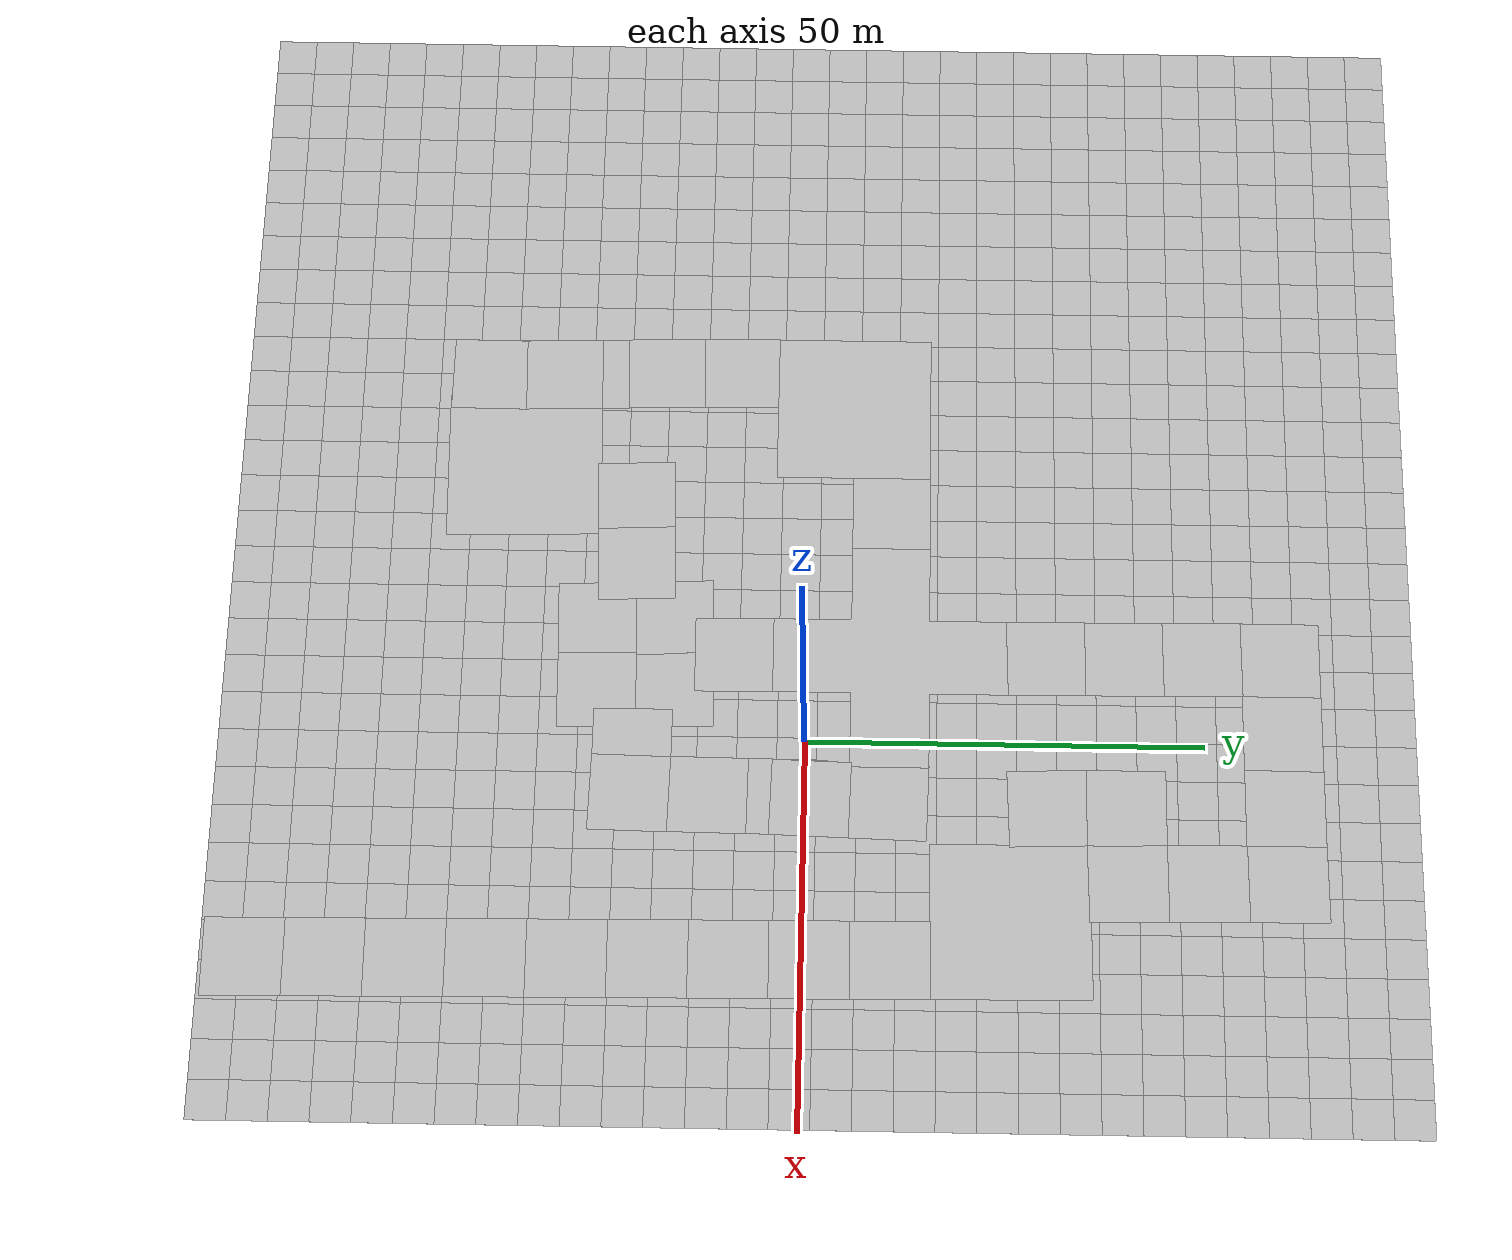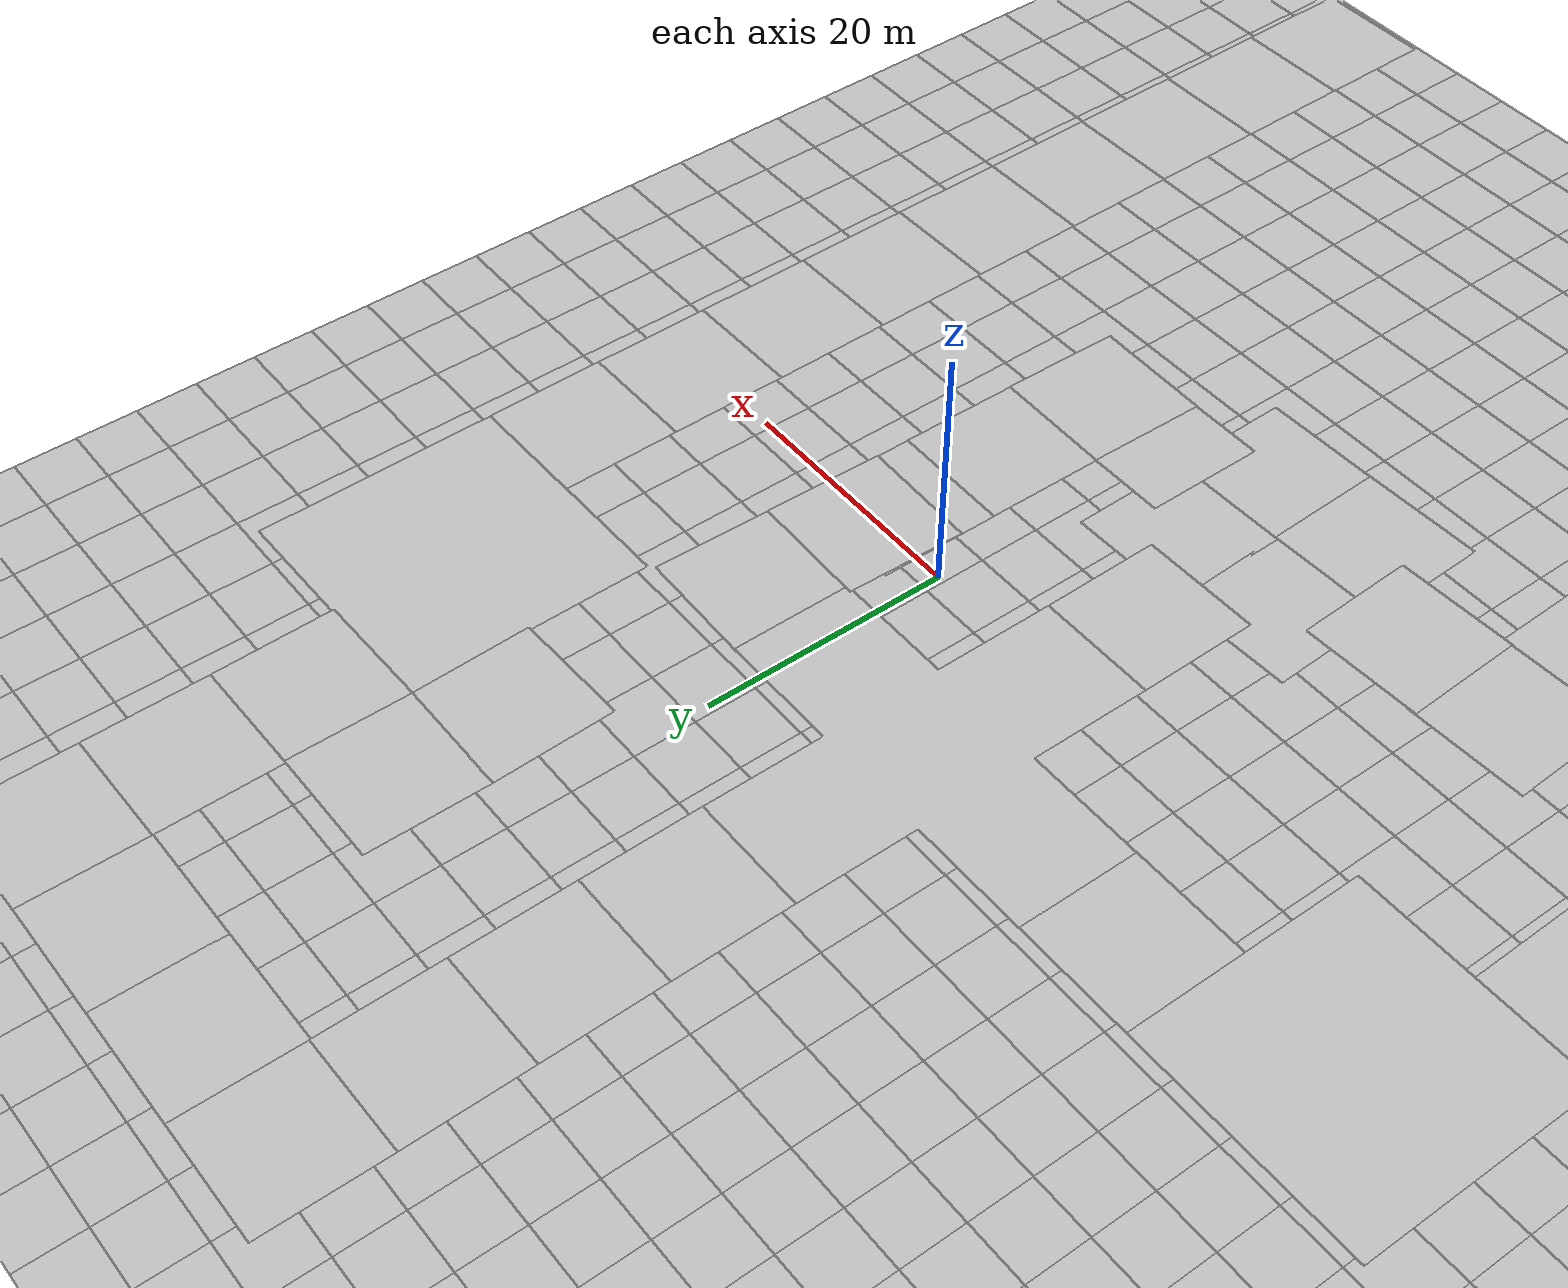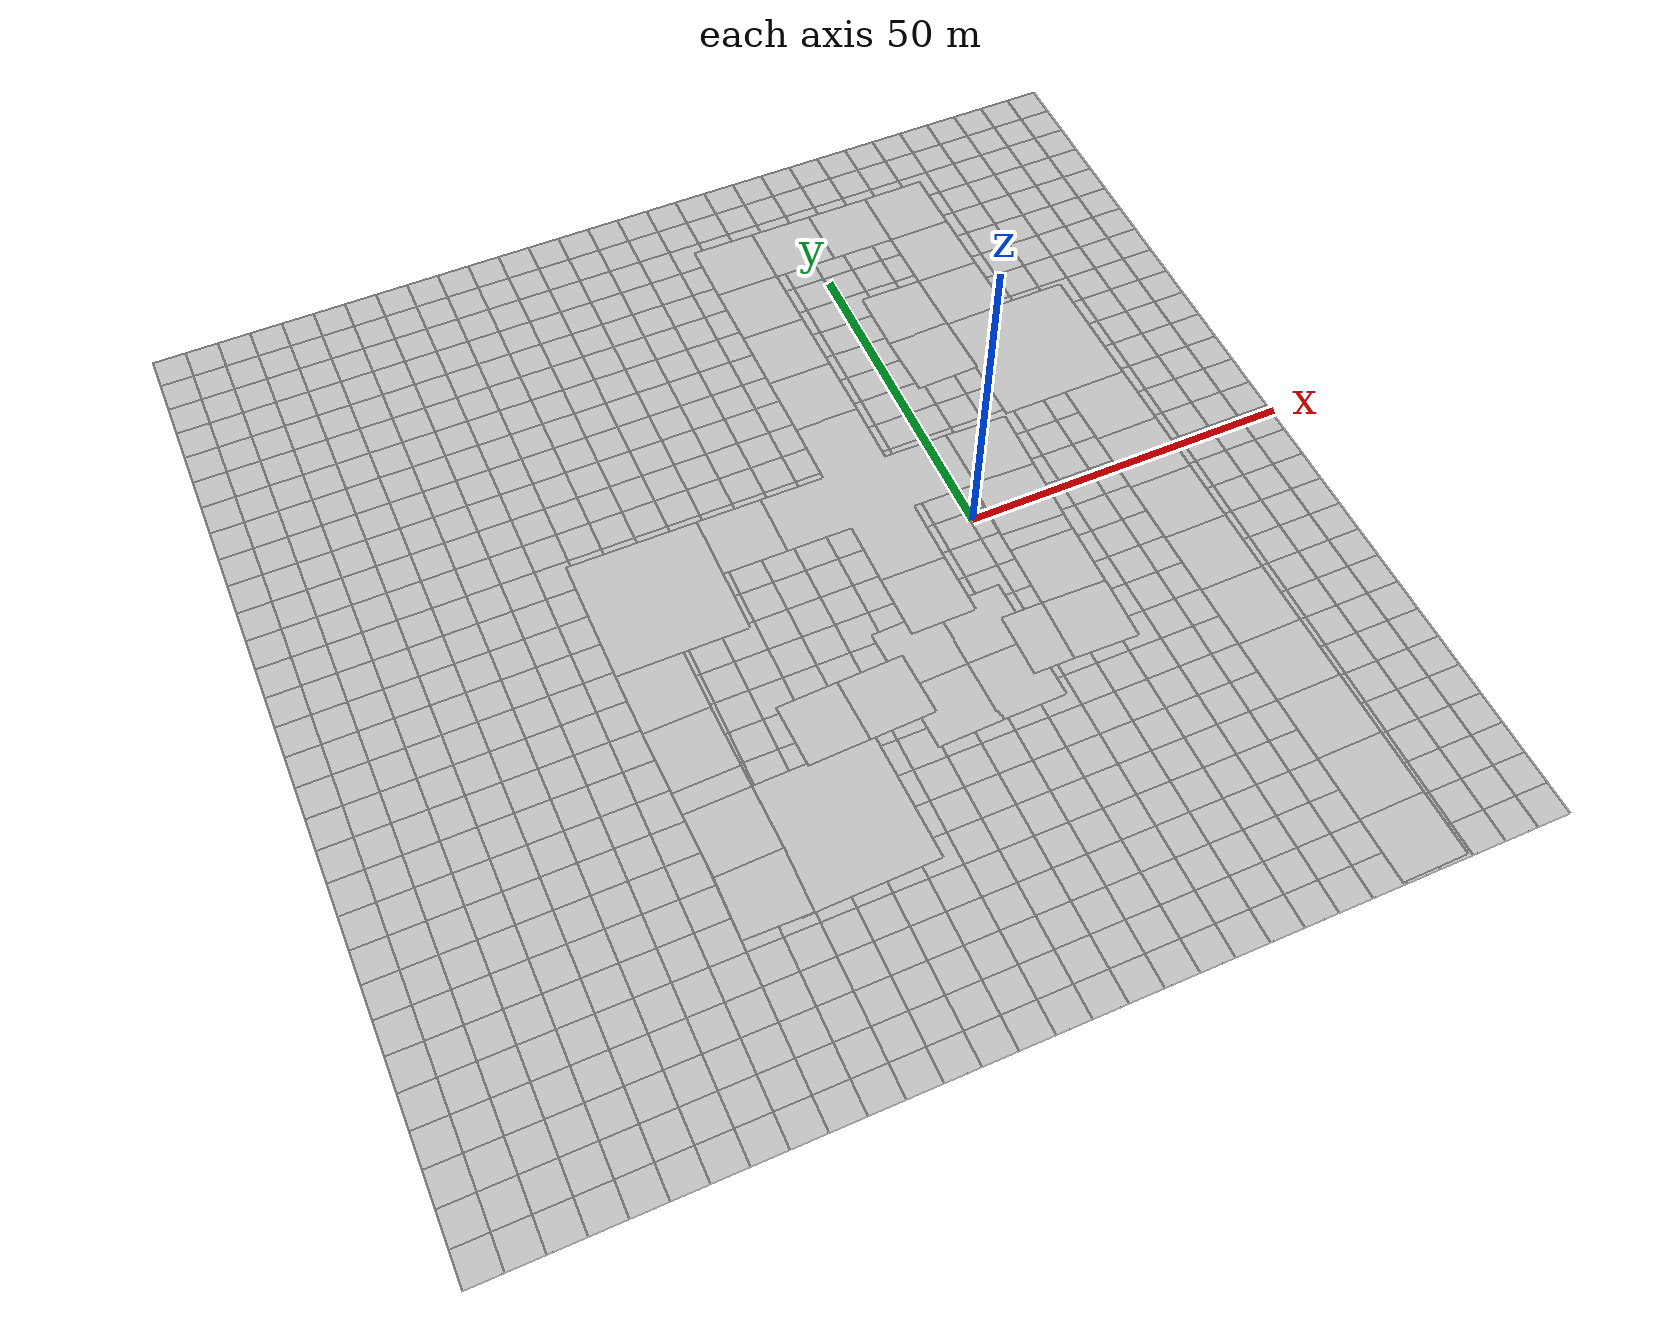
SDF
<sdf version="1.4">
 <world name="default">
  <light name="sun" type="directional">
   <pose>0 0 10 0 -0 0</pose>
   <diffuse>0.8 0.8 0.8 1</diffuse>
   <specular>0.2 0.2 0.2 1</specular>
   <attenuation>
    <range>1000</range>
    <constant>0.9</constant>
    <linear>0.01</linear>
    <quadratic>0.001</quadratic>
   </attenuation>
   <direction>-0.5 0.1 -0.9</direction>
  </light>
  <physics type="ode">
   <max_step_size>0.001</max_step_size>
   <real_time_factor>1</real_time_factor>
   <real_time_update_rate>1000</real_time_update_rate>
   <gravity>0 0 -9.8</gravity>
  </physics>
  <scene><ambient>0.4 0.4 0.4 1</ambient><background>0.7 0.7 0.7 1</background><shadows>1</shadows></scene>
  <model name="pavement_plane">
   <static>1</static>
   <link name="link">
    <collision name="collision">
     <geometry><plane><normal>0 0 1</normal><size>50 50</size></plane></geometry>
     <surface><friction><ode><mu>100</mu><mu2>50</mu2></ode></friction></surface>
    </collision>
    <visual name="visual_0">
     <pose>-25 -25 0 0 -0 0</pose>
     <cast_shadows>0</cast_shadows>
     <geometry><plane><normal>0 0 1</normal><size>5 5</size></plane></geometry>
     <material>
      <script>
       <uri>model://pavement_plane/materials/scripts</uri>
       <uri>model://pavement_plane/materials/textures</uri>
       <name>vrc/pavement</name>
      </script>
     </material>
    </visual>
    <visual name="visual_1">
     <pose>-20 -25 0 0 -0 0</pose>
     <cast_shadows>0</cast_shadows>
     <geometry><plane><normal>0 0 1</normal><size>5 5</size></plane></geometry>
     <material>
      <script>
       <uri>model://pavement_plane/materials/scripts</uri>
       <uri>model://pavement_plane/materials/textures</uri>
       <name>vrc/pavement</name>
      </script>
     </material>
    </visual>
    <visual name="visual_2">
     <pose>-15 -25 0 0 -0 0</pose>
     <cast_shadows>0</cast_shadows>
     <geometry><plane><normal>0 0 1</normal><size>5 5</size></plane></geometry>
     <material>
      <script>
       <uri>model://pavement_plane/materials/scripts</uri>
       <uri>model://pavement_plane/materials/textures</uri>
       <name>vrc/pavement</name>
      </script>
     </material>
    </visual>
    <visual name="visual_3">
     <pose>-10 -25 0 0 -0 0</pose>
     <cast_shadows>0</cast_shadows>
     <geometry><plane><normal>0 0 1</normal><size>5 5</size></plane></geometry>
     <material>
      <script>
       <uri>model://pavement_plane/materials/scripts</uri>
       <uri>model://pavement_plane/materials/textures</uri>
       <name>vrc/pavement</name>
      </script>
     </material>
    </visual>
    <visual name="visual_4">
     <pose>-5 -25 0 0 -0 0</pose>
     <cast_shadows>0</cast_shadows>
     <geometry><plane><normal>0 0 1</normal><size>5 5</size></plane></geometry>
     <material>
      <script>
       <uri>model://pavement_plane/materials/scripts</uri>
       <uri>model://pavement_plane/materials/textures</uri>
       <name>vrc/pavement</name>
      </script>
     </material>
    </visual>
    <visual name="visual_5">
     <pose>0 -25 0 0 -0 0</pose>
     <cast_shadows>0</cast_shadows>
     <geometry><plane><normal>0 0 1</normal><size>5 5</size></plane></geometry>
     <material>
      <script>
       <uri>model://pavement_plane/materials/scripts</uri>
       <uri>model://pavement_plane/materials/textures</uri>
       <name>vrc/pavement</name>
      </script>
     </material>
    </visual>
    <visual name="visual_6">
     <pose>5 -25 0 0 -0 0</pose>
     <cast_shadows>0</cast_shadows>
     <geometry><plane><normal>0 0 1</normal><size>5 5</size></plane></geometry>
     <material>
      <script>
       <uri>model://pavement_plane/materials/scripts</uri>
       <uri>model://pavement_plane/materials/textures</uri>
       <name>vrc/pavement</name>
      </script>
     </material>
    </visual>
    <visual name="visual_7">
     <pose>10 -25 0 0 -0 0</pose>
     <cast_shadows>0</cast_shadows>
     <geometry><plane><normal>0 0 1</normal><size>5 5</size></plane></geometry>
     <material>
      <script>
       <uri>model://pavement_plane/materials/scripts</uri>
       <uri>model://pavement_plane/materials/textures</uri>
       <name>vrc/pavement</name>
      </script>
     </material>
    </visual>
    <visual name="visual_8">
     <pose>15 -25 0 0 -0 0</pose>
     <cast_shadows>0</cast_shadows>
     <geometry><plane><normal>0 0 1</normal><size>5 5</size></plane></geometry>
     <material>
      <script>
       <uri>model://pavement_plane/materials/scripts</uri>
       <uri>model://pavement_plane/materials/textures</uri>
       <name>vrc/pavement</name>
      </script>
     </material>
    </visual>
    <visual name="visual_9">
     <pose>20 -25 0 0 -0 0</pose>
     <cast_shadows>0</cast_shadows>
     <geometry><plane><normal>0 0 1</normal><size>5 5</size></plane></geometry>
     <material>
      <script>
       <uri>model://pavement_plane/materials/scripts</uri>
       <uri>model://pavement_plane/materials/textures</uri>
       <name>vrc/pavement</name>
      </script>
     </material>
    </visual>
    <visual name="visual_10">
     <pose>-25 -20 0 0 -0 0</pose>
     <cast_shadows>0</cast_shadows>
     <geometry><plane><normal>0 0 1</normal><size>5 5</size></plane></geometry>
     <material>
      <script>
       <uri>model://pavement_plane/materials/scripts</uri>
       <uri>model://pavement_plane/materials/textures</uri>
       <name>vrc/pavement</name>
      </script>
     </material>
    </visual>
    <visual name="visual_11">
     <pose>-20 -20 0 0 -0 0</pose>
     <cast_shadows>0</cast_shadows>
     <geometry><plane><normal>0 0 1</normal><size>5 5</size></plane></geometry>
     <material>
      <script>
       <uri>model://pavement_plane/materials/scripts</uri>
       <uri>model://pavement_plane/materials/textures</uri>
       <name>vrc/pavement</name>
      </script>
     </material>
    </visual>
    <visual name="visual_12">
     <pose>-15 -20 0 0 -0 0</pose>
     <cast_shadows>0</cast_shadows>
     <geometry><plane><normal>0 0 1</normal><size>5 5</size></plane></geometry>
     <material>
      <script>
       <uri>model://pavement_plane/materials/scripts</uri>
       <uri>model://pavement_plane/materials/textures</uri>
       <name>vrc/pavement</name>
      </script>
     </material>
    </visual>
    <visual name="visual_13">
     <pose>-10 -20 0 0 -0 0</pose>
     <cast_shadows>0</cast_shadows>
     <geometry><plane><normal>0 0 1</normal><size>5 5</size></plane></geometry>
     <material>
      <script>
       <uri>model://pavement_plane/materials/scripts</uri>
       <uri>model://pavement_plane/materials/textures</uri>
       <name>vrc/pavement</name>
      </script>
     </material>
    </visual>
    <visual name="visual_14">
     <pose>-5 -20 0 0 -0 0</pose>
     <cast_shadows>0</cast_shadows>
     <geometry><plane><normal>0 0 1</normal><size>5 5</size></plane></geometry>
     <material>
      <script>
       <uri>model://pavement_plane/materials/scripts</uri>
       <uri>model://pavement_plane/materials/textures</uri>
       <name>vrc/pavement</name>
      </script>
     </material>
    </visual>
    <visual name="visual_15">
     <pose>0 -20 0 0 -0 0</pose>
     <cast_shadows>0</cast_shadows>
     <geometry><plane><normal>0 0 1</normal><size>5 5</size></plane></geometry>
     <material>
      <script>
       <uri>model://pavement_plane/materials/scripts</uri>
       <uri>model://pavement_plane/materials/textures</uri>
       <name>vrc/pavement</name>
      </script>
     </material>
    </visual>
    <visual name="visual_16">
     <pose>5 -20 0 0 -0 0</pose>
     <cast_shadows>0</cast_shadows>
     <geometry><plane><normal>0 0 1</normal><size>5 5</size></plane></geometry>
     <material>
      <script>
       <uri>model://pavement_plane/materials/scripts</uri>
       <uri>model://pavement_plane/materials/textures</uri>
       <name>vrc/pavement</name>
      </script>
     </material>
    </visual>
    <visual name="visual_17">
     <pose>10 -20 0 0 -0 0</pose>
     <cast_shadows>0</cast_shadows>
     <geometry><plane><normal>0 0 1</normal><size>5 5</size></plane></geometry>
     <material>
      <script>
       <uri>model://pavement_plane/materials/scripts</uri>
       <uri>model://pavement_plane/materials/textures</uri>
       <name>vrc/pavement</name>
      </script>
     </material>
    </visual>
    <visual name="visual_18">
     <pose>15 -20 0 0 -0 0</pose>
     <cast_shadows>0</cast_shadows>
     <geometry><plane><normal>0 0 1</normal><size>5 5</size></plane></geometry>
     <material>
      <script>
       <uri>model://pavement_plane/materials/scripts</uri>
       <uri>model://pavement_plane/materials/textures</uri>
       <name>vrc/pavement</name>
      </script>
     </material>
    </visual>
    <visual name="visual_19">
     <pose>20 -20 0 0 -0 0</pose>
     <cast_shadows>0</cast_shadows>
     <geometry><plane><normal>0 0 1</normal><size>5 5</size></plane></geometry>
     <material>
      <script>
       <uri>model://pavement_plane/materials/scripts</uri>
       <uri>model://pavement_plane/materials/textures</uri>
       <name>vrc/pavement</name>
      </script>
     </material>
    </visual>
    <visual name="visual_20">
     <pose>-25 -15 0 0 -0 0</pose>
     <cast_shadows>0</cast_shadows>
     <geometry><plane><normal>0 0 1</normal><size>5 5</size></plane></geometry>
     <material>
      <script>
       <uri>model://pavement_plane/materials/scripts</uri>
       <uri>model://pavement_plane/materials/textures</uri>
       <name>vrc/pavement</name>
      </script>
     </material>
    </visual>
    <visual name="visual_21">
     <pose>-20 -15 0 0 -0 0</pose>
     <cast_shadows>0</cast_shadows>
     <geometry><plane><normal>0 0 1</normal><size>5 5</size></plane></geometry>
     <material>
      <script>
       <uri>model://pavement_plane/materials/scripts</uri>
       <uri>model://pavement_plane/materials/textures</uri>
       <name>vrc/pavement</name>
      </script>
     </material>
    </visual>
    <visual name="visual_22">
     <pose>-15 -15 0 0 -0 0</pose>
     <cast_shadows>0</cast_shadows>
     <geometry><plane><normal>0 0 1</normal><size>5 5</size></plane></geometry>
     <material>
      <script>
       <uri>model://pavement_plane/materials/scripts</uri>
       <uri>model://pavement_plane/materials/textures</uri>
       <name>vrc/pavement</name>
      </script>
     </material>
    </visual>
    <visual name="visual_23">
     <pose>-10 -15 0 0 -0 0</pose>
     <cast_shadows>0</cast_shadows>
     <geometry><plane><normal>0 0 1</normal><size>5 5</size></plane></geometry>
     <material>
      <script>
       <uri>model://pavement_plane/materials/scripts</uri>
       <uri>model://pavement_plane/materials/textures</uri>
       <name>vrc/pavement</name>
      </script>
     </material>
    </visual>
    <visual name="visual_24">
     <pose>-5 -15 0 0 -0 0</pose>
     <cast_shadows>0</cast_shadows>
     <geometry><plane><normal>0 0 1</normal><size>5 5</size></plane></geometry>
     <material>
      <script>
       <uri>model://pavement_plane/materials/scripts</uri>
       <uri>model://pavement_plane/materials/textures</uri>
       <name>vrc/pavement</name>
      </script>
     </material>
    </visual>
    <visual name="visual_25">
     <pose>0 -15 0 0 -0 0</pose>
     <cast_shadows>0</cast_shadows>
     <geometry><plane><normal>0 0 1</normal><size>5 5</size></plane></geometry>
     <material>
      <script>
       <uri>model://pavement_plane/materials/scripts</uri>
       <uri>model://pavement_plane/materials/textures</uri>
       <name>vrc/pavement</name>
      </script>
     </material>
    </visual>
    <visual name="visual_26">
     <pose>5 -15 0 0 -0 0</pose>
     <cast_shadows>0</cast_shadows>
     <geometry><plane><normal>0 0 1</normal><size>5 5</size></plane></geometry>
     <material>
      <script>
       <uri>model://pavement_plane/materials/scripts</uri>
       <uri>model://pavement_plane/materials/textures</uri>
       <name>vrc/pavement</name>
      </script>
     </material>
    </visual>
    <visual name="visual_27">
     <pose>10 -15 0 0 -0 0</pose>
     <cast_shadows>0</cast_shadows>
     <geometry><plane><normal>0 0 1</normal><size>5 5</size></plane></geometry>
     <material>
      <script>
       <uri>model://pavement_plane/materials/scripts</uri>
       <uri>model://pavement_plane/materials/textures</uri>
       <name>vrc/pavement</name>
      </script>
     </material>
    </visual>
    <visual name="visual_28">
     <pose>15 -15 0 0 -0 0</pose>
     <cast_shadows>0</cast_shadows>
     <geometry><plane><normal>0 0 1</normal><size>5 5</size></plane></geometry>
     <material>
      <script>
       <uri>model://pavement_plane/materials/scripts</uri>
       <uri>model://pavement_plane/materials/textures</uri>
       <name>vrc/pavement</name>
      </script>
     </material>
    </visual>
    <visual name="visual_29">
     <pose>20 -15 0 0 -0 0</pose>
     <cast_shadows>0</cast_shadows>
     <geometry><plane><normal>0 0 1</normal><size>5 5</size></plane></geometry>
     <material>
      <script>
       <uri>model://pavement_plane/materials/scripts</uri>
       <uri>model://pavement_plane/materials/textures</uri>
       <name>vrc/pavement</name>
      </script>
     </material>
    </visual>
    <visual name="visual_30">
     <pose>-25 -10 0 0 -0 0</pose>
     <cast_shadows>0</cast_shadows>
     <geometry><plane><normal>0 0 1</normal><size>5 5</size></plane></geometry>
     <material>
      <script>
       <uri>model://pavement_plane/materials/scripts</uri>
       <uri>model://pavement_plane/materials/textures</uri>
       <name>vrc/pavement</name>
      </script>
     </material>
    </visual>
    <visual name="visual_31">
     <pose>-20 -10 0 0 -0 0</pose>
     <cast_shadows>0</cast_shadows>
     <geometry><plane><normal>0 0 1</normal><size>5 5</size></plane></geometry>
     <material>
      <script>
       <uri>model://pavement_plane/materials/scripts</uri>
       <uri>model://pavement_plane/materials/textures</uri>
       <name>vrc/pavement</name>
      </script>
     </material>
    </visual>
    <visual name="visual_32">
     <pose>-15 -10 0 0 -0 0</pose>
     <cast_shadows>0</cast_shadows>
     <geometry><plane><normal>0 0 1</normal><size>5 5</size></plane></geometry>
     <material>
      <script>
       <uri>model://pavement_plane/materials/scripts</uri>
       <uri>model://pavement_plane/materials/textures</uri>
       <name>vrc/pavement</name>
      </script>
     </material>
    </visual>
    <visual name="visual_33">
     <pose>-10 -10 0 0 -0 0</pose>
     <cast_shadows>0</cast_shadows>
     <geometry><plane><normal>0 0 1</normal><size>5 5</size></plane></geometry>
     <material>
      <script>
       <uri>model://pavement_plane/materials/scripts</uri>
       <uri>model://pavement_plane/materials/textures</uri>
       <name>vrc/pavement</name>
      </script>
     </material>
    </visual>
    <visual name="visual_34">
     <pose>-5 -10 0 0 -0 0</pose>
     <cast_shadows>0</cast_shadows>
     <geometry><plane><normal>0 0 1</normal><size>5 5</size></plane></geometry>
     <material>
      <script>
       <uri>model://pavement_plane/materials/scripts</uri>
       <uri>model://pavement_plane/materials/textures</uri>
       <name>vrc/pavement</name>
      </script>
     </material>
    </visual>
    <visual name="visual_35">
     <pose>0 -10 0 0 -0 0</pose>
     <cast_shadows>0</cast_shadows>
     <geometry><plane><normal>0 0 1</normal><size>5 5</size></plane></geometry>
     <material>
      <script>
       <uri>model://pavement_plane/materials/scripts</uri>
       <uri>model://pavement_plane/materials/textures</uri>
       <name>vrc/pavement</name>
      </script>
     </material>
    </visual>
    <visual name="visual_36">
     <pose>5 -10 0 0 -0 0</pose>
     <cast_shadows>0</cast_shadows>
     <geometry><plane><normal>0 0 1</normal><size>5 5</size></plane></geometry>
     <material>
      <script>
       <uri>model://pavement_plane/materials/scripts</uri>
       <uri>model://pavement_plane/materials/textures</uri>
       <name>vrc/pavement</name>
      </script>
     </material>
    </visual>
    <visual name="visual_37">
     <pose>10 -10 0 0 -0 0</pose>
     <cast_shadows>0</cast_shadows>
     <geometry><plane><normal>0 0 1</normal><size>5 5</size></plane></geometry>
     <material>
      <script>
       <uri>model://pavement_plane/materials/scripts</uri>
       <uri>model://pavement_plane/materials/textures</uri>
       <name>vrc/pavement</name>
      </script>
     </material>
    </visual>
    <visual name="visual_38">
     <pose>15 -10 0 0 -0 0</pose>
     <cast_shadows>0</cast_shadows>
     <geometry><plane><normal>0 0 1</normal><size>5 5</size></plane></geometry>
     <material>
      <script>
       <uri>model://pavement_plane/materials/scripts</uri>
       <uri>model://pavement_plane/materials/textures</uri>
       <name>vrc/pavement</name>
      </script>
     </material>
    </visual>
    <visual name="visual_39">
     <pose>20 -10 0 0 -0 0</pose>
     <cast_shadows>0</cast_shadows>
     <geometry><plane><normal>0 0 1</normal><size>5 5</size></plane></geometry>
     <material>
      <script>
       <uri>model://pavement_plane/materials/scripts</uri>
       <uri>model://pavement_plane/materials/textures</uri>
       <name>vrc/pavement</name>
      </script>
     </material>
    </visual>
    <visual name="visual_40">
     <pose>-25 -5 0 0 -0 0</pose>
     <cast_shadows>0</cast_shadows>
     <geometry><plane><normal>0 0 1</normal><size>5 5</size></plane></geometry>
     <material>
      <script>
       <uri>model://pavement_plane/materials/scripts</uri>
       <uri>model://pavement_plane/materials/textures</uri>
       <name>vrc/pavement</name>
      </script>
     </material>
    </visual>
    <visual name="visual_41">
     <pose>-20 -5 0 0 -0 0</pose>
     <cast_shadows>0</cast_shadows>
     <geometry><plane><normal>0 0 1</normal><size>5 5</size></plane></geometry>
     <material>
      <script>
       <uri>model://pavement_plane/materials/scripts</uri>
       <uri>model://pavement_plane/materials/textures</uri>
       <name>vrc/pavement</name>
      </script>
     </material>
    </visual>
    <visual name="visual_42">
     <pose>-15 -5 0 0 -0 0</pose>
     <cast_shadows>0</cast_shadows>
     <geometry><plane><normal>0 0 1</normal><size>5 5</size></plane></geometry>
     <material>
      <script>
       <uri>model://pavement_plane/materials/scripts</uri>
       <uri>model://pavement_plane/materials/textures</uri>
       <name>vrc/pavement</name>
      </script>
     </material>
    </visual>
    <visual name="visual_43">
     <pose>-10 -5 0 0 -0 0</pose>
     <cast_shadows>0</cast_shadows>
     <geometry><plane><normal>0 0 1</normal><size>5 5</size></plane></geometry>
     <material>
      <script>
       <uri>model://pavement_plane/materials/scripts</uri>
       <uri>model://pavement_plane/materials/textures</uri>
       <name>vrc/pavement</name>
      </script>
     </material>
    </visual>
    <visual name="visual_44">
     <pose>-5 -5 0 0 -0 0</pose>
     <cast_shadows>0</cast_shadows>
     <geometry><plane><normal>0 0 1</normal><size>5 5</size></plane></geometry>
     <material>
      <script>
       <uri>model://pavement_plane/materials/scripts</uri>
       <uri>model://pavement_plane/materials/textures</uri>
       <name>vrc/pavement</name>
      </script>
     </material>
    </visual>
    <visual name="visual_45">
     <pose>0 -5 0 0 -0 0</pose>
     <cast_shadows>0</cast_shadows>
     <geometry><plane><normal>0 0 1</normal><size>5 5</size></plane></geometry>
     <material>
      <script>
       <uri>model://pavement_plane/materials/scripts</uri>
       <uri>model://pavement_plane/materials/textures</uri>
       <name>vrc/pavement</name>
      </script>
     </material>
    </visual>
    <visual name="visual_46">
     <pose>5 -5 0 0 -0 0</pose>
     <cast_shadows>0</cast_shadows>
     <geometry><plane><normal>0 0 1</normal><size>5 5</size></plane></geometry>
     <material>
      <script>
       <uri>model://pavement_plane/materials/scripts</uri>
       <uri>model://pavement_plane/materials/textures</uri>
       <name>vrc/pavement</name>
      </script>
     </material>
    </visual>
    <visual name="visual_47">
     <pose>10 -5 0 0 -0 0</pose>
     <cast_shadows>0</cast_shadows>
     <geometry><plane><normal>0 0 1</normal><size>5 5</size></plane></geometry>
     <material>
      <script>
       <uri>model://pavement_plane/materials/scripts</uri>
       <uri>model://pavement_plane/materials/textures</uri>
       <name>vrc/pavement</name>
      </script>
     </material>
    </visual>
    <visual name="visual_48">
     <pose>15 -5 0 0 -0 0</pose>
     <cast_shadows>0</cast_shadows>
     <geometry><plane><normal>0 0 1</normal><size>5 5</size></plane></geometry>
     <material>
      <script>
       <uri>model://pavement_plane/materials/scripts</uri>
       <uri>model://pavement_plane/materials/textures</uri>
       <name>vrc/pavement</name>
      </script>
     </material>
    </visual>
    <visual name="visual_49">
     <pose>20 -5 0 0 -0 0</pose>
     <cast_shadows>0</cast_shadows>
     <geometry><plane><normal>0 0 1</normal><size>5 5</size></plane></geometry>
     <material>
      <script>
       <uri>model://pavement_plane/materials/scripts</uri>
       <uri>model://pavement_plane/materials/textures</uri>
       <name>vrc/pavement</name>
      </script>
     </material>
    </visual>
    <visual name="visual_50">
     <pose>-25 0 0 0 -0 0</pose>
     <cast_shadows>0</cast_shadows>
     <geometry><plane><normal>0 0 1</normal><size>5 5</size></plane></geometry>
     <material>
      <script>
       <uri>model://pavement_plane/materials/scripts</uri>
       <uri>model://pavement_plane/materials/textures</uri>
       <name>vrc/pavement</name>
      </script>
     </material>
    </visual>
    <visual name="visual_51">
     <pose>-20 0 0 0 -0 0</pose>
     <cast_shadows>0</cast_shadows>
     <geometry><plane><normal>0 0 1</normal><size>5 5</size></plane></geometry>
     <material>
      <script>
       <uri>model://pavement_plane/materials/scripts</uri>
       <uri>model://pavement_plane/materials/textures</uri>
       <name>vrc/pavement</name>
      </script>
     </material>
    </visual>
    <visual name="visual_52">
     <pose>-15 0 0 0 -0 0</pose>
     <cast_shadows>0</cast_shadows>
     <geometry><plane><normal>0 0 1</normal><size>5 5</size></plane></geometry>
     <material>
      <script>
       <uri>model://pavement_plane/materials/scripts</uri>
       <uri>model://pavement_plane/materials/textures</uri>
       <name>vrc/pavement</name>
      </script>
     </material>
    </visual>
    <visual name="visual_53">
     <pose>-10 0 0 0 -0 0</pose>
     <cast_shadows>0</cast_shadows>
     <geometry><plane><normal>0 0 1</normal><size>5 5</size></plane></geometry>
     <material>
      <script>
       <uri>model://pavement_plane/materials/scripts</uri>
       <uri>model://pavement_plane/materials/textures</uri>
       <name>vrc/pavement</name>
      </script>
     </material>
    </visual>
    <visual name="visual_54">
     <pose>-5 0 0 0 -0 0</pose>
     <cast_shadows>0</cast_shadows>
     <geometry><plane><normal>0 0 1</normal><size>5 5</size></plane></geometry>
     <material>
      <script>
       <uri>model://pavement_plane/materials/scripts</uri>
       <uri>model://pavement_plane/materials/textures</uri>
       <name>vrc/pavement</name>
      </script>
     </material>
    </visual>
    <visual name="visual_55">
     <cast_shadows>0</cast_shadows>
     <geometry><plane><normal>0 0 1</normal><size>5 5</size></plane></geometry>
     <material>
      <script>
       <uri>model://pavement_plane/materials/scripts</uri>
       <uri>model://pavement_plane/materials/textures</uri>
       <name>vrc/pavement</name>
      </script>
     </material>
    </visual>
    <visual name="visual_56">
     <pose>5 0 0 0 -0 0</pose>
     <cast_shadows>0</cast_shadows>
     <geometry><plane><normal>0 0 1</normal><size>5 5</size></plane></geometry>
     <material>
      <script>
       <uri>model://pavement_plane/materials/scripts</uri>
       <uri>model://pavement_plane/materials/textures</uri>
       <name>vrc/pavement</name>
      </script>
     </material>
    </visual>
    <visual name="visual_57">
     <pose>10 0 0 0 -0 0</pose>
     <cast_shadows>0</cast_shadows>
     <geometry><plane><normal>0 0 1</normal><size>5 5</size></plane></geometry>
     <material>
      <script>
       <uri>model://pavement_plane/materials/scripts</uri>
       <uri>model://pavement_plane/materials/textures</uri>
       <name>vrc/pavement</name>
      </script>
     </material>
    </visual>
    <visual name="visual_58">
     <pose>15 0 0 0 -0 0</pose>
     <cast_shadows>0</cast_shadows>
     <geometry><plane><normal>0 0 1</normal><size>5 5</size></plane></geometry>
     <material>
      <script>
       <uri>model://pavement_plane/materials/scripts</uri>
       <uri>model://pavement_plane/materials/textures</uri>
       <name>vrc/pavement</name>
      </script>
     </material>
    </visual>
    <visual name="visual_59">
     <pose>20 0 0 0 -0 0</pose>
     <cast_shadows>0</cast_shadows>
     <geometry><plane><normal>0 0 1</normal><size>5 5</size></plane></geometry>
     <material>
      <script>
       <uri>model://pavement_plane/materials/scripts</uri>
       <uri>model://pavement_plane/materials/textures</uri>
       <name>vrc/pavement</name>
      </script>
     </material>
    </visual>
    <visual name="visual_60">
     <pose>-25 5 0 0 -0 0</pose>
     <cast_shadows>0</cast_shadows>
     <geometry><plane><normal>0 0 1</normal><size>5 5</size></plane></geometry>
     <material>
      <script>
       <uri>model://pavement_plane/materials/scripts</uri>
       <uri>model://pavement_plane/materials/textures</uri>
       <name>vrc/pavement</name>
      </script>
     </material>
    </visual>
    <visual name="visual_61">
     <pose>-20 5 0 0 -0 0</pose>
     <cast_shadows>0</cast_shadows>
     <geometry><plane><normal>0 0 1</normal><size>5 5</size></plane></geometry>
     <material>
      <script>
       <uri>model://pavement_plane/materials/scripts</uri>
       <uri>model://pavement_plane/materials/textures</uri>
       <name>vrc/pavement</name>
      </script>
     </material>
    </visual>
    <visual name="visual_62">
     <pose>-15 5 0 0 -0 0</pose>
     <cast_shadows>0</cast_shadows>
     <geometry><plane><normal>0 0 1</normal><size>5 5</size></plane></geometry>
     <material>
      <script>
       <uri>model://pavement_plane/materials/scripts</uri>
       <uri>model://pavement_plane/materials/textures</uri>
       <name>vrc/pavement</name>
      </script>
     </material>
    </visual>
    <visual name="visual_63">
     <pose>-10 5 0 0 -0 0</pose>
     <cast_shadows>0</cast_shadows>
     <geometry><plane><normal>0 0 1</normal><size>5 5</size></plane></geometry>
     <material>
      <script>
       <uri>model://pavement_plane/materials/scripts</uri>
       <uri>model://pavement_plane/materials/textures</uri>
       <name>vrc/pavement</name>
      </script>
     </material>
    </visual>
    <visual name="visual_64">
     <pose>-5 5 0 0 -0 0</pose>
     <cast_shadows>0</cast_shadows>
     <geometry><plane><normal>0 0 1</normal><size>5 5</size></plane></geometry>
     <material>
      <script>
       <uri>model://pavement_plane/materials/scripts</uri>
       <uri>model://pavement_plane/materials/textures</uri>
       <name>vrc/pavement</name>
      </script>
     </material>
    </visual>
    <visual name="visual_65">
     <pose>0 5 0 0 -0 0</pose>
     <cast_shadows>0</cast_shadows>
     <geometry><plane><normal>0 0 1</normal><size>5 5</size></plane></geometry>
     <material>
      <script>
       <uri>model://pavement_plane/materials/scripts</uri>
       <uri>model://pavement_plane/materials/textures</uri>
       <name>vrc/pavement</name>
      </script>
     </material>
    </visual>
    <visual name="visual_66">
     <pose>5 5 0 0 -0 0</pose>
     <cast_shadows>0</cast_shadows>
     <geometry><plane><normal>0 0 1</normal><size>5 5</size></plane></geometry>
     <material>
      <script>
       <uri>model://pavement_plane/materials/scripts</uri>
       <uri>model://pavement_plane/materials/textures</uri>
       <name>vrc/pavement</name>
      </script>
     </material>
    </visual>
    <visual name="visual_67">
     <pose>10 5 0 0 -0 0</pose>
     <cast_shadows>0</cast_shadows>
     <geometry><plane><normal>0 0 1</normal><size>5 5</size></plane></geometry>
     <material>
      <script>
       <uri>model://pavement_plane/materials/scripts</uri>
       <uri>model://pavement_plane/materials/textures</uri>
       <name>vrc/pavement</name>
      </script>
     </material>
    </visual>
    <visual name="visual_68">
     <pose>15 5 0 0 -0 0</pose>
     <cast_shadows>0</cast_shadows>
     <geometry><plane><normal>0 0 1</normal><size>5 5</size></plane></geometry>
     <material>
      <script>
       <uri>model://pavement_plane/materials/scripts</uri>
       <uri>model://pavement_plane/materials/textures</uri>
       <name>vrc/pavement</name>
      </script>
     </material>
    </visual>
    <visual name="visual_69">
     <pose>20 5 0 0 -0 0</pose>
     <cast_shadows>0</cast_shadows>
     <geometry><plane><normal>0 0 1</normal><size>5 5</size></plane></geometry>
     <material>
      <script>
       <uri>model://pavement_plane/materials/scripts</uri>
       <uri>model://pavement_plane/materials/textures</uri>
       <name>vrc/pavement</name>
      </script>
     </material>
    </visual>
    <visual name="visual_70">
     <pose>-25 10 0 0 -0 0</pose>
     <cast_shadows>0</cast_shadows>
     <geometry><plane><normal>0 0 1</normal><size>5 5</size></plane></geometry>
     <material>
      <script>
       <uri>model://pavement_plane/materials/scripts</uri>
       <uri>model://pavement_plane/materials/textures</uri>
       <name>vrc/pavement</name>
      </script>
     </material>
    </visual>
    <visual name="visual_71">
     <pose>-20 10 0 0 -0 0</pose>
     <cast_shadows>0</cast_shadows>
     <geometry><plane><normal>0 0 1</normal><size>5 5</size></plane></geometry>
     <material>
      <script>
       <uri>model://pavement_plane/materials/scripts</uri>
       <uri>model://pavement_plane/materials/textures</uri>
       <name>vrc/pavement</name>
      </script>
     </material>
    </visual>
    <visual name="visual_72">
     <pose>-15 10 0 0 -0 0</pose>
     <cast_shadows>0</cast_shadows>
     <geometry><plane><normal>0 0 1</normal><size>5 5</size></plane></geometry>
     <material>
      <script>
       <uri>model://pavement_plane/materials/scripts</uri>
       <uri>model://pavement_plane/materials/textures</uri>
       <name>vrc/pavement</name>
      </script>
     </material>
    </visual>
    <visual name="visual_73">
     <pose>-10 10 0 0 -0 0</pose>
     <cast_shadows>0</cast_shadows>
     <geometry><plane><normal>0 0 1</normal><size>5 5</size></plane></geometry>
     <material>
      <script>
       <uri>model://pavement_plane/materials/scripts</uri>
       <uri>model://pavement_plane/materials/textures</uri>
       <name>vrc/pavement</name>
      </script>
     </material>
    </visual>
    <visual name="visual_74">
     <pose>-5 10 0 0 -0 0</pose>
     <cast_shadows>0</cast_shadows>
     <geometry><plane><normal>0 0 1</normal><size>5 5</size></plane></geometry>
     <material>
      <script>
       <uri>model://pavement_plane/materials/scripts</uri>
       <uri>model://pavement_plane/materials/textures</uri>
       <name>vrc/pavement</name>
      </script>
     </material>
    </visual>
    <visual name="visual_75">
     <pose>0 10 0 0 -0 0</pose>
     <cast_shadows>0</cast_shadows>
     <geometry><plane><normal>0 0 1</normal><size>5 5</size></plane></geometry>
     <material>
      <script>
       <uri>model://pavement_plane/materials/scripts</uri>
       <uri>model://pavement_plane/materials/textures</uri>
       <name>vrc/pavement</name>
      </script>
     </material>
    </visual>
    <visual name="visual_76">
     <pose>5 10 0 0 -0 0</pose>
     <cast_shadows>0</cast_shadows>
     <geometry><plane><normal>0 0 1</normal><size>5 5</size></plane></geometry>
     <material>
      <script>
       <uri>model://pavement_plane/materials/scripts</uri>
       <uri>model://pavement_plane/materials/textures</uri>
       <name>vrc/pavement</name>
      </script>
     </material>
    </visual>
    <visual name="visual_77">
     <pose>10 10 0 0 -0 0</pose>
     <cast_shadows>0</cast_shadows>
     <geometry><plane><normal>0 0 1</normal><size>5 5</size></plane></geometry>
     <material>
      <script>
       <uri>model://pavement_plane/materials/scripts</uri>
       <uri>model://pavement_plane/materials/textures</uri>
       <name>vrc/pavement</name>
      </script>
     </material>
    </visual>
    <visual name="visual_78">
     <pose>15 10 0 0 -0 0</pose>
     <cast_shadows>0</cast_shadows>
     <geometry><plane><normal>0 0 1</normal><size>5 5</size></plane></geometry>
     <material>
      <script>
       <uri>model://pavement_plane/materials/scripts</uri>
       <uri>model://pavement_plane/materials/textures</uri>
       <name>vrc/pavement</name>
      </script>
     </material>
    </visual>
    <visual name="visual_79">
     <pose>20 10 0 0 -0 0</pose>
     <cast_shadows>0</cast_shadows>
     <geometry><plane><normal>0 0 1</normal><size>5 5</size></plane></geometry>
     <material>
      <script>
       <uri>model://pavement_plane/materials/scripts</uri>
       <uri>model://pavement_plane/materials/textures</uri>
       <name>vrc/pavement</name>
      </script>
     </material>
    </visual>
    <visual name="visual_80">
     <pose>-25 15 0 0 -0 0</pose>
     <cast_shadows>0</cast_shadows>
     <geometry><plane><normal>0 0 1</normal><size>5 5</size></plane></geometry>
     <material>
      <script>
       <uri>model://pavement_plane/materials/scripts</uri>
       <uri>model://pavement_plane/materials/textures</uri>
       <name>vrc/pavement</name>
      </script>
     </material>
    </visual>
    <visual name="visual_81">
     <pose>-20 15 0 0 -0 0</pose>
     <cast_shadows>0</cast_shadows>
     <geometry><plane><normal>0 0 1</normal><size>5 5</size></plane></geometry>
     <material>
      <script>
       <uri>model://pavement_plane/materials/scripts</uri>
       <uri>model://pavement_plane/materials/textures</uri>
       <name>vrc/pavement</name>
      </script>
     </material>
    </visual>
    <visual name="visual_82">
     <pose>-15 15 0 0 -0 0</pose>
     <cast_shadows>0</cast_shadows>
     <geometry><plane><normal>0 0 1</normal><size>5 5</size></plane></geometry>
     <material>
      <script>
       <uri>model://pavement_plane/materials/scripts</uri>
       <uri>model://pavement_plane/materials/textures</uri>
       <name>vrc/pavement</name>
      </script>
     </material>
    </visual>
    <visual name="visual_83">
     <pose>-10 15 0 0 -0 0</pose>
     <cast_shadows>0</cast_shadows>
     <geometry><plane><normal>0 0 1</normal><size>5 5</size></plane></geometry>
     <material>
      <script>
       <uri>model://pavement_plane/materials/scripts</uri>
       <uri>model://pavement_plane/materials/textures</uri>
       <name>vrc/pavement</name>
      </script>
     </material>
    </visual>
    <visual name="visual_84">
     <pose>-5 15 0 0 -0 0</pose>
     <cast_shadows>0</cast_shadows>
     <geometry><plane><normal>0 0 1</normal><size>5 5</size></plane></geometry>
     <material>
      <script>
       <uri>model://pavement_plane/materials/scripts</uri>
       <uri>model://pavement_plane/materials/textures</uri>
       <name>vrc/pavement</name>
      </script>
     </material>
    </visual>
    <visual name="visual_85">
     <pose>0 15 0 0 -0 0</pose>
     <cast_shadows>0</cast_shadows>
     <geometry><plane><normal>0 0 1</normal><size>5 5</size></plane></geometry>
     <material>
      <script>
       <uri>model://pavement_plane/materials/scripts</uri>
       <uri>model://pavement_plane/materials/textures</uri>
       <name>vrc/pavement</name>
      </script>
     </material>
    </visual>
    <visual name="visual_86">
     <pose>5 15 0 0 -0 0</pose>
     <cast_shadows>0</cast_shadows>
     <geometry><plane><normal>0 0 1</normal><size>5 5</size></plane></geometry>
     <material>
      <script>
       <uri>model://pavement_plane/materials/scripts</uri>
       <uri>model://pavement_plane/materials/textures</uri>
       <name>vrc/pavement</name>
      </script>
     </material>
    </visual>
    <visual name="visual_87">
     <pose>10 15 0 0 -0 0</pose>
     <cast_shadows>0</cast_shadows>
     <geometry><plane><normal>0 0 1</normal><size>5 5</size></plane></geometry>
     <material>
      <script>
       <uri>model://pavement_plane/materials/scripts</uri>
       <uri>model://pavement_plane/materials/textures</uri>
       <name>vrc/pavement</name>
      </script>
     </material>
    </visual>
    <visual name="visual_88">
     <pose>15 15 0 0 -0 0</pose>
     <cast_shadows>0</cast_shadows>
     <geometry><plane><normal>0 0 1</normal><size>5 5</size></plane></geometry>
     <material>
      <script>
       <uri>model://pavement_plane/materials/scripts</uri>
       <uri>model://pavement_plane/materials/textures</uri>
       <name>vrc/pavement</name>
      </script>
     </material>
    </visual>
    <visual name="visual_89">
     <pose>20 15 0 0 -0 0</pose>
     <cast_shadows>0</cast_shadows>
     <geometry><plane><normal>0 0 1</normal><size>5 5</size></plane></geometry>
     <material>
      <script>
       <uri>model://pavement_plane/materials/scripts</uri>
       <uri>model://pavement_plane/materials/textures</uri>
       <name>vrc/pavement</name>
      </script>
     </material>
    </visual>
    <visual name="visual_90">
     <pose>-25 20 0 0 -0 0</pose>
     <cast_shadows>0</cast_shadows>
     <geometry><plane><normal>0 0 1</normal><size>5 5</size></plane></geometry>
     <material>
      <script>
       <uri>model://pavement_plane/materials/scripts</uri>
       <uri>model://pavement_plane/materials/textures</uri>
       <name>vrc/pavement</name>
      </script>
     </material>
    </visual>
    <visual name="visual_91">
     <pose>-20 20 0 0 -0 0</pose>
     <cast_shadows>0</cast_shadows>
     <geometry><plane><normal>0 0 1</normal><size>5 5</size></plane></geometry>
     <material>
      <script>
       <uri>model://pavement_plane/materials/scripts</uri>
       <uri>model://pavement_plane/materials/textures</uri>
       <name>vrc/pavement</name>
      </script>
     </material>
    </visual>
    <visual name="visual_92">
     <pose>-15 20 0 0 -0 0</pose>
     <cast_shadows>0</cast_shadows>
     <geometry><plane><normal>0 0 1</normal><size>5 5</size></plane></geometry>
     <material>
      <script>
       <uri>model://pavement_plane/materials/scripts</uri>
       <uri>model://pavement_plane/materials/textures</uri>
       <name>vrc/pavement</name>
      </script>
     </material>
    </visual>
    <visual name="visual_93">
     <pose>-10 20 0 0 -0 0</pose>
     <cast_shadows>0</cast_shadows>
     <geometry><plane><normal>0 0 1</normal><size>5 5</size></plane></geometry>
     <material>
      <script>
       <uri>model://pavement_plane/materials/scripts</uri>
       <uri>model://pavement_plane/materials/textures</uri>
       <name>vrc/pavement</name>
      </script>
     </material>
    </visual>
    <visual name="visual_94">
     <pose>-5 20 0 0 -0 0</pose>
     <cast_shadows>0</cast_shadows>
     <geometry><plane><normal>0 0 1</normal><size>5 5</size></plane></geometry>
     <material>
      <script>
       <uri>model://pavement_plane/materials/scripts</uri>
       <uri>model://pavement_plane/materials/textures</uri>
       <name>vrc/pavement</name>
      </script>
     </material>
    </visual>
    <visual name="visual_95">
     <pose>0 20 0 0 -0 0</pose>
     <cast_shadows>0</cast_shadows>
     <geometry><plane><normal>0 0 1</normal><size>5 5</size></plane></geometry>
     <material>
      <script>
       <uri>model://pavement_plane/materials/scripts</uri>
       <uri>model://pavement_plane/materials/textures</uri>
       <name>vrc/pavement</name>
      </script>
     </material>
    </visual>
    <visual name="visual_96">
     <pose>5 20 0 0 -0 0</pose>
     <cast_shadows>0</cast_shadows>
     <geometry><plane><normal>0 0 1</normal><size>5 5</size></plane></geometry>
     <material>
      <script>
       <uri>model://pavement_plane/materials/scripts</uri>
       <uri>model://pavement_plane/materials/textures</uri>
       <name>vrc/pavement</name>
      </script>
     </material>
    </visual>
    <visual name="visual_97">
     <pose>10 20 0 0 -0 0</pose>
     <cast_shadows>0</cast_shadows>
     <geometry><plane><normal>0 0 1</normal><size>5 5</size></plane></geometry>
     <material>
      <script>
       <uri>model://pavement_plane/materials/scripts</uri>
       <uri>model://pavement_plane/materials/textures</uri>
       <name>vrc/pavement</name>
      </script>
     </material>
    </visual>
    <visual name="visual_98">
     <pose>15 20 0 0 -0 0</pose>
     <cast_shadows>0</cast_shadows>
     <geometry><plane><normal>0 0 1</normal><size>5 5</size></plane></geometry>
     <material>
      <script>
       <uri>model://pavement_plane/materials/scripts</uri>
       <uri>model://pavement_plane/materials/textures</uri>
       <name>vrc/pavement</name>
      </script>
     </material>
    </visual>
    <visual name="visual_99">
     <pose>20 20 0 0 -0 0</pose>
     <cast_shadows>0</cast_shadows>
     <geometry><plane><normal>0 0 1</normal><size>5 5</size></plane></geometry>
     <material>
      <script>
       <uri>model://pavement_plane/materials/scripts</uri>
       <uri>model://pavement_plane/materials/textures</uri>
       <name>vrc/pavement</name>
      </script>
     </material>
    </visual>
    <velocity_decay><linear>0</linear><angular>0</angular></velocity_decay>
   </link>
   <pose>27 4 0 0 -0 0</pose>
  </model>
  <model name="pavement_plane_0">
   <static>1</static>
   <link name="link">
    <collision name="collision">
     <geometry><plane><normal>0 0 1</normal><size>50 50</size></plane></geometry>
     <surface><friction><ode><mu>100</mu><mu2>50</mu2></ode></friction></surface>
    </collision>
    <visual name="visual_0">
     <pose>-25 -25 0 0 -0 0</pose>
     <cast_shadows>0</cast_shadows>
     <geometry><plane><normal>0 0 1</normal><size>5 5</size></plane></geometry>
     <material>
      <script>
       <uri>model://pavement_plane/materials/scripts</uri>
       <uri>model://pavement_plane/materials/textures</uri>
       <name>vrc/pavement</name>
      </script>
     </material>
    </visual>
    <visual name="visual_1">
     <pose>-20 -25 0 0 -0 0</pose>
     <cast_shadows>0</cast_shadows>
     <geometry><plane><normal>0 0 1</normal><size>5 5</size></plane></geometry>
     <material>
      <script>
       <uri>model://pavement_plane/materials/scripts</uri>
       <uri>model://pavement_plane/materials/textures</uri>
       <name>vrc/pavement</name>
      </script>
     </material>
    </visual>
    <visual name="visual_2">
     <pose>-15 -25 0 0 -0 0</pose>
     <cast_shadows>0</cast_shadows>
     <geometry><plane><normal>0 0 1</normal><size>5 5</size></plane></geometry>
     <material>
      <script>
       <uri>model://pavement_plane/materials/scripts</uri>
       <uri>model://pavement_plane/materials/textures</uri>
       <name>vrc/pavement</name>
      </script>
     </material>
    </visual>
    <visual name="visual_3">
     <pose>-10 -25 0 0 -0 0</pose>
     <cast_shadows>0</cast_shadows>
     <geometry><plane><normal>0 0 1</normal><size>5 5</size></plane></geometry>
     <material>
      <script>
       <uri>model://pavement_plane/materials/scripts</uri>
       <uri>model://pavement_plane/materials/textures</uri>
       <name>vrc/pavement</name>
      </script>
     </material>
    </visual>
    <visual name="visual_4">
     <pose>-5 -25 0 0 -0 0</pose>
     <cast_shadows>0</cast_shadows>
     <geometry><plane><normal>0 0 1</normal><size>5 5</size></plane></geometry>
     <material>
      <script>
       <uri>model://pavement_plane/materials/scripts</uri>
       <uri>model://pavement_plane/materials/textures</uri>
       <name>vrc/pavement</name>
      </script>
     </material>
    </visual>
    <visual name="visual_5">
     <pose>0 -25 0 0 -0 0</pose>
     <cast_shadows>0</cast_shadows>
     <geometry><plane><normal>0 0 1</normal><size>5 5</size></plane></geometry>
     <material>
      <script>
       <uri>model://pavement_plane/materials/scripts</uri>
       <uri>model://pavement_plane/materials/textures</uri>
       <name>vrc/pavement</name>
      </script>
     </material>
    </visual>
    <visual name="visual_6">
     <pose>5 -25 0 0 -0 0</pose>
     <cast_shadows>0</cast_shadows>
     <geometry><plane><normal>0 0 1</normal><size>5 5</size></plane></geometry>
     <material>
      <script>
       <uri>model://pavement_plane/materials/scripts</uri>
       <uri>model://pavement_plane/materials/textures</uri>
       <name>vrc/pavement</name>
      </script>
     </material>
    </visual>
    <visual name="visual_7">
     <pose>10 -25 0 0 -0 0</pose>
     <cast_shadows>0</cast_shadows>
     <geometry><plane><normal>0 0 1</normal><size>5 5</size></plane></geometry>
     <material>
      <script>
       <uri>model://pavement_plane/materials/scripts</uri>
       <uri>model://pavement_plane/materials/textures</uri>
       <name>vrc/pavement</name>
      </script>
     </material>
    </visual>
    <visual name="visual_8">
     <pose>15 -25 0 0 -0 0</pose>
     <cast_shadows>0</cast_shadows>
     <geometry><plane><normal>0 0 1</normal><size>5 5</size></plane></geometry>
     <material>
      <script>
       <uri>model://pavement_plane/materials/scripts</uri>
       <uri>model://pavement_plane/materials/textures</uri>
       <name>vrc/pavement</name>
      </script>
     </material>
    </visual>
    <visual name="visual_9">
     <pose>20 -25 0 0 -0 0</pose>
     <cast_shadows>0</cast_shadows>
     <geometry><plane><normal>0 0 1</normal><size>5 5</size></plane></geometry>
     <material>
      <script>
       <uri>model://pavement_plane/materials/scripts</uri>
       <uri>model://pavement_plane/materials/textures</uri>
       <name>vrc/pavement</name>
      </script>
     </material>
    </visual>
    <visual name="visual_10">
     <pose>-25 -20 0 0 -0 0</pose>
     <cast_shadows>0</cast_shadows>
     <geometry><plane><normal>0 0 1</normal><size>5 5</size></plane></geometry>
     <material>
      <script>
       <uri>model://pavement_plane/materials/scripts</uri>
       <uri>model://pavement_plane/materials/textures</uri>
       <name>vrc/pavement</name>
      </script>
     </material>
    </visual>
    <visual name="visual_11">
     <pose>-20 -20 0 0 -0 0</pose>
     <cast_shadows>0</cast_shadows>
     <geometry><plane><normal>0 0 1</normal><size>5 5</size></plane></geometry>
     <material>
      <script>
       <uri>model://pavement_plane/materials/scripts</uri>
       <uri>model://pavement_plane/materials/textures</uri>
       <name>vrc/pavement</name>
      </script>
     </material>
    </visual>
    <visual name="visual_12">
     <pose>-15 -20 0 0 -0 0</pose>
     <cast_shadows>0</cast_shadows>
     <geometry><plane><normal>0 0 1</normal><size>5 5</size></plane></geometry>
     <material>
      <script>
       <uri>model://pavement_plane/materials/scripts</uri>
       <uri>model://pavement_plane/materials/textures</uri>
       <name>vrc/pavement</name>
      </script>
     </material>
    </visual>
    <visual name="visual_13">
     <pose>-10 -20 0 0 -0 0</pose>
     <cast_shadows>0</cast_shadows>
     <geometry><plane><normal>0 0 1</normal><size>5 5</size></plane></geometry>
     <material>
      <script>
       <uri>model://pavement_plane/materials/scripts</uri>
       <uri>model://pavement_plane/materials/textures</uri>
       <name>vrc/pavement</name>
      </script>
     </material>
    </visual>
    <visual name="visual_14">
     <pose>-5 -20 0 0 -0 0</pose>
     <cast_shadows>0</cast_shadows>
     <geometry><plane><normal>0 0 1</normal><size>5 5</size></plane></geometry>
     <material>
      <script>
       <uri>model://pavement_plane/materials/scripts</uri>
       <uri>model://pavement_plane/materials/textures</uri>
       <name>vrc/pavement</name>
      </script>
     </material>
    </visual>
    <visual name="visual_15">
     <pose>0 -20 0 0 -0 0</pose>
     <cast_shadows>0</cast_shadows>
     <geometry><plane><normal>0 0 1</normal><size>5 5</size></plane></geometry>
     <material>
      <script>
       <uri>model://pavement_plane/materials/scripts</uri>
       <uri>model://pavement_plane/materials/textures</uri>
       <name>vrc/pavement</name>
      </script>
     </material>
    </visual>
    <visual name="visual_16">
     <pose>5 -20 0 0 -0 0</pose>
     <cast_shadows>0</cast_shadows>
     <geometry><plane><normal>0 0 1</normal><size>5 5</size></plane></geometry>
     <material>
      <script>
       <uri>model://pavement_plane/materials/scripts</uri>
       <uri>model://pavement_plane/materials/textures</uri>
       <name>vrc/pavement</name>
      </script>
     </material>
    </visual>
    <visual name="visual_17">
     <pose>10 -20 0 0 -0 0</pose>
     <cast_shadows>0</cast_shadows>
     <geometry><plane><normal>0 0 1</normal><size>5 5</size></plane></geometry>
     <material>
      <script>
       <uri>model://pavement_plane/materials/scripts</uri>
       <uri>model://pavement_plane/materials/textures</uri>
       <name>vrc/pavement</name>
      </script>
     </material>
    </visual>
    <visual name="visual_18">
     <pose>15 -20 0 0 -0 0</pose>
     <cast_shadows>0</cast_shadows>
     <geometry><plane><normal>0 0 1</normal><size>5 5</size></plane></geometry>
     <material>
      <script>
       <uri>model://pavement_plane/materials/scripts</uri>
       <uri>model://pavement_plane/materials/textures</uri>
       <name>vrc/pavement</name>
      </script>
     </material>
    </visual>
    <visual name="visual_19">
     <pose>20 -20 0 0 -0 0</pose>
     <cast_shadows>0</cast_shadows>
     <geometry><plane><normal>0 0 1</normal><size>5 5</size></plane></geometry>
     <material>
      <script>
       <uri>model://pavement_plane/materials/scripts</uri>
       <uri>model://pavement_plane/materials/textures</uri>
       <name>vrc/pavement</name>
      </script>
     </material>
    </visual>
    <visual name="visual_20">
     <pose>-25 -15 0 0 -0 0</pose>
     <cast_shadows>0</cast_shadows>
     <geometry><plane><normal>0 0 1</normal><size>5 5</size></plane></geometry>
     <material>
      <script>
       <uri>model://pavement_plane/materials/scripts</uri>
       <uri>model://pavement_plane/materials/textures</uri>
       <name>vrc/pavement</name>
      </script>
     </material>
    </visual>
    <visual name="visual_21">
     <pose>-20 -15 0 0 -0 0</pose>
     <cast_shadows>0</cast_shadows>
     <geometry><plane><normal>0 0 1</normal><size>5 5</size></plane></geometry>
     <material>
      <script>
       <uri>model://pavement_plane/materials/scripts</uri>
       <uri>model://pavement_plane/materials/textures</uri>
       <name>vrc/pavement</name>
      </script>
     </material>
    </visual>
    <visual name="visual_22">
     <pose>-15 -15 0 0 -0 0</pose>
     <cast_shadows>0</cast_shadows>
     <geometry><plane><normal>0 0 1</normal><size>5 5</size></plane></geometry>
     <material>
      <script>
       <uri>model://pavement_plane/materials/scripts</uri>
       <uri>model://pavement_plane/materials/textures</uri>
       <name>vrc/pavement</name>
      </script>
     </material>
    </visual>
    <visual name="visual_23">
     <pose>-10 -15 0 0 -0 0</pose>
     <cast_shadows>0</cast_shadows>
     <geometry><plane><normal>0 0 1</normal><size>5 5</size></plane></geometry>
     <material>
      <script>
       <uri>model://pavement_plane/materials/scripts</uri>
       <uri>model://pavement_plane/materials/textures</uri>
       <name>vrc/pavement</name>
      </script>
     </material>
    </visual>
    <visual name="visual_24">
     <pose>-5 -15 0 0 -0 0</pose>
     <cast_shadows>0</cast_shadows>
     <geometry><plane><normal>0 0 1</normal><size>5 5</size></plane></geometry>
     <material>
      <script>
       <uri>model://pavement_plane/materials/scripts</uri>
       <uri>model://pavement_plane/materials/textures</uri>
       <name>vrc/pavement</name>
      </script>
     </material>
    </visual>
    <visual name="visual_25">
     <pose>0 -15 0 0 -0 0</pose>
     <cast_shadows>0</cast_shadows>
     <geometry><plane><normal>0 0 1</normal><size>5 5</size></plane></geometry>
     <material>
      <script>
       <uri>model://pavement_plane/materials/scripts</uri>
       <uri>model://pavement_plane/materials/textures</uri>
       <name>vrc/pavement</name>
      </script>
     </material>
    </visual>
    <visual name="visual_26">
     <pose>5 -15 0 0 -0 0</pose>
     <cast_shadows>0</cast_shadows>
     <geometry><plane><normal>0 0 1</normal><size>5 5</size></plane></geometry>
     <material>
      <script>
       <uri>model://pavement_plane/materials/scripts</uri>
       <uri>model://pavement_plane/materials/textures</uri>
       <name>vrc/pavement</name>
      </script>
     </material>
    </visual>
    <visual name="visual_27">
     <pose>10 -15 0 0 -0 0</pose>
     <cast_shadows>0</cast_shadows>
     <geometry><plane><normal>0 0 1</normal><size>5 5</size></plane></geometry>
     <material>
      <script>
       <uri>model://pavement_plane/materials/scripts</uri>
       <uri>model://pavement_plane/materials/textures</uri>
       <name>vrc/pavement</name>
      </script>
     </material>
    </visual>
    <visual name="visual_28">
     <pose>15 -15 0 0 -0 0</pose>
     <cast_shadows>0</cast_shadows>
     <geometry><plane><normal>0 0 1</normal><size>5 5</size></plane></geometry>
     <material>
      <script>
       <uri>model://pavement_plane/materials/scripts</uri>
       <uri>model://pavement_plane/materials/textures</uri>
       <name>vrc/pavement</name>
      </script>
     </material>
    </visual>
    <visual name="visual_29">
     <pose>20 -15 0 0 -0 0</pose>
     <cast_shadows>0</cast_shadows>
     <geometry><plane><normal>0 0 1</normal><size>5 5</size></plane></geometry>
     <material>
      <script>
       <uri>model://pavement_plane/materials/scripts</uri>
       <uri>model://pavement_plane/materials/textures</uri>
       <name>vrc/pavement</name>
      </script>
     </material>
    </visual>
    <visual name="visual_30">
     <pose>-25 -10 0 0 -0 0</pose>
     <cast_shadows>0</cast_shadows>
     <geometry><plane><normal>0 0 1</normal><size>5 5</size></plane></geometry>
     <material>
      <script>
       <uri>model://pavement_plane/materials/scripts</uri>
       <uri>model://pavement_plane/materials/textures</uri>
       <name>vrc/pavement</name>
      </script>
     </material>
    </visual>
    <visual name="visual_31">
     <pose>-20 -10 0 0 -0 0</pose>
     <cast_shadows>0</cast_shadows>
     <geometry><plane><normal>0 0 1</normal><size>5 5</size></plane></geometry>
     <material>
      <script>
       <uri>model://pavement_plane/materials/scripts</uri>
       <uri>model://pavement_plane/materials/textures</uri>
       <name>vrc/pavement</name>
      </script>
     </material>
    </visual>
    <visual name="visual_32">
     <pose>-15 -10 0 0 -0 0</pose>
     <cast_shadows>0</cast_shadows>
     <geometry><plane><normal>0 0 1</normal><size>5 5</size></plane></geometry>
     <material>
      <script>
       <uri>model://pavement_plane/materials/scripts</uri>
       <uri>model://pavement_plane/materials/textures</uri>
       <name>vrc/pavement</name>
      </script>
     </material>
    </visual>
    <visual name="visual_33">
     <pose>-10 -10 0 0 -0 0</pose>
     <cast_shadows>0</cast_shadows>
     <geometry><plane><normal>0 0 1</normal><size>5 5</size></plane></geometry>
     <material>
      <script>
       <uri>model://pavement_plane/materials/scripts</uri>
       <uri>model://pavement_plane/materials/textures</uri>
       <name>vrc/pavement</name>
      </script>
     </material>
    </visual>
    <visual name="visual_34">
     <pose>-5 -10 0 0 -0 0</pose>
     <cast_shadows>0</cast_shadows>
     <geometry><plane><normal>0 0 1</normal><size>5 5</size></plane></geometry>
     <material>
      <script>
       <uri>model://pavement_plane/materials/scripts</uri>
       <uri>model://pavement_plane/materials/textures</uri>
       <name>vrc/pavement</name>
      </script>
     </material>
    </visual>
    <visual name="visual_35">
     <pose>0 -10 0 0 -0 0</pose>
     <cast_shadows>0</cast_shadows>
     <geometry><plane><normal>0 0 1</normal><size>5 5</size></plane></geometry>
     <material>
      <script>
       <uri>model://pavement_plane/materials/scripts</uri>
       <uri>model://pavement_plane/materials/textures</uri>
       <name>vrc/pavement</name>
      </script>
     </material>
    </visual>
    <visual name="visual_36">
     <pose>5 -10 0 0 -0 0</pose>
     <cast_shadows>0</cast_shadows>
     <geometry><plane><normal>0 0 1</normal><size>5 5</size></plane></geometry>
     <material>
      <script>
       <uri>model://pavement_plane/materials/scripts</uri>
       <uri>model://pavement_plane/materials/textures</uri>
       <name>vrc/pavement</name>
      </script>
     </material>
    </visual>
    <visual name="visual_37">
     <pose>10 -10 0 0 -0 0</pose>
     <cast_shadows>0</cast_shadows>
     <geometry><plane><normal>0 0 1</normal><size>5 5</size></plane></geometry>
     <material>
      <script>
       <uri>model://pavement_plane/materials/scripts</uri>
       <uri>model://pavement_plane/materials/textures</uri>
       <name>vrc/pavement</name>
      </script>
     </material>
    </visual>
    <visual name="visual_38">
     <pose>15 -10 0 0 -0 0</pose>
     <cast_shadows>0</cast_shadows>
     <geometry><plane><normal>0 0 1</normal><size>5 5</size></plane></geometry>
     <material>
      <script>
       <uri>model://pavement_plane/materials/scripts</uri>
       <uri>model://pavement_plane/materials/textures</uri>
       <name>vrc/pavement</name>
      </script>
     </material>
    </visual>
    <visual name="visual_39">
     <pose>20 -10 0 0 -0 0</pose>
     <cast_shadows>0</cast_shadows>
     <geometry><plane><normal>0 0 1</normal><size>5 5</size></plane></geometry>
     <material>
      <script>
       <uri>model://pavement_plane/materials/scripts</uri>
       <uri>model://pavement_plane/materials/textures</uri>
       <name>vrc/pavement</name>
      </script>
     </material>
    </visual>
    <visual name="visual_40">
     <pose>-25 -5 0 0 -0 0</pose>
     <cast_shadows>0</cast_shadows>
     <geometry><plane><normal>0 0 1</normal><size>5 5</size></plane></geometry>
     <material>
      <script>
       <uri>model://pavement_plane/materials/scripts</uri>
       <uri>model://pavement_plane/materials/textures</uri>
       <name>vrc/pavement</name>
      </script>
     </material>
    </visual>
    <visual name="visual_41">
     <pose>-20 -5 0 0 -0 0</pose>
     <cast_shadows>0</cast_shadows>
     <geometry><plane><normal>0 0 1</normal><size>5 5</size></plane></geometry>
     <material>
      <script>
       <uri>model://pavement_plane/materials/scripts</uri>
       <uri>model://pavement_plane/materials/textures</uri>
       <name>vrc/pavement</name>
      </script>
     </material>
    </visual>
    <visual name="visual_42">
     <pose>-15 -5 0 0 -0 0</pose>
     <cast_shadows>0</cast_shadows>
     <geometry><plane><normal>0 0 1</normal><size>5 5</size></plane></geometry>
     <material>
      <script>
       <uri>model://pavement_plane/materials/scripts</uri>
       <uri>model://pavement_plane/materials/textures</uri>
       <name>vrc/pavement</name>
      </script>
     </material>
    </visual>
    <visual name="visual_43">
     <pose>-10 -5 0 0 -0 0</pose>
     <cast_shadows>0</cast_shadows>
     <geometry><plane><normal>0 0 1</normal><size>5 5</size></plane></geometry>
     <material>
      <script>
       <uri>model://pavement_plane/materials/scripts</uri>
       <uri>model://pavement_plane/materials/textures</uri>
       <name>vrc/pavement</name>
      </script>
     </material>
    </visual>
    <visual name="visual_44">
     <pose>-5 -5 0 0 -0 0</pose>
     <cast_shadows>0</cast_shadows>
     <geometry><plane><normal>0 0 1</normal><size>5 5</size></plane></geometry>
     <material>
      <script>
       <uri>model://pavement_plane/materials/scripts</uri>
       <uri>model://pavement_plane/materials/textures</uri>
       <name>vrc/pavement</name>
      </script>
     </material>
    </visual>
    <visual name="visual_45">
     <pose>0 -5 0 0 -0 0</pose>
     <cast_shadows>0</cast_shadows>
     <geometry><plane><normal>0 0 1</normal><size>5 5</size></plane></geometry>
     <material>
      <script>
       <uri>model://pavement_plane/materials/scripts</uri>
       <uri>model://pavement_plane/materials/textures</uri>
       <name>vrc/pavement</name>
      </script>
     </material>
    </visual>
    <visual name="visual_46">
     <pose>5 -5 0 0 -0 0</pose>
     <cast_shadows>0</cast_shadows>
     <geometry><plane><normal>0 0 1</normal><size>5 5</size></plane></geometry>
     <material>
      <script>
       <uri>model://pavement_plane/materials/scripts</uri>
       <uri>model://pavement_plane/materials/textures</uri>
       <name>vrc/pavement</name>
      </script>
     </material>
    </visual>
    <visual name="visual_47">
     <pose>10 -5 0 0 -0 0</pose>
     <cast_shadows>0</cast_shadows>
     <geometry><plane><normal>0 0 1</normal><size>5 5</size></plane></geometry>
     <material>
      <script>
       <uri>model://pavement_plane/materials/scripts</uri>
       <uri>model://pavement_plane/materials/textures</uri>
       <name>vrc/pavement</name>
      </script>
     </material>
    </visual>
    <visual name="visual_48">
     <pose>15 -5 0 0 -0 0</pose>
     <cast_shadows>0</cast_shadows>
     <geometry><plane><normal>0 0 1</normal><size>5 5</size></plane></geometry>
     <material>
      <script>
       <uri>model://pavement_plane/materials/scripts</uri>
       <uri>model://pavement_plane/materials/textures</uri>
       <name>vrc/pavement</name>
      </script>
     </material>
    </visual>
    <visual name="visual_49">
     <pose>20 -5 0 0 -0 0</pose>
     <cast_shadows>0</cast_shadows>
     <geometry><plane><normal>0 0 1</normal><size>5 5</size></plane></geometry>
     <material>
      <script>
       <uri>model://pavement_plane/materials/scripts</uri>
       <uri>model://pavement_plane/materials/textures</uri>
       <name>vrc/pavement</name>
      </script>
     </material>
    </visual>
    <visual name="visual_50">
     <pose>-25 0 0 0 -0 0</pose>
     <cast_shadows>0</cast_shadows>
     <geometry><plane><normal>0 0 1</normal><size>5 5</size></plane></geometry>
     <material>
      <script>
       <uri>model://pavement_plane/materials/scripts</uri>
       <uri>model://pavement_plane/materials/textures</uri>
       <name>vrc/pavement</name>
      </script>
     </material>
    </visual>
    <visual name="visual_51">
     <pose>-20 0 0 0 -0 0</pose>
     <cast_shadows>0</cast_shadows>
     <geometry><plane><normal>0 0 1</normal><size>5 5</size></plane></geometry>
     <material>
      <script>
       <uri>model://pavement_plane/materials/scripts</uri>
       <uri>model://pavement_plane/materials/textures</uri>
       <name>vrc/pavement</name>
      </script>
     </material>
    </visual>
    <visual name="visual_52">
     <pose>-15 0 0 0 -0 0</pose>
     <cast_shadows>0</cast_shadows>
     <geometry><plane><normal>0 0 1</normal><size>5 5</size></plane></geometry>
     <material>
      <script>
       <uri>model://pavement_plane/materials/scripts</uri>
       <uri>model://pavement_plane/materials/textures</uri>
       <name>vrc/pavement</name>
      </script>
     </material>
    </visual>
    <visual name="visual_53">
     <pose>-10 0 0 0 -0 0</pose>
     <cast_shadows>0</cast_shadows>
     <geometry><plane><normal>0 0 1</normal><size>5 5</size></plane></geometry>
     <material>
      <script>
       <uri>model://pavement_plane/materials/scripts</uri>
       <uri>model://pavement_plane/materials/textures</uri>
       <name>vrc/pavement</name>
      </script>
     </material>
    </visual>
    <visual name="visual_54">
     <pose>-5 0 0 0 -0 0</pose>
     <cast_shadows>0</cast_shadows>
     <geometry><plane><normal>0 0 1</normal><size>5 5</size></plane></geometry>
     <material>
      <script>
       <uri>model://pavement_plane/materials/scripts</uri>
       <uri>model://pavement_plane/materials/textures</uri>
       <name>vrc/pavement</name>
      </script>
     </material>
    </visual>
    <visual name="visual_55">
     <cast_shadows>0</cast_shadows>
     <geometry><plane><normal>0 0 1</normal><size>5 5</size></plane></geometry>
     <material>
      <script>
       <uri>model://pavement_plane/materials/scripts</uri>
       <uri>model://pavement_plane/materials/textures</uri>
       <name>vrc/pavement</name>
      </script>
     </material>
    </visual>
    <visual name="visual_56">
     <pose>5 0 0 0 -0 0</pose>
     <cast_shadows>0</cast_shadows>
     <geometry><plane><normal>0 0 1</normal><size>5 5</size></plane></geometry>
     <material>
      <script>
       <uri>model://pavement_plane/materials/scripts</uri>
       <uri>model://pavement_plane/materials/textures</uri>
       <name>vrc/pavement</name>
      </script>
     </material>
    </visual>
    <visual name="visual_57">
     <pose>10 0 0 0 -0 0</pose>
     <cast_shadows>0</cast_shadows>
     <geometry><plane><normal>0 0 1</normal><size>5 5</size></plane></geometry>
     <material>
      <script>
       <uri>model://pavement_plane/materials/scripts</uri>
       <uri>model://pavement_plane/materials/textures</uri>
       <name>vrc/pavement</name>
      </script>
     </material>
    </visual>
    <visual name="visual_58">
     <pose>15 0 0 0 -0 0</pose>
     <cast_shadows>0</cast_shadows>
     <geometry><plane><normal>0 0 1</normal><size>5 5</size></plane></geometry>
     <material>
      <script>
       <uri>model://pavement_plane/materials/scripts</uri>
       <uri>model://pavement_plane/materials/textures</uri>
       <name>vrc/pavement</name>
      </script>
     </material>
    </visual>
    <visual name="visual_59">
     <pose>20 0 0 0 -0 0</pose>
     <cast_shadows>0</cast_shadows>
     <geometry><plane><normal>0 0 1</normal><size>5 5</size></plane></geometry>
     <material>
      <script>
       <uri>model://pavement_plane/materials/scripts</uri>
       <uri>model://pavement_plane/materials/textures</uri>
       <name>vrc/pavement</name>
      </script>
     </material>
    </visual>
    <visual name="visual_60">
     <pose>-25 5 0 0 -0 0</pose>
     <cast_shadows>0</cast_shadows>
     <geometry><plane><normal>0 0 1</normal><size>5 5</size></plane></geometry>
     <material>
      <script>
       <uri>model://pavement_plane/materials/scripts</uri>
       <uri>model://pavement_plane/materials/textures</uri>
       <name>vrc/pavement</name>
      </script>
     </material>
    </visual>
    <visual name="visual_61">
     <pose>-20 5 0 0 -0 0</pose>
     <cast_shadows>0</cast_shadows>
     <geometry><plane><normal>0 0 1</normal><size>5 5</size></plane></geometry>
     <material>
      <script>
       <uri>model://pavement_plane/materials/scripts</uri>
       <uri>model://pavement_plane/materials/textures</uri>
       <name>vrc/pavement</name>
      </script>
     </material>
    </visual>
    <visual name="visual_62">
     <pose>-15 5 0 0 -0 0</pose>
     <cast_shadows>0</cast_shadows>
     <geometry><plane><normal>0 0 1</normal><size>5 5</size></plane></geometry>
     <material>
      <script>
       <uri>model://pavement_plane/materials/scripts</uri>
       <uri>model://pavement_plane/materials/textures</uri>
       <name>vrc/pavement</name>
      </script>
     </material>
    </visual>
    <visual name="visual_63">
     <pose>-10 5 0 0 -0 0</pose>
     <cast_shadows>0</cast_shadows>
     <geometry><plane><normal>0 0 1</normal><size>5 5</size></plane></geometry>
     <material>
      <script>
       <uri>model://pavement_plane/materials/scripts</uri>
       <uri>model://pavement_plane/materials/textures</uri>
       <name>vrc/pavement</name>
      </script>
     </material>
    </visual>
    <visual name="visual_64">
     <pose>-5 5 0 0 -0 0</pose>
     <cast_shadows>0</cast_shadows>
     <geometry><plane><normal>0 0 1</normal><size>5 5</size></plane></geometry>
     <material>
      <script>
       <uri>model://pavement_plane/materials/scripts</uri>
       <uri>model://pavement_plane/materials/textures</uri>
       <name>vrc/pavement</name>
      </script>
     </material>
    </visual>
    <visual name="visual_65">
     <pose>0 5 0 0 -0 0</pose>
     <cast_shadows>0</cast_shadows>
     <geometry><plane><normal>0 0 1</normal><size>5 5</size></plane></geometry>
     <material>
      <script>
       <uri>model://pavement_plane/materials/scripts</uri>
       <uri>model://pavement_plane/materials/textures</uri>
       <name>vrc/pavement</name>
      </script>
     </material>
    </visual>
    <visual name="visual_66">
     <pose>5 5 0 0 -0 0</pose>
     <cast_shadows>0</cast_shadows>
     <geometry><plane><normal>0 0 1</normal><size>5 5</size></plane></geometry>
     <material>
      <script>
       <uri>model://pavement_plane/materials/scripts</uri>
       <uri>model://pavement_plane/materials/textures</uri>
       <name>vrc/pavement</name>
      </script>
     </material>
    </visual>
    <visual name="visual_67">
     <pose>10 5 0 0 -0 0</pose>
     <cast_shadows>0</cast_shadows>
     <geometry><plane><normal>0 0 1</normal><size>5 5</size></plane></geometry>
     <material>
      <script>
       <uri>model://pavement_plane/materials/scripts</uri>
       <uri>model://pavement_plane/materials/textures</uri>
       <name>vrc/pavement</name>
      </script>
     </material>
    </visual>
    <visual name="visual_68">
     <pose>15 5 0 0 -0 0</pose>
     <cast_shadows>0</cast_shadows>
     <geometry><plane><normal>0 0 1</normal><size>5 5</size></plane></geometry>
     <material>
      <script>
       <uri>model://pavement_plane/materials/scripts</uri>
       <uri>model://pavement_plane/materials/textures</uri>
       <name>vrc/pavement</name>
      </script>
     </material>
    </visual>
    <visual name="visual_69">
     <pose>20 5 0 0 -0 0</pose>
     <cast_shadows>0</cast_shadows>
     <geometry><plane><normal>0 0 1</normal><size>5 5</size></plane></geometry>
     <material>
      <script>
       <uri>model://pavement_plane/materials/scripts</uri>
       <uri>model://pavement_plane/materials/textures</uri>
       <name>vrc/pavement</name>
      </script>
     </material>
    </visual>
    <visual name="visual_70">
     <pose>-25 10 0 0 -0 0</pose>
     <cast_shadows>0</cast_shadows>
     <geometry><plane><normal>0 0 1</normal><size>5 5</size></plane></geometry>
     <material>
      <script>
       <uri>model://pavement_plane/materials/scripts</uri>
       <uri>model://pavement_plane/materials/textures</uri>
       <name>vrc/pavement</name>
      </script>
     </material>
    </visual>
    <visual name="visual_71">
     <pose>-20 10 0 0 -0 0</pose>
     <cast_shadows>0</cast_shadows>
     <geometry><plane><normal>0 0 1</normal><size>5 5</size></plane></geometry>
     <material>
      <script>
       <uri>model://pavement_plane/materials/scripts</uri>
       <uri>model://pavement_plane/materials/textures</uri>
       <name>vrc/pavement</name>
      </script>
     </material>
    </visual>
    <visual name="visual_72">
     <pose>-15 10 0 0 -0 0</pose>
     <cast_shadows>0</cast_shadows>
     <geometry><plane><normal>0 0 1</normal><size>5 5</size></plane></geometry>
     <material>
      <script>
       <uri>model://pavement_plane/materials/scripts</uri>
       <uri>model://pavement_plane/materials/textures</uri>
       <name>vrc/pavement</name>
      </script>
     </material>
    </visual>
    <visual name="visual_73">
     <pose>-10 10 0 0 -0 0</pose>
     <cast_shadows>0</cast_shadows>
     <geometry><plane><normal>0 0 1</normal><size>5 5</size></plane></geometry>
     <material>
      <script>
       <uri>model://pavement_plane/materials/scripts</uri>
       <uri>model://pavement_plane/materials/textures</uri>
       <name>vrc/pavement</name>
      </script>
     </material>
    </visual>
    <visual name="visual_74">
     <pose>-5 10 0 0 -0 0</pose>
     <cast_shadows>0</cast_shadows>
     <geometry><plane><normal>0 0 1</normal><size>5 5</size></plane></geometry>
     <material>
      <script>
       <uri>model://pavement_plane/materials/scripts</uri>
       <uri>model://pavement_plane/materials/textures</uri>
       <name>vrc/pavement</name>
      </script>
     </material>
    </visual>
    <visual name="visual_75">
     <pose>0 10 0 0 -0 0</pose>
     <cast_shadows>0</cast_shadows>
     <geometry><plane><normal>0 0 1</normal><size>5 5</size></plane></geometry>
     <material>
      <script>
       <uri>model://pavement_plane/materials/scripts</uri>
       <uri>model://pavement_plane/materials/textures</uri>
       <name>vrc/pavement</name>
      </script>
     </material>
    </visual>
    <visual name="visual_76">
     <pose>5 10 0 0 -0 0</pose>
     <cast_shadows>0</cast_shadows>
     <geometry><plane><normal>0 0 1</normal><size>5 5</size></plane></geometry>
     <material>
      <script>
       <uri>model://pavement_plane/materials/scripts</uri>
       <uri>model://pavement_plane/materials/textures</uri>
       <name>vrc/pavement</name>
      </script>
     </material>
    </visual>
    <visual name="visual_77">
     <pose>10 10 0 0 -0 0</pose>
     <cast_shadows>0</cast_shadows>
     <geometry><plane><normal>0 0 1</normal><size>5 5</size></plane></geometry>
     <material>
      <script>
       <uri>model://pavement_plane/materials/scripts</uri>
       <uri>model://pavement_plane/materials/textures</uri>
       <name>vrc/pavement</name>
      </script>
     </material>
    </visual>
    <visual name="visual_78">
     <pose>15 10 0 0 -0 0</pose>
     <cast_shadows>0</cast_shadows>
     <geometry><plane><normal>0 0 1</normal><size>5 5</size></plane></geometry>
     <material>
      <script>
       <uri>model://pavement_plane/materials/scripts</uri>
       <uri>model://pavement_plane/materials/textures</uri>
       <name>vrc/pavement</name>
      </script>
     </material>
    </visual>
    <visual name="visual_79">
     <pose>20 10 0 0 -0 0</pose>
     <cast_shadows>0</cast_shadows>
     <geometry><plane><normal>0 0 1</normal><size>5 5</size></plane></geometry>
     <material>
      <script>
       <uri>model://pavement_plane/materials/scripts</uri>
       <uri>model://pavement_plane/materials/textures</uri>
       <name>vrc/pavement</name>
      </script>
     </material>
    </visual>
    <visual name="visual_80">
     <pose>-25 15 0 0 -0 0</pose>
     <cast_shadows>0</cast_shadows>
     <geometry><plane><normal>0 0 1</normal><size>5 5</size></plane></geometry>
     <material>
      <script>
       <uri>model://pavement_plane/materials/scripts</uri>
       <uri>model://pavement_plane/materials/textures</uri>
       <name>vrc/pavement</name>
      </script>
     </material>
    </visual>
    <visual name="visual_81">
     <pose>-20 15 0 0 -0 0</pose>
     <cast_shadows>0</cast_shadows>
     <geometry><plane><normal>0 0 1</normal><size>5 5</size></plane></geometry>
     <material>
      <script>
       <uri>model://pavement_plane/materials/scripts</uri>
       <uri>model://pavement_plane/materials/textures</uri>
       <name>vrc/pavement</name>
      </script>
     </material>
    </visual>
    <visual name="visual_82">
     <pose>-15 15 0 0 -0 0</pose>
     <cast_shadows>0</cast_shadows>
     <geometry><plane><normal>0 0 1</normal><size>5 5</size></plane></geometry>
     <material>
      <script>
       <uri>model://pavement_plane/materials/scripts</uri>
       <uri>model://pavement_plane/materials/textures</uri>
       <name>vrc/pavement</name>
      </script>
     </material>
    </visual>
    <visual name="visual_83">
     <pose>-10 15 0 0 -0 0</pose>
     <cast_shadows>0</cast_shadows>
     <geometry><plane><normal>0 0 1</normal><size>5 5</size></plane></geometry>
     <material>
      <script>
       <uri>model://pavement_plane/materials/scripts</uri>
       <uri>model://pavement_plane/materials/textures</uri>
       <name>vrc/pavement</name>
      </script>
     </material>
    </visual>
    <visual name="visual_84">
     <pose>-5 15 0 0 -0 0</pose>
     <cast_shadows>0</cast_shadows>
     <geometry><plane><normal>0 0 1</normal><size>5 5</size></plane></geometry>
     <material>
      <script>
       <uri>model://pavement_plane/materials/scripts</uri>
       <uri>model://pavement_plane/materials/textures</uri>
       <name>vrc/pavement</name>
      </script>
     </material>
    </visual>
    <visual name="visual_85">
     <pose>0 15 0 0 -0 0</pose>
     <cast_shadows>0</cast_shadows>
     <geometry><plane><normal>0 0 1</normal><size>5 5</size></plane></geometry>
     <material>
      <script>
       <uri>model://pavement_plane/materials/scripts</uri>
       <uri>model://pavement_plane/materials/textures</uri>
       <name>vrc/pavement</name>
      </script>
     </material>
    </visual>
    <visual name="visual_86">
     <pose>5 15 0 0 -0 0</pose>
     <cast_shadows>0</cast_shadows>
     <geometry><plane><normal>0 0 1</normal><size>5 5</size></plane></geometry>
     <material>
      <script>
       <uri>model://pavement_plane/materials/scripts</uri>
       <uri>model://pavement_plane/materials/textures</uri>
       <name>vrc/pavement</name>
      </script>
     </material>
    </visual>
    <visual name="visual_87">
     <pose>10 15 0 0 -0 0</pose>
     <cast_shadows>0</cast_shadows>
     <geometry><plane><normal>0 0 1</normal><size>5 5</size></plane></geometry>
     <material>
      <script>
       <uri>model://pavement_plane/materials/scripts</uri>
       <uri>model://pavement_plane/materials/textures</uri>
       <name>vrc/pavement</name>
      </script>
     </material>
    </visual>
    <visual name="visual_88">
     <pose>15 15 0 0 -0 0</pose>
     <cast_shadows>0</cast_shadows>
     <geometry><plane><normal>0 0 1</normal><size>5 5</size></plane></geometry>
     <material>
      <script>
       <uri>model://pavement_plane/materials/scripts</uri>
       <uri>model://pavement_plane/materials/textures</uri>
       <name>vrc/pavement</name>
      </script>
     </material>
    </visual>
    <visual name="visual_89">
     <pose>20 15 0 0 -0 0</pose>
     <cast_shadows>0</cast_shadows>
     <geometry><plane><normal>0 0 1</normal><size>5 5</size></plane></geometry>
     <material>
      <script>
       <uri>model://pavement_plane/materials/scripts</uri>
       <uri>model://pavement_plane/materials/textures</uri>
       <name>vrc/pavement</name>
      </script>
     </material>
    </visual>
    <visual name="visual_90">
     <pose>-25 20 0 0 -0 0</pose>
     <cast_shadows>0</cast_shadows>
     <geometry><plane><normal>0 0 1</normal><size>5 5</size></plane></geometry>
     <material>
      <script>
       <uri>model://pavement_plane/materials/scripts</uri>
       <uri>model://pavement_plane/materials/textures</uri>
       <name>vrc/pavement</name>
      </script>
     </material>
    </visual>
    <visual name="visual_91">
     <pose>-20 20 0 0 -0 0</pose>
     <cast_shadows>0</cast_shadows>
     <geometry><plane><normal>0 0 1</normal><size>5 5</size></plane></geometry>
     <material>
      <script>
       <uri>model://pavement_plane/materials/scripts</uri>
       <uri>model://pavement_plane/materials/textures</uri>
       <name>vrc/pavement</name>
      </script>
     </material>
    </visual>
    <visual name="visual_92">
     <pose>-15 20 0 0 -0 0</pose>
     <cast_shadows>0</cast_shadows>
     <geometry><plane><normal>0 0 1</normal><size>5 5</size></plane></geometry>
     <material>
      <script>
       <uri>model://pavement_plane/materials/scripts</uri>
       <uri>model://pavement_plane/materials/textures</uri>
       <name>vrc/pavement</name>
      </script>
     </material>
    </visual>
    <visual name="visual_93">
     <pose>-10 20 0 0 -0 0</pose>
     <cast_shadows>0</cast_shadows>
     <geometry><plane><normal>0 0 1</normal><size>5 5</size></plane></geometry>
     <material>
      <script>
       <uri>model://pavement_plane/materials/scripts</uri>
       <uri>model://pavement_plane/materials/textures</uri>
       <name>vrc/pavement</name>
      </script>
     </material>
    </visual>
    <visual name="visual_94">
     <pose>-5 20 0 0 -0 0</pose>
     <cast_shadows>0</cast_shadows>
     <geometry><plane><normal>0 0 1</normal><size>5 5</size></plane></geometry>
     <material>
      <script>
       <uri>model://pavement_plane/materials/scripts</uri>
       <uri>model://pavement_plane/materials/textures</uri>
       <name>vrc/pavement</name>
      </script>
     </material>
    </visual>
    <visual name="visual_95">
     <pose>0 20 0 0 -0 0</pose>
     <cast_shadows>0</cast_shadows>
     <geometry><plane><normal>0 0 1</normal><size>5 5</size></plane></geometry>
     <material>
      <script>
       <uri>model://pavement_plane/materials/scripts</uri>
       <uri>model://pavement_plane/materials/textures</uri>
       <name>vrc/pavement</name>
      </script>
     </material>
    </visual>
    <visual name="visual_96">
     <pose>5 20 0 0 -0 0</pose>
     <cast_shadows>0</cast_shadows>
     <geometry><plane><normal>0 0 1</normal><size>5 5</size></plane></geometry>
     <material>
      <script>
       <uri>model://pavement_plane/materials/scripts</uri>
       <uri>model://pavement_plane/materials/textures</uri>
       <name>vrc/pavement</name>
      </script>
     </material>
    </visual>
    <visual name="visual_97">
     <pose>10 20 0 0 -0 0</pose>
     <cast_shadows>0</cast_shadows>
     <geometry><plane><normal>0 0 1</normal><size>5 5</size></plane></geometry>
     <material>
      <script>
       <uri>model://pavement_plane/materials/scripts</uri>
       <uri>model://pavement_plane/materials/textures</uri>
       <name>vrc/pavement</name>
      </script>
     </material>
    </visual>
    <visual name="visual_98">
     <pose>15 20 0 0 -0 0</pose>
     <cast_shadows>0</cast_shadows>
     <geometry><plane><normal>0 0 1</normal><size>5 5</size></plane></geometry>
     <material>
      <script>
       <uri>model://pavement_plane/materials/scripts</uri>
       <uri>model://pavement_plane/materials/textures</uri>
       <name>vrc/pavement</name>
      </script>
     </material>
    </visual>
    <visual name="visual_99">
     <pose>20 20 0 0 -0 0</pose>
     <cast_shadows>0</cast_shadows>
     <geometry><plane><normal>0 0 1</normal><size>5 5</size></plane></geometry>
     <material>
      <script>
       <uri>model://pavement_plane/materials/scripts</uri>
       <uri>model://pavement_plane/materials/textures</uri>
       <name>vrc/pavement</name>
      </script>
     </material>
    </visual>
    <velocity_decay><linear>0</linear><angular>0</angular></velocity_decay>
   </link>
   <pose>27 -46 0 0 -0 0</pose>
  </model>
  <model name="pavement_plane_1">
   <static>1</static>
   <link name="link">
    <collision name="collision">
     <geometry><plane><normal>0 0 1</normal><size>50 50</size></plane></geometry>
     <surface><friction><ode><mu>100</mu><mu2>50</mu2></ode></friction></surface>
    </collision>
    <visual name="visual_0">
     <pose>-25 -25 0 0 -0 0</pose>
     <cast_shadows>0</cast_shadows>
     <geometry><plane><normal>0 0 1</normal><size>5 5</size></plane></geometry>
     <material>
      <script>
       <uri>model://pavement_plane/materials/scripts</uri>
       <uri>model://pavement_plane/materials/textures</uri>
       <name>vrc/pavement</name>
      </script>
     </material>
    </visual>
    <visual name="visual_1">
     <pose>-20 -25 0 0 -0 0</pose>
     <cast_shadows>0</cast_shadows>
     <geometry><plane><normal>0 0 1</normal><size>5 5</size></plane></geometry>
     <material>
      <script>
       <uri>model://pavement_plane/materials/scripts</uri>
       <uri>model://pavement_plane/materials/textures</uri>
       <name>vrc/pavement</name>
      </script>
     </material>
    </visual>
    <visual name="visual_2">
     <pose>-15 -25 0 0 -0 0</pose>
     <cast_shadows>0</cast_shadows>
     <geometry><plane><normal>0 0 1</normal><size>5 5</size></plane></geometry>
     <material>
      <script>
       <uri>model://pavement_plane/materials/scripts</uri>
       <uri>model://pavement_plane/materials/textures</uri>
       <name>vrc/pavement</name>
      </script>
     </material>
    </visual>
    <visual name="visual_3">
     <pose>-10 -25 0 0 -0 0</pose>
     <cast_shadows>0</cast_shadows>
     <geometry><plane><normal>0 0 1</normal><size>5 5</size></plane></geometry>
     <material>
      <script>
       <uri>model://pavement_plane/materials/scripts</uri>
       <uri>model://pavement_plane/materials/textures</uri>
       <name>vrc/pavement</name>
      </script>
     </material>
    </visual>
    <visual name="visual_4">
     <pose>-5 -25 0 0 -0 0</pose>
     <cast_shadows>0</cast_shadows>
     <geometry><plane><normal>0 0 1</normal><size>5 5</size></plane></geometry>
     <material>
      <script>
       <uri>model://pavement_plane/materials/scripts</uri>
       <uri>model://pavement_plane/materials/textures</uri>
       <name>vrc/pavement</name>
      </script>
     </material>
    </visual>
    <visual name="visual_5">
     <pose>0 -25 0 0 -0 0</pose>
     <cast_shadows>0</cast_shadows>
     <geometry><plane><normal>0 0 1</normal><size>5 5</size></plane></geometry>
     <material>
      <script>
       <uri>model://pavement_plane/materials/scripts</uri>
       <uri>model://pavement_plane/materials/textures</uri>
       <name>vrc/pavement</name>
      </script>
     </material>
    </visual>
    <visual name="visual_6">
     <pose>5 -25 0 0 -0 0</pose>
     <cast_shadows>0</cast_shadows>
     <geometry><plane><normal>0 0 1</normal><size>5 5</size></plane></geometry>
     <material>
      <script>
       <uri>model://pavement_plane/materials/scripts</uri>
       <uri>model://pavement_plane/materials/textures</uri>
       <name>vrc/pavement</name>
      </script>
     </material>
    </visual>
    <visual name="visual_7">
     <pose>10 -25 0 0 -0 0</pose>
     <cast_shadows>0</cast_shadows>
     <geometry><plane><normal>0 0 1</normal><size>5 5</size></plane></geometry>
     <material>
      <script>
       <uri>model://pavement_plane/materials/scripts</uri>
       <uri>model://pavement_plane/materials/textures</uri>
       <name>vrc/pavement</name>
      </script>
     </material>
    </visual>
    <visual name="visual_8">
     <pose>15 -25 0 0 -0 0</pose>
     <cast_shadows>0</cast_shadows>
     <geometry><plane><normal>0 0 1</normal><size>5 5</size></plane></geometry>
     <material>
      <script>
       <uri>model://pavement_plane/materials/scripts</uri>
       <uri>model://pavement_plane/materials/textures</uri>
       <name>vrc/pavement</name>
      </script>
     </material>
    </visual>
    <visual name="visual_9">
     <pose>20 -25 0 0 -0 0</pose>
     <cast_shadows>0</cast_shadows>
     <geometry><plane><normal>0 0 1</normal><size>5 5</size></plane></geometry>
     <material>
      <script>
       <uri>model://pavement_plane/materials/scripts</uri>
       <uri>model://pavement_plane/materials/textures</uri>
       <name>vrc/pavement</name>
      </script>
     </material>
    </visual>
    <visual name="visual_10">
     <pose>-25 -20 0 0 -0 0</pose>
     <cast_shadows>0</cast_shadows>
     <geometry><plane><normal>0 0 1</normal><size>5 5</size></plane></geometry>
     <material>
      <script>
       <uri>model://pavement_plane/materials/scripts</uri>
       <uri>model://pavement_plane/materials/textures</uri>
       <name>vrc/pavement</name>
      </script>
     </material>
    </visual>
    <visual name="visual_11">
     <pose>-20 -20 0 0 -0 0</pose>
     <cast_shadows>0</cast_shadows>
     <geometry><plane><normal>0 0 1</normal><size>5 5</size></plane></geometry>
     <material>
      <script>
       <uri>model://pavement_plane/materials/scripts</uri>
       <uri>model://pavement_plane/materials/textures</uri>
       <name>vrc/pavement</name>
      </script>
     </material>
    </visual>
    <visual name="visual_12">
     <pose>-15 -20 0 0 -0 0</pose>
     <cast_shadows>0</cast_shadows>
     <geometry><plane><normal>0 0 1</normal><size>5 5</size></plane></geometry>
     <material>
      <script>
       <uri>model://pavement_plane/materials/scripts</uri>
       <uri>model://pavement_plane/materials/textures</uri>
       <name>vrc/pavement</name>
      </script>
     </material>
    </visual>
    <visual name="visual_13">
     <pose>-10 -20 0 0 -0 0</pose>
     <cast_shadows>0</cast_shadows>
     <geometry><plane><normal>0 0 1</normal><size>5 5</size></plane></geometry>
     <material>
      <script>
       <uri>model://pavement_plane/materials/scripts</uri>
       <uri>model://pavement_plane/materials/textures</uri>
       <name>vrc/pavement</name>
      </script>
     </material>
    </visual>
    <visual name="visual_14">
     <pose>-5 -20 0 0 -0 0</pose>
     <cast_shadows>0</cast_shadows>
     <geometry><plane><normal>0 0 1</normal><size>5 5</size></plane></geometry>
     <material>
      <script>
       <uri>model://pavement_plane/materials/scripts</uri>
       <uri>model://pavement_plane/materials/textures</uri>
       <name>vrc/pavement</name>
      </script>
     </material>
    </visual>
    <visual name="visual_15">
     <pose>0 -20 0 0 -0 0</pose>
     <cast_shadows>0</cast_shadows>
     <geometry><plane><normal>0 0 1</normal><size>5 5</size></plane></geometry>
     <material>
      <script>
       <uri>model://pavement_plane/materials/scripts</uri>
       <uri>model://pavement_plane/materials/textures</uri>
       <name>vrc/pavement</name>
      </script>
     </material>
    </visual>
    <visual name="visual_16">
     <pose>5 -20 0 0 -0 0</pose>
     <cast_shadows>0</cast_shadows>
     <geometry><plane><normal>0 0 1</normal><size>5 5</size></plane></geometry>
     <material>
      <script>
       <uri>model://pavement_plane/materials/scripts</uri>
       <uri>model://pavement_plane/materials/textures</uri>
       <name>vrc/pavement</name>
      </script>
     </material>
    </visual>
    <visual name="visual_17">
     <pose>10 -20 0 0 -0 0</pose>
     <cast_shadows>0</cast_shadows>
     <geometry><plane><normal>0 0 1</normal><size>5 5</size></plane></geometry>
     <material>
      <script>
       <uri>model://pavement_plane/materials/scripts</uri>
       <uri>model://pavement_plane/materials/textures</uri>
       <name>vrc/pavement</name>
      </script>
     </material>
    </visual>
    <visual name="visual_18">
     <pose>15 -20 0 0 -0 0</pose>
     <cast_shadows>0</cast_shadows>
     <geometry><plane><normal>0 0 1</normal><size>5 5</size></plane></geometry>
     <material>
      <script>
       <uri>model://pavement_plane/materials/scripts</uri>
       <uri>model://pavement_plane/materials/textures</uri>
       <name>vrc/pavement</name>
      </script>
     </material>
    </visual>
    <visual name="visual_19">
     <pose>20 -20 0 0 -0 0</pose>
     <cast_shadows>0</cast_shadows>
     <geometry><plane><normal>0 0 1</normal><size>5 5</size></plane></geometry>
     <material>
      <script>
       <uri>model://pavement_plane/materials/scripts</uri>
       <uri>model://pavement_plane/materials/textures</uri>
       <name>vrc/pavement</name>
      </script>
     </material>
    </visual>
    <visual name="visual_20">
     <pose>-25 -15 0 0 -0 0</pose>
     <cast_shadows>0</cast_shadows>
     <geometry><plane><normal>0 0 1</normal><size>5 5</size></plane></geometry>
     <material>
      <script>
       <uri>model://pavement_plane/materials/scripts</uri>
       <uri>model://pavement_plane/materials/textures</uri>
       <name>vrc/pavement</name>
      </script>
     </material>
    </visual>
    <visual name="visual_21">
     <pose>-20 -15 0 0 -0 0</pose>
     <cast_shadows>0</cast_shadows>
     <geometry><plane><normal>0 0 1</normal><size>5 5</size></plane></geometry>
     <material>
      <script>
       <uri>model://pavement_plane/materials/scripts</uri>
       <uri>model://pavement_plane/materials/textures</uri>
       <name>vrc/pavement</name>
      </script>
     </material>
    </visual>
    <visual name="visual_22">
     <pose>-15 -15 0 0 -0 0</pose>
     <cast_shadows>0</cast_shadows>
     <geometry><plane><normal>0 0 1</normal><size>5 5</size></plane></geometry>
     <material>
      <script>
       <uri>model://pavement_plane/materials/scripts</uri>
       <uri>model://pavement_plane/materials/textures</uri>
       <name>vrc/pavement</name>
      </script>
     </material>
    </visual>
    <visual name="visual_23">
     <pose>-10 -15 0 0 -0 0</pose>
     <cast_shadows>0</cast_shadows>
     <geometry><plane><normal>0 0 1</normal><size>5 5</size></plane></geometry>
     <material>
      <script>
       <uri>model://pavement_plane/materials/scripts</uri>
       <uri>model://pavement_plane/materials/textures</uri>
       <name>vrc/pavement</name>
      </script>
     </material>
    </visual>
    <visual name="visual_24">
     <pose>-5 -15 0 0 -0 0</pose>
     <cast_shadows>0</cast_shadows>
     <geometry><plane><normal>0 0 1</normal><size>5 5</size></plane></geometry>
     <material>
      <script>
       <uri>model://pavement_plane/materials/scripts</uri>
       <uri>model://pavement_plane/materials/textures</uri>
       <name>vrc/pavement</name>
      </script>
     </material>
    </visual>
    <visual name="visual_25">
     <pose>0 -15 0 0 -0 0</pose>
     <cast_shadows>0</cast_shadows>
     <geometry><plane><normal>0 0 1</normal><size>5 5</size></plane></geometry>
     <material>
      <script>
       <uri>model://pavement_plane/materials/scripts</uri>
       <uri>model://pavement_plane/materials/textures</uri>
       <name>vrc/pavement</name>
      </script>
     </material>
    </visual>
    <visual name="visual_26">
     <pose>5 -15 0 0 -0 0</pose>
     <cast_shadows>0</cast_shadows>
     <geometry><plane><normal>0 0 1</normal><size>5 5</size></plane></geometry>
     <material>
      <script>
       <uri>model://pavement_plane/materials/scripts</uri>
       <uri>model://pavement_plane/materials/textures</uri>
       <name>vrc/pavement</name>
      </script>
     </material>
    </visual>
    <visual name="visual_27">
     <pose>10 -15 0 0 -0 0</pose>
     <cast_shadows>0</cast_shadows>
     <geometry><plane><normal>0 0 1</normal><size>5 5</size></plane></geometry>
     <material>
      <script>
       <uri>model://pavement_plane/materials/scripts</uri>
       <uri>model://pavement_plane/materials/textures</uri>
       <name>vrc/pavement</name>
      </script>
     </material>
    </visual>
    <visual name="visual_28">
     <pose>15 -15 0 0 -0 0</pose>
     <cast_shadows>0</cast_shadows>
     <geometry><plane><normal>0 0 1</normal><size>5 5</size></plane></geometry>
     <material>
      <script>
       <uri>model://pavement_plane/materials/scripts</uri>
       <uri>model://pavement_plane/materials/textures</uri>
       <name>vrc/pavement</name>
      </script>
     </material>
    </visual>
    <visual name="visual_29">
     <pose>20 -15 0 0 -0 0</pose>
     <cast_shadows>0</cast_shadows>
     <geometry><plane><normal>0 0 1</normal><size>5 5</size></plane></geometry>
     <material>
      <script>
       <uri>model://pavement_plane/materials/scripts</uri>
       <uri>model://pavement_plane/materials/textures</uri>
       <name>vrc/pavement</name>
      </script>
     </material>
    </visual>
    <visual name="visual_30">
     <pose>-25 -10 0 0 -0 0</pose>
     <cast_shadows>0</cast_shadows>
     <geometry><plane><normal>0 0 1</normal><size>5 5</size></plane></geometry>
     <material>
      <script>
       <uri>model://pavement_plane/materials/scripts</uri>
       <uri>model://pavement_plane/materials/textures</uri>
       <name>vrc/pavement</name>
      </script>
     </material>
    </visual>
    <visual name="visual_31">
     <pose>-20 -10 0 0 -0 0</pose>
     <cast_shadows>0</cast_shadows>
     <geometry><plane><normal>0 0 1</normal><size>5 5</size></plane></geometry>
     <material>
      <script>
       <uri>model://pavement_plane/materials/scripts</uri>
       <uri>model://pavement_plane/materials/textures</uri>
       <name>vrc/pavement</name>
      </script>
     </material>
    </visual>
    <visual name="visual_32">
     <pose>-15 -10 0 0 -0 0</pose>
     <cast_shadows>0</cast_shadows>
     <geometry><plane><normal>0 0 1</normal><size>5 5</size></plane></geometry>
     <material>
      <script>
       <uri>model://pavement_plane/materials/scripts</uri>
       <uri>model://pavement_plane/materials/textures</uri>
       <name>vrc/pavement</name>
      </script>
     </material>
    </visual>
    <visual name="visual_33">
     <pose>-10 -10 0 0 -0 0</pose>
     <cast_shadows>0</cast_shadows>
     <geometry><plane><normal>0 0 1</normal><size>5 5</size></plane></geometry>
     <material>
      <script>
       <uri>model://pavement_plane/materials/scripts</uri>
       <uri>model://pavement_plane/materials/textures</uri>
       <name>vrc/pavement</name>
      </script>
     </material>
    </visual>
    <visual name="visual_34">
     <pose>-5 -10 0 0 -0 0</pose>
     <cast_shadows>0</cast_shadows>
     <geometry><plane><normal>0 0 1</normal><size>5 5</size></plane></geometry>
     <material>
      <script>
       <uri>model://pavement_plane/materials/scripts</uri>
       <uri>model://pavement_plane/materials/textures</uri>
       <name>vrc/pavement</name>
      </script>
     </material>
    </visual>
    <visual name="visual_35">
     <pose>0 -10 0 0 -0 0</pose>
     <cast_shadows>0</cast_shadows>
     <geometry><plane><normal>0 0 1</normal><size>5 5</size></plane></geometry>
     <material>
      <script>
       <uri>model://pavement_plane/materials/scripts</uri>
       <uri>model://pavement_plane/materials/textures</uri>
       <name>vrc/pavement</name>
      </script>
     </material>
    </visual>
    <visual name="visual_36">
     <pose>5 -10 0 0 -0 0</pose>
     <cast_shadows>0</cast_shadows>
     <geometry><plane><normal>0 0 1</normal><size>5 5</size></plane></geometry>
     <material>
      <script>
       <uri>model://pavement_plane/materials/scripts</uri>
       <uri>model://pavement_plane/materials/textures</uri>
       <name>vrc/pavement</name>
      </script>
     </material>
    </visual>
    <visual name="visual_37">
     <pose>10 -10 0 0 -0 0</pose>
     <cast_shadows>0</cast_shadows>
     <geometry><plane><normal>0 0 1</normal><size>5 5</size></plane></geometry>
     <material>
      <script>
       <uri>model://pavement_plane/materials/scripts</uri>
       <uri>model://pavement_plane/materials/textures</uri>
       <name>vrc/pavement</name>
      </script>
     </material>
    </visual>
    <visual name="visual_38">
     <pose>15 -10 0 0 -0 0</pose>
     <cast_shadows>0</cast_shadows>
     <geometry><plane><normal>0 0 1</normal><size>5 5</size></plane></geometry>
     <material>
      <script>
       <uri>model://pavement_plane/materials/scripts</uri>
       <uri>model://pavement_plane/materials/textures</uri>
       <name>vrc/pavement</name>
      </script>
     </material>
    </visual>
    <visual name="visual_39">
     <pose>20 -10 0 0 -0 0</pose>
     <cast_shadows>0</cast_shadows>
     <geometry><plane><normal>0 0 1</normal><size>5 5</size></plane></geometry>
     <material>
      <script>
       <uri>model://pavement_plane/materials/scripts</uri>
       <uri>model://pavement_plane/materials/textures</uri>
       <name>vrc/pavement</name>
      </script>
     </material>
    </visual>
    <visual name="visual_40">
     <pose>-25 -5 0 0 -0 0</pose>
     <cast_shadows>0</cast_shadows>
     <geometry><plane><normal>0 0 1</normal><size>5 5</size></plane></geometry>
     <material>
      <script>
       <uri>model://pavement_plane/materials/scripts</uri>
       <uri>model://pavement_plane/materials/textures</uri>
       <name>vrc/pavement</name>
      </script>
     </material>
    </visual>
    <visual name="visual_41">
     <pose>-20 -5 0 0 -0 0</pose>
     <cast_shadows>0</cast_shadows>
     <geometry><plane><normal>0 0 1</normal><size>5 5</size></plane></geometry>
     <material>
      <script>
       <uri>model://pavement_plane/materials/scripts</uri>
       <uri>model://pavement_plane/materials/textures</uri>
       <name>vrc/pavement</name>
      </script>
     </material>
    </visual>
    <visual name="visual_42">
     <pose>-15 -5 0 0 -0 0</pose>
     <cast_shadows>0</cast_shadows>
     <geometry><plane><normal>0 0 1</normal><size>5 5</size></plane></geometry>
     <material>
      <script>
       <uri>model://pavement_plane/materials/scripts</uri>
       <uri>model://pavement_plane/materials/textures</uri>
       <name>vrc/pavement</name>
      </script>
     </material>
    </visual>
    <visual name="visual_43">
     <pose>-10 -5 0 0 -0 0</pose>
     <cast_shadows>0</cast_shadows>
     <geometry><plane><normal>0 0 1</normal><size>5 5</size></plane></geometry>
     <material>
      <script>
       <uri>model://pavement_plane/materials/scripts</uri>
       <uri>model://pavement_plane/materials/textures</uri>
       <name>vrc/pavement</name>
      </script>
     </material>
    </visual>
    <visual name="visual_44">
     <pose>-5 -5 0 0 -0 0</pose>
     <cast_shadows>0</cast_shadows>
     <geometry><plane><normal>0 0 1</normal><size>5 5</size></plane></geometry>
     <material>
      <script>
       <uri>model://pavement_plane/materials/scripts</uri>
       <uri>model://pavement_plane/materials/textures</uri>
       <name>vrc/pavement</name>
      </script>
     </material>
    </visual>
    <visual name="visual_45">
     <pose>0 -5 0 0 -0 0</pose>
     <cast_shadows>0</cast_shadows>
     <geometry><plane><normal>0 0 1</normal><size>5 5</size></plane></geometry>
     <material>
      <script>
       <uri>model://pavement_plane/materials/scripts</uri>
       <uri>model://pavement_plane/materials/textures</uri>
       <name>vrc/pavement</name>
      </script>
     </material>
    </visual>
    <visual name="visual_46">
     <pose>5 -5 0 0 -0 0</pose>
     <cast_shadows>0</cast_shadows>
     <geometry><plane><normal>0 0 1</normal><size>5 5</size></plane></geometry>
     <material>
      <script>
       <uri>model://pavement_plane/materials/scripts</uri>
       <uri>model://pavement_plane/materials/textures</uri>
       <name>vrc/pavement</name>
      </script>
     </material>
    </visual>
    <visual name="visual_47">
     <pose>10 -5 0 0 -0 0</pose>
     <cast_shadows>0</cast_shadows>
     <geometry><plane><normal>0 0 1</normal><size>5 5</size></plane></geometry>
     <material>
      <script>
       <uri>model://pavement_plane/materials/scripts</uri>
       <uri>model://pavement_plane/materials/textures</uri>
       <name>vrc/pavement</name>
      </script>
     </material>
    </visual>
    <visual name="visual_48">
     <pose>15 -5 0 0 -0 0</pose>
     <cast_shadows>0</cast_shadows>
     <geometry><plane><normal>0 0 1</normal><size>5 5</size></plane></geometry>
     <material>
      <script>
       <uri>model://pavement_plane/materials/scripts</uri>
       <uri>model://pavement_plane/materials/textures</uri>
       <name>vrc/pavement</name>
      </script>
     </material>
    </visual>
    <visual name="visual_49">
     <pose>20 -5 0 0 -0 0</pose>
     <cast_shadows>0</cast_shadows>
     <geometry><plane><normal>0 0 1</normal><size>5 5</size></plane></geometry>
     <material>
      <script>
       <uri>model://pavement_plane/materials/scripts</uri>
       <uri>model://pavement_plane/materials/textures</uri>
       <name>vrc/pavement</name>
      </script>
     </material>
    </visual>
    <visual name="visual_50">
     <pose>-25 0 0 0 -0 0</pose>
     <cast_shadows>0</cast_shadows>
     <geometry><plane><normal>0 0 1</normal><size>5 5</size></plane></geometry>
     <material>
      <script>
       <uri>model://pavement_plane/materials/scripts</uri>
       <uri>model://pavement_plane/materials/textures</uri>
       <name>vrc/pavement</name>
      </script>
     </material>
    </visual>
    <visual name="visual_51">
     <pose>-20 0 0 0 -0 0</pose>
     <cast_shadows>0</cast_shadows>
     <geometry><plane><normal>0 0 1</normal><size>5 5</size></plane></geometry>
     <material>
      <script>
       <uri>model://pavement_plane/materials/scripts</uri>
       <uri>model://pavement_plane/materials/textures</uri>
       <name>vrc/pavement</name>
      </script>
     </material>
    </visual>
    <visual name="visual_52">
     <pose>-15 0 0 0 -0 0</pose>
     <cast_shadows>0</cast_shadows>
     <geometry><plane><normal>0 0 1</normal><size>5 5</size></plane></geometry>
     <material>
      <script>
       <uri>model://pavement_plane/materials/scripts</uri>
       <uri>model://pavement_plane/materials/textures</uri>
       <name>vrc/pavement</name>
      </script>
     </material>
    </visual>
    <visual name="visual_53">
     <pose>-10 0 0 0 -0 0</pose>
     <cast_shadows>0</cast_shadows>
     <geometry><plane><normal>0 0 1</normal><size>5 5</size></plane></geometry>
     <material>
      <script>
       <uri>model://pavement_plane/materials/scripts</uri>
       <uri>model://pavement_plane/materials/textures</uri>
       <name>vrc/pavement</name>
      </script>
     </material>
    </visual>
    <visual name="visual_54">
     <pose>-5 0 0 0 -0 0</pose>
     <cast_shadows>0</cast_shadows>
     <geometry><plane><normal>0 0 1</normal><size>5 5</size></plane></geometry>
     <material>
      <script>
       <uri>model://pavement_plane/materials/scripts</uri>
       <uri>model://pavement_plane/materials/textures</uri>
       <name>vrc/pavement</name>
      </script>
     </material>
    </visual>
    <visual name="visual_55">
     <cast_shadows>0</cast_shadows>
     <geometry><plane><normal>0 0 1</normal><size>5 5</size></plane></geometry>
     <material>
      <script>
       <uri>model://pavement_plane/materials/scripts</uri>
       <uri>model://pavement_plane/materials/textures</uri>
       <name>vrc/pavement</name>
      </script>
     </material>
    </visual>
    <visual name="visual_56">
     <pose>5 0 0 0 -0 0</pose>
     <cast_shadows>0</cast_shadows>
     <geometry><plane><normal>0 0 1</normal><size>5 5</size></plane></geometry>
     <material>
      <script>
       <uri>model://pavement_plane/materials/scripts</uri>
       <uri>model://pavement_plane/materials/textures</uri>
       <name>vrc/pavement</name>
      </script>
     </material>
    </visual>
    <visual name="visual_57">
     <pose>10 0 0 0 -0 0</pose>
     <cast_shadows>0</cast_shadows>
     <geometry><plane><normal>0 0 1</normal><size>5 5</size></plane></geometry>
     <material>
      <script>
       <uri>model://pavement_plane/materials/scripts</uri>
       <uri>model://pavement_plane/materials/textures</uri>
       <name>vrc/pavement</name>
      </script>
     </material>
    </visual>
    <visual name="visual_58">
     <pose>15 0 0 0 -0 0</pose>
     <cast_shadows>0</cast_shadows>
     <geometry><plane><normal>0 0 1</normal><size>5 5</size></plane></geometry>
     <material>
      <script>
       <uri>model://pavement_plane/materials/scripts</uri>
       <uri>model://pavement_plane/materials/textures</uri>
       <name>vrc/pavement</name>
      </script>
     </material>
    </visual>
    <visual name="visual_59">
     <pose>20 0 0 0 -0 0</pose>
     <cast_shadows>0</cast_shadows>
     <geometry><plane><normal>0 0 1</normal><size>5 5</size></plane></geometry>
     <material>
      <script>
       <uri>model://pavement_plane/materials/scripts</uri>
       <uri>model://pavement_plane/materials/textures</uri>
       <name>vrc/pavement</name>
      </script>
     </material>
    </visual>
    <visual name="visual_60">
     <pose>-25 5 0 0 -0 0</pose>
     <cast_shadows>0</cast_shadows>
     <geometry><plane><normal>0 0 1</normal><size>5 5</size></plane></geometry>
     <material>
      <script>
       <uri>model://pavement_plane/materials/scripts</uri>
       <uri>model://pavement_plane/materials/textures</uri>
       <name>vrc/pavement</name>
      </script>
     </material>
    </visual>
    <visual name="visual_61">
     <pose>-20 5 0 0 -0 0</pose>
     <cast_shadows>0</cast_shadows>
     <geometry><plane><normal>0 0 1</normal><size>5 5</size></plane></geometry>
     <material>
      <script>
       <uri>model://pavement_plane/materials/scripts</uri>
       <uri>model://pavement_plane/materials/textures</uri>
       <name>vrc/pavement</name>
      </script>
     </material>
    </visual>
    <visual name="visual_62">
     <pose>-15 5 0 0 -0 0</pose>
     <cast_shadows>0</cast_shadows>
     <geometry><plane><normal>0 0 1</normal><size>5 5</size></plane></geometry>
     <material>
      <script>
       <uri>model://pavement_plane/materials/scripts</uri>
       <uri>model://pavement_plane/materials/textures</uri>
       <name>vrc/pavement</name>
      </script>
     </material>
    </visual>
    <visual name="visual_63">
     <pose>-10 5 0 0 -0 0</pose>
     <cast_shadows>0</cast_shadows>
     <geometry><plane><normal>0 0 1</normal><size>5 5</size></plane></geometry>
     <material>
      <script>
       <uri>model://pavement_plane/materials/scripts</uri>
       <uri>model://pavement_plane/materials/textures</uri>
       <name>vrc/pavement</name>
      </script>
     </material>
    </visual>
    <visual name="visual_64">
     <pose>-5 5 0 0 -0 0</pose>
     <cast_shadows>0</cast_shadows>
     <geometry><plane><normal>0 0 1</normal><size>5 5</size></plane></geometry>
     <material>
      <script>
       <uri>model://pavement_plane/materials/scripts</uri>
       <uri>model://pavement_plane/materials/textures</uri>
       <name>vrc/pavement</name>
      </script>
     </material>
    </visual>
    <visual name="visual_65">
     <pose>0 5 0 0 -0 0</pose>
     <cast_shadows>0</cast_shadows>
     <geometry><plane><normal>0 0 1</normal><size>5 5</size></plane></geometry>
     <material>
      <script>
       <uri>model://pavement_plane/materials/scripts</uri>
       <uri>model://pavement_plane/materials/textures</uri>
       <name>vrc/pavement</name>
      </script>
     </material>
    </visual>
    <visual name="visual_66">
     <pose>5 5 0 0 -0 0</pose>
     <cast_shadows>0</cast_shadows>
     <geometry><plane><normal>0 0 1</normal><size>5 5</size></plane></geometry>
     <material>
      <script>
       <uri>model://pavement_plane/materials/scripts</uri>
       <uri>model://pavement_plane/materials/textures</uri>
       <name>vrc/pavement</name>
      </script>
     </material>
    </visual>
    <visual name="visual_67">
     <pose>10 5 0 0 -0 0</pose>
     <cast_shadows>0</cast_shadows>
     <geometry><plane><normal>0 0 1</normal><size>5 5</size></plane></geometry>
     <material>
      <script>
       <uri>model://pavement_plane/materials/scripts</uri>
       <uri>model://pavement_plane/materials/textures</uri>
       <name>vrc/pavement</name>
      </script>
     </material>
    </visual>
    <visual name="visual_68">
     <pose>15 5 0 0 -0 0</pose>
     <cast_shadows>0</cast_shadows>
     <geometry><plane><normal>0 0 1</normal><size>5 5</size></plane></geometry>
     <material>
      <script>
       <uri>model://pavement_plane/materials/scripts</uri>
       <uri>model://pavement_plane/materials/textures</uri>
       <name>vrc/pavement</name>
      </script>
     </material>
    </visual>
    <visual name="visual_69">
     <pose>20 5 0 0 -0 0</pose>
     <cast_shadows>0</cast_shadows>
     <geometry><plane><normal>0 0 1</normal><size>5 5</size></plane></geometry>
     <material>
      <script>
       <uri>model://pavement_plane/materials/scripts</uri>
       <uri>model://pavement_plane/materials/textures</uri>
       <name>vrc/pavement</name>
      </script>
     </material>
    </visual>
    <visual name="visual_70">
     <pose>-25 10 0 0 -0 0</pose>
     <cast_shadows>0</cast_shadows>
     <geometry><plane><normal>0 0 1</normal><size>5 5</size></plane></geometry>
     <material>
      <script>
       <uri>model://pavement_plane/materials/scripts</uri>
       <uri>model://pavement_plane/materials/textures</uri>
       <name>vrc/pavement</name>
      </script>
     </material>
    </visual>
    <visual name="visual_71">
     <pose>-20 10 0 0 -0 0</pose>
     <cast_shadows>0</cast_shadows>
     <geometry><plane><normal>0 0 1</normal><size>5 5</size></plane></geometry>
     <material>
      <script>
       <uri>model://pavement_plane/materials/scripts</uri>
       <uri>model://pavement_plane/materials/textures</uri>
       <name>vrc/pavement</name>
      </script>
     </material>
    </visual>
    <visual name="visual_72">
     <pose>-15 10 0 0 -0 0</pose>
     <cast_shadows>0</cast_shadows>
     <geometry><plane><normal>0 0 1</normal><size>5 5</size></plane></geometry>
     <material>
      <script>
       <uri>model://pavement_plane/materials/scripts</uri>
       <uri>model://pavement_plane/materials/textures</uri>
       <name>vrc/pavement</name>
      </script>
     </material>
    </visual>
    <visual name="visual_73">
     <pose>-10 10 0 0 -0 0</pose>
     <cast_shadows>0</cast_shadows>
     <geometry><plane><normal>0 0 1</normal><size>5 5</size></plane></geometry>
     <material>
      <script>
       <uri>model://pavement_plane/materials/scripts</uri>
       <uri>model://pavement_plane/materials/textures</uri>
       <name>vrc/pavement</name>
      </script>
     </material>
    </visual>
    <visual name="visual_74">
     <pose>-5 10 0 0 -0 0</pose>
     <cast_shadows>0</cast_shadows>
     <geometry><plane><normal>0 0 1</normal><size>5 5</size></plane></geometry>
     <material>
      <script>
       <uri>model://pavement_plane/materials/scripts</uri>
       <uri>model://pavement_plane/materials/textures</uri>
       <name>vrc/pavement</name>
      </script>
     </material>
    </visual>
    <visual name="visual_75">
     <pose>0 10 0 0 -0 0</pose>
     <cast_shadows>0</cast_shadows>
     <geometry><plane><normal>0 0 1</normal><size>5 5</size></plane></geometry>
     <material>
      <script>
       <uri>model://pavement_plane/materials/scripts</uri>
       <uri>model://pavement_plane/materials/textures</uri>
       <name>vrc/pavement</name>
      </script>
     </material>
    </visual>
    <visual name="visual_76">
     <pose>5 10 0 0 -0 0</pose>
     <cast_shadows>0</cast_shadows>
     <geometry><plane><normal>0 0 1</normal><size>5 5</size></plane></geometry>
     <material>
      <script>
       <uri>model://pavement_plane/materials/scripts</uri>
       <uri>model://pavement_plane/materials/textures</uri>
       <name>vrc/pavement</name>
      </script>
     </material>
    </visual>
    <visual name="visual_77">
     <pose>10 10 0 0 -0 0</pose>
     <cast_shadows>0</cast_shadows>
     <geometry><plane><normal>0 0 1</normal><size>5 5</size></plane></geometry>
     <material>
      <script>
       <uri>model://pavement_plane/materials/scripts</uri>
       <uri>model://pavement_plane/materials/textures</uri>
       <name>vrc/pavement</name>
      </script>
     </material>
    </visual>
    <visual name="visual_78">
     <pose>15 10 0 0 -0 0</pose>
     <cast_shadows>0</cast_shadows>
     <geometry><plane><normal>0 0 1</normal><size>5 5</size></plane></geometry>
     <material>
      <script>
       <uri>model://pavement_plane/materials/scripts</uri>
       <uri>model://pavement_plane/materials/textures</uri>
       <name>vrc/pavement</name>
      </script>
     </material>
    </visual>
    <visual name="visual_79">
     <pose>20 10 0 0 -0 0</pose>
     <cast_shadows>0</cast_shadows>
     <geometry><plane><normal>0 0 1</normal><size>5 5</size></plane></geometry>
     <material>
      <script>
       <uri>model://pavement_plane/materials/scripts</uri>
       <uri>model://pavement_plane/materials/textures</uri>
       <name>vrc/pavement</name>
      </script>
     </material>
    </visual>
    <visual name="visual_80">
     <pose>-25 15 0 0 -0 0</pose>
     <cast_shadows>0</cast_shadows>
     <geometry><plane><normal>0 0 1</normal><size>5 5</size></plane></geometry>
     <material>
      <script>
       <uri>model://pavement_plane/materials/scripts</uri>
       <uri>model://pavement_plane/materials/textures</uri>
       <name>vrc/pavement</name>
      </script>
     </material>
    </visual>
    <visual name="visual_81">
     <pose>-20 15 0 0 -0 0</pose>
     <cast_shadows>0</cast_shadows>
     <geometry><plane><normal>0 0 1</normal><size>5 5</size></plane></geometry>
     <material>
      <script>
       <uri>model://pavement_plane/materials/scripts</uri>
       <uri>model://pavement_plane/materials/textures</uri>
       <name>vrc/pavement</name>
      </script>
     </material>
    </visual>
    <visual name="visual_82">
     <pose>-15 15 0 0 -0 0</pose>
     <cast_shadows>0</cast_shadows>
     <geometry><plane><normal>0 0 1</normal><size>5 5</size></plane></geometry>
     <material>
      <script>
       <uri>model://pavement_plane/materials/scripts</uri>
       <uri>model://pavement_plane/materials/textures</uri>
       <name>vrc/pavement</name>
      </script>
     </material>
    </visual>
    <visual name="visual_83">
     <pose>-10 15 0 0 -0 0</pose>
     <cast_shadows>0</cast_shadows>
     <geometry><plane><normal>0 0 1</normal><size>5 5</size></plane></geometry>
     <material>
      <script>
       <uri>model://pavement_plane/materials/scripts</uri>
       <uri>model://pavement_plane/materials/textures</uri>
       <name>vrc/pavement</name>
      </script>
     </material>
    </visual>
    <visual name="visual_84">
     <pose>-5 15 0 0 -0 0</pose>
     <cast_shadows>0</cast_shadows>
     <geometry><plane><normal>0 0 1</normal><size>5 5</size></plane></geometry>
     <material>
      <script>
       <uri>model://pavement_plane/materials/scripts</uri>
       <uri>model://pavement_plane/materials/textures</uri>
       <name>vrc/pavement</name>
      </script>
     </material>
    </visual>
    <visual name="visual_85">
     <pose>0 15 0 0 -0 0</pose>
     <cast_shadows>0</cast_shadows>
     <geometry><plane><normal>0 0 1</normal><size>5 5</size></plane></geometry>
     <material>
      <script>
       <uri>model://pavement_plane/materials/scripts</uri>
       <uri>model://pavement_plane/materials/textures</uri>
       <name>vrc/pavement</name>
      </script>
     </material>
    </visual>
    <visual name="visual_86">
     <pose>5 15 0 0 -0 0</pose>
     <cast_shadows>0</cast_shadows>
     <geometry><plane><normal>0 0 1</normal><size>5 5</size></plane></geometry>
     <material>
      <script>
       <uri>model://pavement_plane/materials/scripts</uri>
       <uri>model://pavement_plane/materials/textures</uri>
       <name>vrc/pavement</name>
      </script>
     </material>
    </visual>
    <visual name="visual_87">
     <pose>10 15 0 0 -0 0</pose>
     <cast_shadows>0</cast_shadows>
     <geometry><plane><normal>0 0 1</normal><size>5 5</size></plane></geometry>
     <material>
      <script>
       <uri>model://pavement_plane/materials/scripts</uri>
       <uri>model://pavement_plane/materials/textures</uri>
       <name>vrc/pavement</name>
      </script>
     </material>
    </visual>
    <visual name="visual_88">
     <pose>15 15 0 0 -0 0</pose>
     <cast_shadows>0</cast_shadows>
     <geometry><plane><normal>0 0 1</normal><size>5 5</size></plane></geometry>
     <material>
      <script>
       <uri>model://pavement_plane/materials/scripts</uri>
       <uri>model://pavement_plane/materials/textures</uri>
       <name>vrc/pavement</name>
      </script>
     </material>
    </visual>
    <visual name="visual_89">
     <pose>20 15 0 0 -0 0</pose>
     <cast_shadows>0</cast_shadows>
     <geometry><plane><normal>0 0 1</normal><size>5 5</size></plane></geometry>
     <material>
      <script>
       <uri>model://pavement_plane/materials/scripts</uri>
       <uri>model://pavement_plane/materials/textures</uri>
       <name>vrc/pavement</name>
      </script>
     </material>
    </visual>
    <visual name="visual_90">
     <pose>-25 20 0 0 -0 0</pose>
     <cast_shadows>0</cast_shadows>
     <geometry><plane><normal>0 0 1</normal><size>5 5</size></plane></geometry>
     <material>
      <script>
       <uri>model://pavement_plane/materials/scripts</uri>
       <uri>model://pavement_plane/materials/textures</uri>
       <name>vrc/pavement</name>
      </script>
     </material>
    </visual>
    <visual name="visual_91">
     <pose>-20 20 0 0 -0 0</pose>
     <cast_shadows>0</cast_shadows>
     <geometry><plane><normal>0 0 1</normal><size>5 5</size></plane></geometry>
     <material>
      <script>
       <uri>model://pavement_plane/materials/scripts</uri>
       <uri>model://pavement_plane/materials/textures</uri>
       <name>vrc/pavement</name>
      </script>
     </material>
    </visual>
    <visual name="visual_92">
     <pose>-15 20 0 0 -0 0</pose>
     <cast_shadows>0</cast_shadows>
     <geometry><plane><normal>0 0 1</normal><size>5 5</size></plane></geometry>
     <material>
      <script>
       <uri>model://pavement_plane/materials/scripts</uri>
       <uri>model://pavement_plane/materials/textures</uri>
       <name>vrc/pavement</name>
      </script>
     </material>
    </visual>
    <visual name="visual_93">
     <pose>-10 20 0 0 -0 0</pose>
     <cast_shadows>0</cast_shadows>
     <geometry><plane><normal>0 0 1</normal><size>5 5</size></plane></geometry>
     <material>
      <script>
       <uri>model://pavement_plane/materials/scripts</uri>
       <uri>model://pavement_plane/materials/textures</uri>
       <name>vrc/pavement</name>
      </script>
     </material>
    </visual>
    <visual name="visual_94">
     <pose>-5 20 0 0 -0 0</pose>
     <cast_shadows>0</cast_shadows>
     <geometry><plane><normal>0 0 1</normal><size>5 5</size></plane></geometry>
     <material>
      <script>
       <uri>model://pavement_plane/materials/scripts</uri>
       <uri>model://pavement_plane/materials/textures</uri>
       <name>vrc/pavement</name>
      </script>
     </material>
    </visual>
    <visual name="visual_95">
     <pose>0 20 0 0 -0 0</pose>
     <cast_shadows>0</cast_shadows>
     <geometry><plane><normal>0 0 1</normal><size>5 5</size></plane></geometry>
     <material>
      <script>
       <uri>model://pavement_plane/materials/scripts</uri>
       <uri>model://pavement_plane/materials/textures</uri>
       <name>vrc/pavement</name>
      </script>
     </material>
    </visual>
    <visual name="visual_96">
     <pose>5 20 0 0 -0 0</pose>
     <cast_shadows>0</cast_shadows>
     <geometry><plane><normal>0 0 1</normal><size>5 5</size></plane></geometry>
     <material>
      <script>
       <uri>model://pavement_plane/materials/scripts</uri>
       <uri>model://pavement_plane/materials/textures</uri>
       <name>vrc/pavement</name>
      </script>
     </material>
    </visual>
    <visual name="visual_97">
     <pose>10 20 0 0 -0 0</pose>
     <cast_shadows>0</cast_shadows>
     <geometry><plane><normal>0 0 1</normal><size>5 5</size></plane></geometry>
     <material>
      <script>
       <uri>model://pavement_plane/materials/scripts</uri>
       <uri>model://pavement_plane/materials/textures</uri>
       <name>vrc/pavement</name>
      </script>
     </material>
    </visual>
    <visual name="visual_98">
     <pose>15 20 0 0 -0 0</pose>
     <cast_shadows>0</cast_shadows>
     <geometry><plane><normal>0 0 1</normal><size>5 5</size></plane></geometry>
     <material>
      <script>
       <uri>model://pavement_plane/materials/scripts</uri>
       <uri>model://pavement_plane/materials/textures</uri>
       <name>vrc/pavement</name>
      </script>
     </material>
    </visual>
    <visual name="visual_99">
     <pose>20 20 0 0 -0 0</pose>
     <cast_shadows>0</cast_shadows>
     <geometry><plane><normal>0 0 1</normal><size>5 5</size></plane></geometry>
     <material>
      <script>
       <uri>model://pavement_plane/materials/scripts</uri>
       <uri>model://pavement_plane/materials/textures</uri>
       <name>vrc/pavement</name>
      </script>
     </material>
    </visual>
    <velocity_decay><linear>0</linear><angular>0</angular></velocity_decay>
   </link>
   <pose>-23 4 0 0 -0 0</pose>
  </model>
  <model name="pavement_plane_2">
   <static>1</static>
   <link name="link">
    <collision name="collision">
     <geometry><plane><normal>0 0 1</normal><size>50 50</size></plane></geometry>
     <surface><friction><ode><mu>100</mu><mu2>50</mu2></ode></friction></surface>
    </collision>
    <visual name="visual_0">
     <pose>-25 -25 0 0 -0 0</pose>
     <cast_shadows>0</cast_shadows>
     <geometry><plane><normal>0 0 1</normal><size>5 5</size></plane></geometry>
     <material>
      <script>
       <uri>model://pavement_plane/materials/scripts</uri>
       <uri>model://pavement_plane/materials/textures</uri>
       <name>vrc/pavement</name>
      </script>
     </material>
    </visual>
    <visual name="visual_1">
     <pose>-20 -25 0 0 -0 0</pose>
     <cast_shadows>0</cast_shadows>
     <geometry><plane><normal>0 0 1</normal><size>5 5</size></plane></geometry>
     <material>
      <script>
       <uri>model://pavement_plane/materials/scripts</uri>
       <uri>model://pavement_plane/materials/textures</uri>
       <name>vrc/pavement</name>
      </script>
     </material>
    </visual>
    <visual name="visual_2">
     <pose>-15 -25 0 0 -0 0</pose>
     <cast_shadows>0</cast_shadows>
     <geometry><plane><normal>0 0 1</normal><size>5 5</size></plane></geometry>
     <material>
      <script>
       <uri>model://pavement_plane/materials/scripts</uri>
       <uri>model://pavement_plane/materials/textures</uri>
       <name>vrc/pavement</name>
      </script>
     </material>
    </visual>
    <visual name="visual_3">
     <pose>-10 -25 0 0 -0 0</pose>
     <cast_shadows>0</cast_shadows>
     <geometry><plane><normal>0 0 1</normal><size>5 5</size></plane></geometry>
     <material>
      <script>
       <uri>model://pavement_plane/materials/scripts</uri>
       <uri>model://pavement_plane/materials/textures</uri>
       <name>vrc/pavement</name>
      </script>
     </material>
    </visual>
    <visual name="visual_4">
     <pose>-5 -25 0 0 -0 0</pose>
     <cast_shadows>0</cast_shadows>
     <geometry><plane><normal>0 0 1</normal><size>5 5</size></plane></geometry>
     <material>
      <script>
       <uri>model://pavement_plane/materials/scripts</uri>
       <uri>model://pavement_plane/materials/textures</uri>
       <name>vrc/pavement</name>
      </script>
     </material>
    </visual>
    <visual name="visual_5">
     <pose>0 -25 0 0 -0 0</pose>
     <cast_shadows>0</cast_shadows>
     <geometry><plane><normal>0 0 1</normal><size>5 5</size></plane></geometry>
     <material>
      <script>
       <uri>model://pavement_plane/materials/scripts</uri>
       <uri>model://pavement_plane/materials/textures</uri>
       <name>vrc/pavement</name>
      </script>
     </material>
    </visual>
    <visual name="visual_6">
     <pose>5 -25 0 0 -0 0</pose>
     <cast_shadows>0</cast_shadows>
     <geometry><plane><normal>0 0 1</normal><size>5 5</size></plane></geometry>
     <material>
      <script>
       <uri>model://pavement_plane/materials/scripts</uri>
       <uri>model://pavement_plane/materials/textures</uri>
       <name>vrc/pavement</name>
      </script>
     </material>
    </visual>
    <visual name="visual_7">
     <pose>10 -25 0 0 -0 0</pose>
     <cast_shadows>0</cast_shadows>
     <geometry><plane><normal>0 0 1</normal><size>5 5</size></plane></geometry>
     <material>
      <script>
       <uri>model://pavement_plane/materials/scripts</uri>
       <uri>model://pavement_plane/materials/textures</uri>
       <name>vrc/pavement</name>
      </script>
     </material>
    </visual>
    <visual name="visual_8">
     <pose>15 -25 0 0 -0 0</pose>
     <cast_shadows>0</cast_shadows>
     <geometry><plane><normal>0 0 1</normal><size>5 5</size></plane></geometry>
     <material>
      <script>
       <uri>model://pavement_plane/materials/scripts</uri>
       <uri>model://pavement_plane/materials/textures</uri>
       <name>vrc/pavement</name>
      </script>
     </material>
    </visual>
    <visual name="visual_9">
     <pose>20 -25 0 0 -0 0</pose>
     <cast_shadows>0</cast_shadows>
     <geometry><plane><normal>0 0 1</normal><size>5 5</size></plane></geometry>
     <material>
      <script>
       <uri>model://pavement_plane/materials/scripts</uri>
       <uri>model://pavement_plane/materials/textures</uri>
       <name>vrc/pavement</name>
      </script>
     </material>
    </visual>
    <visual name="visual_10">
     <pose>-25 -20 0 0 -0 0</pose>
     <cast_shadows>0</cast_shadows>
     <geometry><plane><normal>0 0 1</normal><size>5 5</size></plane></geometry>
     <material>
      <script>
       <uri>model://pavement_plane/materials/scripts</uri>
       <uri>model://pavement_plane/materials/textures</uri>
       <name>vrc/pavement</name>
      </script>
     </material>
    </visual>
    <visual name="visual_11">
     <pose>-20 -20 0 0 -0 0</pose>
     <cast_shadows>0</cast_shadows>
     <geometry><plane><normal>0 0 1</normal><size>5 5</size></plane></geometry>
     <material>
      <script>
       <uri>model://pavement_plane/materials/scripts</uri>
       <uri>model://pavement_plane/materials/textures</uri>
       <name>vrc/pavement</name>
      </script>
     </material>
    </visual>
    <visual name="visual_12">
     <pose>-15 -20 0 0 -0 0</pose>
     <cast_shadows>0</cast_shadows>
     <geometry><plane><normal>0 0 1</normal><size>5 5</size></plane></geometry>
     <material>
      <script>
       <uri>model://pavement_plane/materials/scripts</uri>
       <uri>model://pavement_plane/materials/textures</uri>
       <name>vrc/pavement</name>
      </script>
     </material>
    </visual>
    <visual name="visual_13">
     <pose>-10 -20 0 0 -0 0</pose>
     <cast_shadows>0</cast_shadows>
     <geometry><plane><normal>0 0 1</normal><size>5 5</size></plane></geometry>
     <material>
      <script>
       <uri>model://pavement_plane/materials/scripts</uri>
       <uri>model://pavement_plane/materials/textures</uri>
       <name>vrc/pavement</name>
      </script>
     </material>
    </visual>
    <visual name="visual_14">
     <pose>-5 -20 0 0 -0 0</pose>
     <cast_shadows>0</cast_shadows>
     <geometry><plane><normal>0 0 1</normal><size>5 5</size></plane></geometry>
     <material>
      <script>
       <uri>model://pavement_plane/materials/scripts</uri>
       <uri>model://pavement_plane/materials/textures</uri>
       <name>vrc/pavement</name>
      </script>
     </material>
    </visual>
    <visual name="visual_15">
     <pose>0 -20 0 0 -0 0</pose>
     <cast_shadows>0</cast_shadows>
     <geometry><plane><normal>0 0 1</normal><size>5 5</size></plane></geometry>
     <material>
      <script>
       <uri>model://pavement_plane/materials/scripts</uri>
       <uri>model://pavement_plane/materials/textures</uri>
       <name>vrc/pavement</name>
      </script>
     </material>
    </visual>
    <visual name="visual_16">
     <pose>5 -20 0 0 -0 0</pose>
     <cast_shadows>0</cast_shadows>
     <geometry><plane><normal>0 0 1</normal><size>5 5</size></plane></geometry>
     <material>
      <script>
       <uri>model://pavement_plane/materials/scripts</uri>
       <uri>model://pavement_plane/materials/textures</uri>
       <name>vrc/pavement</name>
      </script>
     </material>
    </visual>
    <visual name="visual_17">
     <pose>10 -20 0 0 -0 0</pose>
     <cast_shadows>0</cast_shadows>
     <geometry><plane><normal>0 0 1</normal><size>5 5</size></plane></geometry>
     <material>
      <script>
       <uri>model://pavement_plane/materials/scripts</uri>
       <uri>model://pavement_plane/materials/textures</uri>
       <name>vrc/pavement</name>
      </script>
     </material>
    </visual>
    <visual name="visual_18">
     <pose>15 -20 0 0 -0 0</pose>
     <cast_shadows>0</cast_shadows>
     <geometry><plane><normal>0 0 1</normal><size>5 5</size></plane></geometry>
     <material>
      <script>
       <uri>model://pavement_plane/materials/scripts</uri>
       <uri>model://pavement_plane/materials/textures</uri>
       <name>vrc/pavement</name>
      </script>
     </material>
    </visual>
    <visual name="visual_19">
     <pose>20 -20 0 0 -0 0</pose>
     <cast_shadows>0</cast_shadows>
     <geometry><plane><normal>0 0 1</normal><size>5 5</size></plane></geometry>
     <material>
      <script>
       <uri>model://pavement_plane/materials/scripts</uri>
       <uri>model://pavement_plane/materials/textures</uri>
       <name>vrc/pavement</name>
      </script>
     </material>
    </visual>
    <visual name="visual_20">
     <pose>-25 -15 0 0 -0 0</pose>
     <cast_shadows>0</cast_shadows>
     <geometry><plane><normal>0 0 1</normal><size>5 5</size></plane></geometry>
     <material>
      <script>
       <uri>model://pavement_plane/materials/scripts</uri>
       <uri>model://pavement_plane/materials/textures</uri>
       <name>vrc/pavement</name>
      </script>
     </material>
    </visual>
    <visual name="visual_21">
     <pose>-20 -15 0 0 -0 0</pose>
     <cast_shadows>0</cast_shadows>
     <geometry><plane><normal>0 0 1</normal><size>5 5</size></plane></geometry>
     <material>
      <script>
       <uri>model://pavement_plane/materials/scripts</uri>
       <uri>model://pavement_plane/materials/textures</uri>
       <name>vrc/pavement</name>
      </script>
     </material>
    </visual>
    <visual name="visual_22">
     <pose>-15 -15 0 0 -0 0</pose>
     <cast_shadows>0</cast_shadows>
     <geometry><plane><normal>0 0 1</normal><size>5 5</size></plane></geometry>
     <material>
      <script>
       <uri>model://pavement_plane/materials/scripts</uri>
       <uri>model://pavement_plane/materials/textures</uri>
       <name>vrc/pavement</name>
      </script>
     </material>
    </visual>
    <visual name="visual_23">
     <pose>-10 -15 0 0 -0 0</pose>
     <cast_shadows>0</cast_shadows>
     <geometry><plane><normal>0 0 1</normal><size>5 5</size></plane></geometry>
     <material>
      <script>
       <uri>model://pavement_plane/materials/scripts</uri>
       <uri>model://pavement_plane/materials/textures</uri>
       <name>vrc/pavement</name>
      </script>
     </material>
    </visual>
    <visual name="visual_24">
     <pose>-5 -15 0 0 -0 0</pose>
     <cast_shadows>0</cast_shadows>
     <geometry><plane><normal>0 0 1</normal><size>5 5</size></plane></geometry>
     <material>
      <script>
       <uri>model://pavement_plane/materials/scripts</uri>
       <uri>model://pavement_plane/materials/textures</uri>
       <name>vrc/pavement</name>
      </script>
     </material>
    </visual>
    <visual name="visual_25">
     <pose>0 -15 0 0 -0 0</pose>
     <cast_shadows>0</cast_shadows>
     <geometry><plane><normal>0 0 1</normal><size>5 5</size></plane></geometry>
     <material>
      <script>
       <uri>model://pavement_plane/materials/scripts</uri>
       <uri>model://pavement_plane/materials/textures</uri>
       <name>vrc/pavement</name>
      </script>
     </material>
    </visual>
    <visual name="visual_26">
     <pose>5 -15 0 0 -0 0</pose>
     <cast_shadows>0</cast_shadows>
     <geometry><plane><normal>0 0 1</normal><size>5 5</size></plane></geometry>
     <material>
      <script>
       <uri>model://pavement_plane/materials/scripts</uri>
       <uri>model://pavement_plane/materials/textures</uri>
       <name>vrc/pavement</name>
      </script>
     </material>
    </visual>
    <visual name="visual_27">
     <pose>10 -15 0 0 -0 0</pose>
     <cast_shadows>0</cast_shadows>
     <geometry><plane><normal>0 0 1</normal><size>5 5</size></plane></geometry>
     <material>
      <script>
       <uri>model://pavement_plane/materials/scripts</uri>
       <uri>model://pavement_plane/materials/textures</uri>
       <name>vrc/pavement</name>
      </script>
     </material>
    </visual>
    <visual name="visual_28">
     <pose>15 -15 0 0 -0 0</pose>
     <cast_shadows>0</cast_shadows>
     <geometry><plane><normal>0 0 1</normal><size>5 5</size></plane></geometry>
     <material>
      <script>
       <uri>model://pavement_plane/materials/scripts</uri>
       <uri>model://pavement_plane/materials/textures</uri>
       <name>vrc/pavement</name>
      </script>
     </material>
    </visual>
    <visual name="visual_29">
     <pose>20 -15 0 0 -0 0</pose>
     <cast_shadows>0</cast_shadows>
     <geometry><plane><normal>0 0 1</normal><size>5 5</size></plane></geometry>
     <material>
      <script>
       <uri>model://pavement_plane/materials/scripts</uri>
       <uri>model://pavement_plane/materials/textures</uri>
       <name>vrc/pavement</name>
      </script>
     </material>
    </visual>
    <visual name="visual_30">
     <pose>-25 -10 0 0 -0 0</pose>
     <cast_shadows>0</cast_shadows>
     <geometry><plane><normal>0 0 1</normal><size>5 5</size></plane></geometry>
     <material>
      <script>
       <uri>model://pavement_plane/materials/scripts</uri>
       <uri>model://pavement_plane/materials/textures</uri>
       <name>vrc/pavement</name>
      </script>
     </material>
    </visual>
    <visual name="visual_31">
     <pose>-20 -10 0 0 -0 0</pose>
     <cast_shadows>0</cast_shadows>
     <geometry><plane><normal>0 0 1</normal><size>5 5</size></plane></geometry>
     <material>
      <script>
       <uri>model://pavement_plane/materials/scripts</uri>
       <uri>model://pavement_plane/materials/textures</uri>
       <name>vrc/pavement</name>
      </script>
     </material>
    </visual>
    <visual name="visual_32">
     <pose>-15 -10 0 0 -0 0</pose>
     <cast_shadows>0</cast_shadows>
     <geometry><plane><normal>0 0 1</normal><size>5 5</size></plane></geometry>
     <material>
      <script>
       <uri>model://pavement_plane/materials/scripts</uri>
       <uri>model://pavement_plane/materials/textures</uri>
       <name>vrc/pavement</name>
      </script>
     </material>
    </visual>
    <visual name="visual_33">
     <pose>-10 -10 0 0 -0 0</pose>
     <cast_shadows>0</cast_shadows>
     <geometry><plane><normal>0 0 1</normal><size>5 5</size></plane></geometry>
     <material>
      <script>
       <uri>model://pavement_plane/materials/scripts</uri>
       <uri>model://pavement_plane/materials/textures</uri>
       <name>vrc/pavement</name>
      </script>
     </material>
    </visual>
    <visual name="visual_34">
     <pose>-5 -10 0 0 -0 0</pose>
     <cast_shadows>0</cast_shadows>
     <geometry><plane><normal>0 0 1</normal><size>5 5</size></plane></geometry>
     <material>
      <script>
       <uri>model://pavement_plane/materials/scripts</uri>
       <uri>model://pavement_plane/materials/textures</uri>
       <name>vrc/pavement</name>
      </script>
     </material>
    </visual>
    <visual name="visual_35">
     <pose>0 -10 0 0 -0 0</pose>
     <cast_shadows>0</cast_shadows>
     <geometry><plane><normal>0 0 1</normal><size>5 5</size></plane></geometry>
     <material>
      <script>
       <uri>model://pavement_plane/materials/scripts</uri>
       <uri>model://pavement_plane/materials/textures</uri>
       <name>vrc/pavement</name>
      </script>
     </material>
    </visual>
    <visual name="visual_36">
     <pose>5 -10 0 0 -0 0</pose>
     <cast_shadows>0</cast_shadows>
     <geometry><plane><normal>0 0 1</normal><size>5 5</size></plane></geometry>
     <material>
      <script>
       <uri>model://pavement_plane/materials/scripts</uri>
       <uri>model://pavement_plane/materials/textures</uri>
       <name>vrc/pavement</name>
      </script>
     </material>
    </visual>
    <visual name="visual_37">
     <pose>10 -10 0 0 -0 0</pose>
     <cast_shadows>0</cast_shadows>
     <geometry><plane><normal>0 0 1</normal><size>5 5</size></plane></geometry>
     <material>
      <script>
       <uri>model://pavement_plane/materials/scripts</uri>
       <uri>model://pavement_plane/materials/textures</uri>
       <name>vrc/pavement</name>
      </script>
     </material>
    </visual>
    <visual name="visual_38">
     <pose>15 -10 0 0 -0 0</pose>
     <cast_shadows>0</cast_shadows>
     <geometry><plane><normal>0 0 1</normal><size>5 5</size></plane></geometry>
     <material>
      <script>
       <uri>model://pavement_plane/materials/scripts</uri>
       <uri>model://pavement_plane/materials/textures</uri>
       <name>vrc/pavement</name>
      </script>
     </material>
    </visual>
    <visual name="visual_39">
     <pose>20 -10 0 0 -0 0</pose>
     <cast_shadows>0</cast_shadows>
     <geometry><plane><normal>0 0 1</normal><size>5 5</size></plane></geometry>
     <material>
      <script>
       <uri>model://pavement_plane/materials/scripts</uri>
       <uri>model://pavement_plane/materials/textures</uri>
       <name>vrc/pavement</name>
      </script>
     </material>
    </visual>
    <visual name="visual_40">
     <pose>-25 -5 0 0 -0 0</pose>
     <cast_shadows>0</cast_shadows>
     <geometry><plane><normal>0 0 1</normal><size>5 5</size></plane></geometry>
     <material>
      <script>
       <uri>model://pavement_plane/materials/scripts</uri>
       <uri>model://pavement_plane/materials/textures</uri>
       <name>vrc/pavement</name>
      </script>
     </material>
    </visual>
    <visual name="visual_41">
     <pose>-20 -5 0 0 -0 0</pose>
     <cast_shadows>0</cast_shadows>
     <geometry><plane><normal>0 0 1</normal><size>5 5</size></plane></geometry>
     <material>
      <script>
       <uri>model://pavement_plane/materials/scripts</uri>
       <uri>model://pavement_plane/materials/textures</uri>
       <name>vrc/pavement</name>
      </script>
     </material>
    </visual>
    <visual name="visual_42">
     <pose>-15 -5 0 0 -0 0</pose>
     <cast_shadows>0</cast_shadows>
     <geometry><plane><normal>0 0 1</normal><size>5 5</size></plane></geometry>
     <material>
      <script>
       <uri>model://pavement_plane/materials/scripts</uri>
       <uri>model://pavement_plane/materials/textures</uri>
       <name>vrc/pavement</name>
      </script>
     </material>
    </visual>
    <visual name="visual_43">
     <pose>-10 -5 0 0 -0 0</pose>
     <cast_shadows>0</cast_shadows>
     <geometry><plane><normal>0 0 1</normal><size>5 5</size></plane></geometry>
     <material>
      <script>
       <uri>model://pavement_plane/materials/scripts</uri>
       <uri>model://pavement_plane/materials/textures</uri>
       <name>vrc/pavement</name>
      </script>
     </material>
    </visual>
    <visual name="visual_44">
     <pose>-5 -5 0 0 -0 0</pose>
     <cast_shadows>0</cast_shadows>
     <geometry><plane><normal>0 0 1</normal><size>5 5</size></plane></geometry>
     <material>
      <script>
       <uri>model://pavement_plane/materials/scripts</uri>
       <uri>model://pavement_plane/materials/textures</uri>
       <name>vrc/pavement</name>
      </script>
     </material>
    </visual>
    <visual name="visual_45">
     <pose>0 -5 0 0 -0 0</pose>
     <cast_shadows>0</cast_shadows>
     <geometry><plane><normal>0 0 1</normal><size>5 5</size></plane></geometry>
     <material>
      <script>
       <uri>model://pavement_plane/materials/scripts</uri>
       <uri>model://pavement_plane/materials/textures</uri>
       <name>vrc/pavement</name>
      </script>
     </material>
    </visual>
    <visual name="visual_46">
     <pose>5 -5 0 0 -0 0</pose>
     <cast_shadows>0</cast_shadows>
     <geometry><plane><normal>0 0 1</normal><size>5 5</size></plane></geometry>
     <material>
      <script>
       <uri>model://pavement_plane/materials/scripts</uri>
       <uri>model://pavement_plane/materials/textures</uri>
       <name>vrc/pavement</name>
      </script>
     </material>
    </visual>
    <visual name="visual_47">
     <pose>10 -5 0 0 -0 0</pose>
     <cast_shadows>0</cast_shadows>
     <geometry><plane><normal>0 0 1</normal><size>5 5</size></plane></geometry>
     <material>
      <script>
       <uri>model://pavement_plane/materials/scripts</uri>
       <uri>model://pavement_plane/materials/textures</uri>
       <name>vrc/pavement</name>
      </script>
     </material>
    </visual>
    <visual name="visual_48">
     <pose>15 -5 0 0 -0 0</pose>
     <cast_shadows>0</cast_shadows>
     <geometry><plane><normal>0 0 1</normal><size>5 5</size></plane></geometry>
     <material>
      <script>
       <uri>model://pavement_plane/materials/scripts</uri>
       <uri>model://pavement_plane/materials/textures</uri>
       <name>vrc/pavement</name>
      </script>
     </material>
    </visual>
    <visual name="visual_49">
     <pose>20 -5 0 0 -0 0</pose>
     <cast_shadows>0</cast_shadows>
     <geometry><plane><normal>0 0 1</normal><size>5 5</size></plane></geometry>
     <material>
      <script>
       <uri>model://pavement_plane/materials/scripts</uri>
       <uri>model://pavement_plane/materials/textures</uri>
       <name>vrc/pavement</name>
      </script>
     </material>
    </visual>
    <visual name="visual_50">
     <pose>-25 0 0 0 -0 0</pose>
     <cast_shadows>0</cast_shadows>
     <geometry><plane><normal>0 0 1</normal><size>5 5</size></plane></geometry>
     <material>
      <script>
       <uri>model://pavement_plane/materials/scripts</uri>
       <uri>model://pavement_plane/materials/textures</uri>
       <name>vrc/pavement</name>
      </script>
     </material>
    </visual>
    <visual name="visual_51">
     <pose>-20 0 0 0 -0 0</pose>
     <cast_shadows>0</cast_shadows>
     <geometry><plane><normal>0 0 1</normal><size>5 5</size></plane></geometry>
     <material>
      <script>
       <uri>model://pavement_plane/materials/scripts</uri>
       <uri>model://pavement_plane/materials/textures</uri>
       <name>vrc/pavement</name>
      </script>
     </material>
    </visual>
    <visual name="visual_52">
     <pose>-15 0 0 0 -0 0</pose>
     <cast_shadows>0</cast_shadows>
     <geometry><plane><normal>0 0 1</normal><size>5 5</size></plane></geometry>
     <material>
      <script>
       <uri>model://pavement_plane/materials/scripts</uri>
       <uri>model://pavement_plane/materials/textures</uri>
       <name>vrc/pavement</name>
      </script>
     </material>
    </visual>
    <visual name="visual_53">
     <pose>-10 0 0 0 -0 0</pose>
     <cast_shadows>0</cast_shadows>
     <geometry><plane><normal>0 0 1</normal><size>5 5</size></plane></geometry>
     <material>
      <script>
       <uri>model://pavement_plane/materials/scripts</uri>
       <uri>model://pavement_plane/materials/textures</uri>
       <name>vrc/pavement</name>
      </script>
     </material>
    </visual>
    <visual name="visual_54">
     <pose>-5 0 0 0 -0 0</pose>
     <cast_shadows>0</cast_shadows>
     <geometry><plane><normal>0 0 1</normal><size>5 5</size></plane></geometry>
     <material>
      <script>
       <uri>model://pavement_plane/materials/scripts</uri>
       <uri>model://pavement_plane/materials/textures</uri>
       <name>vrc/pavement</name>
      </script>
     </material>
    </visual>
    <visual name="visual_55">
     <cast_shadows>0</cast_shadows>
     <geometry><plane><normal>0 0 1</normal><size>5 5</size></plane></geometry>
     <material>
      <script>
       <uri>model://pavement_plane/materials/scripts</uri>
       <uri>model://pavement_plane/materials/textures</uri>
       <name>vrc/pavement</name>
      </script>
     </material>
    </visual>
    <visual name="visual_56">
     <pose>5 0 0 0 -0 0</pose>
     <cast_shadows>0</cast_shadows>
     <geometry><plane><normal>0 0 1</normal><size>5 5</size></plane></geometry>
     <material>
      <script>
       <uri>model://pavement_plane/materials/scripts</uri>
       <uri>model://pavement_plane/materials/textures</uri>
       <name>vrc/pavement</name>
      </script>
     </material>
    </visual>
    <visual name="visual_57">
     <pose>10 0 0 0 -0 0</pose>
     <cast_shadows>0</cast_shadows>
     <geometry><plane><normal>0 0 1</normal><size>5 5</size></plane></geometry>
     <material>
      <script>
       <uri>model://pavement_plane/materials/scripts</uri>
       <uri>model://pavement_plane/materials/textures</uri>
       <name>vrc/pavement</name>
      </script>
     </material>
    </visual>
    <visual name="visual_58">
     <pose>15 0 0 0 -0 0</pose>
     <cast_shadows>0</cast_shadows>
     <geometry><plane><normal>0 0 1</normal><size>5 5</size></plane></geometry>
     <material>
      <script>
       <uri>model://pavement_plane/materials/scripts</uri>
       <uri>model://pavement_plane/materials/textures</uri>
       <name>vrc/pavement</name>
      </script>
     </material>
    </visual>
    <visual name="visual_59">
     <pose>20 0 0 0 -0 0</pose>
     <cast_shadows>0</cast_shadows>
     <geometry><plane><normal>0 0 1</normal><size>5 5</size></plane></geometry>
     <material>
      <script>
       <uri>model://pavement_plane/materials/scripts</uri>
       <uri>model://pavement_plane/materials/textures</uri>
       <name>vrc/pavement</name>
      </script>
     </material>
    </visual>
    <visual name="visual_60">
     <pose>-25 5 0 0 -0 0</pose>
     <cast_shadows>0</cast_shadows>
     <geometry><plane><normal>0 0 1</normal><size>5 5</size></plane></geometry>
     <material>
      <script>
       <uri>model://pavement_plane/materials/scripts</uri>
       <uri>model://pavement_plane/materials/textures</uri>
       <name>vrc/pavement</name>
      </script>
     </material>
    </visual>
    <visual name="visual_61">
     <pose>-20 5 0 0 -0 0</pose>
     <cast_shadows>0</cast_shadows>
     <geometry><plane><normal>0 0 1</normal><size>5 5</size></plane></geometry>
     <material>
      <script>
       <uri>model://pavement_plane/materials/scripts</uri>
       <uri>model://pavement_plane/materials/textures</uri>
       <name>vrc/pavement</name>
      </script>
     </material>
    </visual>
    <visual name="visual_62">
     <pose>-15 5 0 0 -0 0</pose>
     <cast_shadows>0</cast_shadows>
     <geometry><plane><normal>0 0 1</normal><size>5 5</size></plane></geometry>
     <material>
      <script>
       <uri>model://pavement_plane/materials/scripts</uri>
       <uri>model://pavement_plane/materials/textures</uri>
       <name>vrc/pavement</name>
      </script>
     </material>
    </visual>
    <visual name="visual_63">
     <pose>-10 5 0 0 -0 0</pose>
     <cast_shadows>0</cast_shadows>
     <geometry><plane><normal>0 0 1</normal><size>5 5</size></plane></geometry>
     <material>
      <script>
       <uri>model://pavement_plane/materials/scripts</uri>
       <uri>model://pavement_plane/materials/textures</uri>
       <name>vrc/pavement</name>
      </script>
     </material>
    </visual>
    <visual name="visual_64">
     <pose>-5 5 0 0 -0 0</pose>
     <cast_shadows>0</cast_shadows>
     <geometry><plane><normal>0 0 1</normal><size>5 5</size></plane></geometry>
     <material>
      <script>
       <uri>model://pavement_plane/materials/scripts</uri>
       <uri>model://pavement_plane/materials/textures</uri>
       <name>vrc/pavement</name>
      </script>
     </material>
    </visual>
    <visual name="visual_65">
     <pose>0 5 0 0 -0 0</pose>
     <cast_shadows>0</cast_shadows>
     <geometry><plane><normal>0 0 1</normal><size>5 5</size></plane></geometry>
     <material>
      <script>
       <uri>model://pavement_plane/materials/scripts</uri>
       <uri>model://pavement_plane/materials/textures</uri>
       <name>vrc/pavement</name>
      </script>
     </material>
    </visual>
    <visual name="visual_66">
     <pose>5 5 0 0 -0 0</pose>
     <cast_shadows>0</cast_shadows>
     <geometry><plane><normal>0 0 1</normal><size>5 5</size></plane></geometry>
     <material>
      <script>
       <uri>model://pavement_plane/materials/scripts</uri>
       <uri>model://pavement_plane/materials/textures</uri>
       <name>vrc/pavement</name>
      </script>
     </material>
    </visual>
    <visual name="visual_67">
     <pose>10 5 0 0 -0 0</pose>
     <cast_shadows>0</cast_shadows>
     <geometry><plane><normal>0 0 1</normal><size>5 5</size></plane></geometry>
     <material>
      <script>
       <uri>model://pavement_plane/materials/scripts</uri>
       <uri>model://pavement_plane/materials/textures</uri>
       <name>vrc/pavement</name>
      </script>
     </material>
    </visual>
    <visual name="visual_68">
     <pose>15 5 0 0 -0 0</pose>
     <cast_shadows>0</cast_shadows>
     <geometry><plane><normal>0 0 1</normal><size>5 5</size></plane></geometry>
     <material>
      <script>
       <uri>model://pavement_plane/materials/scripts</uri>
       <uri>model://pavement_plane/materials/textures</uri>
       <name>vrc/pavement</name>
      </script>
     </material>
    </visual>
    <visual name="visual_69">
     <pose>20 5 0 0 -0 0</pose>
     <cast_shadows>0</cast_shadows>
     <geometry><plane><normal>0 0 1</normal><size>5 5</size></plane></geometry>
     <material>
      <script>
       <uri>model://pavement_plane/materials/scripts</uri>
       <uri>model://pavement_plane/materials/textures</uri>
       <name>vrc/pavement</name>
      </script>
     </material>
    </visual>
    <visual name="visual_70">
     <pose>-25 10 0 0 -0 0</pose>
     <cast_shadows>0</cast_shadows>
     <geometry><plane><normal>0 0 1</normal><size>5 5</size></plane></geometry>
     <material>
      <script>
       <uri>model://pavement_plane/materials/scripts</uri>
       <uri>model://pavement_plane/materials/textures</uri>
       <name>vrc/pavement</name>
      </script>
     </material>
    </visual>
    <visual name="visual_71">
     <pose>-20 10 0 0 -0 0</pose>
     <cast_shadows>0</cast_shadows>
     <geometry><plane><normal>0 0 1</normal><size>5 5</size></plane></geometry>
     <material>
      <script>
       <uri>model://pavement_plane/materials/scripts</uri>
       <uri>model://pavement_plane/materials/textures</uri>
       <name>vrc/pavement</name>
      </script>
     </material>
    </visual>
    <visual name="visual_72">
     <pose>-15 10 0 0 -0 0</pose>
     <cast_shadows>0</cast_shadows>
     <geometry><plane><normal>0 0 1</normal><size>5 5</size></plane></geometry>
     <material>
      <script>
       <uri>model://pavement_plane/materials/scripts</uri>
       <uri>model://pavement_plane/materials/textures</uri>
       <name>vrc/pavement</name>
      </script>
     </material>
    </visual>
    <visual name="visual_73">
     <pose>-10 10 0 0 -0 0</pose>
     <cast_shadows>0</cast_shadows>
     <geometry><plane><normal>0 0 1</normal><size>5 5</size></plane></geometry>
     <material>
      <script>
       <uri>model://pavement_plane/materials/scripts</uri>
       <uri>model://pavement_plane/materials/textures</uri>
       <name>vrc/pavement</name>
      </script>
     </material>
    </visual>
    <visual name="visual_74">
     <pose>-5 10 0 0 -0 0</pose>
     <cast_shadows>0</cast_shadows>
     <geometry><plane><normal>0 0 1</normal><size>5 5</size></plane></geometry>
     <material>
      <script>
       <uri>model://pavement_plane/materials/scripts</uri>
       <uri>model://pavement_plane/materials/textures</uri>
       <name>vrc/pavement</name>
      </script>
     </material>
    </visual>
    <visual name="visual_75">
     <pose>0 10 0 0 -0 0</pose>
     <cast_shadows>0</cast_shadows>
     <geometry><plane><normal>0 0 1</normal><size>5 5</size></plane></geometry>
     <material>
      <script>
       <uri>model://pavement_plane/materials/scripts</uri>
       <uri>model://pavement_plane/materials/textures</uri>
       <name>vrc/pavement</name>
      </script>
     </material>
    </visual>
    <visual name="visual_76">
     <pose>5 10 0 0 -0 0</pose>
     <cast_shadows>0</cast_shadows>
     <geometry><plane><normal>0 0 1</normal><size>5 5</size></plane></geometry>
     <material>
      <script>
       <uri>model://pavement_plane/materials/scripts</uri>
       <uri>model://pavement_plane/materials/textures</uri>
       <name>vrc/pavement</name>
      </script>
     </material>
    </visual>
    <visual name="visual_77">
     <pose>10 10 0 0 -0 0</pose>
     <cast_shadows>0</cast_shadows>
     <geometry><plane><normal>0 0 1</normal><size>5 5</size></plane></geometry>
     <material>
      <script>
       <uri>model://pavement_plane/materials/scripts</uri>
       <uri>model://pavement_plane/materials/textures</uri>
       <name>vrc/pavement</name>
      </script>
     </material>
    </visual>
    <visual name="visual_78">
     <pose>15 10 0 0 -0 0</pose>
     <cast_shadows>0</cast_shadows>
     <geometry><plane><normal>0 0 1</normal><size>5 5</size></plane></geometry>
     <material>
      <script>
       <uri>model://pavement_plane/materials/scripts</uri>
       <uri>model://pavement_plane/materials/textures</uri>
       <name>vrc/pavement</name>
      </script>
     </material>
    </visual>
    <visual name="visual_79">
     <pose>20 10 0 0 -0 0</pose>
     <cast_shadows>0</cast_shadows>
     <geometry><plane><normal>0 0 1</normal><size>5 5</size></plane></geometry>
     <material>
      <script>
       <uri>model://pavement_plane/materials/scripts</uri>
       <uri>model://pavement_plane/materials/textures</uri>
       <name>vrc/pavement</name>
      </script>
     </material>
    </visual>
    <visual name="visual_80">
     <pose>-25 15 0 0 -0 0</pose>
     <cast_shadows>0</cast_shadows>
     <geometry><plane><normal>0 0 1</normal><size>5 5</size></plane></geometry>
     <material>
      <script>
       <uri>model://pavement_plane/materials/scripts</uri>
       <uri>model://pavement_plane/materials/textures</uri>
       <name>vrc/pavement</name>
      </script>
     </material>
    </visual>
    <visual name="visual_81">
     <pose>-20 15 0 0 -0 0</pose>
     <cast_shadows>0</cast_shadows>
     <geometry><plane><normal>0 0 1</normal><size>5 5</size></plane></geometry>
     <material>
      <script>
       <uri>model://pavement_plane/materials/scripts</uri>
       <uri>model://pavement_plane/materials/textures</uri>
       <name>vrc/pavement</name>
      </script>
     </material>
    </visual>
    <visual name="visual_82">
     <pose>-15 15 0 0 -0 0</pose>
     <cast_shadows>0</cast_shadows>
     <geometry><plane><normal>0 0 1</normal><size>5 5</size></plane></geometry>
     <material>
      <script>
       <uri>model://pavement_plane/materials/scripts</uri>
       <uri>model://pavement_plane/materials/textures</uri>
       <name>vrc/pavement</name>
      </script>
     </material>
    </visual>
    <visual name="visual_83">
     <pose>-10 15 0 0 -0 0</pose>
     <cast_shadows>0</cast_shadows>
     <geometry><plane><normal>0 0 1</normal><size>5 5</size></plane></geometry>
     <material>
      <script>
       <uri>model://pavement_plane/materials/scripts</uri>
       <uri>model://pavement_plane/materials/textures</uri>
       <name>vrc/pavement</name>
      </script>
     </material>
    </visual>
    <visual name="visual_84">
     <pose>-5 15 0 0 -0 0</pose>
     <cast_shadows>0</cast_shadows>
     <geometry><plane><normal>0 0 1</normal><size>5 5</size></plane></geometry>
     <material>
      <script>
       <uri>model://pavement_plane/materials/scripts</uri>
       <uri>model://pavement_plane/materials/textures</uri>
       <name>vrc/pavement</name>
      </script>
     </material>
    </visual>
    <visual name="visual_85">
     <pose>0 15 0 0 -0 0</pose>
     <cast_shadows>0</cast_shadows>
     <geometry><plane><normal>0 0 1</normal><size>5 5</size></plane></geometry>
     <material>
      <script>
       <uri>model://pavement_plane/materials/scripts</uri>
       <uri>model://pavement_plane/materials/textures</uri>
       <name>vrc/pavement</name>
      </script>
     </material>
    </visual>
    <visual name="visual_86">
     <pose>5 15 0 0 -0 0</pose>
     <cast_shadows>0</cast_shadows>
     <geometry><plane><normal>0 0 1</normal><size>5 5</size></plane></geometry>
     <material>
      <script>
       <uri>model://pavement_plane/materials/scripts</uri>
       <uri>model://pavement_plane/materials/textures</uri>
       <name>vrc/pavement</name>
      </script>
     </material>
    </visual>
    <visual name="visual_87">
     <pose>10 15 0 0 -0 0</pose>
     <cast_shadows>0</cast_shadows>
     <geometry><plane><normal>0 0 1</normal><size>5 5</size></plane></geometry>
     <material>
      <script>
       <uri>model://pavement_plane/materials/scripts</uri>
       <uri>model://pavement_plane/materials/textures</uri>
       <name>vrc/pavement</name>
      </script>
     </material>
    </visual>
    <visual name="visual_88">
     <pose>15 15 0 0 -0 0</pose>
     <cast_shadows>0</cast_shadows>
     <geometry><plane><normal>0 0 1</normal><size>5 5</size></plane></geometry>
     <material>
      <script>
       <uri>model://pavement_plane/materials/scripts</uri>
       <uri>model://pavement_plane/materials/textures</uri>
       <name>vrc/pavement</name>
      </script>
     </material>
    </visual>
    <visual name="visual_89">
     <pose>20 15 0 0 -0 0</pose>
     <cast_shadows>0</cast_shadows>
     <geometry><plane><normal>0 0 1</normal><size>5 5</size></plane></geometry>
     <material>
      <script>
       <uri>model://pavement_plane/materials/scripts</uri>
       <uri>model://pavement_plane/materials/textures</uri>
       <name>vrc/pavement</name>
      </script>
     </material>
    </visual>
    <visual name="visual_90">
     <pose>-25 20 0 0 -0 0</pose>
     <cast_shadows>0</cast_shadows>
     <geometry><plane><normal>0 0 1</normal><size>5 5</size></plane></geometry>
     <material>
      <script>
       <uri>model://pavement_plane/materials/scripts</uri>
       <uri>model://pavement_plane/materials/textures</uri>
       <name>vrc/pavement</name>
      </script>
     </material>
    </visual>
    <visual name="visual_91">
     <pose>-20 20 0 0 -0 0</pose>
     <cast_shadows>0</cast_shadows>
     <geometry><plane><normal>0 0 1</normal><size>5 5</size></plane></geometry>
     <material>
      <script>
       <uri>model://pavement_plane/materials/scripts</uri>
       <uri>model://pavement_plane/materials/textures</uri>
       <name>vrc/pavement</name>
      </script>
     </material>
    </visual>
    <visual name="visual_92">
     <pose>-15 20 0 0 -0 0</pose>
     <cast_shadows>0</cast_shadows>
     <geometry><plane><normal>0 0 1</normal><size>5 5</size></plane></geometry>
     <material>
      <script>
       <uri>model://pavement_plane/materials/scripts</uri>
       <uri>model://pavement_plane/materials/textures</uri>
       <name>vrc/pavement</name>
      </script>
     </material>
    </visual>
    <visual name="visual_93">
     <pose>-10 20 0 0 -0 0</pose>
     <cast_shadows>0</cast_shadows>
     <geometry><plane><normal>0 0 1</normal><size>5 5</size></plane></geometry>
     <material>
      <script>
       <uri>model://pavement_plane/materials/scripts</uri>
       <uri>model://pavement_plane/materials/textures</uri>
       <name>vrc/pavement</name>
      </script>
     </material>
    </visual>
    <visual name="visual_94">
     <pose>-5 20 0 0 -0 0</pose>
     <cast_shadows>0</cast_shadows>
     <geometry><plane><normal>0 0 1</normal><size>5 5</size></plane></geometry>
     <material>
      <script>
       <uri>model://pavement_plane/materials/scripts</uri>
       <uri>model://pavement_plane/materials/textures</uri>
       <name>vrc/pavement</name>
      </script>
     </material>
    </visual>
    <visual name="visual_95">
     <pose>0 20 0 0 -0 0</pose>
     <cast_shadows>0</cast_shadows>
     <geometry><plane><normal>0 0 1</normal><size>5 5</size></plane></geometry>
     <material>
      <script>
       <uri>model://pavement_plane/materials/scripts</uri>
       <uri>model://pavement_plane/materials/textures</uri>
       <name>vrc/pavement</name>
      </script>
     </material>
    </visual>
    <visual name="visual_96">
     <pose>5 20 0 0 -0 0</pose>
     <cast_shadows>0</cast_shadows>
     <geometry><plane><normal>0 0 1</normal><size>5 5</size></plane></geometry>
     <material>
      <script>
       <uri>model://pavement_plane/materials/scripts</uri>
       <uri>model://pavement_plane/materials/textures</uri>
       <name>vrc/pavement</name>
      </script>
     </material>
    </visual>
    <visual name="visual_97">
     <pose>10 20 0 0 -0 0</pose>
     <cast_shadows>0</cast_shadows>
     <geometry><plane><normal>0 0 1</normal><size>5 5</size></plane></geometry>
     <material>
      <script>
       <uri>model://pavement_plane/materials/scripts</uri>
       <uri>model://pavement_plane/materials/textures</uri>
       <name>vrc/pavement</name>
      </script>
     </material>
    </visual>
    <visual name="visual_98">
     <pose>15 20 0 0 -0 0</pose>
     <cast_shadows>0</cast_shadows>
     <geometry><plane><normal>0 0 1</normal><size>5 5</size></plane></geometry>
     <material>
      <script>
       <uri>model://pavement_plane/materials/scripts</uri>
       <uri>model://pavement_plane/materials/textures</uri>
       <name>vrc/pavement</name>
      </script>
     </material>
    </visual>
    <visual name="visual_99">
     <pose>20 20 0 0 -0 0</pose>
     <cast_shadows>0</cast_shadows>
     <geometry><plane><normal>0 0 1</normal><size>5 5</size></plane></geometry>
     <material>
      <script>
       <uri>model://pavement_plane/materials/scripts</uri>
       <uri>model://pavement_plane/materials/textures</uri>
       <name>vrc/pavement</name>
      </script>
     </material>
    </visual>
    <velocity_decay><linear>0</linear><angular>0</angular></velocity_decay>
   </link>
   <pose>-23 -46 0 0 -0 0</pose>
  </model>
  <model name="pavement_plane_3">
   <static>1</static>
   <link name="link">
    <collision name="collision">
     <geometry><plane><normal>0 0 1</normal><size>50 50</size></plane></geometry>
     <surface><friction><ode><mu>100</mu><mu2>50</mu2></ode></friction></surface>
    </collision>
    <visual name="visual_0">
     <pose>-25 -25 0 0 -0 0</pose>
     <cast_shadows>0</cast_shadows>
     <geometry><plane><normal>0 0 1</normal><size>5 5</size></plane></geometry>
     <material>
      <script>
       <uri>model://pavement_plane/materials/scripts</uri>
       <uri>model://pavement_plane/materials/textures</uri>
       <name>vrc/pavement</name>
      </script>
     </material>
    </visual>
    <visual name="visual_1">
     <pose>-20 -25 0 0 -0 0</pose>
     <cast_shadows>0</cast_shadows>
     <geometry><plane><normal>0 0 1</normal><size>5 5</size></plane></geometry>
     <material>
      <script>
       <uri>model://pavement_plane/materials/scripts</uri>
       <uri>model://pavement_plane/materials/textures</uri>
       <name>vrc/pavement</name>
      </script>
     </material>
    </visual>
    <visual name="visual_2">
     <pose>-15 -25 0 0 -0 0</pose>
     <cast_shadows>0</cast_shadows>
     <geometry><plane><normal>0 0 1</normal><size>5 5</size></plane></geometry>
     <material>
      <script>
       <uri>model://pavement_plane/materials/scripts</uri>
       <uri>model://pavement_plane/materials/textures</uri>
       <name>vrc/pavement</name>
      </script>
     </material>
    </visual>
    <visual name="visual_3">
     <pose>-10 -25 0 0 -0 0</pose>
     <cast_shadows>0</cast_shadows>
     <geometry><plane><normal>0 0 1</normal><size>5 5</size></plane></geometry>
     <material>
      <script>
       <uri>model://pavement_plane/materials/scripts</uri>
       <uri>model://pavement_plane/materials/textures</uri>
       <name>vrc/pavement</name>
      </script>
     </material>
    </visual>
    <visual name="visual_4">
     <pose>-5 -25 0 0 -0 0</pose>
     <cast_shadows>0</cast_shadows>
     <geometry><plane><normal>0 0 1</normal><size>5 5</size></plane></geometry>
     <material>
      <script>
       <uri>model://pavement_plane/materials/scripts</uri>
       <uri>model://pavement_plane/materials/textures</uri>
       <name>vrc/pavement</name>
      </script>
     </material>
    </visual>
    <visual name="visual_5">
     <pose>0 -25 0 0 -0 0</pose>
     <cast_shadows>0</cast_shadows>
     <geometry><plane><normal>0 0 1</normal><size>5 5</size></plane></geometry>
     <material>
      <script>
       <uri>model://pavement_plane/materials/scripts</uri>
       <uri>model://pavement_plane/materials/textures</uri>
       <name>vrc/pavement</name>
      </script>
     </material>
    </visual>
    <visual name="visual_6">
     <pose>5 -25 0 0 -0 0</pose>
     <cast_shadows>0</cast_shadows>
     <geometry><plane><normal>0 0 1</normal><size>5 5</size></plane></geometry>
     <material>
      <script>
       <uri>model://pavement_plane/materials/scripts</uri>
       <uri>model://pavement_plane/materials/textures</uri>
       <name>vrc/pavement</name>
      </script>
     </material>
    </visual>
    <visual name="visual_7">
     <pose>10 -25 0 0 -0 0</pose>
     <cast_shadows>0</cast_shadows>
     <geometry><plane><normal>0 0 1</normal><size>5 5</size></plane></geometry>
     <material>
      <script>
       <uri>model://pavement_plane/materials/scripts</uri>
       <uri>model://pavement_plane/materials/textures</uri>
       <name>vrc/pavement</name>
      </script>
     </material>
    </visual>
    <visual name="visual_8">
     <pose>15 -25 0 0 -0 0</pose>
     <cast_shadows>0</cast_shadows>
     <geometry><plane><normal>0 0 1</normal><size>5 5</size></plane></geometry>
     <material>
      <script>
       <uri>model://pavement_plane/materials/scripts</uri>
       <uri>model://pavement_plane/materials/textures</uri>
       <name>vrc/pavement</name>
      </script>
     </material>
    </visual>
    <visual name="visual_9">
     <pose>20 -25 0 0 -0 0</pose>
     <cast_shadows>0</cast_shadows>
     <geometry><plane><normal>0 0 1</normal><size>5 5</size></plane></geometry>
     <material>
      <script>
       <uri>model://pavement_plane/materials/scripts</uri>
       <uri>model://pavement_plane/materials/textures</uri>
       <name>vrc/pavement</name>
      </script>
     </material>
    </visual>
    <visual name="visual_10">
     <pose>-25 -20 0 0 -0 0</pose>
     <cast_shadows>0</cast_shadows>
     <geometry><plane><normal>0 0 1</normal><size>5 5</size></plane></geometry>
     <material>
      <script>
       <uri>model://pavement_plane/materials/scripts</uri>
       <uri>model://pavement_plane/materials/textures</uri>
       <name>vrc/pavement</name>
      </script>
     </material>
    </visual>
    <visual name="visual_11">
     <pose>-20 -20 0 0 -0 0</pose>
     <cast_shadows>0</cast_shadows>
     <geometry><plane><normal>0 0 1</normal><size>5 5</size></plane></geometry>
     <material>
      <script>
       <uri>model://pavement_plane/materials/scripts</uri>
       <uri>model://pavement_plane/materials/textures</uri>
       <name>vrc/pavement</name>
      </script>
     </material>
    </visual>
    <visual name="visual_12">
     <pose>-15 -20 0 0 -0 0</pose>
     <cast_shadows>0</cast_shadows>
     <geometry><plane><normal>0 0 1</normal><size>5 5</size></plane></geometry>
     <material>
      <script>
       <uri>model://pavement_plane/materials/scripts</uri>
       <uri>model://pavement_plane/materials/textures</uri>
       <name>vrc/pavement</name>
      </script>
     </material>
    </visual>
    <visual name="visual_13">
     <pose>-10 -20 0 0 -0 0</pose>
     <cast_shadows>0</cast_shadows>
     <geometry><plane><normal>0 0 1</normal><size>5 5</size></plane></geometry>
     <material>
      <script>
       <uri>model://pavement_plane/materials/scripts</uri>
       <uri>model://pavement_plane/materials/textures</uri>
       <name>vrc/pavement</name>
      </script>
     </material>
    </visual>
    <visual name="visual_14">
     <pose>-5 -20 0 0 -0 0</pose>
     <cast_shadows>0</cast_shadows>
     <geometry><plane><normal>0 0 1</normal><size>5 5</size></plane></geometry>
     <material>
      <script>
       <uri>model://pavement_plane/materials/scripts</uri>
       <uri>model://pavement_plane/materials/textures</uri>
       <name>vrc/pavement</name>
      </script>
     </material>
    </visual>
    <visual name="visual_15">
     <pose>0 -20 0 0 -0 0</pose>
     <cast_shadows>0</cast_shadows>
     <geometry><plane><normal>0 0 1</normal><size>5 5</size></plane></geometry>
     <material>
      <script>
       <uri>model://pavement_plane/materials/scripts</uri>
       <uri>model://pavement_plane/materials/textures</uri>
       <name>vrc/pavement</name>
      </script>
     </material>
    </visual>
    <visual name="visual_16">
     <pose>5 -20 0 0 -0 0</pose>
     <cast_shadows>0</cast_shadows>
     <geometry><plane><normal>0 0 1</normal><size>5 5</size></plane></geometry>
     <material>
      <script>
       <uri>model://pavement_plane/materials/scripts</uri>
       <uri>model://pavement_plane/materials/textures</uri>
       <name>vrc/pavement</name>
      </script>
     </material>
    </visual>
    <visual name="visual_17">
     <pose>10 -20 0 0 -0 0</pose>
     <cast_shadows>0</cast_shadows>
     <geometry><plane><normal>0 0 1</normal><size>5 5</size></plane></geometry>
     <material>
      <script>
       <uri>model://pavement_plane/materials/scripts</uri>
       <uri>model://pavement_plane/materials/textures</uri>
       <name>vrc/pavement</name>
      </script>
     </material>
    </visual>
    <visual name="visual_18">
     <pose>15 -20 0 0 -0 0</pose>
     <cast_shadows>0</cast_shadows>
     <geometry><plane><normal>0 0 1</normal><size>5 5</size></plane></geometry>
     <material>
      <script>
       <uri>model://pavement_plane/materials/scripts</uri>
       <uri>model://pavement_plane/materials/textures</uri>
       <name>vrc/pavement</name>
      </script>
     </material>
    </visual>
    <visual name="visual_19">
     <pose>20 -20 0 0 -0 0</pose>
     <cast_shadows>0</cast_shadows>
     <geometry><plane><normal>0 0 1</normal><size>5 5</size></plane></geometry>
     <material>
      <script>
       <uri>model://pavement_plane/materials/scripts</uri>
       <uri>model://pavement_plane/materials/textures</uri>
       <name>vrc/pavement</name>
      </script>
     </material>
    </visual>
    <visual name="visual_20">
     <pose>-25 -15 0 0 -0 0</pose>
     <cast_shadows>0</cast_shadows>
     <geometry><plane><normal>0 0 1</normal><size>5 5</size></plane></geometry>
     <material>
      <script>
       <uri>model://pavement_plane/materials/scripts</uri>
       <uri>model://pavement_plane/materials/textures</uri>
       <name>vrc/pavement</name>
      </script>
     </material>
    </visual>
    <visual name="visual_21">
     <pose>-20 -15 0 0 -0 0</pose>
     <cast_shadows>0</cast_shadows>
     <geometry><plane><normal>0 0 1</normal><size>5 5</size></plane></geometry>
     <material>
      <script>
       <uri>model://pavement_plane/materials/scripts</uri>
       <uri>model://pavement_plane/materials/textures</uri>
       <name>vrc/pavement</name>
      </script>
     </material>
    </visual>
    <visual name="visual_22">
     <pose>-15 -15 0 0 -0 0</pose>
     <cast_shadows>0</cast_shadows>
     <geometry><plane><normal>0 0 1</normal><size>5 5</size></plane></geometry>
     <material>
      <script>
       <uri>model://pavement_plane/materials/scripts</uri>
       <uri>model://pavement_plane/materials/textures</uri>
       <name>vrc/pavement</name>
      </script>
     </material>
    </visual>
    <visual name="visual_23">
     <pose>-10 -15 0 0 -0 0</pose>
     <cast_shadows>0</cast_shadows>
     <geometry><plane><normal>0 0 1</normal><size>5 5</size></plane></geometry>
     <material>
      <script>
       <uri>model://pavement_plane/materials/scripts</uri>
       <uri>model://pavement_plane/materials/textures</uri>
       <name>vrc/pavement</name>
      </script>
     </material>
    </visual>
    <visual name="visual_24">
     <pose>-5 -15 0 0 -0 0</pose>
     <cast_shadows>0</cast_shadows>
     <geometry><plane><normal>0 0 1</normal><size>5 5</size></plane></geometry>
     <material>
      <script>
       <uri>model://pavement_plane/materials/scripts</uri>
       <uri>model://pavement_plane/materials/textures</uri>
       <name>vrc/pavement</name>
      </script>
     </material>
    </visual>
    <visual name="visual_25">
     <pose>0 -15 0 0 -0 0</pose>
     <cast_shadows>0</cast_shadows>
     <geometry><plane><normal>0 0 1</normal><size>5 5</size></plane></geometry>
     <material>
      <script>
       <uri>model://pavement_plane/materials/scripts</uri>
       <uri>model://pavement_plane/materials/textures</uri>
       <name>vrc/pavement</name>
      </script>
     </material>
    </visual>
    <visual name="visual_26">
     <pose>5 -15 0 0 -0 0</pose>
     <cast_shadows>0</cast_shadows>
     <geometry><plane><normal>0 0 1</normal><size>5 5</size></plane></geometry>
     <material>
      <script>
       <uri>model://pavement_plane/materials/scripts</uri>
       <uri>model://pavement_plane/materials/textures</uri>
       <name>vrc/pavement</name>
      </script>
     </material>
    </visual>
    <visual name="visual_27">
     <pose>10 -15 0 0 -0 0</pose>
     <cast_shadows>0</cast_shadows>
     <geometry><plane><normal>0 0 1</normal><size>5 5</size></plane></geometry>
     <material>
      <script>
       <uri>model://pavement_plane/materials/scripts</uri>
       <uri>model://pavement_plane/materials/textures</uri>
       <name>vrc/pavement</name>
      </script>
     </material>
    </visual>
    <visual name="visual_28">
     <pose>15 -15 0 0 -0 0</pose>
     <cast_shadows>0</cast_shadows>
     <geometry><plane><normal>0 0 1</normal><size>5 5</size></plane></geometry>
     <material>
      <script>
       <uri>model://pavement_plane/materials/scripts</uri>
       <uri>model://pavement_plane/materials/textures</uri>
       <name>vrc/pavement</name>
      </script>
     </material>
    </visual>
    <visual name="visual_29">
     <pose>20 -15 0 0 -0 0</pose>
     <cast_shadows>0</cast_shadows>
     <geometry><plane><normal>0 0 1</normal><size>5 5</size></plane></geometry>
     <material>
      <script>
       <uri>model://pavement_plane/materials/scripts</uri>
       <uri>model://pavement_plane/materials/textures</uri>
       <name>vrc/pavement</name>
      </script>
     </material>
    </visual>
    <visual name="visual_30">
     <pose>-25 -10 0 0 -0 0</pose>
     <cast_shadows>0</cast_shadows>
     <geometry><plane><normal>0 0 1</normal><size>5 5</size></plane></geometry>
     <material>
      <script>
       <uri>model://pavement_plane/materials/scripts</uri>
       <uri>model://pavement_plane/materials/textures</uri>
       <name>vrc/pavement</name>
      </script>
     </material>
    </visual>
    <visual name="visual_31">
     <pose>-20 -10 0 0 -0 0</pose>
     <cast_shadows>0</cast_shadows>
     <geometry><plane><normal>0 0 1</normal><size>5 5</size></plane></geometry>
     <material>
      <script>
       <uri>model://pavement_plane/materials/scripts</uri>
       <uri>model://pavement_plane/materials/textures</uri>
       <name>vrc/pavement</name>
      </script>
     </material>
    </visual>
    <visual name="visual_32">
     <pose>-15 -10 0 0 -0 0</pose>
     <cast_shadows>0</cast_shadows>
     <geometry><plane><normal>0 0 1</normal><size>5 5</size></plane></geometry>
     <material>
      <script>
       <uri>model://pavement_plane/materials/scripts</uri>
       <uri>model://pavement_plane/materials/textures</uri>
       <name>vrc/pavement</name>
      </script>
     </material>
    </visual>
    <visual name="visual_33">
     <pose>-10 -10 0 0 -0 0</pose>
     <cast_shadows>0</cast_shadows>
     <geometry><plane><normal>0 0 1</normal><size>5 5</size></plane></geometry>
     <material>
      <script>
       <uri>model://pavement_plane/materials/scripts</uri>
       <uri>model://pavement_plane/materials/textures</uri>
       <name>vrc/pavement</name>
      </script>
     </material>
    </visual>
    <visual name="visual_34">
     <pose>-5 -10 0 0 -0 0</pose>
     <cast_shadows>0</cast_shadows>
     <geometry><plane><normal>0 0 1</normal><size>5 5</size></plane></geometry>
     <material>
      <script>
       <uri>model://pavement_plane/materials/scripts</uri>
       <uri>model://pavement_plane/materials/textures</uri>
       <name>vrc/pavement</name>
      </script>
     </material>
    </visual>
    <visual name="visual_35">
     <pose>0 -10 0 0 -0 0</pose>
     <cast_shadows>0</cast_shadows>
     <geometry><plane><normal>0 0 1</normal><size>5 5</size></plane></geometry>
     <material>
      <script>
       <uri>model://pavement_plane/materials/scripts</uri>
       <uri>model://pavement_plane/materials/textures</uri>
       <name>vrc/pavement</name>
      </script>
     </material>
    </visual>
    <visual name="visual_36">
     <pose>5 -10 0 0 -0 0</pose>
     <cast_shadows>0</cast_shadows>
     <geometry><plane><normal>0 0 1</normal><size>5 5</size></plane></geometry>
     <material>
      <script>
       <uri>model://pavement_plane/materials/scripts</uri>
       <uri>model://pavement_plane/materials/textures</uri>
       <name>vrc/pavement</name>
      </script>
     </material>
    </visual>
    <visual name="visual_37">
     <pose>10 -10 0 0 -0 0</pose>
     <cast_shadows>0</cast_shadows>
     <geometry><plane><normal>0 0 1</normal><size>5 5</size></plane></geometry>
     <material>
      <script>
       <uri>model://pavement_plane/materials/scripts</uri>
       <uri>model://pavement_plane/materials/textures</uri>
       <name>vrc/pavement</name>
      </script>
     </material>
    </visual>
    <visual name="visual_38">
     <pose>15 -10 0 0 -0 0</pose>
     <cast_shadows>0</cast_shadows>
     <geometry><plane><normal>0 0 1</normal><size>5 5</size></plane></geometry>
     <material>
      <script>
       <uri>model://pavement_plane/materials/scripts</uri>
       <uri>model://pavement_plane/materials/textures</uri>
       <name>vrc/pavement</name>
      </script>
     </material>
    </visual>
    <visual name="visual_39">
     <pose>20 -10 0 0 -0 0</pose>
     <cast_shadows>0</cast_shadows>
     <geometry><plane><normal>0 0 1</normal><size>5 5</size></plane></geometry>
     <material>
      <script>
       <uri>model://pavement_plane/materials/scripts</uri>
       <uri>model://pavement_plane/materials/textures</uri>
       <name>vrc/pavement</name>
      </script>
     </material>
    </visual>
    <visual name="visual_40">
     <pose>-25 -5 0 0 -0 0</pose>
     <cast_shadows>0</cast_shadows>
     <geometry><plane><normal>0 0 1</normal><size>5 5</size></plane></geometry>
     <material>
      <script>
       <uri>model://pavement_plane/materials/scripts</uri>
       <uri>model://pavement_plane/materials/textures</uri>
       <name>vrc/pavement</name>
      </script>
     </material>
    </visual>
    <visual name="visual_41">
     <pose>-20 -5 0 0 -0 0</pose>
     <cast_shadows>0</cast_shadows>
     <geometry><plane><normal>0 0 1</normal><size>5 5</size></plane></geometry>
     <material>
      <script>
       <uri>model://pavement_plane/materials/scripts</uri>
       <uri>model://pavement_plane/materials/textures</uri>
       <name>vrc/pavement</name>
      </script>
     </material>
    </visual>
    <visual name="visual_42">
     <pose>-15 -5 0 0 -0 0</pose>
     <cast_shadows>0</cast_shadows>
     <geometry><plane><normal>0 0 1</normal><size>5 5</size></plane></geometry>
     <material>
      <script>
       <uri>model://pavement_plane/materials/scripts</uri>
       <uri>model://pavement_plane/materials/textures</uri>
       <name>vrc/pavement</name>
      </script>
     </material>
    </visual>
    <visual name="visual_43">
     <pose>-10 -5 0 0 -0 0</pose>
     <cast_shadows>0</cast_shadows>
     <geometry><plane><normal>0 0 1</normal><size>5 5</size></plane></geometry>
     <material>
      <script>
       <uri>model://pavement_plane/materials/scripts</uri>
       <uri>model://pavement_plane/materials/textures</uri>
       <name>vrc/pavement</name>
      </script>
     </material>
    </visual>
    <visual name="visual_44">
     <pose>-5 -5 0 0 -0 0</pose>
     <cast_shadows>0</cast_shadows>
     <geometry><plane><normal>0 0 1</normal><size>5 5</size></plane></geometry>
     <material>
      <script>
       <uri>model://pavement_plane/materials/scripts</uri>
       <uri>model://pavement_plane/materials/textures</uri>
       <name>vrc/pavement</name>
      </script>
     </material>
    </visual>
    <visual name="visual_45">
     <pose>0 -5 0 0 -0 0</pose>
     <cast_shadows>0</cast_shadows>
     <geometry><plane><normal>0 0 1</normal><size>5 5</size></plane></geometry>
     <material>
      <script>
       <uri>model://pavement_plane/materials/scripts</uri>
       <uri>model://pavement_plane/materials/textures</uri>
       <name>vrc/pavement</name>
      </script>
     </material>
    </visual>
    <visual name="visual_46">
     <pose>5 -5 0 0 -0 0</pose>
     <cast_shadows>0</cast_shadows>
     <geometry><plane><normal>0 0 1</normal><size>5 5</size></plane></geometry>
     <material>
      <script>
       <uri>model://pavement_plane/materials/scripts</uri>
       <uri>model://pavement_plane/materials/textures</uri>
       <name>vrc/pavement</name>
      </script>
     </material>
    </visual>
    <visual name="visual_47">
     <pose>10 -5 0 0 -0 0</pose>
     <cast_shadows>0</cast_shadows>
     <geometry><plane><normal>0 0 1</normal><size>5 5</size></plane></geometry>
     <material>
      <script>
       <uri>model://pavement_plane/materials/scripts</uri>
       <uri>model://pavement_plane/materials/textures</uri>
       <name>vrc/pavement</name>
      </script>
     </material>
    </visual>
    <visual name="visual_48">
     <pose>15 -5 0 0 -0 0</pose>
     <cast_shadows>0</cast_shadows>
     <geometry><plane><normal>0 0 1</normal><size>5 5</size></plane></geometry>
     <material>
      <script>
       <uri>model://pavement_plane/materials/scripts</uri>
       <uri>model://pavement_plane/materials/textures</uri>
       <name>vrc/pavement</name>
      </script>
     </material>
    </visual>
    <visual name="visual_49">
     <pose>20 -5 0 0 -0 0</pose>
     <cast_shadows>0</cast_shadows>
     <geometry><plane><normal>0 0 1</normal><size>5 5</size></plane></geometry>
     <material>
      <script>
       <uri>model://pavement_plane/materials/scripts</uri>
       <uri>model://pavement_plane/materials/textures</uri>
       <name>vrc/pavement</name>
      </script>
     </material>
    </visual>
    <visual name="visual_50">
     <pose>-25 0 0 0 -0 0</pose>
     <cast_shadows>0</cast_shadows>
     <geometry><plane><normal>0 0 1</normal><size>5 5</size></plane></geometry>
     <material>
      <script>
       <uri>model://pavement_plane/materials/scripts</uri>
       <uri>model://pavement_plane/materials/textures</uri>
       <name>vrc/pavement</name>
      </script>
     </material>
    </visual>
    <visual name="visual_51">
     <pose>-20 0 0 0 -0 0</pose>
     <cast_shadows>0</cast_shadows>
     <geometry><plane><normal>0 0 1</normal><size>5 5</size></plane></geometry>
     <material>
      <script>
       <uri>model://pavement_plane/materials/scripts</uri>
       <uri>model://pavement_plane/materials/textures</uri>
       <name>vrc/pavement</name>
      </script>
     </material>
    </visual>
    <visual name="visual_52">
     <pose>-15 0 0 0 -0 0</pose>
     <cast_shadows>0</cast_shadows>
     <geometry><plane><normal>0 0 1</normal><size>5 5</size></plane></geometry>
     <material>
      <script>
       <uri>model://pavement_plane/materials/scripts</uri>
       <uri>model://pavement_plane/materials/textures</uri>
       <name>vrc/pavement</name>
      </script>
     </material>
    </visual>
    <visual name="visual_53">
     <pose>-10 0 0 0 -0 0</pose>
     <cast_shadows>0</cast_shadows>
     <geometry><plane><normal>0 0 1</normal><size>5 5</size></plane></geometry>
     <material>
      <script>
       <uri>model://pavement_plane/materials/scripts</uri>
       <uri>model://pavement_plane/materials/textures</uri>
       <name>vrc/pavement</name>
      </script>
     </material>
    </visual>
    <visual name="visual_54">
     <pose>-5 0 0 0 -0 0</pose>
     <cast_shadows>0</cast_shadows>
     <geometry><plane><normal>0 0 1</normal><size>5 5</size></plane></geometry>
     <material>
      <script>
       <uri>model://pavement_plane/materials/scripts</uri>
       <uri>model://pavement_plane/materials/textures</uri>
       <name>vrc/pavement</name>
      </script>
     </material>
    </visual>
    <visual name="visual_55">
     <cast_shadows>0</cast_shadows>
     <geometry><plane><normal>0 0 1</normal><size>5 5</size></plane></geometry>
     <material>
      <script>
       <uri>model://pavement_plane/materials/scripts</uri>
       <uri>model://pavement_plane/materials/textures</uri>
       <name>vrc/pavement</name>
      </script>
     </material>
    </visual>
    <visual name="visual_56">
     <pose>5 0 0 0 -0 0</pose>
     <cast_shadows>0</cast_shadows>
     <geometry><plane><normal>0 0 1</normal><size>5 5</size></plane></geometry>
     <material>
      <script>
       <uri>model://pavement_plane/materials/scripts</uri>
       <uri>model://pavement_plane/materials/textures</uri>
       <name>vrc/pavement</name>
      </script>
     </material>
    </visual>
    <visual name="visual_57">
     <pose>10 0 0 0 -0 0</pose>
     <cast_shadows>0</cast_shadows>
     <geometry><plane><normal>0 0 1</normal><size>5 5</size></plane></geometry>
     <material>
      <script>
       <uri>model://pavement_plane/materials/scripts</uri>
       <uri>model://pavement_plane/materials/textures</uri>
       <name>vrc/pavement</name>
      </script>
     </material>
    </visual>
    <visual name="visual_58">
     <pose>15 0 0 0 -0 0</pose>
     <cast_shadows>0</cast_shadows>
     <geometry><plane><normal>0 0 1</normal><size>5 5</size></plane></geometry>
     <material>
      <script>
       <uri>model://pavement_plane/materials/scripts</uri>
       <uri>model://pavement_plane/materials/textures</uri>
       <name>vrc/pavement</name>
      </script>
     </material>
    </visual>
    <visual name="visual_59">
     <pose>20 0 0 0 -0 0</pose>
     <cast_shadows>0</cast_shadows>
     <geometry><plane><normal>0 0 1</normal><size>5 5</size></plane></geometry>
     <material>
      <script>
       <uri>model://pavement_plane/materials/scripts</uri>
       <uri>model://pavement_plane/materials/textures</uri>
       <name>vrc/pavement</name>
      </script>
     </material>
    </visual>
    <visual name="visual_60">
     <pose>-25 5 0 0 -0 0</pose>
     <cast_shadows>0</cast_shadows>
     <geometry><plane><normal>0 0 1</normal><size>5 5</size></plane></geometry>
     <material>
      <script>
       <uri>model://pavement_plane/materials/scripts</uri>
       <uri>model://pavement_plane/materials/textures</uri>
       <name>vrc/pavement</name>
      </script>
     </material>
    </visual>
    <visual name="visual_61">
     <pose>-20 5 0 0 -0 0</pose>
     <cast_shadows>0</cast_shadows>
     <geometry><plane><normal>0 0 1</normal><size>5 5</size></plane></geometry>
     <material>
      <script>
       <uri>model://pavement_plane/materials/scripts</uri>
       <uri>model://pavement_plane/materials/textures</uri>
       <name>vrc/pavement</name>
      </script>
     </material>
    </visual>
    <visual name="visual_62">
     <pose>-15 5 0 0 -0 0</pose>
     <cast_shadows>0</cast_shadows>
     <geometry><plane><normal>0 0 1</normal><size>5 5</size></plane></geometry>
     <material>
      <script>
       <uri>model://pavement_plane/materials/scripts</uri>
       <uri>model://pavement_plane/materials/textures</uri>
       <name>vrc/pavement</name>
      </script>
     </material>
    </visual>
    <visual name="visual_63">
     <pose>-10 5 0 0 -0 0</pose>
     <cast_shadows>0</cast_shadows>
     <geometry><plane><normal>0 0 1</normal><size>5 5</size></plane></geometry>
     <material>
      <script>
       <uri>model://pavement_plane/materials/scripts</uri>
       <uri>model://pavement_plane/materials/textures</uri>
       <name>vrc/pavement</name>
      </script>
     </material>
    </visual>
    <visual name="visual_64">
     <pose>-5 5 0 0 -0 0</pose>
     <cast_shadows>0</cast_shadows>
     <geometry><plane><normal>0 0 1</normal><size>5 5</size></plane></geometry>
     <material>
      <script>
       <uri>model://pavement_plane/materials/scripts</uri>
       <uri>model://pavement_plane/materials/textures</uri>
       <name>vrc/pavement</name>
      </script>
     </material>
    </visual>
    <visual name="visual_65">
     <pose>0 5 0 0 -0 0</pose>
     <cast_shadows>0</cast_shadows>
     <geometry><plane><normal>0 0 1</normal><size>5 5</size></plane></geometry>
     <material>
      <script>
       <uri>model://pavement_plane/materials/scripts</uri>
       <uri>model://pavement_plane/materials/textures</uri>
       <name>vrc/pavement</name>
      </script>
     </material>
    </visual>
    <visual name="visual_66">
     <pose>5 5 0 0 -0 0</pose>
     <cast_shadows>0</cast_shadows>
     <geometry><plane><normal>0 0 1</normal><size>5 5</size></plane></geometry>
     <material>
      <script>
       <uri>model://pavement_plane/materials/scripts</uri>
       <uri>model://pavement_plane/materials/textures</uri>
       <name>vrc/pavement</name>
      </script>
     </material>
    </visual>
    <visual name="visual_67">
     <pose>10 5 0 0 -0 0</pose>
     <cast_shadows>0</cast_shadows>
     <geometry><plane><normal>0 0 1</normal><size>5 5</size></plane></geometry>
     <material>
      <script>
       <uri>model://pavement_plane/materials/scripts</uri>
       <uri>model://pavement_plane/materials/textures</uri>
       <name>vrc/pavement</name>
      </script>
     </material>
    </visual>
    <visual name="visual_68">
     <pose>15 5 0 0 -0 0</pose>
     <cast_shadows>0</cast_shadows>
     <geometry><plane><normal>0 0 1</normal><size>5 5</size></plane></geometry>
     <material>
      <script>
       <uri>model://pavement_plane/materials/scripts</uri>
       <uri>model://pavement_plane/materials/textures</uri>
       <name>vrc/pavement</name>
      </script>
     </material>
    </visual>
    <visual name="visual_69">
     <pose>20 5 0 0 -0 0</pose>
     <cast_shadows>0</cast_shadows>
     <geometry><plane><normal>0 0 1</normal><size>5 5</size></plane></geometry>
     <material>
      <script>
       <uri>model://pavement_plane/materials/scripts</uri>
       <uri>model://pavement_plane/materials/textures</uri>
       <name>vrc/pavement</name>
      </script>
     </material>
    </visual>
    <visual name="visual_70">
     <pose>-25 10 0 0 -0 0</pose>
     <cast_shadows>0</cast_shadows>
     <geometry><plane><normal>0 0 1</normal><size>5 5</size></plane></geometry>
     <material>
      <script>
       <uri>model://pavement_plane/materials/scripts</uri>
       <uri>model://pavement_plane/materials/textures</uri>
       <name>vrc/pavement</name>
      </script>
     </material>
    </visual>
    <visual name="visual_71">
     <pose>-20 10 0 0 -0 0</pose>
     <cast_shadows>0</cast_shadows>
     <geometry><plane><normal>0 0 1</normal><size>5 5</size></plane></geometry>
     <material>
      <script>
       <uri>model://pavement_plane/materials/scripts</uri>
       <uri>model://pavement_plane/materials/textures</uri>
       <name>vrc/pavement</name>
      </script>
     </material>
    </visual>
    <visual name="visual_72">
     <pose>-15 10 0 0 -0 0</pose>
     <cast_shadows>0</cast_shadows>
     <geometry><plane><normal>0 0 1</normal><size>5 5</size></plane></geometry>
     <material>
      <script>
       <uri>model://pavement_plane/materials/scripts</uri>
       <uri>model://pavement_plane/materials/textures</uri>
       <name>vrc/pavement</name>
      </script>
     </material>
    </visual>
    <visual name="visual_73">
     <pose>-10 10 0 0 -0 0</pose>
     <cast_shadows>0</cast_shadows>
     <geometry><plane><normal>0 0 1</normal><size>5 5</size></plane></geometry>
     <material>
      <script>
       <uri>model://pavement_plane/materials/scripts</uri>
       <uri>model://pavement_plane/materials/textures</uri>
       <name>vrc/pavement</name>
      </script>
     </material>
    </visual>
    <visual name="visual_74">
     <pose>-5 10 0 0 -0 0</pose>
     <cast_shadows>0</cast_shadows>
     <geometry><plane><normal>0 0 1</normal><size>5 5</size></plane></geometry>
     <material>
      <script>
       <uri>model://pavement_plane/materials/scripts</uri>
       <uri>model://pavement_plane/materials/textures</uri>
       <name>vrc/pavement</name>
      </script>
     </material>
    </visual>
    <visual name="visual_75">
     <pose>0 10 0 0 -0 0</pose>
     <cast_shadows>0</cast_shadows>
     <geometry><plane><normal>0 0 1</normal><size>5 5</size></plane></geometry>
     <material>
      <script>
       <uri>model://pavement_plane/materials/scripts</uri>
       <uri>model://pavement_plane/materials/textures</uri>
       <name>vrc/pavement</name>
      </script>
     </material>
    </visual>
    <visual name="visual_76">
     <pose>5 10 0 0 -0 0</pose>
     <cast_shadows>0</cast_shadows>
     <geometry><plane><normal>0 0 1</normal><size>5 5</size></plane></geometry>
     <material>
      <script>
       <uri>model://pavement_plane/materials/scripts</uri>
       <uri>model://pavement_plane/materials/textures</uri>
       <name>vrc/pavement</name>
      </script>
     </material>
    </visual>
    <visual name="visual_77">
     <pose>10 10 0 0 -0 0</pose>
     <cast_shadows>0</cast_shadows>
     <geometry><plane><normal>0 0 1</normal><size>5 5</size></plane></geometry>
     <material>
      <script>
       <uri>model://pavement_plane/materials/scripts</uri>
       <uri>model://pavement_plane/materials/textures</uri>
       <name>vrc/pavement</name>
      </script>
     </material>
    </visual>
    <visual name="visual_78">
     <pose>15 10 0 0 -0 0</pose>
     <cast_shadows>0</cast_shadows>
     <geometry><plane><normal>0 0 1</normal><size>5 5</size></plane></geometry>
     <material>
      <script>
       <uri>model://pavement_plane/materials/scripts</uri>
       <uri>model://pavement_plane/materials/textures</uri>
       <name>vrc/pavement</name>
      </script>
     </material>
    </visual>
    <visual name="visual_79">
     <pose>20 10 0 0 -0 0</pose>
     <cast_shadows>0</cast_shadows>
     <geometry><plane><normal>0 0 1</normal><size>5 5</size></plane></geometry>
     <material>
      <script>
       <uri>model://pavement_plane/materials/scripts</uri>
       <uri>model://pavement_plane/materials/textures</uri>
       <name>vrc/pavement</name>
      </script>
     </material>
    </visual>
    <visual name="visual_80">
     <pose>-25 15 0 0 -0 0</pose>
     <cast_shadows>0</cast_shadows>
     <geometry><plane><normal>0 0 1</normal><size>5 5</size></plane></geometry>
     <material>
      <script>
       <uri>model://pavement_plane/materials/scripts</uri>
       <uri>model://pavement_plane/materials/textures</uri>
       <name>vrc/pavement</name>
      </script>
     </material>
    </visual>
    <visual name="visual_81">
     <pose>-20 15 0 0 -0 0</pose>
     <cast_shadows>0</cast_shadows>
     <geometry><plane><normal>0 0 1</normal><size>5 5</size></plane></geometry>
     <material>
      <script>
       <uri>model://pavement_plane/materials/scripts</uri>
       <uri>model://pavement_plane/materials/textures</uri>
       <name>vrc/pavement</name>
      </script>
     </material>
    </visual>
    <visual name="visual_82">
     <pose>-15 15 0 0 -0 0</pose>
     <cast_shadows>0</cast_shadows>
     <geometry><plane><normal>0 0 1</normal><size>5 5</size></plane></geometry>
     <material>
      <script>
       <uri>model://pavement_plane/materials/scripts</uri>
       <uri>model://pavement_plane/materials/textures</uri>
       <name>vrc/pavement</name>
      </script>
     </material>
    </visual>
    <visual name="visual_83">
     <pose>-10 15 0 0 -0 0</pose>
     <cast_shadows>0</cast_shadows>
     <geometry><plane><normal>0 0 1</normal><size>5 5</size></plane></geometry>
     <material>
      <script>
       <uri>model://pavement_plane/materials/scripts</uri>
       <uri>model://pavement_plane/materials/textures</uri>
       <name>vrc/pavement</name>
      </script>
     </material>
    </visual>
    <visual name="visual_84">
     <pose>-5 15 0 0 -0 0</pose>
     <cast_shadows>0</cast_shadows>
     <geometry><plane><normal>0 0 1</normal><size>5 5</size></plane></geometry>
     <material>
      <script>
       <uri>model://pavement_plane/materials/scripts</uri>
       <uri>model://pavement_plane/materials/textures</uri>
       <name>vrc/pavement</name>
      </script>
     </material>
    </visual>
    <visual name="visual_85">
     <pose>0 15 0 0 -0 0</pose>
     <cast_shadows>0</cast_shadows>
     <geometry><plane><normal>0 0 1</normal><size>5 5</size></plane></geometry>
     <material>
      <script>
       <uri>model://pavement_plane/materials/scripts</uri>
       <uri>model://pavement_plane/materials/textures</uri>
       <name>vrc/pavement</name>
      </script>
     </material>
    </visual>
    <visual name="visual_86">
     <pose>5 15 0 0 -0 0</pose>
     <cast_shadows>0</cast_shadows>
     <geometry><plane><normal>0 0 1</normal><size>5 5</size></plane></geometry>
     <material>
      <script>
       <uri>model://pavement_plane/materials/scripts</uri>
       <uri>model://pavement_plane/materials/textures</uri>
       <name>vrc/pavement</name>
      </script>
     </material>
    </visual>
    <visual name="visual_87">
     <pose>10 15 0 0 -0 0</pose>
     <cast_shadows>0</cast_shadows>
     <geometry><plane><normal>0 0 1</normal><size>5 5</size></plane></geometry>
     <material>
      <script>
       <uri>model://pavement_plane/materials/scripts</uri>
       <uri>model://pavement_plane/materials/textures</uri>
       <name>vrc/pavement</name>
      </script>
     </material>
    </visual>
    <visual name="visual_88">
     <pose>15 15 0 0 -0 0</pose>
     <cast_shadows>0</cast_shadows>
     <geometry><plane><normal>0 0 1</normal><size>5 5</size></plane></geometry>
     <material>
      <script>
       <uri>model://pavement_plane/materials/scripts</uri>
       <uri>model://pavement_plane/materials/textures</uri>
       <name>vrc/pavement</name>
      </script>
     </material>
    </visual>
    <visual name="visual_89">
     <pose>20 15 0 0 -0 0</pose>
     <cast_shadows>0</cast_shadows>
     <geometry><plane><normal>0 0 1</normal><size>5 5</size></plane></geometry>
     <material>
      <script>
       <uri>model://pavement_plane/materials/scripts</uri>
       <uri>model://pavement_plane/materials/textures</uri>
       <name>vrc/pavement</name>
      </script>
     </material>
    </visual>
    <visual name="visual_90">
     <pose>-25 20 0 0 -0 0</pose>
     <cast_shadows>0</cast_shadows>
     <geometry><plane><normal>0 0 1</normal><size>5 5</size></plane></geometry>
     <material>
      <script>
       <uri>model://pavement_plane/materials/scripts</uri>
       <uri>model://pavement_plane/materials/textures</uri>
       <name>vrc/pavement</name>
      </script>
     </material>
    </visual>
    <visual name="visual_91">
     <pose>-20 20 0 0 -0 0</pose>
     <cast_shadows>0</cast_shadows>
     <geometry><plane><normal>0 0 1</normal><size>5 5</size></plane></geometry>
     <material>
      <script>
       <uri>model://pavement_plane/materials/scripts</uri>
       <uri>model://pavement_plane/materials/textures</uri>
       <name>vrc/pavement</name>
      </script>
     </material>
    </visual>
    <visual name="visual_92">
     <pose>-15 20 0 0 -0 0</pose>
     <cast_shadows>0</cast_shadows>
     <geometry><plane><normal>0 0 1</normal><size>5 5</size></plane></geometry>
     <material>
      <script>
       <uri>model://pavement_plane/materials/scripts</uri>
       <uri>model://pavement_plane/materials/textures</uri>
       <name>vrc/pavement</name>
      </script>
     </material>
    </visual>
    <visual name="visual_93">
     <pose>-10 20 0 0 -0 0</pose>
     <cast_shadows>0</cast_shadows>
     <geometry><plane><normal>0 0 1</normal><size>5 5</size></plane></geometry>
     <material>
      <script>
       <uri>model://pavement_plane/materials/scripts</uri>
       <uri>model://pavement_plane/materials/textures</uri>
       <name>vrc/pavement</name>
      </script>
     </material>
    </visual>
    <visual name="visual_94">
     <pose>-5 20 0 0 -0 0</pose>
     <cast_shadows>0</cast_shadows>
     <geometry><plane><normal>0 0 1</normal><size>5 5</size></plane></geometry>
     <material>
      <script>
       <uri>model://pavement_plane/materials/scripts</uri>
       <uri>model://pavement_plane/materials/textures</uri>
       <name>vrc/pavement</name>
      </script>
     </material>
    </visual>
    <visual name="visual_95">
     <pose>0 20 0 0 -0 0</pose>
     <cast_shadows>0</cast_shadows>
     <geometry><plane><normal>0 0 1</normal><size>5 5</size></plane></geometry>
     <material>
      <script>
       <uri>model://pavement_plane/materials/scripts</uri>
       <uri>model://pavement_plane/materials/textures</uri>
       <name>vrc/pavement</name>
      </script>
     </material>
    </visual>
    <visual name="visual_96">
     <pose>5 20 0 0 -0 0</pose>
     <cast_shadows>0</cast_shadows>
     <geometry><plane><normal>0 0 1</normal><size>5 5</size></plane></geometry>
     <material>
      <script>
       <uri>model://pavement_plane/materials/scripts</uri>
       <uri>model://pavement_plane/materials/textures</uri>
       <name>vrc/pavement</name>
      </script>
     </material>
    </visual>
    <visual name="visual_97">
     <pose>10 20 0 0 -0 0</pose>
     <cast_shadows>0</cast_shadows>
     <geometry><plane><normal>0 0 1</normal><size>5 5</size></plane></geometry>
     <material>
      <script>
       <uri>model://pavement_plane/materials/scripts</uri>
       <uri>model://pavement_plane/materials/textures</uri>
       <name>vrc/pavement</name>
      </script>
     </material>
    </visual>
    <visual name="visual_98">
     <pose>15 20 0 0 -0 0</pose>
     <cast_shadows>0</cast_shadows>
     <geometry><plane><normal>0 0 1</normal><size>5 5</size></plane></geometry>
     <material>
      <script>
       <uri>model://pavement_plane/materials/scripts</uri>
       <uri>model://pavement_plane/materials/textures</uri>
       <name>vrc/pavement</name>
      </script>
     </material>
    </visual>
    <visual name="visual_99">
     <pose>20 20 0 0 -0 0</pose>
     <cast_shadows>0</cast_shadows>
     <geometry><plane><normal>0 0 1</normal><size>5 5</size></plane></geometry>
     <material>
      <script>
       <uri>model://pavement_plane/materials/scripts</uri>
       <uri>model://pavement_plane/materials/textures</uri>
       <name>vrc/pavement</name>
      </script>
     </material>
    </visual>
    <velocity_decay><linear>0</linear><angular>0</angular></velocity_decay>
   </link>
   <pose>-23 54 0 0 -0 0</pose>
  </model>
  <model name="pavement_plane_4">
   <static>1</static>
   <link name="link">
    <collision name="collision">
     <geometry><plane><normal>0 0 1</normal><size>50 50</size></plane></geometry>
     <surface><friction><ode><mu>100</mu><mu2>50</mu2></ode></friction></surface>
    </collision>
    <visual name="visual_0">
     <pose>-25 -25 0 0 -0 0</pose>
     <cast_shadows>0</cast_shadows>
     <geometry><plane><normal>0 0 1</normal><size>5 5</size></plane></geometry>
     <material>
      <script>
       <uri>model://pavement_plane/materials/scripts</uri>
       <uri>model://pavement_plane/materials/textures</uri>
       <name>vrc/pavement</name>
      </script>
     </material>
    </visual>
    <visual name="visual_1">
     <pose>-20 -25 0 0 -0 0</pose>
     <cast_shadows>0</cast_shadows>
     <geometry><plane><normal>0 0 1</normal><size>5 5</size></plane></geometry>
     <material>
      <script>
       <uri>model://pavement_plane/materials/scripts</uri>
       <uri>model://pavement_plane/materials/textures</uri>
       <name>vrc/pavement</name>
      </script>
     </material>
    </visual>
    <visual name="visual_2">
     <pose>-15 -25 0 0 -0 0</pose>
     <cast_shadows>0</cast_shadows>
     <geometry><plane><normal>0 0 1</normal><size>5 5</size></plane></geometry>
     <material>
      <script>
       <uri>model://pavement_plane/materials/scripts</uri>
       <uri>model://pavement_plane/materials/textures</uri>
       <name>vrc/pavement</name>
      </script>
     </material>
    </visual>
    <visual name="visual_3">
     <pose>-10 -25 0 0 -0 0</pose>
     <cast_shadows>0</cast_shadows>
     <geometry><plane><normal>0 0 1</normal><size>5 5</size></plane></geometry>
     <material>
      <script>
       <uri>model://pavement_plane/materials/scripts</uri>
       <uri>model://pavement_plane/materials/textures</uri>
       <name>vrc/pavement</name>
      </script>
     </material>
    </visual>
    <visual name="visual_4">
     <pose>-5 -25 0 0 -0 0</pose>
     <cast_shadows>0</cast_shadows>
     <geometry><plane><normal>0 0 1</normal><size>5 5</size></plane></geometry>
     <material>
      <script>
       <uri>model://pavement_plane/materials/scripts</uri>
       <uri>model://pavement_plane/materials/textures</uri>
       <name>vrc/pavement</name>
      </script>
     </material>
    </visual>
    <visual name="visual_5">
     <pose>0 -25 0 0 -0 0</pose>
     <cast_shadows>0</cast_shadows>
     <geometry><plane><normal>0 0 1</normal><size>5 5</size></plane></geometry>
     <material>
      <script>
       <uri>model://pavement_plane/materials/scripts</uri>
       <uri>model://pavement_plane/materials/textures</uri>
       <name>vrc/pavement</name>
      </script>
     </material>
    </visual>
    <visual name="visual_6">
     <pose>5 -25 0 0 -0 0</pose>
     <cast_shadows>0</cast_shadows>
     <geometry><plane><normal>0 0 1</normal><size>5 5</size></plane></geometry>
     <material>
      <script>
       <uri>model://pavement_plane/materials/scripts</uri>
       <uri>model://pavement_plane/materials/textures</uri>
       <name>vrc/pavement</name>
      </script>
     </material>
    </visual>
    <visual name="visual_7">
     <pose>10 -25 0 0 -0 0</pose>
     <cast_shadows>0</cast_shadows>
     <geometry><plane><normal>0 0 1</normal><size>5 5</size></plane></geometry>
     <material>
      <script>
       <uri>model://pavement_plane/materials/scripts</uri>
       <uri>model://pavement_plane/materials/textures</uri>
       <name>vrc/pavement</name>
      </script>
     </material>
    </visual>
    <visual name="visual_8">
     <pose>15 -25 0 0 -0 0</pose>
     <cast_shadows>0</cast_shadows>
     <geometry><plane><normal>0 0 1</normal><size>5 5</size></plane></geometry>
     <material>
      <script>
       <uri>model://pavement_plane/materials/scripts</uri>
       <uri>model://pavement_plane/materials/textures</uri>
       <name>vrc/pavement</name>
      </script>
     </material>
    </visual>
    <visual name="visual_9">
     <pose>20 -25 0 0 -0 0</pose>
     <cast_shadows>0</cast_shadows>
     <geometry><plane><normal>0 0 1</normal><size>5 5</size></plane></geometry>
     <material>
      <script>
       <uri>model://pavement_plane/materials/scripts</uri>
       <uri>model://pavement_plane/materials/textures</uri>
       <name>vrc/pavement</name>
      </script>
     </material>
    </visual>
    <visual name="visual_10">
     <pose>-25 -20 0 0 -0 0</pose>
     <cast_shadows>0</cast_shadows>
     <geometry><plane><normal>0 0 1</normal><size>5 5</size></plane></geometry>
     <material>
      <script>
       <uri>model://pavement_plane/materials/scripts</uri>
       <uri>model://pavement_plane/materials/textures</uri>
       <name>vrc/pavement</name>
      </script>
     </material>
    </visual>
    <visual name="visual_11">
     <pose>-20 -20 0 0 -0 0</pose>
     <cast_shadows>0</cast_shadows>
     <geometry><plane><normal>0 0 1</normal><size>5 5</size></plane></geometry>
     <material>
      <script>
       <uri>model://pavement_plane/materials/scripts</uri>
       <uri>model://pavement_plane/materials/textures</uri>
       <name>vrc/pavement</name>
      </script>
     </material>
    </visual>
    <visual name="visual_12">
     <pose>-15 -20 0 0 -0 0</pose>
     <cast_shadows>0</cast_shadows>
     <geometry><plane><normal>0 0 1</normal><size>5 5</size></plane></geometry>
     <material>
      <script>
       <uri>model://pavement_plane/materials/scripts</uri>
       <uri>model://pavement_plane/materials/textures</uri>
       <name>vrc/pavement</name>
      </script>
     </material>
    </visual>
    <visual name="visual_13">
     <pose>-10 -20 0 0 -0 0</pose>
     <cast_shadows>0</cast_shadows>
     <geometry><plane><normal>0 0 1</normal><size>5 5</size></plane></geometry>
     <material>
      <script>
       <uri>model://pavement_plane/materials/scripts</uri>
       <uri>model://pavement_plane/materials/textures</uri>
       <name>vrc/pavement</name>
      </script>
     </material>
    </visual>
    <visual name="visual_14">
     <pose>-5 -20 0 0 -0 0</pose>
     <cast_shadows>0</cast_shadows>
     <geometry><plane><normal>0 0 1</normal><size>5 5</size></plane></geometry>
     <material>
      <script>
       <uri>model://pavement_plane/materials/scripts</uri>
       <uri>model://pavement_plane/materials/textures</uri>
       <name>vrc/pavement</name>
      </script>
     </material>
    </visual>
    <visual name="visual_15">
     <pose>0 -20 0 0 -0 0</pose>
     <cast_shadows>0</cast_shadows>
     <geometry><plane><normal>0 0 1</normal><size>5 5</size></plane></geometry>
     <material>
      <script>
       <uri>model://pavement_plane/materials/scripts</uri>
       <uri>model://pavement_plane/materials/textures</uri>
       <name>vrc/pavement</name>
      </script>
     </material>
    </visual>
    <visual name="visual_16">
     <pose>5 -20 0 0 -0 0</pose>
     <cast_shadows>0</cast_shadows>
     <geometry><plane><normal>0 0 1</normal><size>5 5</size></plane></geometry>
     <material>
      <script>
       <uri>model://pavement_plane/materials/scripts</uri>
       <uri>model://pavement_plane/materials/textures</uri>
       <name>vrc/pavement</name>
      </script>
     </material>
    </visual>
    <visual name="visual_17">
     <pose>10 -20 0 0 -0 0</pose>
     <cast_shadows>0</cast_shadows>
     <geometry><plane><normal>0 0 1</normal><size>5 5</size></plane></geometry>
     <material>
      <script>
       <uri>model://pavement_plane/materials/scripts</uri>
       <uri>model://pavement_plane/materials/textures</uri>
       <name>vrc/pavement</name>
      </script>
     </material>
    </visual>
    <visual name="visual_18">
     <pose>15 -20 0 0 -0 0</pose>
     <cast_shadows>0</cast_shadows>
     <geometry><plane><normal>0 0 1</normal><size>5 5</size></plane></geometry>
     <material>
      <script>
       <uri>model://pavement_plane/materials/scripts</uri>
       <uri>model://pavement_plane/materials/textures</uri>
       <name>vrc/pavement</name>
      </script>
     </material>
    </visual>
    <visual name="visual_19">
     <pose>20 -20 0 0 -0 0</pose>
     <cast_shadows>0</cast_shadows>
     <geometry><plane><normal>0 0 1</normal><size>5 5</size></plane></geometry>
     <material>
      <script>
       <uri>model://pavement_plane/materials/scripts</uri>
       <uri>model://pavement_plane/materials/textures</uri>
       <name>vrc/pavement</name>
      </script>
     </material>
    </visual>
    <visual name="visual_20">
     <pose>-25 -15 0 0 -0 0</pose>
     <cast_shadows>0</cast_shadows>
     <geometry><plane><normal>0 0 1</normal><size>5 5</size></plane></geometry>
     <material>
      <script>
       <uri>model://pavement_plane/materials/scripts</uri>
       <uri>model://pavement_plane/materials/textures</uri>
       <name>vrc/pavement</name>
      </script>
     </material>
    </visual>
    <visual name="visual_21">
     <pose>-20 -15 0 0 -0 0</pose>
     <cast_shadows>0</cast_shadows>
     <geometry><plane><normal>0 0 1</normal><size>5 5</size></plane></geometry>
     <material>
      <script>
       <uri>model://pavement_plane/materials/scripts</uri>
       <uri>model://pavement_plane/materials/textures</uri>
       <name>vrc/pavement</name>
      </script>
     </material>
    </visual>
    <visual name="visual_22">
     <pose>-15 -15 0 0 -0 0</pose>
     <cast_shadows>0</cast_shadows>
     <geometry><plane><normal>0 0 1</normal><size>5 5</size></plane></geometry>
     <material>
      <script>
       <uri>model://pavement_plane/materials/scripts</uri>
       <uri>model://pavement_plane/materials/textures</uri>
       <name>vrc/pavement</name>
      </script>
     </material>
    </visual>
    <visual name="visual_23">
     <pose>-10 -15 0 0 -0 0</pose>
     <cast_shadows>0</cast_shadows>
     <geometry><plane><normal>0 0 1</normal><size>5 5</size></plane></geometry>
     <material>
      <script>
       <uri>model://pavement_plane/materials/scripts</uri>
       <uri>model://pavement_plane/materials/textures</uri>
       <name>vrc/pavement</name>
      </script>
     </material>
    </visual>
    <visual name="visual_24">
     <pose>-5 -15 0 0 -0 0</pose>
     <cast_shadows>0</cast_shadows>
     <geometry><plane><normal>0 0 1</normal><size>5 5</size></plane></geometry>
     <material>
      <script>
       <uri>model://pavement_plane/materials/scripts</uri>
       <uri>model://pavement_plane/materials/textures</uri>
       <name>vrc/pavement</name>
      </script>
     </material>
    </visual>
    <visual name="visual_25">
     <pose>0 -15 0 0 -0 0</pose>
     <cast_shadows>0</cast_shadows>
     <geometry><plane><normal>0 0 1</normal><size>5 5</size></plane></geometry>
     <material>
      <script>
       <uri>model://pavement_plane/materials/scripts</uri>
       <uri>model://pavement_plane/materials/textures</uri>
       <name>vrc/pavement</name>
      </script>
     </material>
    </visual>
    <visual name="visual_26">
     <pose>5 -15 0 0 -0 0</pose>
     <cast_shadows>0</cast_shadows>
     <geometry><plane><normal>0 0 1</normal><size>5 5</size></plane></geometry>
     <material>
      <script>
       <uri>model://pavement_plane/materials/scripts</uri>
       <uri>model://pavement_plane/materials/textures</uri>
       <name>vrc/pavement</name>
      </script>
     </material>
    </visual>
    <visual name="visual_27">
     <pose>10 -15 0 0 -0 0</pose>
     <cast_shadows>0</cast_shadows>
     <geometry><plane><normal>0 0 1</normal><size>5 5</size></plane></geometry>
     <material>
      <script>
       <uri>model://pavement_plane/materials/scripts</uri>
       <uri>model://pavement_plane/materials/textures</uri>
       <name>vrc/pavement</name>
      </script>
     </material>
    </visual>
    <visual name="visual_28">
     <pose>15 -15 0 0 -0 0</pose>
     <cast_shadows>0</cast_shadows>
     <geometry><plane><normal>0 0 1</normal><size>5 5</size></plane></geometry>
     <material>
      <script>
       <uri>model://pavement_plane/materials/scripts</uri>
       <uri>model://pavement_plane/materials/textures</uri>
       <name>vrc/pavement</name>
      </script>
     </material>
    </visual>
    <visual name="visual_29">
     <pose>20 -15 0 0 -0 0</pose>
     <cast_shadows>0</cast_shadows>
     <geometry><plane><normal>0 0 1</normal><size>5 5</size></plane></geometry>
     <material>
      <script>
       <uri>model://pavement_plane/materials/scripts</uri>
       <uri>model://pavement_plane/materials/textures</uri>
       <name>vrc/pavement</name>
      </script>
     </material>
    </visual>
    <visual name="visual_30">
     <pose>-25 -10 0 0 -0 0</pose>
     <cast_shadows>0</cast_shadows>
     <geometry><plane><normal>0 0 1</normal><size>5 5</size></plane></geometry>
     <material>
      <script>
       <uri>model://pavement_plane/materials/scripts</uri>
       <uri>model://pavement_plane/materials/textures</uri>
       <name>vrc/pavement</name>
      </script>
     </material>
    </visual>
    <visual name="visual_31">
     <pose>-20 -10 0 0 -0 0</pose>
     <cast_shadows>0</cast_shadows>
     <geometry><plane><normal>0 0 1</normal><size>5 5</size></plane></geometry>
     <material>
      <script>
       <uri>model://pavement_plane/materials/scripts</uri>
       <uri>model://pavement_plane/materials/textures</uri>
       <name>vrc/pavement</name>
      </script>
     </material>
    </visual>
    <visual name="visual_32">
     <pose>-15 -10 0 0 -0 0</pose>
     <cast_shadows>0</cast_shadows>
     <geometry><plane><normal>0 0 1</normal><size>5 5</size></plane></geometry>
     <material>
      <script>
       <uri>model://pavement_plane/materials/scripts</uri>
       <uri>model://pavement_plane/materials/textures</uri>
       <name>vrc/pavement</name>
      </script>
     </material>
    </visual>
    <visual name="visual_33">
     <pose>-10 -10 0 0 -0 0</pose>
     <cast_shadows>0</cast_shadows>
     <geometry><plane><normal>0 0 1</normal><size>5 5</size></plane></geometry>
     <material>
      <script>
       <uri>model://pavement_plane/materials/scripts</uri>
       <uri>model://pavement_plane/materials/textures</uri>
       <name>vrc/pavement</name>
      </script>
     </material>
    </visual>
    <visual name="visual_34">
     <pose>-5 -10 0 0 -0 0</pose>
     <cast_shadows>0</cast_shadows>
     <geometry><plane><normal>0 0 1</normal><size>5 5</size></plane></geometry>
     <material>
      <script>
       <uri>model://pavement_plane/materials/scripts</uri>
       <uri>model://pavement_plane/materials/textures</uri>
       <name>vrc/pavement</name>
      </script>
     </material>
    </visual>
    <visual name="visual_35">
     <pose>0 -10 0 0 -0 0</pose>
     <cast_shadows>0</cast_shadows>
     <geometry><plane><normal>0 0 1</normal><size>5 5</size></plane></geometry>
     <material>
      <script>
       <uri>model://pavement_plane/materials/scripts</uri>
       <uri>model://pavement_plane/materials/textures</uri>
       <name>vrc/pavement</name>
      </script>
     </material>
    </visual>
    <visual name="visual_36">
     <pose>5 -10 0 0 -0 0</pose>
     <cast_shadows>0</cast_shadows>
     <geometry><plane><normal>0 0 1</normal><size>5 5</size></plane></geometry>
     <material>
      <script>
       <uri>model://pavement_plane/materials/scripts</uri>
       <uri>model://pavement_plane/materials/textures</uri>
       <name>vrc/pavement</name>
      </script>
     </material>
    </visual>
    <visual name="visual_37">
     <pose>10 -10 0 0 -0 0</pose>
     <cast_shadows>0</cast_shadows>
     <geometry><plane><normal>0 0 1</normal><size>5 5</size></plane></geometry>
     <material>
      <script>
       <uri>model://pavement_plane/materials/scripts</uri>
       <uri>model://pavement_plane/materials/textures</uri>
       <name>vrc/pavement</name>
      </script>
     </material>
    </visual>
    <visual name="visual_38">
     <pose>15 -10 0 0 -0 0</pose>
     <cast_shadows>0</cast_shadows>
     <geometry><plane><normal>0 0 1</normal><size>5 5</size></plane></geometry>
     <material>
      <script>
       <uri>model://pavement_plane/materials/scripts</uri>
       <uri>model://pavement_plane/materials/textures</uri>
       <name>vrc/pavement</name>
      </script>
     </material>
    </visual>
    <visual name="visual_39">
     <pose>20 -10 0 0 -0 0</pose>
     <cast_shadows>0</cast_shadows>
     <geometry><plane><normal>0 0 1</normal><size>5 5</size></plane></geometry>
     <material>
      <script>
       <uri>model://pavement_plane/materials/scripts</uri>
       <uri>model://pavement_plane/materials/textures</uri>
       <name>vrc/pavement</name>
      </script>
     </material>
    </visual>
    <visual name="visual_40">
     <pose>-25 -5 0 0 -0 0</pose>
     <cast_shadows>0</cast_shadows>
     <geometry><plane><normal>0 0 1</normal><size>5 5</size></plane></geometry>
     <material>
      <script>
       <uri>model://pavement_plane/materials/scripts</uri>
       <uri>model://pavement_plane/materials/textures</uri>
       <name>vrc/pavement</name>
      </script>
     </material>
    </visual>
    <visual name="visual_41">
     <pose>-20 -5 0 0 -0 0</pose>
     <cast_shadows>0</cast_shadows>
     <geometry><plane><normal>0 0 1</normal><size>5 5</size></plane></geometry>
     <material>
      <script>
       <uri>model://pavement_plane/materials/scripts</uri>
       <uri>model://pavement_plane/materials/textures</uri>
       <name>vrc/pavement</name>
      </script>
     </material>
    </visual>
    <visual name="visual_42">
     <pose>-15 -5 0 0 -0 0</pose>
     <cast_shadows>0</cast_shadows>
     <geometry><plane><normal>0 0 1</normal><size>5 5</size></plane></geometry>
     <material>
      <script>
       <uri>model://pavement_plane/materials/scripts</uri>
       <uri>model://pavement_plane/materials/textures</uri>
       <name>vrc/pavement</name>
      </script>
     </material>
    </visual>
    <visual name="visual_43">
     <pose>-10 -5 0 0 -0 0</pose>
     <cast_shadows>0</cast_shadows>
     <geometry><plane><normal>0 0 1</normal><size>5 5</size></plane></geometry>
     <material>
      <script>
       <uri>model://pavement_plane/materials/scripts</uri>
       <uri>model://pavement_plane/materials/textures</uri>
       <name>vrc/pavement</name>
      </script>
     </material>
    </visual>
    <visual name="visual_44">
     <pose>-5 -5 0 0 -0 0</pose>
     <cast_shadows>0</cast_shadows>
     <geometry><plane><normal>0 0 1</normal><size>5 5</size></plane></geometry>
     <material>
      <script>
       <uri>model://pavement_plane/materials/scripts</uri>
       <uri>model://pavement_plane/materials/textures</uri>
       <name>vrc/pavement</name>
      </script>
     </material>
    </visual>
    <visual name="visual_45">
     <pose>0 -5 0 0 -0 0</pose>
     <cast_shadows>0</cast_shadows>
     <geometry><plane><normal>0 0 1</normal><size>5 5</size></plane></geometry>
     <material>
      <script>
       <uri>model://pavement_plane/materials/scripts</uri>
       <uri>model://pavement_plane/materials/textures</uri>
       <name>vrc/pavement</name>
      </script>
     </material>
    </visual>
    <visual name="visual_46">
     <pose>5 -5 0 0 -0 0</pose>
     <cast_shadows>0</cast_shadows>
     <geometry><plane><normal>0 0 1</normal><size>5 5</size></plane></geometry>
     <material>
      <script>
       <uri>model://pavement_plane/materials/scripts</uri>
       <uri>model://pavement_plane/materials/textures</uri>
       <name>vrc/pavement</name>
      </script>
     </material>
    </visual>
    <visual name="visual_47">
     <pose>10 -5 0 0 -0 0</pose>
     <cast_shadows>0</cast_shadows>
     <geometry><plane><normal>0 0 1</normal><size>5 5</size></plane></geometry>
     <material>
      <script>
       <uri>model://pavement_plane/materials/scripts</uri>
       <uri>model://pavement_plane/materials/textures</uri>
       <name>vrc/pavement</name>
      </script>
     </material>
    </visual>
    <visual name="visual_48">
     <pose>15 -5 0 0 -0 0</pose>
     <cast_shadows>0</cast_shadows>
     <geometry><plane><normal>0 0 1</normal><size>5 5</size></plane></geometry>
     <material>
      <script>
       <uri>model://pavement_plane/materials/scripts</uri>
       <uri>model://pavement_plane/materials/textures</uri>
       <name>vrc/pavement</name>
      </script>
     </material>
    </visual>
    <visual name="visual_49">
     <pose>20 -5 0 0 -0 0</pose>
     <cast_shadows>0</cast_shadows>
     <geometry><plane><normal>0 0 1</normal><size>5 5</size></plane></geometry>
     <material>
      <script>
       <uri>model://pavement_plane/materials/scripts</uri>
       <uri>model://pavement_plane/materials/textures</uri>
       <name>vrc/pavement</name>
      </script>
     </material>
    </visual>
    <visual name="visual_50">
     <pose>-25 0 0 0 -0 0</pose>
     <cast_shadows>0</cast_shadows>
     <geometry><plane><normal>0 0 1</normal><size>5 5</size></plane></geometry>
     <material>
      <script>
       <uri>model://pavement_plane/materials/scripts</uri>
       <uri>model://pavement_plane/materials/textures</uri>
       <name>vrc/pavement</name>
      </script>
     </material>
    </visual>
    <visual name="visual_51">
     <pose>-20 0 0 0 -0 0</pose>
     <cast_shadows>0</cast_shadows>
     <geometry><plane><normal>0 0 1</normal><size>5 5</size></plane></geometry>
     <material>
      <script>
       <uri>model://pavement_plane/materials/scripts</uri>
       <uri>model://pavement_plane/materials/textures</uri>
       <name>vrc/pavement</name>
      </script>
     </material>
    </visual>
    <visual name="visual_52">
     <pose>-15 0 0 0 -0 0</pose>
     <cast_shadows>0</cast_shadows>
     <geometry><plane><normal>0 0 1</normal><size>5 5</size></plane></geometry>
     <material>
      <script>
       <uri>model://pavement_plane/materials/scripts</uri>
       <uri>model://pavement_plane/materials/textures</uri>
       <name>vrc/pavement</name>
      </script>
     </material>
    </visual>
    <visual name="visual_53">
     <pose>-10 0 0 0 -0 0</pose>
     <cast_shadows>0</cast_shadows>
     <geometry><plane><normal>0 0 1</normal><size>5 5</size></plane></geometry>
     <material>
      <script>
       <uri>model://pavement_plane/materials/scripts</uri>
       <uri>model://pavement_plane/materials/textures</uri>
       <name>vrc/pavement</name>
      </script>
     </material>
    </visual>
    <visual name="visual_54">
     <pose>-5 0 0 0 -0 0</pose>
     <cast_shadows>0</cast_shadows>
     <geometry><plane><normal>0 0 1</normal><size>5 5</size></plane></geometry>
     <material>
      <script>
       <uri>model://pavement_plane/materials/scripts</uri>
       <uri>model://pavement_plane/materials/textures</uri>
       <name>vrc/pavement</name>
      </script>
     </material>
    </visual>
    <visual name="visual_55">
     <cast_shadows>0</cast_shadows>
     <geometry><plane><normal>0 0 1</normal><size>5 5</size></plane></geometry>
     <material>
      <script>
       <uri>model://pavement_plane/materials/scripts</uri>
       <uri>model://pavement_plane/materials/textures</uri>
       <name>vrc/pavement</name>
      </script>
     </material>
    </visual>
    <visual name="visual_56">
     <pose>5 0 0 0 -0 0</pose>
     <cast_shadows>0</cast_shadows>
     <geometry><plane><normal>0 0 1</normal><size>5 5</size></plane></geometry>
     <material>
      <script>
       <uri>model://pavement_plane/materials/scripts</uri>
       <uri>model://pavement_plane/materials/textures</uri>
       <name>vrc/pavement</name>
      </script>
     </material>
    </visual>
    <visual name="visual_57">
     <pose>10 0 0 0 -0 0</pose>
     <cast_shadows>0</cast_shadows>
     <geometry><plane><normal>0 0 1</normal><size>5 5</size></plane></geometry>
     <material>
      <script>
       <uri>model://pavement_plane/materials/scripts</uri>
       <uri>model://pavement_plane/materials/textures</uri>
       <name>vrc/pavement</name>
      </script>
     </material>
    </visual>
    <visual name="visual_58">
     <pose>15 0 0 0 -0 0</pose>
     <cast_shadows>0</cast_shadows>
     <geometry><plane><normal>0 0 1</normal><size>5 5</size></plane></geometry>
     <material>
      <script>
       <uri>model://pavement_plane/materials/scripts</uri>
       <uri>model://pavement_plane/materials/textures</uri>
       <name>vrc/pavement</name>
      </script>
     </material>
    </visual>
    <visual name="visual_59">
     <pose>20 0 0 0 -0 0</pose>
     <cast_shadows>0</cast_shadows>
     <geometry><plane><normal>0 0 1</normal><size>5 5</size></plane></geometry>
     <material>
      <script>
       <uri>model://pavement_plane/materials/scripts</uri>
       <uri>model://pavement_plane/materials/textures</uri>
       <name>vrc/pavement</name>
      </script>
     </material>
    </visual>
    <visual name="visual_60">
     <pose>-25 5 0 0 -0 0</pose>
     <cast_shadows>0</cast_shadows>
     <geometry><plane><normal>0 0 1</normal><size>5 5</size></plane></geometry>
     <material>
      <script>
       <uri>model://pavement_plane/materials/scripts</uri>
       <uri>model://pavement_plane/materials/textures</uri>
       <name>vrc/pavement</name>
      </script>
     </material>
    </visual>
    <visual name="visual_61">
     <pose>-20 5 0 0 -0 0</pose>
     <cast_shadows>0</cast_shadows>
     <geometry><plane><normal>0 0 1</normal><size>5 5</size></plane></geometry>
     <material>
      <script>
       <uri>model://pavement_plane/materials/scripts</uri>
       <uri>model://pavement_plane/materials/textures</uri>
       <name>vrc/pavement</name>
      </script>
     </material>
    </visual>
    <visual name="visual_62">
     <pose>-15 5 0 0 -0 0</pose>
     <cast_shadows>0</cast_shadows>
     <geometry><plane><normal>0 0 1</normal><size>5 5</size></plane></geometry>
     <material>
      <script>
       <uri>model://pavement_plane/materials/scripts</uri>
       <uri>model://pavement_plane/materials/textures</uri>
       <name>vrc/pavement</name>
      </script>
     </material>
    </visual>
    <visual name="visual_63">
     <pose>-10 5 0 0 -0 0</pose>
     <cast_shadows>0</cast_shadows>
     <geometry><plane><normal>0 0 1</normal><size>5 5</size></plane></geometry>
     <material>
      <script>
       <uri>model://pavement_plane/materials/scripts</uri>
       <uri>model://pavement_plane/materials/textures</uri>
       <name>vrc/pavement</name>
      </script>
     </material>
    </visual>
    <visual name="visual_64">
     <pose>-5 5 0 0 -0 0</pose>
     <cast_shadows>0</cast_shadows>
     <geometry><plane><normal>0 0 1</normal><size>5 5</size></plane></geometry>
     <material>
      <script>
       <uri>model://pavement_plane/materials/scripts</uri>
       <uri>model://pavement_plane/materials/textures</uri>
       <name>vrc/pavement</name>
      </script>
     </material>
    </visual>
    <visual name="visual_65">
     <pose>0 5 0 0 -0 0</pose>
     <cast_shadows>0</cast_shadows>
     <geometry><plane><normal>0 0 1</normal><size>5 5</size></plane></geometry>
     <material>
      <script>
       <uri>model://pavement_plane/materials/scripts</uri>
       <uri>model://pavement_plane/materials/textures</uri>
       <name>vrc/pavement</name>
      </script>
     </material>
    </visual>
    <visual name="visual_66">
     <pose>5 5 0 0 -0 0</pose>
     <cast_shadows>0</cast_shadows>
     <geometry><plane><normal>0 0 1</normal><size>5 5</size></plane></geometry>
     <material>
      <script>
       <uri>model://pavement_plane/materials/scripts</uri>
       <uri>model://pavement_plane/materials/textures</uri>
       <name>vrc/pavement</name>
      </script>
     </material>
    </visual>
    <visual name="visual_67">
     <pose>10 5 0 0 -0 0</pose>
     <cast_shadows>0</cast_shadows>
     <geometry><plane><normal>0 0 1</normal><size>5 5</size></plane></geometry>
     <material>
      <script>
       <uri>model://pavement_plane/materials/scripts</uri>
       <uri>model://pavement_plane/materials/textures</uri>
       <name>vrc/pavement</name>
      </script>
     </material>
    </visual>
    <visual name="visual_68">
     <pose>15 5 0 0 -0 0</pose>
     <cast_shadows>0</cast_shadows>
     <geometry><plane><normal>0 0 1</normal><size>5 5</size></plane></geometry>
     <material>
      <script>
       <uri>model://pavement_plane/materials/scripts</uri>
       <uri>model://pavement_plane/materials/textures</uri>
       <name>vrc/pavement</name>
      </script>
     </material>
    </visual>
    <visual name="visual_69">
     <pose>20 5 0 0 -0 0</pose>
     <cast_shadows>0</cast_shadows>
     <geometry><plane><normal>0 0 1</normal><size>5 5</size></plane></geometry>
     <material>
      <script>
       <uri>model://pavement_plane/materials/scripts</uri>
       <uri>model://pavement_plane/materials/textures</uri>
       <name>vrc/pavement</name>
      </script>
     </material>
    </visual>
    <visual name="visual_70">
     <pose>-25 10 0 0 -0 0</pose>
     <cast_shadows>0</cast_shadows>
     <geometry><plane><normal>0 0 1</normal><size>5 5</size></plane></geometry>
     <material>
      <script>
       <uri>model://pavement_plane/materials/scripts</uri>
       <uri>model://pavement_plane/materials/textures</uri>
       <name>vrc/pavement</name>
      </script>
     </material>
    </visual>
    <visual name="visual_71">
     <pose>-20 10 0 0 -0 0</pose>
     <cast_shadows>0</cast_shadows>
     <geometry><plane><normal>0 0 1</normal><size>5 5</size></plane></geometry>
     <material>
      <script>
       <uri>model://pavement_plane/materials/scripts</uri>
       <uri>model://pavement_plane/materials/textures</uri>
       <name>vrc/pavement</name>
      </script>
     </material>
    </visual>
    <visual name="visual_72">
     <pose>-15 10 0 0 -0 0</pose>
     <cast_shadows>0</cast_shadows>
     <geometry><plane><normal>0 0 1</normal><size>5 5</size></plane></geometry>
     <material>
      <script>
       <uri>model://pavement_plane/materials/scripts</uri>
       <uri>model://pavement_plane/materials/textures</uri>
       <name>vrc/pavement</name>
      </script>
     </material>
    </visual>
    <visual name="visual_73">
     <pose>-10 10 0 0 -0 0</pose>
     <cast_shadows>0</cast_shadows>
     <geometry><plane><normal>0 0 1</normal><size>5 5</size></plane></geometry>
     <material>
      <script>
       <uri>model://pavement_plane/materials/scripts</uri>
       <uri>model://pavement_plane/materials/textures</uri>
       <name>vrc/pavement</name>
      </script>
     </material>
    </visual>
    <visual name="visual_74">
     <pose>-5 10 0 0 -0 0</pose>
     <cast_shadows>0</cast_shadows>
     <geometry><plane><normal>0 0 1</normal><size>5 5</size></plane></geometry>
     <material>
      <script>
       <uri>model://pavement_plane/materials/scripts</uri>
       <uri>model://pavement_plane/materials/textures</uri>
       <name>vrc/pavement</name>
      </script>
     </material>
    </visual>
    <visual name="visual_75">
     <pose>0 10 0 0 -0 0</pose>
     <cast_shadows>0</cast_shadows>
     <geometry><plane><normal>0 0 1</normal><size>5 5</size></plane></geometry>
     <material>
      <script>
       <uri>model://pavement_plane/materials/scripts</uri>
       <uri>model://pavement_plane/materials/textures</uri>
       <name>vrc/pavement</name>
      </script>
     </material>
    </visual>
    <visual name="visual_76">
     <pose>5 10 0 0 -0 0</pose>
     <cast_shadows>0</cast_shadows>
     <geometry><plane><normal>0 0 1</normal><size>5 5</size></plane></geometry>
     <material>
      <script>
       <uri>model://pavement_plane/materials/scripts</uri>
       <uri>model://pavement_plane/materials/textures</uri>
       <name>vrc/pavement</name>
      </script>
     </material>
    </visual>
    <visual name="visual_77">
     <pose>10 10 0 0 -0 0</pose>
     <cast_shadows>0</cast_shadows>
     <geometry><plane><normal>0 0 1</normal><size>5 5</size></plane></geometry>
     <material>
      <script>
       <uri>model://pavement_plane/materials/scripts</uri>
       <uri>model://pavement_plane/materials/textures</uri>
       <name>vrc/pavement</name>
      </script>
     </material>
    </visual>
    <visual name="visual_78">
     <pose>15 10 0 0 -0 0</pose>
     <cast_shadows>0</cast_shadows>
     <geometry><plane><normal>0 0 1</normal><size>5 5</size></plane></geometry>
     <material>
      <script>
       <uri>model://pavement_plane/materials/scripts</uri>
       <uri>model://pavement_plane/materials/textures</uri>
       <name>vrc/pavement</name>
      </script>
     </material>
    </visual>
    <visual name="visual_79">
     <pose>20 10 0 0 -0 0</pose>
     <cast_shadows>0</cast_shadows>
     <geometry><plane><normal>0 0 1</normal><size>5 5</size></plane></geometry>
     <material>
      <script>
       <uri>model://pavement_plane/materials/scripts</uri>
       <uri>model://pavement_plane/materials/textures</uri>
       <name>vrc/pavement</name>
      </script>
     </material>
    </visual>
    <visual name="visual_80">
     <pose>-25 15 0 0 -0 0</pose>
     <cast_shadows>0</cast_shadows>
     <geometry><plane><normal>0 0 1</normal><size>5 5</size></plane></geometry>
     <material>
      <script>
       <uri>model://pavement_plane/materials/scripts</uri>
       <uri>model://pavement_plane/materials/textures</uri>
       <name>vrc/pavement</name>
      </script>
     </material>
    </visual>
    <visual name="visual_81">
     <pose>-20 15 0 0 -0 0</pose>
     <cast_shadows>0</cast_shadows>
     <geometry><plane><normal>0 0 1</normal><size>5 5</size></plane></geometry>
     <material>
      <script>
       <uri>model://pavement_plane/materials/scripts</uri>
       <uri>model://pavement_plane/materials/textures</uri>
       <name>vrc/pavement</name>
      </script>
     </material>
    </visual>
    <visual name="visual_82">
     <pose>-15 15 0 0 -0 0</pose>
     <cast_shadows>0</cast_shadows>
     <geometry><plane><normal>0 0 1</normal><size>5 5</size></plane></geometry>
     <material>
      <script>
       <uri>model://pavement_plane/materials/scripts</uri>
       <uri>model://pavement_plane/materials/textures</uri>
       <name>vrc/pavement</name>
      </script>
     </material>
    </visual>
    <visual name="visual_83">
     <pose>-10 15 0 0 -0 0</pose>
     <cast_shadows>0</cast_shadows>
     <geometry><plane><normal>0 0 1</normal><size>5 5</size></plane></geometry>
     <material>
      <script>
       <uri>model://pavement_plane/materials/scripts</uri>
       <uri>model://pavement_plane/materials/textures</uri>
       <name>vrc/pavement</name>
      </script>
     </material>
    </visual>
    <visual name="visual_84">
     <pose>-5 15 0 0 -0 0</pose>
     <cast_shadows>0</cast_shadows>
     <geometry><plane><normal>0 0 1</normal><size>5 5</size></plane></geometry>
     <material>
      <script>
       <uri>model://pavement_plane/materials/scripts</uri>
       <uri>model://pavement_plane/materials/textures</uri>
       <name>vrc/pavement</name>
      </script>
     </material>
    </visual>
    <visual name="visual_85">
     <pose>0 15 0 0 -0 0</pose>
     <cast_shadows>0</cast_shadows>
     <geometry><plane><normal>0 0 1</normal><size>5 5</size></plane></geometry>
     <material>
      <script>
       <uri>model://pavement_plane/materials/scripts</uri>
       <uri>model://pavement_plane/materials/textures</uri>
       <name>vrc/pavement</name>
      </script>
     </material>
    </visual>
    <visual name="visual_86">
     <pose>5 15 0 0 -0 0</pose>
     <cast_shadows>0</cast_shadows>
     <geometry><plane><normal>0 0 1</normal><size>5 5</size></plane></geometry>
     <material>
      <script>
       <uri>model://pavement_plane/materials/scripts</uri>
       <uri>model://pavement_plane/materials/textures</uri>
       <name>vrc/pavement</name>
      </script>
     </material>
    </visual>
    <visual name="visual_87">
     <pose>10 15 0 0 -0 0</pose>
     <cast_shadows>0</cast_shadows>
     <geometry><plane><normal>0 0 1</normal><size>5 5</size></plane></geometry>
     <material>
      <script>
       <uri>model://pavement_plane/materials/scripts</uri>
       <uri>model://pavement_plane/materials/textures</uri>
       <name>vrc/pavement</name>
      </script>
     </material>
    </visual>
    <visual name="visual_88">
     <pose>15 15 0 0 -0 0</pose>
     <cast_shadows>0</cast_shadows>
     <geometry><plane><normal>0 0 1</normal><size>5 5</size></plane></geometry>
     <material>
      <script>
       <uri>model://pavement_plane/materials/scripts</uri>
       <uri>model://pavement_plane/materials/textures</uri>
       <name>vrc/pavement</name>
      </script>
     </material>
    </visual>
    <visual name="visual_89">
     <pose>20 15 0 0 -0 0</pose>
     <cast_shadows>0</cast_shadows>
     <geometry><plane><normal>0 0 1</normal><size>5 5</size></plane></geometry>
     <material>
      <script>
       <uri>model://pavement_plane/materials/scripts</uri>
       <uri>model://pavement_plane/materials/textures</uri>
       <name>vrc/pavement</name>
      </script>
     </material>
    </visual>
    <visual name="visual_90">
     <pose>-25 20 0 0 -0 0</pose>
     <cast_shadows>0</cast_shadows>
     <geometry><plane><normal>0 0 1</normal><size>5 5</size></plane></geometry>
     <material>
      <script>
       <uri>model://pavement_plane/materials/scripts</uri>
       <uri>model://pavement_plane/materials/textures</uri>
       <name>vrc/pavement</name>
      </script>
     </material>
    </visual>
    <visual name="visual_91">
     <pose>-20 20 0 0 -0 0</pose>
     <cast_shadows>0</cast_shadows>
     <geometry><plane><normal>0 0 1</normal><size>5 5</size></plane></geometry>
     <material>
      <script>
       <uri>model://pavement_plane/materials/scripts</uri>
       <uri>model://pavement_plane/materials/textures</uri>
       <name>vrc/pavement</name>
      </script>
     </material>
    </visual>
    <visual name="visual_92">
     <pose>-15 20 0 0 -0 0</pose>
     <cast_shadows>0</cast_shadows>
     <geometry><plane><normal>0 0 1</normal><size>5 5</size></plane></geometry>
     <material>
      <script>
       <uri>model://pavement_plane/materials/scripts</uri>
       <uri>model://pavement_plane/materials/textures</uri>
       <name>vrc/pavement</name>
      </script>
     </material>
    </visual>
    <visual name="visual_93">
     <pose>-10 20 0 0 -0 0</pose>
     <cast_shadows>0</cast_shadows>
     <geometry><plane><normal>0 0 1</normal><size>5 5</size></plane></geometry>
     <material>
      <script>
       <uri>model://pavement_plane/materials/scripts</uri>
       <uri>model://pavement_plane/materials/textures</uri>
       <name>vrc/pavement</name>
      </script>
     </material>
    </visual>
    <visual name="visual_94">
     <pose>-5 20 0 0 -0 0</pose>
     <cast_shadows>0</cast_shadows>
     <geometry><plane><normal>0 0 1</normal><size>5 5</size></plane></geometry>
     <material>
      <script>
       <uri>model://pavement_plane/materials/scripts</uri>
       <uri>model://pavement_plane/materials/textures</uri>
       <name>vrc/pavement</name>
      </script>
     </material>
    </visual>
    <visual name="visual_95">
     <pose>0 20 0 0 -0 0</pose>
     <cast_shadows>0</cast_shadows>
     <geometry><plane><normal>0 0 1</normal><size>5 5</size></plane></geometry>
     <material>
      <script>
       <uri>model://pavement_plane/materials/scripts</uri>
       <uri>model://pavement_plane/materials/textures</uri>
       <name>vrc/pavement</name>
      </script>
     </material>
    </visual>
    <visual name="visual_96">
     <pose>5 20 0 0 -0 0</pose>
     <cast_shadows>0</cast_shadows>
     <geometry><plane><normal>0 0 1</normal><size>5 5</size></plane></geometry>
     <material>
      <script>
       <uri>model://pavement_plane/materials/scripts</uri>
       <uri>model://pavement_plane/materials/textures</uri>
       <name>vrc/pavement</name>
      </script>
     </material>
    </visual>
    <visual name="visual_97">
     <pose>10 20 0 0 -0 0</pose>
     <cast_shadows>0</cast_shadows>
     <geometry><plane><normal>0 0 1</normal><size>5 5</size></plane></geometry>
     <material>
      <script>
       <uri>model://pavement_plane/materials/scripts</uri>
       <uri>model://pavement_plane/materials/textures</uri>
       <name>vrc/pavement</name>
      </script>
     </material>
    </visual>
    <visual name="visual_98">
     <pose>15 20 0 0 -0 0</pose>
     <cast_shadows>0</cast_shadows>
     <geometry><plane><normal>0 0 1</normal><size>5 5</size></plane></geometry>
     <material>
      <script>
       <uri>model://pavement_plane/materials/scripts</uri>
       <uri>model://pavement_plane/materials/textures</uri>
       <name>vrc/pavement</name>
      </script>
     </material>
    </visual>
    <visual name="visual_99">
     <pose>20 20 0 0 -0 0</pose>
     <cast_shadows>0</cast_shadows>
     <geometry><plane><normal>0 0 1</normal><size>5 5</size></plane></geometry>
     <material>
      <script>
       <uri>model://pavement_plane/materials/scripts</uri>
       <uri>model://pavement_plane/materials/textures</uri>
       <name>vrc/pavement</name>
      </script>
     </material>
    </visual>
    <velocity_decay><linear>0</linear><angular>0</angular></velocity_decay>
   </link>
   <pose>27 54 0 0 -0 0</pose>
  </model>
  <model name="Road_straight">
   <static>1</static>
   <pose>29 -68 0 0 0 -1.56</pose>
   <link name="link">
    <visual name="visual">
     <pose>0 0 0.04 0 -0 0</pose>
     <geometry>
      <mesh><uri>model://Road_straight/models/Road 01.dae</uri><scale>0.39 0.39 1</scale></mesh>
     </geometry>
    </visual>
    <velocity_decay><linear>0</linear><angular>0</angular></velocity_decay>
   </link>
  </model>
  <model name="Road_straight_0">
   <static>1</static>
   <pose>28.906 -58.1093 0 0 0 -1.56</pose>
   <link name="link">
    <visual name="visual">
     <pose>0 0 0.04 0 -0 0</pose>
     <geometry>
      <mesh><uri>model://Road_straight/models/Road 01.dae</uri><scale>0.39 0.39 1</scale></mesh>
     </geometry>
    </visual>
    <velocity_decay><linear>0</linear><angular>0</angular></velocity_decay>
   </link>
  </model>
  <model name="Road_straight_2">
   <static>1</static>
   <pose>28.7979 -48.2289 0 0 0 -1.56</pose>
   <link name="link">
    <visual name="visual">
     <pose>0 0 0.04 0 -0 0</pose>
     <geometry>
      <mesh><uri>model://Road_straight/models/Road 01.dae</uri><scale>0.39 0.39 1</scale></mesh>
     </geometry>
    </visual>
    <velocity_decay><linear>0</linear><angular>0</angular></velocity_decay>
   </link>
  </model>
  <model name="Road_straight_3">
   <static>1</static>
   <pose>28.6795 -38.3333 0 0 0 -1.56</pose>
   <link name="link">
    <visual name="visual">
     <pose>0 0 0.04 0 -0 0</pose>
     <geometry>
      <mesh><uri>model://Road_straight/models/Road 01.dae</uri><scale>0.39 0.39 1</scale></mesh>
     </geometry>
    </visual>
    <velocity_decay><linear>0</linear><angular>0</angular></velocity_decay>
   </link>
  </model>
  <model name="Road_straight_4">
   <static>1</static>
   <pose>28.5728 -28.464 0 0 0 -1.56</pose>
   <link name="link">
    <visual name="visual">
     <pose>0 0 0.04 0 -0 0</pose>
     <geometry>
      <mesh><uri>model://Road_straight/models/Road 01.dae</uri><scale>0.39 0.39 1</scale></mesh>
     </geometry>
    </visual>
    <velocity_decay><linear>0</linear><angular>0</angular></velocity_decay>
   </link>
  </model>
  <model name="Road_straight_5">
   <static>1</static>
   <pose>28.4555 -18.5602 0 0 0 -1.56</pose>
   <link name="link">
    <visual name="visual">
     <pose>0 0 0.04 0 -0 0</pose>
     <geometry>
      <mesh><uri>model://Road_straight/models/Road 01.dae</uri><scale>0.39 0.39 1</scale></mesh>
     </geometry>
    </visual>
    <velocity_decay><linear>0</linear><angular>0</angular></velocity_decay>
   </link>
  </model>
  <model name="Road_straight_6">
   <static>1</static>
   <pose>28.3535 -8.68237 0 0 0 -1.56</pose>
   <link name="link">
    <visual name="visual">
     <pose>0 0 0.04 0 -0 0</pose>
     <geometry>
      <mesh><uri>model://Road_straight/models/Road 01.dae</uri><scale>0.39 0.39 1</scale></mesh>
     </geometry>
    </visual>
    <velocity_decay><linear>0</linear><angular>0</angular></velocity_decay>
   </link>
  </model>
  <model name="Road_straight_7">
   <static>1</static>
   <pose>28.2643 1.1937 0 0 0 -1.56</pose>
   <link name="link">
    <visual name="visual">
     <pose>0 0 0.04 0 -0 0</pose>
     <geometry>
      <mesh><uri>model://Road_straight/models/Road 01.dae</uri><scale>0.39 0.39 1</scale></mesh>
     </geometry>
    </visual>
    <velocity_decay><linear>0</linear><angular>0</angular></velocity_decay>
   </link>
  </model>
  <model name="Road_straight_8">
   <static>1</static>
   <pose>28.1633 11.0582 0 0 0 -1.56</pose>
   <link name="link">
    <visual name="visual">
     <pose>0 0 0.04 0 -0 0</pose>
     <geometry>
      <mesh><uri>model://Road_straight/models/Road 01.dae</uri><scale>0.39 0.39 1</scale></mesh>
     </geometry>
    </visual>
    <velocity_decay><linear>0</linear><angular>0</angular></velocity_decay>
   </link>
  </model>
  <model name="Road_curve">
   <static>1</static>
   <pose>23.7554 26.3501 -0.33 0 0 -1.56</pose>
   <link name="link">
    <visual name="visual">
     <pose>0 0 -7.5 0 -0 0</pose>
     <geometry><mesh><uri>model://Road_curve/models/Road 06.dae</uri><scale>0.39 0.39 1</scale></mesh></geometry>
    </visual>
    <velocity_decay><linear>0</linear><angular>0</angular></velocity_decay>
   </link>
  </model>
  <model name="Road_hard_curve_0">
   <static>1</static>
   <pose>8.68413 38.9529 0 0 -0 0</pose>
   <link name="link">
    <visual name="visual">
     <pose>0 0 0.04 0 -0 0</pose>
     <geometry>
      <mesh><uri>model://Road_hard_curve/models/Road 09.dae</uri><scale>0.39 0.39 1</scale></mesh>
     </geometry>
    </visual>
    <velocity_decay><linear>0</linear><angular>0</angular></velocity_decay>
   </link>
  </model>
  <model name="Road_hard_curve_1">
   <static>1</static>
   <pose>17.3648 41.3676 0 0 0 -3.12</pose>
   <link name="link">
    <visual name="visual">
     <pose>0 0 0.04 0 -0 0</pose>
     <geometry>
      <mesh><uri>model://Road_hard_curve/models/Road 09.dae</uri><scale>0.39 0.39 1</scale></mesh>
     </geometry>
    </visual>
    <velocity_decay><linear>0</linear><angular>0</angular></velocity_decay>
   </link>
  </model>
  <model name="Road_straight_10">
   <static>1</static>
   <pose>17.7356 50.2512 0 0 0 -1.56</pose>
   <link name="link">
    <visual name="visual">
     <pose>0 0 0.04 0 -0 0</pose>
     <geometry>
      <mesh><uri>model://Road_straight/models/Road 01.dae</uri><scale>0.39 0.39 1</scale></mesh>
     </geometry>
    </visual>
    <velocity_decay><linear>0</linear><angular>0</angular></velocity_decay>
   </link>
  </model>
  <model name="Road_hard_curve_2">
   <static>1</static>
   <pose>16.4941 59.3621 0 0 0 -1.56</pose>
   <link name="link">
    <visual name="visual">
     <pose>0 0 0.04 0 -0 0</pose>
     <geometry>
      <mesh><uri>model://Road_hard_curve/models/Road 09.dae</uri><scale>0.39 0.39 1</scale></mesh>
     </geometry>
    </visual>
    <velocity_decay><linear>0</linear><angular>0</angular></velocity_decay>
   </link>
  </model>
  <model name="Road_straight_11">
   <static>1</static>
   <pose>7.63705 59.8246 0 0 -0 0</pose>
   <link name="link">
    <visual name="visual">
     <pose>0 0 0.04 0 -0 0</pose>
     <geometry>
      <mesh><uri>model://Road_straight/models/Road 01.dae</uri><scale>0.39 0.39 1</scale></mesh>
     </geometry>
    </visual>
    <velocity_decay><linear>0</linear><angular>0</angular></velocity_decay>
   </link>
  </model>
  <model name="Road_straight_12">
   <static>1</static>
   <pose>-2.22028 59.8162 0 0 -0 0</pose>
   <link name="link">
    <visual name="visual">
     <pose>0 0 0.04 0 -0 0</pose>
     <geometry>
      <mesh><uri>model://Road_straight/models/Road 01.dae</uri><scale>0.39 0.39 1</scale></mesh>
     </geometry>
    </visual>
    <velocity_decay><linear>0</linear><angular>0</angular></velocity_decay>
   </link>
  </model>
  <model name="Road_hard_curve_3">
   <static>1</static>
   <pose>-11.394 58.6775 0 0 -0 0</pose>
   <link name="link">
    <visual name="visual">
     <pose>0 0 0.04 0 -0 0</pose>
     <geometry>
      <mesh><uri>model://Road_hard_curve/models/Road 09.dae</uri><scale>0.39 0.39 1</scale></mesh>
     </geometry>
    </visual>
    <velocity_decay><linear>0</linear><angular>0</angular></velocity_decay>
   </link>
  </model>
  <model name="Road_straight_13">
   <static>1</static>
   <pose>-11.9156 50.1815 0 0 0 -1.56</pose>
   <link name="link">
    <visual name="visual">
     <pose>0 0 0.04 0 -0 0</pose>
     <geometry>
      <mesh><uri>model://Road_straight/models/Road 01.dae</uri><scale>0.39 0.39 1</scale></mesh>
     </geometry>
    </visual>
    <velocity_decay><linear>0</linear><angular>0</angular></velocity_decay>
   </link>
  </model>
  <model name="Road_straight_14">
   <static>1</static>
   <pose>-11.8106 40.3056 0 0 0 -1.56</pose>
   <link name="link">
    <visual name="visual">
     <pose>0 0 0.04 0 -0 0</pose>
     <geometry>
      <mesh><uri>model://Road_straight/models/Road 01.dae</uri><scale>0.39 0.39 1</scale></mesh>
     </geometry>
    </visual>
    <velocity_decay><linear>0</linear><angular>0</angular></velocity_decay>
   </link>
  </model>
  <model name="Road_straight_15">
   <static>1</static>
   <pose>-11.7124 30.4369 0 0 0 -1.56</pose>
   <link name="link">
    <visual name="visual">
     <pose>0 0 0.04 0 -0 0</pose>
     <geometry>
      <mesh><uri>model://Road_straight/models/Road 01.dae</uri><scale>0.39 0.39 1</scale></mesh>
     </geometry>
    </visual>
    <velocity_decay><linear>0</linear><angular>0</angular></velocity_decay>
   </link>
  </model>
  <model name="Road_cross">
   <static>1</static>
   <pose>-11.5676 10.622 0 0 -0 0</pose>
   <link name="link">
    <visual name="visual">
     <pose>0 0 0.04 0 -0 0</pose>
     <geometry><mesh><uri>model://Road_cross/models/Road 08.dae</uri><scale>0.39 0.39 1</scale></mesh></geometry>
    </visual>
    <velocity_decay><linear>0</linear><angular>0</angular></velocity_decay>
   </link>
  </model>
  <model name="Road_hard_curve_4">
   <static>1</static>
   <pose>6.58043 9.94202 0 0 0 -1.6</pose>
   <link name="link">
    <visual name="visual">
     <pose>0 0 0.04 0 -0 0</pose>
     <geometry>
      <mesh><uri>model://Road_hard_curve/models/Road 09.dae</uri><scale>0.39 0.39 1</scale></mesh>
     </geometry>
    </visual>
    <velocity_decay><linear>0</linear><angular>0</angular></velocity_decay>
   </link>
  </model>
  <model name="Road_straight_16">
   <static>1</static>
   <pose>-11.6196 -8.97158 0 0 0 -1.56</pose>
   <link name="link">
    <visual name="visual">
     <pose>0 0 0.04 0 -0 0</pose>
     <geometry>
      <mesh><uri>model://Road_straight/models/Road 01.dae</uri><scale>0.39 0.39 1</scale></mesh>
     </geometry>
    </visual>
    <velocity_decay><linear>0</linear><angular>0</angular></velocity_decay>
   </link>
  </model>
  <model name="Road_hard_curve_6">
   <static>1</static>
   <pose>-7.90177 -17.145 -0.01 0 0 -1.55682</pose>
   <link name="link">
    <visual name="visual">
     <pose>0 0 0.04 0 -0 0</pose>
     <geometry>
      <mesh><uri>model://Road_hard_curve/models/Road 09.dae</uri><scale>0.39 0.39 1</scale></mesh>
     </geometry>
    </visual>
    <velocity_decay><linear>0</linear><angular>0</angular></velocity_decay>
   </link>
  </model>
  <model name="Road_hard_curve_7">
   <static>1</static>
   <pose>-15.9331 -17.9911 -0.01 0 -0 0.04</pose>
   <link name="link">
    <visual name="visual">
     <pose>0 0 0.04 0 -0 0</pose>
     <geometry>
      <mesh><uri>model://Road_hard_curve/models/Road 09.dae</uri><scale>0.39 0.39 1</scale></mesh>
     </geometry>
    </visual>
    <velocity_decay><linear>0</linear><angular>0</angular></velocity_decay>
   </link>
  </model>
  <model name="Road_hard_curve_8">
   <static>1</static>
   <pose>-15.0163 -26.0756 0 0 -0 1.60319</pose>
   <link name="link">
    <visual name="visual">
     <pose>0 0 0.04 0 -0 0</pose>
     <geometry>
      <mesh><uri>model://Road_hard_curve/models/Road 09.dae</uri><scale>0.39 0.39 1</scale></mesh>
     </geometry>
    </visual>
    <velocity_decay><linear>0</linear><angular>0</angular></velocity_decay>
   </link>
  </model>
  <model name="Road_hard_curve_9">
   <static>1</static>
   <pose>-7.1414 -25.2362 0 0 0 -3.12318</pose>
   <link name="link">
    <visual name="visual">
     <pose>0 0 0.04 0 -0 0</pose>
     <geometry>
      <mesh><uri>model://Road_hard_curve/models/Road 09.dae</uri><scale>0.39 0.39 1</scale></mesh>
     </geometry>
    </visual>
    <velocity_decay><linear>0</linear><angular>0</angular></velocity_decay>
   </link>
  </model>
  <model name="Road_curve_1">
   <static>1</static>
   <pose>-46.9437 6.31014 0 0 -0 0</pose>
   <link name="link">
    <visual name="visual">
     <pose>0 0 -7.83 0 -0 0</pose>
     <geometry><mesh><uri>model://Road_curve/models/Road 06.dae</uri><scale>0.39 0.39 1</scale></mesh></geometry>
    </visual>
    <velocity_decay><linear>0</linear><angular>0</angular></velocity_decay>
   </link>
  </model>
  <model name="Road_straight_17">
   <static>1</static>
   <pose>-51.2073 -9.01659 -0.01 0 0 -1.56</pose>
   <link name="link">
    <visual name="visual">
     <pose>0 0 0.04 0 -0 0</pose>
     <geometry>
      <mesh><uri>model://Road_straight/models/Road 01.dae</uri><scale>0.39 0.39 1</scale></mesh>
     </geometry>
    </visual>
    <velocity_decay><linear>0</linear><angular>0</angular></velocity_decay>
   </link>
  </model>
  <model name="Road_straight_18">
   <static>1</static>
   <pose>-50.9651 -19.1524 0.02 0 -0 1.6</pose>
   <link name="link">
    <visual name="visual">
     <pose>0 0 0.04 0 -0 0</pose>
     <geometry>
      <mesh><uri>model://Road_straight/models/Road 01.dae</uri><scale>0.39 0.39 1</scale></mesh>
     </geometry>
    </visual>
    <velocity_decay><linear>0</linear><angular>0</angular></velocity_decay>
   </link>
  </model>
  <model name="Road_straight_19">
   <static>1</static>
   <pose>-24.1242 -21.9851 0.03 0 -0 0.04</pose>
   <link name="link">
    <visual name="visual">
     <pose>0 0 0.04 0 -0 0</pose>
     <geometry>
      <mesh><uri>model://Road_straight/models/Road 01.dae</uri><scale>0.39 0.39 1</scale></mesh>
     </geometry>
    </visual>
    <velocity_decay><linear>0</linear><angular>0</angular></velocity_decay>
   </link>
  </model>
  <model name="Road_hard_curve_11">
   <static>1</static>
   <pose>-32.5076 -23.4149 0 0 -0 0.04</pose>
   <link name="link">
    <visual name="visual">
     <pose>0 0 0.04 0 -0 0</pose>
     <geometry>
      <mesh><uri>model://Road_hard_curve/models/Road 09.dae</uri><scale>0.39 0.39 1</scale></mesh>
     </geometry>
    </visual>
    <velocity_decay><linear>0</linear><angular>0</angular></velocity_decay>
   </link>
  </model>
  <model name="Road_hard_curve_12">
   <static>1</static>
   <pose>9.45069 30.9354 0 0 -0 1.60319</pose>
   <link name="link">
    <visual name="visual">
     <pose>0 0 0.04 0 -0 0</pose>
     <geometry>
      <mesh><uri>model://Road_hard_curve/models/Road 09.dae</uri><scale>0.39 0.39 1</scale></mesh>
     </geometry>
    </visual>
    <velocity_decay><linear>0</linear><angular>0</angular></velocity_decay>
   </link>
  </model>
  <model name="pavement_plane_5">
   <static>1</static>
   <link name="link">
    <collision name="collision">
     <geometry><plane><normal>0 0 1</normal><size>50 50</size></plane></geometry>
     <surface><friction><ode><mu>100</mu><mu2>50</mu2></ode></friction></surface>
    </collision>
    <visual name="visual_0">
     <pose>-25 -25 0 0 -0 0</pose>
     <cast_shadows>0</cast_shadows>
     <geometry><plane><normal>0 0 1</normal><size>5 5</size></plane></geometry>
     <material>
      <script>
       <uri>model://pavement_plane/materials/scripts</uri>
       <uri>model://pavement_plane/materials/textures</uri>
       <name>vrc/pavement</name>
      </script>
     </material>
    </visual>
    <visual name="visual_1">
     <pose>-20 -25 0 0 -0 0</pose>
     <cast_shadows>0</cast_shadows>
     <geometry><plane><normal>0 0 1</normal><size>5 5</size></plane></geometry>
     <material>
      <script>
       <uri>model://pavement_plane/materials/scripts</uri>
       <uri>model://pavement_plane/materials/textures</uri>
       <name>vrc/pavement</name>
      </script>
     </material>
    </visual>
    <visual name="visual_2">
     <pose>-15 -25 0 0 -0 0</pose>
     <cast_shadows>0</cast_shadows>
     <geometry><plane><normal>0 0 1</normal><size>5 5</size></plane></geometry>
     <material>
      <script>
       <uri>model://pavement_plane/materials/scripts</uri>
       <uri>model://pavement_plane/materials/textures</uri>
       <name>vrc/pavement</name>
      </script>
     </material>
    </visual>
    <visual name="visual_3">
     <pose>-10 -25 0 0 -0 0</pose>
     <cast_shadows>0</cast_shadows>
     <geometry><plane><normal>0 0 1</normal><size>5 5</size></plane></geometry>
     <material>
      <script>
       <uri>model://pavement_plane/materials/scripts</uri>
       <uri>model://pavement_plane/materials/textures</uri>
       <name>vrc/pavement</name>
      </script>
     </material>
    </visual>
    <visual name="visual_4">
     <pose>-5 -25 0 0 -0 0</pose>
     <cast_shadows>0</cast_shadows>
     <geometry><plane><normal>0 0 1</normal><size>5 5</size></plane></geometry>
     <material>
      <script>
       <uri>model://pavement_plane/materials/scripts</uri>
       <uri>model://pavement_plane/materials/textures</uri>
       <name>vrc/pavement</name>
      </script>
     </material>
    </visual>
    <visual name="visual_5">
     <pose>0 -25 0 0 -0 0</pose>
     <cast_shadows>0</cast_shadows>
     <geometry><plane><normal>0 0 1</normal><size>5 5</size></plane></geometry>
     <material>
      <script>
       <uri>model://pavement_plane/materials/scripts</uri>
       <uri>model://pavement_plane/materials/textures</uri>
       <name>vrc/pavement</name>
      </script>
     </material>
    </visual>
    <visual name="visual_6">
     <pose>5 -25 0 0 -0 0</pose>
     <cast_shadows>0</cast_shadows>
     <geometry><plane><normal>0 0 1</normal><size>5 5</size></plane></geometry>
     <material>
      <script>
       <uri>model://pavement_plane/materials/scripts</uri>
       <uri>model://pavement_plane/materials/textures</uri>
       <name>vrc/pavement</name>
      </script>
     </material>
    </visual>
    <visual name="visual_7">
     <pose>10 -25 0 0 -0 0</pose>
     <cast_shadows>0</cast_shadows>
     <geometry><plane><normal>0 0 1</normal><size>5 5</size></plane></geometry>
     <material>
      <script>
       <uri>model://pavement_plane/materials/scripts</uri>
       <uri>model://pavement_plane/materials/textures</uri>
       <name>vrc/pavement</name>
      </script>
     </material>
    </visual>
    <visual name="visual_8">
     <pose>15 -25 0 0 -0 0</pose>
     <cast_shadows>0</cast_shadows>
     <geometry><plane><normal>0 0 1</normal><size>5 5</size></plane></geometry>
     <material>
      <script>
       <uri>model://pavement_plane/materials/scripts</uri>
       <uri>model://pavement_plane/materials/textures</uri>
       <name>vrc/pavement</name>
      </script>
     </material>
    </visual>
    <visual name="visual_9">
     <pose>20 -25 0 0 -0 0</pose>
     <cast_shadows>0</cast_shadows>
     <geometry><plane><normal>0 0 1</normal><size>5 5</size></plane></geometry>
     <material>
      <script>
       <uri>model://pavement_plane/materials/scripts</uri>
       <uri>model://pavement_plane/materials/textures</uri>
       <name>vrc/pavement</name>
      </script>
     </material>
    </visual>
    <visual name="visual_10">
     <pose>-25 -20 0 0 -0 0</pose>
     <cast_shadows>0</cast_shadows>
     <geometry><plane><normal>0 0 1</normal><size>5 5</size></plane></geometry>
     <material>
      <script>
       <uri>model://pavement_plane/materials/scripts</uri>
       <uri>model://pavement_plane/materials/textures</uri>
       <name>vrc/pavement</name>
      </script>
     </material>
    </visual>
    <visual name="visual_11">
     <pose>-20 -20 0 0 -0 0</pose>
     <cast_shadows>0</cast_shadows>
     <geometry><plane><normal>0 0 1</normal><size>5 5</size></plane></geometry>
     <material>
      <script>
       <uri>model://pavement_plane/materials/scripts</uri>
       <uri>model://pavement_plane/materials/textures</uri>
       <name>vrc/pavement</name>
      </script>
     </material>
    </visual>
    <visual name="visual_12">
     <pose>-15 -20 0 0 -0 0</pose>
     <cast_shadows>0</cast_shadows>
     <geometry><plane><normal>0 0 1</normal><size>5 5</size></plane></geometry>
     <material>
      <script>
       <uri>model://pavement_plane/materials/scripts</uri>
       <uri>model://pavement_plane/materials/textures</uri>
       <name>vrc/pavement</name>
      </script>
     </material>
    </visual>
    <visual name="visual_13">
     <pose>-10 -20 0 0 -0 0</pose>
     <cast_shadows>0</cast_shadows>
     <geometry><plane><normal>0 0 1</normal><size>5 5</size></plane></geometry>
     <material>
      <script>
       <uri>model://pavement_plane/materials/scripts</uri>
       <uri>model://pavement_plane/materials/textures</uri>
       <name>vrc/pavement</name>
      </script>
     </material>
    </visual>
    <visual name="visual_14">
     <pose>-5 -20 0 0 -0 0</pose>
     <cast_shadows>0</cast_shadows>
     <geometry><plane><normal>0 0 1</normal><size>5 5</size></plane></geometry>
     <material>
      <script>
       <uri>model://pavement_plane/materials/scripts</uri>
       <uri>model://pavement_plane/materials/textures</uri>
       <name>vrc/pavement</name>
      </script>
     </material>
    </visual>
    <visual name="visual_15">
     <pose>0 -20 0 0 -0 0</pose>
     <cast_shadows>0</cast_shadows>
     <geometry><plane><normal>0 0 1</normal><size>5 5</size></plane></geometry>
     <material>
      <script>
       <uri>model://pavement_plane/materials/scripts</uri>
       <uri>model://pavement_plane/materials/textures</uri>
       <name>vrc/pavement</name>
      </script>
     </material>
    </visual>
    <visual name="visual_16">
     <pose>5 -20 0 0 -0 0</pose>
     <cast_shadows>0</cast_shadows>
     <geometry><plane><normal>0 0 1</normal><size>5 5</size></plane></geometry>
     <material>
      <script>
       <uri>model://pavement_plane/materials/scripts</uri>
       <uri>model://pavement_plane/materials/textures</uri>
       <name>vrc/pavement</name>
      </script>
     </material>
    </visual>
    <visual name="visual_17">
     <pose>10 -20 0 0 -0 0</pose>
     <cast_shadows>0</cast_shadows>
     <geometry><plane><normal>0 0 1</normal><size>5 5</size></plane></geometry>
     <material>
      <script>
       <uri>model://pavement_plane/materials/scripts</uri>
       <uri>model://pavement_plane/materials/textures</uri>
       <name>vrc/pavement</name>
      </script>
     </material>
    </visual>
    <visual name="visual_18">
     <pose>15 -20 0 0 -0 0</pose>
     <cast_shadows>0</cast_shadows>
     <geometry><plane><normal>0 0 1</normal><size>5 5</size></plane></geometry>
     <material>
      <script>
       <uri>model://pavement_plane/materials/scripts</uri>
       <uri>model://pavement_plane/materials/textures</uri>
       <name>vrc/pavement</name>
      </script>
     </material>
    </visual>
    <visual name="visual_19">
     <pose>20 -20 0 0 -0 0</pose>
     <cast_shadows>0</cast_shadows>
     <geometry><plane><normal>0 0 1</normal><size>5 5</size></plane></geometry>
     <material>
      <script>
       <uri>model://pavement_plane/materials/scripts</uri>
       <uri>model://pavement_plane/materials/textures</uri>
       <name>vrc/pavement</name>
      </script>
     </material>
    </visual>
    <visual name="visual_20">
     <pose>-25 -15 0 0 -0 0</pose>
     <cast_shadows>0</cast_shadows>
     <geometry><plane><normal>0 0 1</normal><size>5 5</size></plane></geometry>
     <material>
      <script>
       <uri>model://pavement_plane/materials/scripts</uri>
       <uri>model://pavement_plane/materials/textures</uri>
       <name>vrc/pavement</name>
      </script>
     </material>
    </visual>
    <visual name="visual_21">
     <pose>-20 -15 0 0 -0 0</pose>
     <cast_shadows>0</cast_shadows>
     <geometry><plane><normal>0 0 1</normal><size>5 5</size></plane></geometry>
     <material>
      <script>
       <uri>model://pavement_plane/materials/scripts</uri>
       <uri>model://pavement_plane/materials/textures</uri>
       <name>vrc/pavement</name>
      </script>
     </material>
    </visual>
    <visual name="visual_22">
     <pose>-15 -15 0 0 -0 0</pose>
     <cast_shadows>0</cast_shadows>
     <geometry><plane><normal>0 0 1</normal><size>5 5</size></plane></geometry>
     <material>
      <script>
       <uri>model://pavement_plane/materials/scripts</uri>
       <uri>model://pavement_plane/materials/textures</uri>
       <name>vrc/pavement</name>
      </script>
     </material>
    </visual>
    <visual name="visual_23">
     <pose>-10 -15 0 0 -0 0</pose>
     <cast_shadows>0</cast_shadows>
     <geometry><plane><normal>0 0 1</normal><size>5 5</size></plane></geometry>
     <material>
      <script>
       <uri>model://pavement_plane/materials/scripts</uri>
       <uri>model://pavement_plane/materials/textures</uri>
       <name>vrc/pavement</name>
      </script>
     </material>
    </visual>
    <visual name="visual_24">
     <pose>-5 -15 0 0 -0 0</pose>
     <cast_shadows>0</cast_shadows>
     <geometry><plane><normal>0 0 1</normal><size>5 5</size></plane></geometry>
     <material>
      <script>
       <uri>model://pavement_plane/materials/scripts</uri>
       <uri>model://pavement_plane/materials/textures</uri>
       <name>vrc/pavement</name>
      </script>
     </material>
    </visual>
    <visual name="visual_25">
     <pose>0 -15 0 0 -0 0</pose>
     <cast_shadows>0</cast_shadows>
     <geometry><plane><normal>0 0 1</normal><size>5 5</size></plane></geometry>
     <material>
      <script>
       <uri>model://pavement_plane/materials/scripts</uri>
       <uri>model://pavement_plane/materials/textures</uri>
       <name>vrc/pavement</name>
      </script>
     </material>
    </visual>
    <visual name="visual_26">
     <pose>5 -15 0 0 -0 0</pose>
     <cast_shadows>0</cast_shadows>
     <geometry><plane><normal>0 0 1</normal><size>5 5</size></plane></geometry>
     <material>
      <script>
       <uri>model://pavement_plane/materials/scripts</uri>
       <uri>model://pavement_plane/materials/textures</uri>
       <name>vrc/pavement</name>
      </script>
     </material>
    </visual>
    <visual name="visual_27">
     <pose>10 -15 0 0 -0 0</pose>
     <cast_shadows>0</cast_shadows>
     <geometry><plane><normal>0 0 1</normal><size>5 5</size></plane></geometry>
     <material>
      <script>
       <uri>model://pavement_plane/materials/scripts</uri>
       <uri>model://pavement_plane/materials/textures</uri>
       <name>vrc/pavement</name>
      </script>
     </material>
    </visual>
    <visual name="visual_28">
     <pose>15 -15 0 0 -0 0</pose>
     <cast_shadows>0</cast_shadows>
     <geometry><plane><normal>0 0 1</normal><size>5 5</size></plane></geometry>
     <material>
      <script>
       <uri>model://pavement_plane/materials/scripts</uri>
       <uri>model://pavement_plane/materials/textures</uri>
       <name>vrc/pavement</name>
      </script>
     </material>
    </visual>
    <visual name="visual_29">
     <pose>20 -15 0 0 -0 0</pose>
     <cast_shadows>0</cast_shadows>
     <geometry><plane><normal>0 0 1</normal><size>5 5</size></plane></geometry>
     <material>
      <script>
       <uri>model://pavement_plane/materials/scripts</uri>
       <uri>model://pavement_plane/materials/textures</uri>
       <name>vrc/pavement</name>
      </script>
     </material>
    </visual>
    <visual name="visual_30">
     <pose>-25 -10 0 0 -0 0</pose>
     <cast_shadows>0</cast_shadows>
     <geometry><plane><normal>0 0 1</normal><size>5 5</size></plane></geometry>
     <material>
      <script>
       <uri>model://pavement_plane/materials/scripts</uri>
       <uri>model://pavement_plane/materials/textures</uri>
       <name>vrc/pavement</name>
      </script>
     </material>
    </visual>
    <visual name="visual_31">
     <pose>-20 -10 0 0 -0 0</pose>
     <cast_shadows>0</cast_shadows>
     <geometry><plane><normal>0 0 1</normal><size>5 5</size></plane></geometry>
     <material>
      <script>
       <uri>model://pavement_plane/materials/scripts</uri>
       <uri>model://pavement_plane/materials/textures</uri>
       <name>vrc/pavement</name>
      </script>
     </material>
    </visual>
    <visual name="visual_32">
     <pose>-15 -10 0 0 -0 0</pose>
     <cast_shadows>0</cast_shadows>
     <geometry><plane><normal>0 0 1</normal><size>5 5</size></plane></geometry>
     <material>
      <script>
       <uri>model://pavement_plane/materials/scripts</uri>
       <uri>model://pavement_plane/materials/textures</uri>
       <name>vrc/pavement</name>
      </script>
     </material>
    </visual>
    <visual name="visual_33">
     <pose>-10 -10 0 0 -0 0</pose>
     <cast_shadows>0</cast_shadows>
     <geometry><plane><normal>0 0 1</normal><size>5 5</size></plane></geometry>
     <material>
      <script>
       <uri>model://pavement_plane/materials/scripts</uri>
       <uri>model://pavement_plane/materials/textures</uri>
       <name>vrc/pavement</name>
      </script>
     </material>
    </visual>
    <visual name="visual_34">
     <pose>-5 -10 0 0 -0 0</pose>
     <cast_shadows>0</cast_shadows>
     <geometry><plane><normal>0 0 1</normal><size>5 5</size></plane></geometry>
     <material>
      <script>
       <uri>model://pavement_plane/materials/scripts</uri>
       <uri>model://pavement_plane/materials/textures</uri>
       <name>vrc/pavement</name>
      </script>
     </material>
    </visual>
    <visual name="visual_35">
     <pose>0 -10 0 0 -0 0</pose>
     <cast_shadows>0</cast_shadows>
     <geometry><plane><normal>0 0 1</normal><size>5 5</size></plane></geometry>
     <material>
      <script>
       <uri>model://pavement_plane/materials/scripts</uri>
       <uri>model://pavement_plane/materials/textures</uri>
       <name>vrc/pavement</name>
      </script>
     </material>
    </visual>
    <visual name="visual_36">
     <pose>5 -10 0 0 -0 0</pose>
     <cast_shadows>0</cast_shadows>
     <geometry><plane><normal>0 0 1</normal><size>5 5</size></plane></geometry>
     <material>
      <script>
       <uri>model://pavement_plane/materials/scripts</uri>
       <uri>model://pavement_plane/materials/textures</uri>
       <name>vrc/pavement</name>
      </script>
     </material>
    </visual>
    <visual name="visual_37">
     <pose>10 -10 0 0 -0 0</pose>
     <cast_shadows>0</cast_shadows>
     <geometry><plane><normal>0 0 1</normal><size>5 5</size></plane></geometry>
     <material>
      <script>
       <uri>model://pavement_plane/materials/scripts</uri>
       <uri>model://pavement_plane/materials/textures</uri>
       <name>vrc/pavement</name>
      </script>
     </material>
    </visual>
    <visual name="visual_38">
     <pose>15 -10 0 0 -0 0</pose>
     <cast_shadows>0</cast_shadows>
     <geometry><plane><normal>0 0 1</normal><size>5 5</size></plane></geometry>
     <material>
      <script>
       <uri>model://pavement_plane/materials/scripts</uri>
       <uri>model://pavement_plane/materials/textures</uri>
       <name>vrc/pavement</name>
      </script>
     </material>
    </visual>
    <visual name="visual_39">
     <pose>20 -10 0 0 -0 0</pose>
     <cast_shadows>0</cast_shadows>
     <geometry><plane><normal>0 0 1</normal><size>5 5</size></plane></geometry>
     <material>
      <script>
       <uri>model://pavement_plane/materials/scripts</uri>
       <uri>model://pavement_plane/materials/textures</uri>
       <name>vrc/pavement</name>
      </script>
     </material>
    </visual>
    <visual name="visual_40">
     <pose>-25 -5 0 0 -0 0</pose>
     <cast_shadows>0</cast_shadows>
     <geometry><plane><normal>0 0 1</normal><size>5 5</size></plane></geometry>
     <material>
      <script>
       <uri>model://pavement_plane/materials/scripts</uri>
       <uri>model://pavement_plane/materials/textures</uri>
       <name>vrc/pavement</name>
      </script>
     </material>
    </visual>
    <visual name="visual_41">
     <pose>-20 -5 0 0 -0 0</pose>
     <cast_shadows>0</cast_shadows>
     <geometry><plane><normal>0 0 1</normal><size>5 5</size></plane></geometry>
     <material>
      <script>
       <uri>model://pavement_plane/materials/scripts</uri>
       <uri>model://pavement_plane/materials/textures</uri>
       <name>vrc/pavement</name>
      </script>
     </material>
    </visual>
    <visual name="visual_42">
     <pose>-15 -5 0 0 -0 0</pose>
     <cast_shadows>0</cast_shadows>
     <geometry><plane><normal>0 0 1</normal><size>5 5</size></plane></geometry>
     <material>
      <script>
       <uri>model://pavement_plane/materials/scripts</uri>
       <uri>model://pavement_plane/materials/textures</uri>
       <name>vrc/pavement</name>
      </script>
     </material>
    </visual>
    <visual name="visual_43">
     <pose>-10 -5 0 0 -0 0</pose>
     <cast_shadows>0</cast_shadows>
     <geometry><plane><normal>0 0 1</normal><size>5 5</size></plane></geometry>
     <material>
      <script>
       <uri>model://pavement_plane/materials/scripts</uri>
       <uri>model://pavement_plane/materials/textures</uri>
       <name>vrc/pavement</name>
      </script>
     </material>
    </visual>
    <visual name="visual_44">
     <pose>-5 -5 0 0 -0 0</pose>
     <cast_shadows>0</cast_shadows>
     <geometry><plane><normal>0 0 1</normal><size>5 5</size></plane></geometry>
     <material>
      <script>
       <uri>model://pavement_plane/materials/scripts</uri>
       <uri>model://pavement_plane/materials/textures</uri>
       <name>vrc/pavement</name>
      </script>
     </material>
    </visual>
    <visual name="visual_45">
     <pose>0 -5 0 0 -0 0</pose>
     <cast_shadows>0</cast_shadows>
     <geometry><plane><normal>0 0 1</normal><size>5 5</size></plane></geometry>
     <material>
      <script>
       <uri>model://pavement_plane/materials/scripts</uri>
       <uri>model://pavement_plane/materials/textures</uri>
       <name>vrc/pavement</name>
      </script>
     </material>
    </visual>
    <visual name="visual_46">
     <pose>5 -5 0 0 -0 0</pose>
     <cast_shadows>0</cast_shadows>
     <geometry><plane><normal>0 0 1</normal><size>5 5</size></plane></geometry>
     <material>
      <script>
       <uri>model://pavement_plane/materials/scripts</uri>
       <uri>model://pavement_plane/materials/textures</uri>
       <name>vrc/pavement</name>
      </script>
     </material>
    </visual>
    <visual name="visual_47">
     <pose>10 -5 0 0 -0 0</pose>
     <cast_shadows>0</cast_shadows>
     <geometry><plane><normal>0 0 1</normal><size>5 5</size></plane></geometry>
     <material>
      <script>
       <uri>model://pavement_plane/materials/scripts</uri>
       <uri>model://pavement_plane/materials/textures</uri>
       <name>vrc/pavement</name>
      </script>
     </material>
    </visual>
    <visual name="visual_48">
     <pose>15 -5 0 0 -0 0</pose>
     <cast_shadows>0</cast_shadows>
     <geometry><plane><normal>0 0 1</normal><size>5 5</size></plane></geometry>
     <material>
      <script>
       <uri>model://pavement_plane/materials/scripts</uri>
       <uri>model://pavement_plane/materials/textures</uri>
       <name>vrc/pavement</name>
      </script>
     </material>
    </visual>
    <visual name="visual_49">
     <pose>20 -5 0 0 -0 0</pose>
     <cast_shadows>0</cast_shadows>
     <geometry><plane><normal>0 0 1</normal><size>5 5</size></plane></geometry>
     <material>
      <script>
       <uri>model://pavement_plane/materials/scripts</uri>
       <uri>model://pavement_plane/materials/textures</uri>
       <name>vrc/pavement</name>
      </script>
     </material>
    </visual>
    <visual name="visual_50">
     <pose>-25 0 0 0 -0 0</pose>
     <cast_shadows>0</cast_shadows>
     <geometry><plane><normal>0 0 1</normal><size>5 5</size></plane></geometry>
     <material>
      <script>
       <uri>model://pavement_plane/materials/scripts</uri>
       <uri>model://pavement_plane/materials/textures</uri>
       <name>vrc/pavement</name>
      </script>
     </material>
    </visual>
    <visual name="visual_51">
     <pose>-20 0 0 0 -0 0</pose>
     <cast_shadows>0</cast_shadows>
     <geometry><plane><normal>0 0 1</normal><size>5 5</size></plane></geometry>
     <material>
      <script>
       <uri>model://pavement_plane/materials/scripts</uri>
       <uri>model://pavement_plane/materials/textures</uri>
       <name>vrc/pavement</name>
      </script>
     </material>
    </visual>
    <visual name="visual_52">
     <pose>-15 0 0 0 -0 0</pose>
     <cast_shadows>0</cast_shadows>
     <geometry><plane><normal>0 0 1</normal><size>5 5</size></plane></geometry>
     <material>
      <script>
       <uri>model://pavement_plane/materials/scripts</uri>
       <uri>model://pavement_plane/materials/textures</uri>
       <name>vrc/pavement</name>
      </script>
     </material>
    </visual>
    <visual name="visual_53">
     <pose>-10 0 0 0 -0 0</pose>
     <cast_shadows>0</cast_shadows>
     <geometry><plane><normal>0 0 1</normal><size>5 5</size></plane></geometry>
     <material>
      <script>
       <uri>model://pavement_plane/materials/scripts</uri>
       <uri>model://pavement_plane/materials/textures</uri>
       <name>vrc/pavement</name>
      </script>
     </material>
    </visual>
    <visual name="visual_54">
     <pose>-5 0 0 0 -0 0</pose>
     <cast_shadows>0</cast_shadows>
     <geometry><plane><normal>0 0 1</normal><size>5 5</size></plane></geometry>
     <material>
      <script>
       <uri>model://pavement_plane/materials/scripts</uri>
       <uri>model://pavement_plane/materials/textures</uri>
       <name>vrc/pavement</name>
      </script>
     </material>
    </visual>
    <visual name="visual_55">
     <cast_shadows>0</cast_shadows>
     <geometry><plane><normal>0 0 1</normal><size>5 5</size></plane></geometry>
     <material>
      <script>
       <uri>model://pavement_plane/materials/scripts</uri>
       <uri>model://pavement_plane/materials/textures</uri>
       <name>vrc/pavement</name>
      </script>
     </material>
    </visual>
    <visual name="visual_56">
     <pose>5 0 0 0 -0 0</pose>
     <cast_shadows>0</cast_shadows>
     <geometry><plane><normal>0 0 1</normal><size>5 5</size></plane></geometry>
     <material>
      <script>
       <uri>model://pavement_plane/materials/scripts</uri>
       <uri>model://pavement_plane/materials/textures</uri>
       <name>vrc/pavement</name>
      </script>
     </material>
    </visual>
    <visual name="visual_57">
     <pose>10 0 0 0 -0 0</pose>
     <cast_shadows>0</cast_shadows>
     <geometry><plane><normal>0 0 1</normal><size>5 5</size></plane></geometry>
     <material>
      <script>
       <uri>model://pavement_plane/materials/scripts</uri>
       <uri>model://pavement_plane/materials/textures</uri>
       <name>vrc/pavement</name>
      </script>
     </material>
    </visual>
    <visual name="visual_58">
     <pose>15 0 0 0 -0 0</pose>
     <cast_shadows>0</cast_shadows>
     <geometry><plane><normal>0 0 1</normal><size>5 5</size></plane></geometry>
     <material>
      <script>
       <uri>model://pavement_plane/materials/scripts</uri>
       <uri>model://pavement_plane/materials/textures</uri>
       <name>vrc/pavement</name>
      </script>
     </material>
    </visual>
    <visual name="visual_59">
     <pose>20 0 0 0 -0 0</pose>
     <cast_shadows>0</cast_shadows>
     <geometry><plane><normal>0 0 1</normal><size>5 5</size></plane></geometry>
     <material>
      <script>
       <uri>model://pavement_plane/materials/scripts</uri>
       <uri>model://pavement_plane/materials/textures</uri>
       <name>vrc/pavement</name>
      </script>
     </material>
    </visual>
    <visual name="visual_60">
     <pose>-25 5 0 0 -0 0</pose>
     <cast_shadows>0</cast_shadows>
     <geometry><plane><normal>0 0 1</normal><size>5 5</size></plane></geometry>
     <material>
      <script>
       <uri>model://pavement_plane/materials/scripts</uri>
       <uri>model://pavement_plane/materials/textures</uri>
       <name>vrc/pavement</name>
      </script>
     </material>
    </visual>
    <visual name="visual_61">
     <pose>-20 5 0 0 -0 0</pose>
     <cast_shadows>0</cast_shadows>
     <geometry><plane><normal>0 0 1</normal><size>5 5</size></plane></geometry>
     <material>
      <script>
       <uri>model://pavement_plane/materials/scripts</uri>
       <uri>model://pavement_plane/materials/textures</uri>
       <name>vrc/pavement</name>
      </script>
     </material>
    </visual>
    <visual name="visual_62">
     <pose>-15 5 0 0 -0 0</pose>
     <cast_shadows>0</cast_shadows>
     <geometry><plane><normal>0 0 1</normal><size>5 5</size></plane></geometry>
     <material>
      <script>
       <uri>model://pavement_plane/materials/scripts</uri>
       <uri>model://pavement_plane/materials/textures</uri>
       <name>vrc/pavement</name>
      </script>
     </material>
    </visual>
    <visual name="visual_63">
     <pose>-10 5 0 0 -0 0</pose>
     <cast_shadows>0</cast_shadows>
     <geometry><plane><normal>0 0 1</normal><size>5 5</size></plane></geometry>
     <material>
      <script>
       <uri>model://pavement_plane/materials/scripts</uri>
       <uri>model://pavement_plane/materials/textures</uri>
       <name>vrc/pavement</name>
      </script>
     </material>
    </visual>
    <visual name="visual_64">
     <pose>-5 5 0 0 -0 0</pose>
     <cast_shadows>0</cast_shadows>
     <geometry><plane><normal>0 0 1</normal><size>5 5</size></plane></geometry>
     <material>
      <script>
       <uri>model://pavement_plane/materials/scripts</uri>
       <uri>model://pavement_plane/materials/textures</uri>
       <name>vrc/pavement</name>
      </script>
     </material>
    </visual>
    <visual name="visual_65">
     <pose>0 5 0 0 -0 0</pose>
     <cast_shadows>0</cast_shadows>
     <geometry><plane><normal>0 0 1</normal><size>5 5</size></plane></geometry>
     <material>
      <script>
       <uri>model://pavement_plane/materials/scripts</uri>
       <uri>model://pavement_plane/materials/textures</uri>
       <name>vrc/pavement</name>
      </script>
     </material>
    </visual>
    <visual name="visual_66">
     <pose>5 5 0 0 -0 0</pose>
     <cast_shadows>0</cast_shadows>
     <geometry><plane><normal>0 0 1</normal><size>5 5</size></plane></geometry>
     <material>
      <script>
       <uri>model://pavement_plane/materials/scripts</uri>
       <uri>model://pavement_plane/materials/textures</uri>
       <name>vrc/pavement</name>
      </script>
     </material>
    </visual>
    <visual name="visual_67">
     <pose>10 5 0 0 -0 0</pose>
     <cast_shadows>0</cast_shadows>
     <geometry><plane><normal>0 0 1</normal><size>5 5</size></plane></geometry>
     <material>
      <script>
       <uri>model://pavement_plane/materials/scripts</uri>
       <uri>model://pavement_plane/materials/textures</uri>
       <name>vrc/pavement</name>
      </script>
     </material>
    </visual>
    <visual name="visual_68">
     <pose>15 5 0 0 -0 0</pose>
     <cast_shadows>0</cast_shadows>
     <geometry><plane><normal>0 0 1</normal><size>5 5</size></plane></geometry>
     <material>
      <script>
       <uri>model://pavement_plane/materials/scripts</uri>
       <uri>model://pavement_plane/materials/textures</uri>
       <name>vrc/pavement</name>
      </script>
     </material>
    </visual>
    <visual name="visual_69">
     <pose>20 5 0 0 -0 0</pose>
     <cast_shadows>0</cast_shadows>
     <geometry><plane><normal>0 0 1</normal><size>5 5</size></plane></geometry>
     <material>
      <script>
       <uri>model://pavement_plane/materials/scripts</uri>
       <uri>model://pavement_plane/materials/textures</uri>
       <name>vrc/pavement</name>
      </script>
     </material>
    </visual>
    <visual name="visual_70">
     <pose>-25 10 0 0 -0 0</pose>
     <cast_shadows>0</cast_shadows>
     <geometry><plane><normal>0 0 1</normal><size>5 5</size></plane></geometry>
     <material>
      <script>
       <uri>model://pavement_plane/materials/scripts</uri>
       <uri>model://pavement_plane/materials/textures</uri>
       <name>vrc/pavement</name>
      </script>
     </material>
    </visual>
    <visual name="visual_71">
     <pose>-20 10 0 0 -0 0</pose>
     <cast_shadows>0</cast_shadows>
     <geometry><plane><normal>0 0 1</normal><size>5 5</size></plane></geometry>
     <material>
      <script>
       <uri>model://pavement_plane/materials/scripts</uri>
       <uri>model://pavement_plane/materials/textures</uri>
       <name>vrc/pavement</name>
      </script>
     </material>
    </visual>
    <visual name="visual_72">
     <pose>-15 10 0 0 -0 0</pose>
     <cast_shadows>0</cast_shadows>
     <geometry><plane><normal>0 0 1</normal><size>5 5</size></plane></geometry>
     <material>
      <script>
       <uri>model://pavement_plane/materials/scripts</uri>
       <uri>model://pavement_plane/materials/textures</uri>
       <name>vrc/pavement</name>
      </script>
     </material>
    </visual>
    <visual name="visual_73">
     <pose>-10 10 0 0 -0 0</pose>
     <cast_shadows>0</cast_shadows>
     <geometry><plane><normal>0 0 1</normal><size>5 5</size></plane></geometry>
     <material>
      <script>
       <uri>model://pavement_plane/materials/scripts</uri>
       <uri>model://pavement_plane/materials/textures</uri>
       <name>vrc/pavement</name>
      </script>
     </material>
    </visual>
    <visual name="visual_74">
     <pose>-5 10 0 0 -0 0</pose>
     <cast_shadows>0</cast_shadows>
     <geometry><plane><normal>0 0 1</normal><size>5 5</size></plane></geometry>
     <material>
      <script>
       <uri>model://pavement_plane/materials/scripts</uri>
       <uri>model://pavement_plane/materials/textures</uri>
       <name>vrc/pavement</name>
      </script>
     </material>
    </visual>
    <visual name="visual_75">
     <pose>0 10 0 0 -0 0</pose>
     <cast_shadows>0</cast_shadows>
     <geometry><plane><normal>0 0 1</normal><size>5 5</size></plane></geometry>
     <material>
      <script>
       <uri>model://pavement_plane/materials/scripts</uri>
       <uri>model://pavement_plane/materials/textures</uri>
       <name>vrc/pavement</name>
      </script>
     </material>
    </visual>
    <visual name="visual_76">
     <pose>5 10 0 0 -0 0</pose>
     <cast_shadows>0</cast_shadows>
     <geometry><plane><normal>0 0 1</normal><size>5 5</size></plane></geometry>
     <material>
      <script>
       <uri>model://pavement_plane/materials/scripts</uri>
       <uri>model://pavement_plane/materials/textures</uri>
       <name>vrc/pavement</name>
      </script>
     </material>
    </visual>
    <visual name="visual_77">
     <pose>10 10 0 0 -0 0</pose>
     <cast_shadows>0</cast_shadows>
     <geometry><plane><normal>0 0 1</normal><size>5 5</size></plane></geometry>
     <material>
      <script>
       <uri>model://pavement_plane/materials/scripts</uri>
       <uri>model://pavement_plane/materials/textures</uri>
       <name>vrc/pavement</name>
      </script>
     </material>
    </visual>
    <visual name="visual_78">
     <pose>15 10 0 0 -0 0</pose>
     <cast_shadows>0</cast_shadows>
     <geometry><plane><normal>0 0 1</normal><size>5 5</size></plane></geometry>
     <material>
      <script>
       <uri>model://pavement_plane/materials/scripts</uri>
       <uri>model://pavement_plane/materials/textures</uri>
       <name>vrc/pavement</name>
      </script>
     </material>
    </visual>
    <visual name="visual_79">
     <pose>20 10 0 0 -0 0</pose>
     <cast_shadows>0</cast_shadows>
     <geometry><plane><normal>0 0 1</normal><size>5 5</size></plane></geometry>
     <material>
      <script>
       <uri>model://pavement_plane/materials/scripts</uri>
       <uri>model://pavement_plane/materials/textures</uri>
       <name>vrc/pavement</name>
      </script>
     </material>
    </visual>
    <visual name="visual_80">
     <pose>-25 15 0 0 -0 0</pose>
     <cast_shadows>0</cast_shadows>
     <geometry><plane><normal>0 0 1</normal><size>5 5</size></plane></geometry>
     <material>
      <script>
       <uri>model://pavement_plane/materials/scripts</uri>
       <uri>model://pavement_plane/materials/textures</uri>
       <name>vrc/pavement</name>
      </script>
     </material>
    </visual>
    <visual name="visual_81">
     <pose>-20 15 0 0 -0 0</pose>
     <cast_shadows>0</cast_shadows>
     <geometry><plane><normal>0 0 1</normal><size>5 5</size></plane></geometry>
     <material>
      <script>
       <uri>model://pavement_plane/materials/scripts</uri>
       <uri>model://pavement_plane/materials/textures</uri>
       <name>vrc/pavement</name>
      </script>
     </material>
    </visual>
    <visual name="visual_82">
     <pose>-15 15 0 0 -0 0</pose>
     <cast_shadows>0</cast_shadows>
     <geometry><plane><normal>0 0 1</normal><size>5 5</size></plane></geometry>
     <material>
      <script>
       <uri>model://pavement_plane/materials/scripts</uri>
       <uri>model://pavement_plane/materials/textures</uri>
       <name>vrc/pavement</name>
      </script>
     </material>
    </visual>
    <visual name="visual_83">
     <pose>-10 15 0 0 -0 0</pose>
     <cast_shadows>0</cast_shadows>
     <geometry><plane><normal>0 0 1</normal><size>5 5</size></plane></geometry>
     <material>
      <script>
       <uri>model://pavement_plane/materials/scripts</uri>
       <uri>model://pavement_plane/materials/textures</uri>
       <name>vrc/pavement</name>
      </script>
     </material>
    </visual>
    <visual name="visual_84">
     <pose>-5 15 0 0 -0 0</pose>
     <cast_shadows>0</cast_shadows>
     <geometry><plane><normal>0 0 1</normal><size>5 5</size></plane></geometry>
     <material>
      <script>
       <uri>model://pavement_plane/materials/scripts</uri>
       <uri>model://pavement_plane/materials/textures</uri>
       <name>vrc/pavement</name>
      </script>
     </material>
    </visual>
    <visual name="visual_85">
     <pose>0 15 0 0 -0 0</pose>
     <cast_shadows>0</cast_shadows>
     <geometry><plane><normal>0 0 1</normal><size>5 5</size></plane></geometry>
     <material>
      <script>
       <uri>model://pavement_plane/materials/scripts</uri>
       <uri>model://pavement_plane/materials/textures</uri>
       <name>vrc/pavement</name>
      </script>
     </material>
    </visual>
    <visual name="visual_86">
     <pose>5 15 0 0 -0 0</pose>
     <cast_shadows>0</cast_shadows>
     <geometry><plane><normal>0 0 1</normal><size>5 5</size></plane></geometry>
     <material>
      <script>
       <uri>model://pavement_plane/materials/scripts</uri>
       <uri>model://pavement_plane/materials/textures</uri>
       <name>vrc/pavement</name>
      </script>
     </material>
    </visual>
    <visual name="visual_87">
     <pose>10 15 0 0 -0 0</pose>
     <cast_shadows>0</cast_shadows>
     <geometry><plane><normal>0 0 1</normal><size>5 5</size></plane></geometry>
     <material>
      <script>
       <uri>model://pavement_plane/materials/scripts</uri>
       <uri>model://pavement_plane/materials/textures</uri>
       <name>vrc/pavement</name>
      </script>
     </material>
    </visual>
    <visual name="visual_88">
     <pose>15 15 0 0 -0 0</pose>
     <cast_shadows>0</cast_shadows>
     <geometry><plane><normal>0 0 1</normal><size>5 5</size></plane></geometry>
     <material>
      <script>
       <uri>model://pavement_plane/materials/scripts</uri>
       <uri>model://pavement_plane/materials/textures</uri>
       <name>vrc/pavement</name>
      </script>
     </material>
    </visual>
    <visual name="visual_89">
     <pose>20 15 0 0 -0 0</pose>
     <cast_shadows>0</cast_shadows>
     <geometry><plane><normal>0 0 1</normal><size>5 5</size></plane></geometry>
     <material>
      <script>
       <uri>model://pavement_plane/materials/scripts</uri>
       <uri>model://pavement_plane/materials/textures</uri>
       <name>vrc/pavement</name>
      </script>
     </material>
    </visual>
    <visual name="visual_90">
     <pose>-25 20 0 0 -0 0</pose>
     <cast_shadows>0</cast_shadows>
     <geometry><plane><normal>0 0 1</normal><size>5 5</size></plane></geometry>
     <material>
      <script>
       <uri>model://pavement_plane/materials/scripts</uri>
       <uri>model://pavement_plane/materials/textures</uri>
       <name>vrc/pavement</name>
      </script>
     </material>
    </visual>
    <visual name="visual_91">
     <pose>-20 20 0 0 -0 0</pose>
     <cast_shadows>0</cast_shadows>
     <geometry><plane><normal>0 0 1</normal><size>5 5</size></plane></geometry>
     <material>
      <script>
       <uri>model://pavement_plane/materials/scripts</uri>
       <uri>model://pavement_plane/materials/textures</uri>
       <name>vrc/pavement</name>
      </script>
     </material>
    </visual>
    <visual name="visual_92">
     <pose>-15 20 0 0 -0 0</pose>
     <cast_shadows>0</cast_shadows>
     <geometry><plane><normal>0 0 1</normal><size>5 5</size></plane></geometry>
     <material>
      <script>
       <uri>model://pavement_plane/materials/scripts</uri>
       <uri>model://pavement_plane/materials/textures</uri>
       <name>vrc/pavement</name>
      </script>
     </material>
    </visual>
    <visual name="visual_93">
     <pose>-10 20 0 0 -0 0</pose>
     <cast_shadows>0</cast_shadows>
     <geometry><plane><normal>0 0 1</normal><size>5 5</size></plane></geometry>
     <material>
      <script>
       <uri>model://pavement_plane/materials/scripts</uri>
       <uri>model://pavement_plane/materials/textures</uri>
       <name>vrc/pavement</name>
      </script>
     </material>
    </visual>
    <visual name="visual_94">
     <pose>-5 20 0 0 -0 0</pose>
     <cast_shadows>0</cast_shadows>
     <geometry><plane><normal>0 0 1</normal><size>5 5</size></plane></geometry>
     <material>
      <script>
       <uri>model://pavement_plane/materials/scripts</uri>
       <uri>model://pavement_plane/materials/textures</uri>
       <name>vrc/pavement</name>
      </script>
     </material>
    </visual>
    <visual name="visual_95">
     <pose>0 20 0 0 -0 0</pose>
     <cast_shadows>0</cast_shadows>
     <geometry><plane><normal>0 0 1</normal><size>5 5</size></plane></geometry>
     <material>
      <script>
       <uri>model://pavement_plane/materials/scripts</uri>
       <uri>model://pavement_plane/materials/textures</uri>
       <name>vrc/pavement</name>
      </script>
     </material>
    </visual>
    <visual name="visual_96">
     <pose>5 20 0 0 -0 0</pose>
     <cast_shadows>0</cast_shadows>
     <geometry><plane><normal>0 0 1</normal><size>5 5</size></plane></geometry>
     <material>
      <script>
       <uri>model://pavement_plane/materials/scripts</uri>
       <uri>model://pavement_plane/materials/textures</uri>
       <name>vrc/pavement</name>
      </script>
     </material>
    </visual>
    <visual name="visual_97">
     <pose>10 20 0 0 -0 0</pose>
     <cast_shadows>0</cast_shadows>
     <geometry><plane><normal>0 0 1</normal><size>5 5</size></plane></geometry>
     <material>
      <script>
       <uri>model://pavement_plane/materials/scripts</uri>
       <uri>model://pavement_plane/materials/textures</uri>
       <name>vrc/pavement</name>
      </script>
     </material>
    </visual>
    <visual name="visual_98">
     <pose>15 20 0 0 -0 0</pose>
     <cast_shadows>0</cast_shadows>
     <geometry><plane><normal>0 0 1</normal><size>5 5</size></plane></geometry>
     <material>
      <script>
       <uri>model://pavement_plane/materials/scripts</uri>
       <uri>model://pavement_plane/materials/textures</uri>
       <name>vrc/pavement</name>
      </script>
     </material>
    </visual>
    <visual name="visual_99">
     <pose>20 20 0 0 -0 0</pose>
     <cast_shadows>0</cast_shadows>
     <geometry><plane><normal>0 0 1</normal><size>5 5</size></plane></geometry>
     <material>
      <script>
       <uri>model://pavement_plane/materials/scripts</uri>
       <uri>model://pavement_plane/materials/textures</uri>
       <name>vrc/pavement</name>
      </script>
     </material>
    </visual>
    <velocity_decay><linear>0</linear><angular>0</angular></velocity_decay>
   </link>
   <pose>-73 54 0 0 -0 0</pose>
  </model>
  <model name="pavement_plane_6">
   <static>1</static>
   <link name="link">
    <collision name="collision">
     <geometry><plane><normal>0 0 1</normal><size>50 50</size></plane></geometry>
     <surface><friction><ode><mu>100</mu><mu2>50</mu2></ode></friction></surface>
    </collision>
    <visual name="visual_0">
     <pose>-25 -25 0 0 -0 0</pose>
     <cast_shadows>0</cast_shadows>
     <geometry><plane><normal>0 0 1</normal><size>5 5</size></plane></geometry>
     <material>
      <script>
       <uri>model://pavement_plane/materials/scripts</uri>
       <uri>model://pavement_plane/materials/textures</uri>
       <name>vrc/pavement</name>
      </script>
     </material>
    </visual>
    <visual name="visual_1">
     <pose>-20 -25 0 0 -0 0</pose>
     <cast_shadows>0</cast_shadows>
     <geometry><plane><normal>0 0 1</normal><size>5 5</size></plane></geometry>
     <material>
      <script>
       <uri>model://pavement_plane/materials/scripts</uri>
       <uri>model://pavement_plane/materials/textures</uri>
       <name>vrc/pavement</name>
      </script>
     </material>
    </visual>
    <visual name="visual_2">
     <pose>-15 -25 0 0 -0 0</pose>
     <cast_shadows>0</cast_shadows>
     <geometry><plane><normal>0 0 1</normal><size>5 5</size></plane></geometry>
     <material>
      <script>
       <uri>model://pavement_plane/materials/scripts</uri>
       <uri>model://pavement_plane/materials/textures</uri>
       <name>vrc/pavement</name>
      </script>
     </material>
    </visual>
    <visual name="visual_3">
     <pose>-10 -25 0 0 -0 0</pose>
     <cast_shadows>0</cast_shadows>
     <geometry><plane><normal>0 0 1</normal><size>5 5</size></plane></geometry>
     <material>
      <script>
       <uri>model://pavement_plane/materials/scripts</uri>
       <uri>model://pavement_plane/materials/textures</uri>
       <name>vrc/pavement</name>
      </script>
     </material>
    </visual>
    <visual name="visual_4">
     <pose>-5 -25 0 0 -0 0</pose>
     <cast_shadows>0</cast_shadows>
     <geometry><plane><normal>0 0 1</normal><size>5 5</size></plane></geometry>
     <material>
      <script>
       <uri>model://pavement_plane/materials/scripts</uri>
       <uri>model://pavement_plane/materials/textures</uri>
       <name>vrc/pavement</name>
      </script>
     </material>
    </visual>
    <visual name="visual_5">
     <pose>0 -25 0 0 -0 0</pose>
     <cast_shadows>0</cast_shadows>
     <geometry><plane><normal>0 0 1</normal><size>5 5</size></plane></geometry>
     <material>
      <script>
       <uri>model://pavement_plane/materials/scripts</uri>
       <uri>model://pavement_plane/materials/textures</uri>
       <name>vrc/pavement</name>
      </script>
     </material>
    </visual>
    <visual name="visual_6">
     <pose>5 -25 0 0 -0 0</pose>
     <cast_shadows>0</cast_shadows>
     <geometry><plane><normal>0 0 1</normal><size>5 5</size></plane></geometry>
     <material>
      <script>
       <uri>model://pavement_plane/materials/scripts</uri>
       <uri>model://pavement_plane/materials/textures</uri>
       <name>vrc/pavement</name>
      </script>
     </material>
    </visual>
    <visual name="visual_7">
     <pose>10 -25 0 0 -0 0</pose>
     <cast_shadows>0</cast_shadows>
     <geometry><plane><normal>0 0 1</normal><size>5 5</size></plane></geometry>
     <material>
      <script>
       <uri>model://pavement_plane/materials/scripts</uri>
       <uri>model://pavement_plane/materials/textures</uri>
       <name>vrc/pavement</name>
      </script>
     </material>
    </visual>
    <visual name="visual_8">
     <pose>15 -25 0 0 -0 0</pose>
     <cast_shadows>0</cast_shadows>
     <geometry><plane><normal>0 0 1</normal><size>5 5</size></plane></geometry>
     <material>
      <script>
       <uri>model://pavement_plane/materials/scripts</uri>
       <uri>model://pavement_plane/materials/textures</uri>
       <name>vrc/pavement</name>
      </script>
     </material>
    </visual>
    <visual name="visual_9">
     <pose>20 -25 0 0 -0 0</pose>
     <cast_shadows>0</cast_shadows>
     <geometry><plane><normal>0 0 1</normal><size>5 5</size></plane></geometry>
     <material>
      <script>
       <uri>model://pavement_plane/materials/scripts</uri>
       <uri>model://pavement_plane/materials/textures</uri>
       <name>vrc/pavement</name>
      </script>
     </material>
    </visual>
    <visual name="visual_10">
     <pose>-25 -20 0 0 -0 0</pose>
     <cast_shadows>0</cast_shadows>
     <geometry><plane><normal>0 0 1</normal><size>5 5</size></plane></geometry>
     <material>
      <script>
       <uri>model://pavement_plane/materials/scripts</uri>
       <uri>model://pavement_plane/materials/textures</uri>
       <name>vrc/pavement</name>
      </script>
     </material>
    </visual>
    <visual name="visual_11">
     <pose>-20 -20 0 0 -0 0</pose>
     <cast_shadows>0</cast_shadows>
     <geometry><plane><normal>0 0 1</normal><size>5 5</size></plane></geometry>
     <material>
      <script>
       <uri>model://pavement_plane/materials/scripts</uri>
       <uri>model://pavement_plane/materials/textures</uri>
       <name>vrc/pavement</name>
      </script>
     </material>
    </visual>
    <visual name="visual_12">
     <pose>-15 -20 0 0 -0 0</pose>
     <cast_shadows>0</cast_shadows>
     <geometry><plane><normal>0 0 1</normal><size>5 5</size></plane></geometry>
     <material>
      <script>
       <uri>model://pavement_plane/materials/scripts</uri>
       <uri>model://pavement_plane/materials/textures</uri>
       <name>vrc/pavement</name>
      </script>
     </material>
    </visual>
    <visual name="visual_13">
     <pose>-10 -20 0 0 -0 0</pose>
     <cast_shadows>0</cast_shadows>
     <geometry><plane><normal>0 0 1</normal><size>5 5</size></plane></geometry>
     <material>
      <script>
       <uri>model://pavement_plane/materials/scripts</uri>
       <uri>model://pavement_plane/materials/textures</uri>
       <name>vrc/pavement</name>
      </script>
     </material>
    </visual>
    <visual name="visual_14">
     <pose>-5 -20 0 0 -0 0</pose>
     <cast_shadows>0</cast_shadows>
     <geometry><plane><normal>0 0 1</normal><size>5 5</size></plane></geometry>
     <material>
      <script>
       <uri>model://pavement_plane/materials/scripts</uri>
       <uri>model://pavement_plane/materials/textures</uri>
       <name>vrc/pavement</name>
      </script>
     </material>
    </visual>
    <visual name="visual_15">
     <pose>0 -20 0 0 -0 0</pose>
     <cast_shadows>0</cast_shadows>
     <geometry><plane><normal>0 0 1</normal><size>5 5</size></plane></geometry>
     <material>
      <script>
       <uri>model://pavement_plane/materials/scripts</uri>
       <uri>model://pavement_plane/materials/textures</uri>
       <name>vrc/pavement</name>
      </script>
     </material>
    </visual>
    <visual name="visual_16">
     <pose>5 -20 0 0 -0 0</pose>
     <cast_shadows>0</cast_shadows>
     <geometry><plane><normal>0 0 1</normal><size>5 5</size></plane></geometry>
     <material>
      <script>
       <uri>model://pavement_plane/materials/scripts</uri>
       <uri>model://pavement_plane/materials/textures</uri>
       <name>vrc/pavement</name>
      </script>
     </material>
    </visual>
    <visual name="visual_17">
     <pose>10 -20 0 0 -0 0</pose>
     <cast_shadows>0</cast_shadows>
     <geometry><plane><normal>0 0 1</normal><size>5 5</size></plane></geometry>
     <material>
      <script>
       <uri>model://pavement_plane/materials/scripts</uri>
       <uri>model://pavement_plane/materials/textures</uri>
       <name>vrc/pavement</name>
      </script>
     </material>
    </visual>
    <visual name="visual_18">
     <pose>15 -20 0 0 -0 0</pose>
     <cast_shadows>0</cast_shadows>
     <geometry><plane><normal>0 0 1</normal><size>5 5</size></plane></geometry>
     <material>
      <script>
       <uri>model://pavement_plane/materials/scripts</uri>
       <uri>model://pavement_plane/materials/textures</uri>
       <name>vrc/pavement</name>
      </script>
     </material>
    </visual>
    <visual name="visual_19">
     <pose>20 -20 0 0 -0 0</pose>
     <cast_shadows>0</cast_shadows>
     <geometry><plane><normal>0 0 1</normal><size>5 5</size></plane></geometry>
     <material>
      <script>
       <uri>model://pavement_plane/materials/scripts</uri>
       <uri>model://pavement_plane/materials/textures</uri>
       <name>vrc/pavement</name>
      </script>
     </material>
    </visual>
    <visual name="visual_20">
     <pose>-25 -15 0 0 -0 0</pose>
     <cast_shadows>0</cast_shadows>
     <geometry><plane><normal>0 0 1</normal><size>5 5</size></plane></geometry>
     <material>
      <script>
       <uri>model://pavement_plane/materials/scripts</uri>
       <uri>model://pavement_plane/materials/textures</uri>
       <name>vrc/pavement</name>
      </script>
     </material>
    </visual>
    <visual name="visual_21">
     <pose>-20 -15 0 0 -0 0</pose>
     <cast_shadows>0</cast_shadows>
     <geometry><plane><normal>0 0 1</normal><size>5 5</size></plane></geometry>
     <material>
      <script>
       <uri>model://pavement_plane/materials/scripts</uri>
       <uri>model://pavement_plane/materials/textures</uri>
       <name>vrc/pavement</name>
      </script>
     </material>
    </visual>
    <visual name="visual_22">
     <pose>-15 -15 0 0 -0 0</pose>
     <cast_shadows>0</cast_shadows>
     <geometry><plane><normal>0 0 1</normal><size>5 5</size></plane></geometry>
     <material>
      <script>
       <uri>model://pavement_plane/materials/scripts</uri>
       <uri>model://pavement_plane/materials/textures</uri>
       <name>vrc/pavement</name>
      </script>
     </material>
    </visual>
    <visual name="visual_23">
     <pose>-10 -15 0 0 -0 0</pose>
     <cast_shadows>0</cast_shadows>
     <geometry><plane><normal>0 0 1</normal><size>5 5</size></plane></geometry>
     <material>
      <script>
       <uri>model://pavement_plane/materials/scripts</uri>
       <uri>model://pavement_plane/materials/textures</uri>
       <name>vrc/pavement</name>
      </script>
     </material>
    </visual>
    <visual name="visual_24">
     <pose>-5 -15 0 0 -0 0</pose>
     <cast_shadows>0</cast_shadows>
     <geometry><plane><normal>0 0 1</normal><size>5 5</size></plane></geometry>
     <material>
      <script>
       <uri>model://pavement_plane/materials/scripts</uri>
       <uri>model://pavement_plane/materials/textures</uri>
       <name>vrc/pavement</name>
      </script>
     </material>
    </visual>
    <visual name="visual_25">
     <pose>0 -15 0 0 -0 0</pose>
     <cast_shadows>0</cast_shadows>
     <geometry><plane><normal>0 0 1</normal><size>5 5</size></plane></geometry>
     <material>
      <script>
       <uri>model://pavement_plane/materials/scripts</uri>
       <uri>model://pavement_plane/materials/textures</uri>
       <name>vrc/pavement</name>
      </script>
     </material>
    </visual>
    <visual name="visual_26">
     <pose>5 -15 0 0 -0 0</pose>
     <cast_shadows>0</cast_shadows>
     <geometry><plane><normal>0 0 1</normal><size>5 5</size></plane></geometry>
     <material>
      <script>
       <uri>model://pavement_plane/materials/scripts</uri>
       <uri>model://pavement_plane/materials/textures</uri>
       <name>vrc/pavement</name>
      </script>
     </material>
    </visual>
    <visual name="visual_27">
     <pose>10 -15 0 0 -0 0</pose>
     <cast_shadows>0</cast_shadows>
     <geometry><plane><normal>0 0 1</normal><size>5 5</size></plane></geometry>
     <material>
      <script>
       <uri>model://pavement_plane/materials/scripts</uri>
       <uri>model://pavement_plane/materials/textures</uri>
       <name>vrc/pavement</name>
      </script>
     </material>
    </visual>
    <visual name="visual_28">
     <pose>15 -15 0 0 -0 0</pose>
     <cast_shadows>0</cast_shadows>
     <geometry><plane><normal>0 0 1</normal><size>5 5</size></plane></geometry>
     <material>
      <script>
       <uri>model://pavement_plane/materials/scripts</uri>
       <uri>model://pavement_plane/materials/textures</uri>
       <name>vrc/pavement</name>
      </script>
     </material>
    </visual>
    <visual name="visual_29">
     <pose>20 -15 0 0 -0 0</pose>
     <cast_shadows>0</cast_shadows>
     <geometry><plane><normal>0 0 1</normal><size>5 5</size></plane></geometry>
     <material>
      <script>
       <uri>model://pavement_plane/materials/scripts</uri>
       <uri>model://pavement_plane/materials/textures</uri>
       <name>vrc/pavement</name>
      </script>
     </material>
    </visual>
    <visual name="visual_30">
     <pose>-25 -10 0 0 -0 0</pose>
     <cast_shadows>0</cast_shadows>
     <geometry><plane><normal>0 0 1</normal><size>5 5</size></plane></geometry>
     <material>
      <script>
       <uri>model://pavement_plane/materials/scripts</uri>
       <uri>model://pavement_plane/materials/textures</uri>
       <name>vrc/pavement</name>
      </script>
     </material>
    </visual>
    <visual name="visual_31">
     <pose>-20 -10 0 0 -0 0</pose>
     <cast_shadows>0</cast_shadows>
     <geometry><plane><normal>0 0 1</normal><size>5 5</size></plane></geometry>
     <material>
      <script>
       <uri>model://pavement_plane/materials/scripts</uri>
       <uri>model://pavement_plane/materials/textures</uri>
       <name>vrc/pavement</name>
      </script>
     </material>
    </visual>
    <visual name="visual_32">
     <pose>-15 -10 0 0 -0 0</pose>
     <cast_shadows>0</cast_shadows>
     <geometry><plane><normal>0 0 1</normal><size>5 5</size></plane></geometry>
     <material>
      <script>
       <uri>model://pavement_plane/materials/scripts</uri>
       <uri>model://pavement_plane/materials/textures</uri>
       <name>vrc/pavement</name>
      </script>
     </material>
    </visual>
    <visual name="visual_33">
     <pose>-10 -10 0 0 -0 0</pose>
     <cast_shadows>0</cast_shadows>
     <geometry><plane><normal>0 0 1</normal><size>5 5</size></plane></geometry>
     <material>
      <script>
       <uri>model://pavement_plane/materials/scripts</uri>
       <uri>model://pavement_plane/materials/textures</uri>
       <name>vrc/pavement</name>
      </script>
     </material>
    </visual>
    <visual name="visual_34">
     <pose>-5 -10 0 0 -0 0</pose>
     <cast_shadows>0</cast_shadows>
     <geometry><plane><normal>0 0 1</normal><size>5 5</size></plane></geometry>
     <material>
      <script>
       <uri>model://pavement_plane/materials/scripts</uri>
       <uri>model://pavement_plane/materials/textures</uri>
       <name>vrc/pavement</name>
      </script>
     </material>
    </visual>
    <visual name="visual_35">
     <pose>0 -10 0 0 -0 0</pose>
     <cast_shadows>0</cast_shadows>
     <geometry><plane><normal>0 0 1</normal><size>5 5</size></plane></geometry>
     <material>
      <script>
       <uri>model://pavement_plane/materials/scripts</uri>
       <uri>model://pavement_plane/materials/textures</uri>
       <name>vrc/pavement</name>
      </script>
     </material>
    </visual>
    <visual name="visual_36">
     <pose>5 -10 0 0 -0 0</pose>
     <cast_shadows>0</cast_shadows>
     <geometry><plane><normal>0 0 1</normal><size>5 5</size></plane></geometry>
     <material>
      <script>
       <uri>model://pavement_plane/materials/scripts</uri>
       <uri>model://pavement_plane/materials/textures</uri>
       <name>vrc/pavement</name>
      </script>
     </material>
    </visual>
    <visual name="visual_37">
     <pose>10 -10 0 0 -0 0</pose>
     <cast_shadows>0</cast_shadows>
     <geometry><plane><normal>0 0 1</normal><size>5 5</size></plane></geometry>
     <material>
      <script>
       <uri>model://pavement_plane/materials/scripts</uri>
       <uri>model://pavement_plane/materials/textures</uri>
       <name>vrc/pavement</name>
      </script>
     </material>
    </visual>
    <visual name="visual_38">
     <pose>15 -10 0 0 -0 0</pose>
     <cast_shadows>0</cast_shadows>
     <geometry><plane><normal>0 0 1</normal><size>5 5</size></plane></geometry>
     <material>
      <script>
       <uri>model://pavement_plane/materials/scripts</uri>
       <uri>model://pavement_plane/materials/textures</uri>
       <name>vrc/pavement</name>
      </script>
     </material>
    </visual>
    <visual name="visual_39">
     <pose>20 -10 0 0 -0 0</pose>
     <cast_shadows>0</cast_shadows>
     <geometry><plane><normal>0 0 1</normal><size>5 5</size></plane></geometry>
     <material>
      <script>
       <uri>model://pavement_plane/materials/scripts</uri>
       <uri>model://pavement_plane/materials/textures</uri>
       <name>vrc/pavement</name>
      </script>
     </material>
    </visual>
    <visual name="visual_40">
     <pose>-25 -5 0 0 -0 0</pose>
     <cast_shadows>0</cast_shadows>
     <geometry><plane><normal>0 0 1</normal><size>5 5</size></plane></geometry>
     <material>
      <script>
       <uri>model://pavement_plane/materials/scripts</uri>
       <uri>model://pavement_plane/materials/textures</uri>
       <name>vrc/pavement</name>
      </script>
     </material>
    </visual>
    <visual name="visual_41">
     <pose>-20 -5 0 0 -0 0</pose>
     <cast_shadows>0</cast_shadows>
     <geometry><plane><normal>0 0 1</normal><size>5 5</size></plane></geometry>
     <material>
      <script>
       <uri>model://pavement_plane/materials/scripts</uri>
       <uri>model://pavement_plane/materials/textures</uri>
       <name>vrc/pavement</name>
      </script>
     </material>
    </visual>
    <visual name="visual_42">
     <pose>-15 -5 0 0 -0 0</pose>
     <cast_shadows>0</cast_shadows>
     <geometry><plane><normal>0 0 1</normal><size>5 5</size></plane></geometry>
     <material>
      <script>
       <uri>model://pavement_plane/materials/scripts</uri>
       <uri>model://pavement_plane/materials/textures</uri>
       <name>vrc/pavement</name>
      </script>
     </material>
    </visual>
    <visual name="visual_43">
     <pose>-10 -5 0 0 -0 0</pose>
     <cast_shadows>0</cast_shadows>
     <geometry><plane><normal>0 0 1</normal><size>5 5</size></plane></geometry>
     <material>
      <script>
       <uri>model://pavement_plane/materials/scripts</uri>
       <uri>model://pavement_plane/materials/textures</uri>
       <name>vrc/pavement</name>
      </script>
     </material>
    </visual>
    <visual name="visual_44">
     <pose>-5 -5 0 0 -0 0</pose>
     <cast_shadows>0</cast_shadows>
     <geometry><plane><normal>0 0 1</normal><size>5 5</size></plane></geometry>
     <material>
      <script>
       <uri>model://pavement_plane/materials/scripts</uri>
       <uri>model://pavement_plane/materials/textures</uri>
       <name>vrc/pavement</name>
      </script>
     </material>
    </visual>
    <visual name="visual_45">
     <pose>0 -5 0 0 -0 0</pose>
     <cast_shadows>0</cast_shadows>
     <geometry><plane><normal>0 0 1</normal><size>5 5</size></plane></geometry>
     <material>
      <script>
       <uri>model://pavement_plane/materials/scripts</uri>
       <uri>model://pavement_plane/materials/textures</uri>
       <name>vrc/pavement</name>
      </script>
     </material>
    </visual>
    <visual name="visual_46">
     <pose>5 -5 0 0 -0 0</pose>
     <cast_shadows>0</cast_shadows>
     <geometry><plane><normal>0 0 1</normal><size>5 5</size></plane></geometry>
     <material>
      <script>
       <uri>model://pavement_plane/materials/scripts</uri>
       <uri>model://pavement_plane/materials/textures</uri>
       <name>vrc/pavement</name>
      </script>
     </material>
    </visual>
    <visual name="visual_47">
     <pose>10 -5 0 0 -0 0</pose>
     <cast_shadows>0</cast_shadows>
     <geometry><plane><normal>0 0 1</normal><size>5 5</size></plane></geometry>
     <material>
      <script>
       <uri>model://pavement_plane/materials/scripts</uri>
       <uri>model://pavement_plane/materials/textures</uri>
       <name>vrc/pavement</name>
      </script>
     </material>
    </visual>
    <visual name="visual_48">
     <pose>15 -5 0 0 -0 0</pose>
     <cast_shadows>0</cast_shadows>
     <geometry><plane><normal>0 0 1</normal><size>5 5</size></plane></geometry>
     <material>
      <script>
       <uri>model://pavement_plane/materials/scripts</uri>
       <uri>model://pavement_plane/materials/textures</uri>
       <name>vrc/pavement</name>
      </script>
     </material>
    </visual>
    <visual name="visual_49">
     <pose>20 -5 0 0 -0 0</pose>
     <cast_shadows>0</cast_shadows>
     <geometry><plane><normal>0 0 1</normal><size>5 5</size></plane></geometry>
     <material>
      <script>
       <uri>model://pavement_plane/materials/scripts</uri>
       <uri>model://pavement_plane/materials/textures</uri>
       <name>vrc/pavement</name>
      </script>
     </material>
    </visual>
    <visual name="visual_50">
     <pose>-25 0 0 0 -0 0</pose>
     <cast_shadows>0</cast_shadows>
     <geometry><plane><normal>0 0 1</normal><size>5 5</size></plane></geometry>
     <material>
      <script>
       <uri>model://pavement_plane/materials/scripts</uri>
       <uri>model://pavement_plane/materials/textures</uri>
       <name>vrc/pavement</name>
      </script>
     </material>
    </visual>
    <visual name="visual_51">
     <pose>-20 0 0 0 -0 0</pose>
     <cast_shadows>0</cast_shadows>
     <geometry><plane><normal>0 0 1</normal><size>5 5</size></plane></geometry>
     <material>
      <script>
       <uri>model://pavement_plane/materials/scripts</uri>
       <uri>model://pavement_plane/materials/textures</uri>
       <name>vrc/pavement</name>
      </script>
     </material>
    </visual>
    <visual name="visual_52">
     <pose>-15 0 0 0 -0 0</pose>
     <cast_shadows>0</cast_shadows>
     <geometry><plane><normal>0 0 1</normal><size>5 5</size></plane></geometry>
     <material>
      <script>
       <uri>model://pavement_plane/materials/scripts</uri>
       <uri>model://pavement_plane/materials/textures</uri>
       <name>vrc/pavement</name>
      </script>
     </material>
    </visual>
    <visual name="visual_53">
     <pose>-10 0 0 0 -0 0</pose>
     <cast_shadows>0</cast_shadows>
     <geometry><plane><normal>0 0 1</normal><size>5 5</size></plane></geometry>
     <material>
      <script>
       <uri>model://pavement_plane/materials/scripts</uri>
       <uri>model://pavement_plane/materials/textures</uri>
       <name>vrc/pavement</name>
      </script>
     </material>
    </visual>
    <visual name="visual_54">
     <pose>-5 0 0 0 -0 0</pose>
     <cast_shadows>0</cast_shadows>
     <geometry><plane><normal>0 0 1</normal><size>5 5</size></plane></geometry>
     <material>
      <script>
       <uri>model://pavement_plane/materials/scripts</uri>
       <uri>model://pavement_plane/materials/textures</uri>
       <name>vrc/pavement</name>
      </script>
     </material>
    </visual>
    <visual name="visual_55">
     <cast_shadows>0</cast_shadows>
     <geometry><plane><normal>0 0 1</normal><size>5 5</size></plane></geometry>
     <material>
      <script>
       <uri>model://pavement_plane/materials/scripts</uri>
       <uri>model://pavement_plane/materials/textures</uri>
       <name>vrc/pavement</name>
      </script>
     </material>
    </visual>
    <visual name="visual_56">
     <pose>5 0 0 0 -0 0</pose>
     <cast_shadows>0</cast_shadows>
     <geometry><plane><normal>0 0 1</normal><size>5 5</size></plane></geometry>
     <material>
      <script>
       <uri>model://pavement_plane/materials/scripts</uri>
       <uri>model://pavement_plane/materials/textures</uri>
       <name>vrc/pavement</name>
      </script>
     </material>
    </visual>
    <visual name="visual_57">
     <pose>10 0 0 0 -0 0</pose>
     <cast_shadows>0</cast_shadows>
     <geometry><plane><normal>0 0 1</normal><size>5 5</size></plane></geometry>
     <material>
      <script>
       <uri>model://pavement_plane/materials/scripts</uri>
       <uri>model://pavement_plane/materials/textures</uri>
       <name>vrc/pavement</name>
      </script>
     </material>
    </visual>
    <visual name="visual_58">
     <pose>15 0 0 0 -0 0</pose>
     <cast_shadows>0</cast_shadows>
     <geometry><plane><normal>0 0 1</normal><size>5 5</size></plane></geometry>
     <material>
      <script>
       <uri>model://pavement_plane/materials/scripts</uri>
       <uri>model://pavement_plane/materials/textures</uri>
       <name>vrc/pavement</name>
      </script>
     </material>
    </visual>
    <visual name="visual_59">
     <pose>20 0 0 0 -0 0</pose>
     <cast_shadows>0</cast_shadows>
     <geometry><plane><normal>0 0 1</normal><size>5 5</size></plane></geometry>
     <material>
      <script>
       <uri>model://pavement_plane/materials/scripts</uri>
       <uri>model://pavement_plane/materials/textures</uri>
       <name>vrc/pavement</name>
      </script>
     </material>
    </visual>
    <visual name="visual_60">
     <pose>-25 5 0 0 -0 0</pose>
     <cast_shadows>0</cast_shadows>
     <geometry><plane><normal>0 0 1</normal><size>5 5</size></plane></geometry>
     <material>
      <script>
       <uri>model://pavement_plane/materials/scripts</uri>
       <uri>model://pavement_plane/materials/textures</uri>
       <name>vrc/pavement</name>
      </script>
     </material>
    </visual>
    <visual name="visual_61">
     <pose>-20 5 0 0 -0 0</pose>
     <cast_shadows>0</cast_shadows>
     <geometry><plane><normal>0 0 1</normal><size>5 5</size></plane></geometry>
     <material>
      <script>
       <uri>model://pavement_plane/materials/scripts</uri>
       <uri>model://pavement_plane/materials/textures</uri>
       <name>vrc/pavement</name>
      </script>
     </material>
    </visual>
    <visual name="visual_62">
     <pose>-15 5 0 0 -0 0</pose>
     <cast_shadows>0</cast_shadows>
     <geometry><plane><normal>0 0 1</normal><size>5 5</size></plane></geometry>
     <material>
      <script>
       <uri>model://pavement_plane/materials/scripts</uri>
       <uri>model://pavement_plane/materials/textures</uri>
       <name>vrc/pavement</name>
      </script>
     </material>
    </visual>
    <visual name="visual_63">
     <pose>-10 5 0 0 -0 0</pose>
     <cast_shadows>0</cast_shadows>
     <geometry><plane><normal>0 0 1</normal><size>5 5</size></plane></geometry>
     <material>
      <script>
       <uri>model://pavement_plane/materials/scripts</uri>
       <uri>model://pavement_plane/materials/textures</uri>
       <name>vrc/pavement</name>
      </script>
     </material>
    </visual>
    <visual name="visual_64">
     <pose>-5 5 0 0 -0 0</pose>
     <cast_shadows>0</cast_shadows>
     <geometry><plane><normal>0 0 1</normal><size>5 5</size></plane></geometry>
     <material>
      <script>
       <uri>model://pavement_plane/materials/scripts</uri>
       <uri>model://pavement_plane/materials/textures</uri>
       <name>vrc/pavement</name>
      </script>
     </material>
    </visual>
    <visual name="visual_65">
     <pose>0 5 0 0 -0 0</pose>
     <cast_shadows>0</cast_shadows>
     <geometry><plane><normal>0 0 1</normal><size>5 5</size></plane></geometry>
     <material>
      <script>
       <uri>model://pavement_plane/materials/scripts</uri>
       <uri>model://pavement_plane/materials/textures</uri>
       <name>vrc/pavement</name>
      </script>
     </material>
    </visual>
    <visual name="visual_66">
     <pose>5 5 0 0 -0 0</pose>
     <cast_shadows>0</cast_shadows>
     <geometry><plane><normal>0 0 1</normal><size>5 5</size></plane></geometry>
     <material>
      <script>
       <uri>model://pavement_plane/materials/scripts</uri>
       <uri>model://pavement_plane/materials/textures</uri>
       <name>vrc/pavement</name>
      </script>
     </material>
    </visual>
    <visual name="visual_67">
     <pose>10 5 0 0 -0 0</pose>
     <cast_shadows>0</cast_shadows>
     <geometry><plane><normal>0 0 1</normal><size>5 5</size></plane></geometry>
     <material>
      <script>
       <uri>model://pavement_plane/materials/scripts</uri>
       <uri>model://pavement_plane/materials/textures</uri>
       <name>vrc/pavement</name>
      </script>
     </material>
    </visual>
    <visual name="visual_68">
     <pose>15 5 0 0 -0 0</pose>
     <cast_shadows>0</cast_shadows>
     <geometry><plane><normal>0 0 1</normal><size>5 5</size></plane></geometry>
     <material>
      <script>
       <uri>model://pavement_plane/materials/scripts</uri>
       <uri>model://pavement_plane/materials/textures</uri>
       <name>vrc/pavement</name>
      </script>
     </material>
    </visual>
    <visual name="visual_69">
     <pose>20 5 0 0 -0 0</pose>
     <cast_shadows>0</cast_shadows>
     <geometry><plane><normal>0 0 1</normal><size>5 5</size></plane></geometry>
     <material>
      <script>
       <uri>model://pavement_plane/materials/scripts</uri>
       <uri>model://pavement_plane/materials/textures</uri>
       <name>vrc/pavement</name>
      </script>
     </material>
    </visual>
    <visual name="visual_70">
     <pose>-25 10 0 0 -0 0</pose>
     <cast_shadows>0</cast_shadows>
     <geometry><plane><normal>0 0 1</normal><size>5 5</size></plane></geometry>
     <material>
      <script>
       <uri>model://pavement_plane/materials/scripts</uri>
       <uri>model://pavement_plane/materials/textures</uri>
       <name>vrc/pavement</name>
      </script>
     </material>
    </visual>
    <visual name="visual_71">
     <pose>-20 10 0 0 -0 0</pose>
     <cast_shadows>0</cast_shadows>
     <geometry><plane><normal>0 0 1</normal><size>5 5</size></plane></geometry>
     <material>
      <script>
       <uri>model://pavement_plane/materials/scripts</uri>
       <uri>model://pavement_plane/materials/textures</uri>
       <name>vrc/pavement</name>
      </script>
     </material>
    </visual>
    <visual name="visual_72">
     <pose>-15 10 0 0 -0 0</pose>
     <cast_shadows>0</cast_shadows>
     <geometry><plane><normal>0 0 1</normal><size>5 5</size></plane></geometry>
     <material>
      <script>
       <uri>model://pavement_plane/materials/scripts</uri>
       <uri>model://pavement_plane/materials/textures</uri>
       <name>vrc/pavement</name>
      </script>
     </material>
    </visual>
    <visual name="visual_73">
     <pose>-10 10 0 0 -0 0</pose>
     <cast_shadows>0</cast_shadows>
     <geometry><plane><normal>0 0 1</normal><size>5 5</size></plane></geometry>
     <material>
      <script>
       <uri>model://pavement_plane/materials/scripts</uri>
       <uri>model://pavement_plane/materials/textures</uri>
       <name>vrc/pavement</name>
      </script>
     </material>
    </visual>
    <visual name="visual_74">
     <pose>-5 10 0 0 -0 0</pose>
     <cast_shadows>0</cast_shadows>
     <geometry><plane><normal>0 0 1</normal><size>5 5</size></plane></geometry>
     <material>
      <script>
       <uri>model://pavement_plane/materials/scripts</uri>
       <uri>model://pavement_plane/materials/textures</uri>
       <name>vrc/pavement</name>
      </script>
     </material>
    </visual>
    <visual name="visual_75">
     <pose>0 10 0 0 -0 0</pose>
     <cast_shadows>0</cast_shadows>
     <geometry><plane><normal>0 0 1</normal><size>5 5</size></plane></geometry>
     <material>
      <script>
       <uri>model://pavement_plane/materials/scripts</uri>
       <uri>model://pavement_plane/materials/textures</uri>
       <name>vrc/pavement</name>
      </script>
     </material>
    </visual>
    <visual name="visual_76">
     <pose>5 10 0 0 -0 0</pose>
     <cast_shadows>0</cast_shadows>
     <geometry><plane><normal>0 0 1</normal><size>5 5</size></plane></geometry>
     <material>
      <script>
       <uri>model://pavement_plane/materials/scripts</uri>
       <uri>model://pavement_plane/materials/textures</uri>
       <name>vrc/pavement</name>
      </script>
     </material>
    </visual>
    <visual name="visual_77">
     <pose>10 10 0 0 -0 0</pose>
     <cast_shadows>0</cast_shadows>
     <geometry><plane><normal>0 0 1</normal><size>5 5</size></plane></geometry>
     <material>
      <script>
       <uri>model://pavement_plane/materials/scripts</uri>
       <uri>model://pavement_plane/materials/textures</uri>
       <name>vrc/pavement</name>
      </script>
     </material>
    </visual>
    <visual name="visual_78">
     <pose>15 10 0 0 -0 0</pose>
     <cast_shadows>0</cast_shadows>
     <geometry><plane><normal>0 0 1</normal><size>5 5</size></plane></geometry>
     <material>
      <script>
       <uri>model://pavement_plane/materials/scripts</uri>
       <uri>model://pavement_plane/materials/textures</uri>
       <name>vrc/pavement</name>
      </script>
     </material>
    </visual>
    <visual name="visual_79">
     <pose>20 10 0 0 -0 0</pose>
     <cast_shadows>0</cast_shadows>
     <geometry><plane><normal>0 0 1</normal><size>5 5</size></plane></geometry>
     <material>
      <script>
       <uri>model://pavement_plane/materials/scripts</uri>
       <uri>model://pavement_plane/materials/textures</uri>
       <name>vrc/pavement</name>
      </script>
     </material>
    </visual>
    <visual name="visual_80">
     <pose>-25 15 0 0 -0 0</pose>
     <cast_shadows>0</cast_shadows>
     <geometry><plane><normal>0 0 1</normal><size>5 5</size></plane></geometry>
     <material>
      <script>
       <uri>model://pavement_plane/materials/scripts</uri>
       <uri>model://pavement_plane/materials/textures</uri>
       <name>vrc/pavement</name>
      </script>
     </material>
    </visual>
    <visual name="visual_81">
     <pose>-20 15 0 0 -0 0</pose>
     <cast_shadows>0</cast_shadows>
     <geometry><plane><normal>0 0 1</normal><size>5 5</size></plane></geometry>
     <material>
      <script>
       <uri>model://pavement_plane/materials/scripts</uri>
       <uri>model://pavement_plane/materials/textures</uri>
       <name>vrc/pavement</name>
      </script>
     </material>
    </visual>
    <visual name="visual_82">
     <pose>-15 15 0 0 -0 0</pose>
     <cast_shadows>0</cast_shadows>
     <geometry><plane><normal>0 0 1</normal><size>5 5</size></plane></geometry>
     <material>
      <script>
       <uri>model://pavement_plane/materials/scripts</uri>
       <uri>model://pavement_plane/materials/textures</uri>
       <name>vrc/pavement</name>
      </script>
     </material>
    </visual>
    <visual name="visual_83">
     <pose>-10 15 0 0 -0 0</pose>
     <cast_shadows>0</cast_shadows>
     <geometry><plane><normal>0 0 1</normal><size>5 5</size></plane></geometry>
     <material>
      <script>
       <uri>model://pavement_plane/materials/scripts</uri>
       <uri>model://pavement_plane/materials/textures</uri>
       <name>vrc/pavement</name>
      </script>
     </material>
    </visual>
    <visual name="visual_84">
     <pose>-5 15 0 0 -0 0</pose>
     <cast_shadows>0</cast_shadows>
     <geometry><plane><normal>0 0 1</normal><size>5 5</size></plane></geometry>
     <material>
      <script>
       <uri>model://pavement_plane/materials/scripts</uri>
       <uri>model://pavement_plane/materials/textures</uri>
       <name>vrc/pavement</name>
      </script>
     </material>
    </visual>
    <visual name="visual_85">
     <pose>0 15 0 0 -0 0</pose>
     <cast_shadows>0</cast_shadows>
     <geometry><plane><normal>0 0 1</normal><size>5 5</size></plane></geometry>
     <material>
      <script>
       <uri>model://pavement_plane/materials/scripts</uri>
       <uri>model://pavement_plane/materials/textures</uri>
       <name>vrc/pavement</name>
      </script>
     </material>
    </visual>
    <visual name="visual_86">
     <pose>5 15 0 0 -0 0</pose>
     <cast_shadows>0</cast_shadows>
     <geometry><plane><normal>0 0 1</normal><size>5 5</size></plane></geometry>
     <material>
      <script>
       <uri>model://pavement_plane/materials/scripts</uri>
       <uri>model://pavement_plane/materials/textures</uri>
       <name>vrc/pavement</name>
      </script>
     </material>
    </visual>
    <visual name="visual_87">
     <pose>10 15 0 0 -0 0</pose>
     <cast_shadows>0</cast_shadows>
     <geometry><plane><normal>0 0 1</normal><size>5 5</size></plane></geometry>
     <material>
      <script>
       <uri>model://pavement_plane/materials/scripts</uri>
       <uri>model://pavement_plane/materials/textures</uri>
       <name>vrc/pavement</name>
      </script>
     </material>
    </visual>
    <visual name="visual_88">
     <pose>15 15 0 0 -0 0</pose>
     <cast_shadows>0</cast_shadows>
     <geometry><plane><normal>0 0 1</normal><size>5 5</size></plane></geometry>
     <material>
      <script>
       <uri>model://pavement_plane/materials/scripts</uri>
       <uri>model://pavement_plane/materials/textures</uri>
       <name>vrc/pavement</name>
      </script>
     </material>
    </visual>
    <visual name="visual_89">
     <pose>20 15 0 0 -0 0</pose>
     <cast_shadows>0</cast_shadows>
     <geometry><plane><normal>0 0 1</normal><size>5 5</size></plane></geometry>
     <material>
      <script>
       <uri>model://pavement_plane/materials/scripts</uri>
       <uri>model://pavement_plane/materials/textures</uri>
       <name>vrc/pavement</name>
      </script>
     </material>
    </visual>
    <visual name="visual_90">
     <pose>-25 20 0 0 -0 0</pose>
     <cast_shadows>0</cast_shadows>
     <geometry><plane><normal>0 0 1</normal><size>5 5</size></plane></geometry>
     <material>
      <script>
       <uri>model://pavement_plane/materials/scripts</uri>
       <uri>model://pavement_plane/materials/textures</uri>
       <name>vrc/pavement</name>
      </script>
     </material>
    </visual>
    <visual name="visual_91">
     <pose>-20 20 0 0 -0 0</pose>
     <cast_shadows>0</cast_shadows>
     <geometry><plane><normal>0 0 1</normal><size>5 5</size></plane></geometry>
     <material>
      <script>
       <uri>model://pavement_plane/materials/scripts</uri>
       <uri>model://pavement_plane/materials/textures</uri>
       <name>vrc/pavement</name>
      </script>
     </material>
    </visual>
    <visual name="visual_92">
     <pose>-15 20 0 0 -0 0</pose>
     <cast_shadows>0</cast_shadows>
     <geometry><plane><normal>0 0 1</normal><size>5 5</size></plane></geometry>
     <material>
      <script>
       <uri>model://pavement_plane/materials/scripts</uri>
       <uri>model://pavement_plane/materials/textures</uri>
       <name>vrc/pavement</name>
      </script>
     </material>
    </visual>
    <visual name="visual_93">
     <pose>-10 20 0 0 -0 0</pose>
     <cast_shadows>0</cast_shadows>
     <geometry><plane><normal>0 0 1</normal><size>5 5</size></plane></geometry>
     <material>
      <script>
       <uri>model://pavement_plane/materials/scripts</uri>
       <uri>model://pavement_plane/materials/textures</uri>
       <name>vrc/pavement</name>
      </script>
     </material>
    </visual>
    <visual name="visual_94">
     <pose>-5 20 0 0 -0 0</pose>
     <cast_shadows>0</cast_shadows>
     <geometry><plane><normal>0 0 1</normal><size>5 5</size></plane></geometry>
     <material>
      <script>
       <uri>model://pavement_plane/materials/scripts</uri>
       <uri>model://pavement_plane/materials/textures</uri>
       <name>vrc/pavement</name>
      </script>
     </material>
    </visual>
    <visual name="visual_95">
     <pose>0 20 0 0 -0 0</pose>
     <cast_shadows>0</cast_shadows>
     <geometry><plane><normal>0 0 1</normal><size>5 5</size></plane></geometry>
     <material>
      <script>
       <uri>model://pavement_plane/materials/scripts</uri>
       <uri>model://pavement_plane/materials/textures</uri>
       <name>vrc/pavement</name>
      </script>
     </material>
    </visual>
    <visual name="visual_96">
     <pose>5 20 0 0 -0 0</pose>
     <cast_shadows>0</cast_shadows>
     <geometry><plane><normal>0 0 1</normal><size>5 5</size></plane></geometry>
     <material>
      <script>
       <uri>model://pavement_plane/materials/scripts</uri>
       <uri>model://pavement_plane/materials/textures</uri>
       <name>vrc/pavement</name>
      </script>
     </material>
    </visual>
    <visual name="visual_97">
     <pose>10 20 0 0 -0 0</pose>
     <cast_shadows>0</cast_shadows>
     <geometry><plane><normal>0 0 1</normal><size>5 5</size></plane></geometry>
     <material>
      <script>
       <uri>model://pavement_plane/materials/scripts</uri>
       <uri>model://pavement_plane/materials/textures</uri>
       <name>vrc/pavement</name>
      </script>
     </material>
    </visual>
    <visual name="visual_98">
     <pose>15 20 0 0 -0 0</pose>
     <cast_shadows>0</cast_shadows>
     <geometry><plane><normal>0 0 1</normal><size>5 5</size></plane></geometry>
     <material>
      <script>
       <uri>model://pavement_plane/materials/scripts</uri>
       <uri>model://pavement_plane/materials/textures</uri>
       <name>vrc/pavement</name>
      </script>
     </material>
    </visual>
    <visual name="visual_99">
     <pose>20 20 0 0 -0 0</pose>
     <cast_shadows>0</cast_shadows>
     <geometry><plane><normal>0 0 1</normal><size>5 5</size></plane></geometry>
     <material>
      <script>
       <uri>model://pavement_plane/materials/scripts</uri>
       <uri>model://pavement_plane/materials/textures</uri>
       <name>vrc/pavement</name>
      </script>
     </material>
    </visual>
    <velocity_decay><linear>0</linear><angular>0</angular></velocity_decay>
   </link>
   <pose>-73 4 0 0 -0 0</pose>
  </model>
  <model name="pavement_plane_7">
   <static>1</static>
   <link name="link">
    <collision name="collision">
     <geometry><plane><normal>0 0 1</normal><size>50 50</size></plane></geometry>
     <surface><friction><ode><mu>100</mu><mu2>50</mu2></ode></friction></surface>
    </collision>
    <visual name="visual_0">
     <pose>-25 -25 0 0 -0 0</pose>
     <cast_shadows>0</cast_shadows>
     <geometry><plane><normal>0 0 1</normal><size>5 5</size></plane></geometry>
     <material>
      <script>
       <uri>model://pavement_plane/materials/scripts</uri>
       <uri>model://pavement_plane/materials/textures</uri>
       <name>vrc/pavement</name>
      </script>
     </material>
    </visual>
    <visual name="visual_1">
     <pose>-20 -25 0 0 -0 0</pose>
     <cast_shadows>0</cast_shadows>
     <geometry><plane><normal>0 0 1</normal><size>5 5</size></plane></geometry>
     <material>
      <script>
       <uri>model://pavement_plane/materials/scripts</uri>
       <uri>model://pavement_plane/materials/textures</uri>
       <name>vrc/pavement</name>
      </script>
     </material>
    </visual>
    <visual name="visual_2">
     <pose>-15 -25 0 0 -0 0</pose>
     <cast_shadows>0</cast_shadows>
     <geometry><plane><normal>0 0 1</normal><size>5 5</size></plane></geometry>
     <material>
      <script>
       <uri>model://pavement_plane/materials/scripts</uri>
       <uri>model://pavement_plane/materials/textures</uri>
       <name>vrc/pavement</name>
      </script>
     </material>
    </visual>
    <visual name="visual_3">
     <pose>-10 -25 0 0 -0 0</pose>
     <cast_shadows>0</cast_shadows>
     <geometry><plane><normal>0 0 1</normal><size>5 5</size></plane></geometry>
     <material>
      <script>
       <uri>model://pavement_plane/materials/scripts</uri>
       <uri>model://pavement_plane/materials/textures</uri>
       <name>vrc/pavement</name>
      </script>
     </material>
    </visual>
    <visual name="visual_4">
     <pose>-5 -25 0 0 -0 0</pose>
     <cast_shadows>0</cast_shadows>
     <geometry><plane><normal>0 0 1</normal><size>5 5</size></plane></geometry>
     <material>
      <script>
       <uri>model://pavement_plane/materials/scripts</uri>
       <uri>model://pavement_plane/materials/textures</uri>
       <name>vrc/pavement</name>
      </script>
     </material>
    </visual>
    <visual name="visual_5">
     <pose>0 -25 0 0 -0 0</pose>
     <cast_shadows>0</cast_shadows>
     <geometry><plane><normal>0 0 1</normal><size>5 5</size></plane></geometry>
     <material>
      <script>
       <uri>model://pavement_plane/materials/scripts</uri>
       <uri>model://pavement_plane/materials/textures</uri>
       <name>vrc/pavement</name>
      </script>
     </material>
    </visual>
    <visual name="visual_6">
     <pose>5 -25 0 0 -0 0</pose>
     <cast_shadows>0</cast_shadows>
     <geometry><plane><normal>0 0 1</normal><size>5 5</size></plane></geometry>
     <material>
      <script>
       <uri>model://pavement_plane/materials/scripts</uri>
       <uri>model://pavement_plane/materials/textures</uri>
       <name>vrc/pavement</name>
      </script>
     </material>
    </visual>
    <visual name="visual_7">
     <pose>10 -25 0 0 -0 0</pose>
     <cast_shadows>0</cast_shadows>
     <geometry><plane><normal>0 0 1</normal><size>5 5</size></plane></geometry>
     <material>
      <script>
       <uri>model://pavement_plane/materials/scripts</uri>
       <uri>model://pavement_plane/materials/textures</uri>
       <name>vrc/pavement</name>
      </script>
     </material>
    </visual>
    <visual name="visual_8">
     <pose>15 -25 0 0 -0 0</pose>
     <cast_shadows>0</cast_shadows>
     <geometry><plane><normal>0 0 1</normal><size>5 5</size></plane></geometry>
     <material>
      <script>
       <uri>model://pavement_plane/materials/scripts</uri>
       <uri>model://pavement_plane/materials/textures</uri>
       <name>vrc/pavement</name>
      </script>
     </material>
    </visual>
    <visual name="visual_9">
     <pose>20 -25 0 0 -0 0</pose>
     <cast_shadows>0</cast_shadows>
     <geometry><plane><normal>0 0 1</normal><size>5 5</size></plane></geometry>
     <material>
      <script>
       <uri>model://pavement_plane/materials/scripts</uri>
       <uri>model://pavement_plane/materials/textures</uri>
       <name>vrc/pavement</name>
      </script>
     </material>
    </visual>
    <visual name="visual_10">
     <pose>-25 -20 0 0 -0 0</pose>
     <cast_shadows>0</cast_shadows>
     <geometry><plane><normal>0 0 1</normal><size>5 5</size></plane></geometry>
     <material>
      <script>
       <uri>model://pavement_plane/materials/scripts</uri>
       <uri>model://pavement_plane/materials/textures</uri>
       <name>vrc/pavement</name>
      </script>
     </material>
    </visual>
    <visual name="visual_11">
     <pose>-20 -20 0 0 -0 0</pose>
     <cast_shadows>0</cast_shadows>
     <geometry><plane><normal>0 0 1</normal><size>5 5</size></plane></geometry>
     <material>
      <script>
       <uri>model://pavement_plane/materials/scripts</uri>
       <uri>model://pavement_plane/materials/textures</uri>
       <name>vrc/pavement</name>
      </script>
     </material>
    </visual>
    <visual name="visual_12">
     <pose>-15 -20 0 0 -0 0</pose>
     <cast_shadows>0</cast_shadows>
     <geometry><plane><normal>0 0 1</normal><size>5 5</size></plane></geometry>
     <material>
      <script>
       <uri>model://pavement_plane/materials/scripts</uri>
       <uri>model://pavement_plane/materials/textures</uri>
       <name>vrc/pavement</name>
      </script>
     </material>
    </visual>
    <visual name="visual_13">
     <pose>-10 -20 0 0 -0 0</pose>
     <cast_shadows>0</cast_shadows>
     <geometry><plane><normal>0 0 1</normal><size>5 5</size></plane></geometry>
     <material>
      <script>
       <uri>model://pavement_plane/materials/scripts</uri>
       <uri>model://pavement_plane/materials/textures</uri>
       <name>vrc/pavement</name>
      </script>
     </material>
    </visual>
    <visual name="visual_14">
     <pose>-5 -20 0 0 -0 0</pose>
     <cast_shadows>0</cast_shadows>
     <geometry><plane><normal>0 0 1</normal><size>5 5</size></plane></geometry>
     <material>
      <script>
       <uri>model://pavement_plane/materials/scripts</uri>
       <uri>model://pavement_plane/materials/textures</uri>
       <name>vrc/pavement</name>
      </script>
     </material>
    </visual>
    <visual name="visual_15">
     <pose>0 -20 0 0 -0 0</pose>
     <cast_shadows>0</cast_shadows>
     <geometry><plane><normal>0 0 1</normal><size>5 5</size></plane></geometry>
     <material>
      <script>
       <uri>model://pavement_plane/materials/scripts</uri>
       <uri>model://pavement_plane/materials/textures</uri>
       <name>vrc/pavement</name>
      </script>
     </material>
    </visual>
    <visual name="visual_16">
     <pose>5 -20 0 0 -0 0</pose>
     <cast_shadows>0</cast_shadows>
     <geometry><plane><normal>0 0 1</normal><size>5 5</size></plane></geometry>
     <material>
      <script>
       <uri>model://pavement_plane/materials/scripts</uri>
       <uri>model://pavement_plane/materials/textures</uri>
       <name>vrc/pavement</name>
      </script>
     </material>
    </visual>
    <visual name="visual_17">
     <pose>10 -20 0 0 -0 0</pose>
     <cast_shadows>0</cast_shadows>
     <geometry><plane><normal>0 0 1</normal><size>5 5</size></plane></geometry>
     <material>
      <script>
       <uri>model://pavement_plane/materials/scripts</uri>
       <uri>model://pavement_plane/materials/textures</uri>
       <name>vrc/pavement</name>
      </script>
     </material>
    </visual>
    <visual name="visual_18">
     <pose>15 -20 0 0 -0 0</pose>
     <cast_shadows>0</cast_shadows>
     <geometry><plane><normal>0 0 1</normal><size>5 5</size></plane></geometry>
     <material>
      <script>
       <uri>model://pavement_plane/materials/scripts</uri>
       <uri>model://pavement_plane/materials/textures</uri>
       <name>vrc/pavement</name>
      </script>
     </material>
    </visual>
    <visual name="visual_19">
     <pose>20 -20 0 0 -0 0</pose>
     <cast_shadows>0</cast_shadows>
     <geometry><plane><normal>0 0 1</normal><size>5 5</size></plane></geometry>
     <material>
      <script>
       <uri>model://pavement_plane/materials/scripts</uri>
       <uri>model://pavement_plane/materials/textures</uri>
       <name>vrc/pavement</name>
      </script>
     </material>
    </visual>
    <visual name="visual_20">
     <pose>-25 -15 0 0 -0 0</pose>
     <cast_shadows>0</cast_shadows>
     <geometry><plane><normal>0 0 1</normal><size>5 5</size></plane></geometry>
     <material>
      <script>
       <uri>model://pavement_plane/materials/scripts</uri>
       <uri>model://pavement_plane/materials/textures</uri>
       <name>vrc/pavement</name>
      </script>
     </material>
    </visual>
    <visual name="visual_21">
     <pose>-20 -15 0 0 -0 0</pose>
     <cast_shadows>0</cast_shadows>
     <geometry><plane><normal>0 0 1</normal><size>5 5</size></plane></geometry>
     <material>
      <script>
       <uri>model://pavement_plane/materials/scripts</uri>
       <uri>model://pavement_plane/materials/textures</uri>
       <name>vrc/pavement</name>
      </script>
     </material>
    </visual>
    <visual name="visual_22">
     <pose>-15 -15 0 0 -0 0</pose>
     <cast_shadows>0</cast_shadows>
     <geometry><plane><normal>0 0 1</normal><size>5 5</size></plane></geometry>
     <material>
      <script>
       <uri>model://pavement_plane/materials/scripts</uri>
       <uri>model://pavement_plane/materials/textures</uri>
       <name>vrc/pavement</name>
      </script>
     </material>
    </visual>
    <visual name="visual_23">
     <pose>-10 -15 0 0 -0 0</pose>
     <cast_shadows>0</cast_shadows>
     <geometry><plane><normal>0 0 1</normal><size>5 5</size></plane></geometry>
     <material>
      <script>
       <uri>model://pavement_plane/materials/scripts</uri>
       <uri>model://pavement_plane/materials/textures</uri>
       <name>vrc/pavement</name>
      </script>
     </material>
    </visual>
    <visual name="visual_24">
     <pose>-5 -15 0 0 -0 0</pose>
     <cast_shadows>0</cast_shadows>
     <geometry><plane><normal>0 0 1</normal><size>5 5</size></plane></geometry>
     <material>
      <script>
       <uri>model://pavement_plane/materials/scripts</uri>
       <uri>model://pavement_plane/materials/textures</uri>
       <name>vrc/pavement</name>
      </script>
     </material>
    </visual>
    <visual name="visual_25">
     <pose>0 -15 0 0 -0 0</pose>
     <cast_shadows>0</cast_shadows>
     <geometry><plane><normal>0 0 1</normal><size>5 5</size></plane></geometry>
     <material>
      <script>
       <uri>model://pavement_plane/materials/scripts</uri>
       <uri>model://pavement_plane/materials/textures</uri>
       <name>vrc/pavement</name>
      </script>
     </material>
    </visual>
    <visual name="visual_26">
     <pose>5 -15 0 0 -0 0</pose>
     <cast_shadows>0</cast_shadows>
     <geometry><plane><normal>0 0 1</normal><size>5 5</size></plane></geometry>
     <material>
      <script>
       <uri>model://pavement_plane/materials/scripts</uri>
       <uri>model://pavement_plane/materials/textures</uri>
       <name>vrc/pavement</name>
      </script>
     </material>
    </visual>
    <visual name="visual_27">
     <pose>10 -15 0 0 -0 0</pose>
     <cast_shadows>0</cast_shadows>
     <geometry><plane><normal>0 0 1</normal><size>5 5</size></plane></geometry>
     <material>
      <script>
       <uri>model://pavement_plane/materials/scripts</uri>
       <uri>model://pavement_plane/materials/textures</uri>
       <name>vrc/pavement</name>
      </script>
     </material>
    </visual>
    <visual name="visual_28">
     <pose>15 -15 0 0 -0 0</pose>
     <cast_shadows>0</cast_shadows>
     <geometry><plane><normal>0 0 1</normal><size>5 5</size></plane></geometry>
     <material>
      <script>
       <uri>model://pavement_plane/materials/scripts</uri>
       <uri>model://pavement_plane/materials/textures</uri>
       <name>vrc/pavement</name>
      </script>
     </material>
    </visual>
    <visual name="visual_29">
     <pose>20 -15 0 0 -0 0</pose>
     <cast_shadows>0</cast_shadows>
     <geometry><plane><normal>0 0 1</normal><size>5 5</size></plane></geometry>
     <material>
      <script>
       <uri>model://pavement_plane/materials/scripts</uri>
       <uri>model://pavement_plane/materials/textures</uri>
       <name>vrc/pavement</name>
      </script>
     </material>
    </visual>
    <visual name="visual_30">
     <pose>-25 -10 0 0 -0 0</pose>
     <cast_shadows>0</cast_shadows>
     <geometry><plane><normal>0 0 1</normal><size>5 5</size></plane></geometry>
     <material>
      <script>
       <uri>model://pavement_plane/materials/scripts</uri>
       <uri>model://pavement_plane/materials/textures</uri>
       <name>vrc/pavement</name>
      </script>
     </material>
    </visual>
    <visual name="visual_31">
     <pose>-20 -10 0 0 -0 0</pose>
     <cast_shadows>0</cast_shadows>
     <geometry><plane><normal>0 0 1</normal><size>5 5</size></plane></geometry>
     <material>
      <script>
       <uri>model://pavement_plane/materials/scripts</uri>
       <uri>model://pavement_plane/materials/textures</uri>
       <name>vrc/pavement</name>
      </script>
     </material>
    </visual>
    <visual name="visual_32">
     <pose>-15 -10 0 0 -0 0</pose>
     <cast_shadows>0</cast_shadows>
     <geometry><plane><normal>0 0 1</normal><size>5 5</size></plane></geometry>
     <material>
      <script>
       <uri>model://pavement_plane/materials/scripts</uri>
       <uri>model://pavement_plane/materials/textures</uri>
       <name>vrc/pavement</name>
      </script>
     </material>
    </visual>
    <visual name="visual_33">
     <pose>-10 -10 0 0 -0 0</pose>
     <cast_shadows>0</cast_shadows>
     <geometry><plane><normal>0 0 1</normal><size>5 5</size></plane></geometry>
     <material>
      <script>
       <uri>model://pavement_plane/materials/scripts</uri>
       <uri>model://pavement_plane/materials/textures</uri>
       <name>vrc/pavement</name>
      </script>
     </material>
    </visual>
    <visual name="visual_34">
     <pose>-5 -10 0 0 -0 0</pose>
     <cast_shadows>0</cast_shadows>
     <geometry><plane><normal>0 0 1</normal><size>5 5</size></plane></geometry>
     <material>
      <script>
       <uri>model://pavement_plane/materials/scripts</uri>
       <uri>model://pavement_plane/materials/textures</uri>
       <name>vrc/pavement</name>
      </script>
     </material>
    </visual>
    <visual name="visual_35">
     <pose>0 -10 0 0 -0 0</pose>
     <cast_shadows>0</cast_shadows>
     <geometry><plane><normal>0 0 1</normal><size>5 5</size></plane></geometry>
     <material>
      <script>
       <uri>model://pavement_plane/materials/scripts</uri>
       <uri>model://pavement_plane/materials/textures</uri>
       <name>vrc/pavement</name>
      </script>
     </material>
    </visual>
    <visual name="visual_36">
     <pose>5 -10 0 0 -0 0</pose>
     <cast_shadows>0</cast_shadows>
     <geometry><plane><normal>0 0 1</normal><size>5 5</size></plane></geometry>
     <material>
      <script>
       <uri>model://pavement_plane/materials/scripts</uri>
       <uri>model://pavement_plane/materials/textures</uri>
       <name>vrc/pavement</name>
      </script>
     </material>
    </visual>
    <visual name="visual_37">
     <pose>10 -10 0 0 -0 0</pose>
     <cast_shadows>0</cast_shadows>
     <geometry><plane><normal>0 0 1</normal><size>5 5</size></plane></geometry>
     <material>
      <script>
       <uri>model://pavement_plane/materials/scripts</uri>
       <uri>model://pavement_plane/materials/textures</uri>
       <name>vrc/pavement</name>
      </script>
     </material>
    </visual>
    <visual name="visual_38">
     <pose>15 -10 0 0 -0 0</pose>
     <cast_shadows>0</cast_shadows>
     <geometry><plane><normal>0 0 1</normal><size>5 5</size></plane></geometry>
     <material>
      <script>
       <uri>model://pavement_plane/materials/scripts</uri>
       <uri>model://pavement_plane/materials/textures</uri>
       <name>vrc/pavement</name>
      </script>
     </material>
    </visual>
    <visual name="visual_39">
     <pose>20 -10 0 0 -0 0</pose>
     <cast_shadows>0</cast_shadows>
     <geometry><plane><normal>0 0 1</normal><size>5 5</size></plane></geometry>
     <material>
      <script>
       <uri>model://pavement_plane/materials/scripts</uri>
       <uri>model://pavement_plane/materials/textures</uri>
       <name>vrc/pavement</name>
      </script>
     </material>
    </visual>
    <visual name="visual_40">
     <pose>-25 -5 0 0 -0 0</pose>
     <cast_shadows>0</cast_shadows>
     <geometry><plane><normal>0 0 1</normal><size>5 5</size></plane></geometry>
     <material>
      <script>
       <uri>model://pavement_plane/materials/scripts</uri>
       <uri>model://pavement_plane/materials/textures</uri>
       <name>vrc/pavement</name>
      </script>
     </material>
    </visual>
    <visual name="visual_41">
     <pose>-20 -5 0 0 -0 0</pose>
     <cast_shadows>0</cast_shadows>
     <geometry><plane><normal>0 0 1</normal><size>5 5</size></plane></geometry>
     <material>
      <script>
       <uri>model://pavement_plane/materials/scripts</uri>
       <uri>model://pavement_plane/materials/textures</uri>
       <name>vrc/pavement</name>
      </script>
     </material>
    </visual>
    <visual name="visual_42">
     <pose>-15 -5 0 0 -0 0</pose>
     <cast_shadows>0</cast_shadows>
     <geometry><plane><normal>0 0 1</normal><size>5 5</size></plane></geometry>
     <material>
      <script>
       <uri>model://pavement_plane/materials/scripts</uri>
       <uri>model://pavement_plane/materials/textures</uri>
       <name>vrc/pavement</name>
      </script>
     </material>
    </visual>
    <visual name="visual_43">
     <pose>-10 -5 0 0 -0 0</pose>
     <cast_shadows>0</cast_shadows>
     <geometry><plane><normal>0 0 1</normal><size>5 5</size></plane></geometry>
     <material>
      <script>
       <uri>model://pavement_plane/materials/scripts</uri>
       <uri>model://pavement_plane/materials/textures</uri>
       <name>vrc/pavement</name>
      </script>
     </material>
    </visual>
    <visual name="visual_44">
     <pose>-5 -5 0 0 -0 0</pose>
     <cast_shadows>0</cast_shadows>
     <geometry><plane><normal>0 0 1</normal><size>5 5</size></plane></geometry>
     <material>
      <script>
       <uri>model://pavement_plane/materials/scripts</uri>
       <uri>model://pavement_plane/materials/textures</uri>
       <name>vrc/pavement</name>
      </script>
     </material>
    </visual>
    <visual name="visual_45">
     <pose>0 -5 0 0 -0 0</pose>
     <cast_shadows>0</cast_shadows>
     <geometry><plane><normal>0 0 1</normal><size>5 5</size></plane></geometry>
     <material>
      <script>
       <uri>model://pavement_plane/materials/scripts</uri>
       <uri>model://pavement_plane/materials/textures</uri>
       <name>vrc/pavement</name>
      </script>
     </material>
    </visual>
    <visual name="visual_46">
     <pose>5 -5 0 0 -0 0</pose>
     <cast_shadows>0</cast_shadows>
     <geometry><plane><normal>0 0 1</normal><size>5 5</size></plane></geometry>
     <material>
      <script>
       <uri>model://pavement_plane/materials/scripts</uri>
       <uri>model://pavement_plane/materials/textures</uri>
       <name>vrc/pavement</name>
      </script>
     </material>
    </visual>
    <visual name="visual_47">
     <pose>10 -5 0 0 -0 0</pose>
     <cast_shadows>0</cast_shadows>
     <geometry><plane><normal>0 0 1</normal><size>5 5</size></plane></geometry>
     <material>
      <script>
       <uri>model://pavement_plane/materials/scripts</uri>
       <uri>model://pavement_plane/materials/textures</uri>
       <name>vrc/pavement</name>
      </script>
     </material>
    </visual>
    <visual name="visual_48">
     <pose>15 -5 0 0 -0 0</pose>
     <cast_shadows>0</cast_shadows>
     <geometry><plane><normal>0 0 1</normal><size>5 5</size></plane></geometry>
     <material>
      <script>
       <uri>model://pavement_plane/materials/scripts</uri>
       <uri>model://pavement_plane/materials/textures</uri>
       <name>vrc/pavement</name>
      </script>
     </material>
    </visual>
    <visual name="visual_49">
     <pose>20 -5 0 0 -0 0</pose>
     <cast_shadows>0</cast_shadows>
     <geometry><plane><normal>0 0 1</normal><size>5 5</size></plane></geometry>
     <material>
      <script>
       <uri>model://pavement_plane/materials/scripts</uri>
       <uri>model://pavement_plane/materials/textures</uri>
       <name>vrc/pavement</name>
      </script>
     </material>
    </visual>
    <visual name="visual_50">
     <pose>-25 0 0 0 -0 0</pose>
     <cast_shadows>0</cast_shadows>
     <geometry><plane><normal>0 0 1</normal><size>5 5</size></plane></geometry>
     <material>
      <script>
       <uri>model://pavement_plane/materials/scripts</uri>
       <uri>model://pavement_plane/materials/textures</uri>
       <name>vrc/pavement</name>
      </script>
     </material>
    </visual>
    <visual name="visual_51">
     <pose>-20 0 0 0 -0 0</pose>
     <cast_shadows>0</cast_shadows>
     <geometry><plane><normal>0 0 1</normal><size>5 5</size></plane></geometry>
     <material>
      <script>
       <uri>model://pavement_plane/materials/scripts</uri>
       <uri>model://pavement_plane/materials/textures</uri>
       <name>vrc/pavement</name>
      </script>
     </material>
    </visual>
    <visual name="visual_52">
     <pose>-15 0 0 0 -0 0</pose>
     <cast_shadows>0</cast_shadows>
     <geometry><plane><normal>0 0 1</normal><size>5 5</size></plane></geometry>
     <material>
      <script>
       <uri>model://pavement_plane/materials/scripts</uri>
       <uri>model://pavement_plane/materials/textures</uri>
       <name>vrc/pavement</name>
      </script>
     </material>
    </visual>
    <visual name="visual_53">
     <pose>-10 0 0 0 -0 0</pose>
     <cast_shadows>0</cast_shadows>
     <geometry><plane><normal>0 0 1</normal><size>5 5</size></plane></geometry>
     <material>
      <script>
       <uri>model://pavement_plane/materials/scripts</uri>
       <uri>model://pavement_plane/materials/textures</uri>
       <name>vrc/pavement</name>
      </script>
     </material>
    </visual>
    <visual name="visual_54">
     <pose>-5 0 0 0 -0 0</pose>
     <cast_shadows>0</cast_shadows>
     <geometry><plane><normal>0 0 1</normal><size>5 5</size></plane></geometry>
     <material>
      <script>
       <uri>model://pavement_plane/materials/scripts</uri>
       <uri>model://pavement_plane/materials/textures</uri>
       <name>vrc/pavement</name>
      </script>
     </material>
    </visual>
    <visual name="visual_55">
     <cast_shadows>0</cast_shadows>
     <geometry><plane><normal>0 0 1</normal><size>5 5</size></plane></geometry>
     <material>
      <script>
       <uri>model://pavement_plane/materials/scripts</uri>
       <uri>model://pavement_plane/materials/textures</uri>
       <name>vrc/pavement</name>
      </script>
     </material>
    </visual>
    <visual name="visual_56">
     <pose>5 0 0 0 -0 0</pose>
     <cast_shadows>0</cast_shadows>
     <geometry><plane><normal>0 0 1</normal><size>5 5</size></plane></geometry>
     <material>
      <script>
       <uri>model://pavement_plane/materials/scripts</uri>
       <uri>model://pavement_plane/materials/textures</uri>
       <name>vrc/pavement</name>
      </script>
     </material>
    </visual>
    <visual name="visual_57">
     <pose>10 0 0 0 -0 0</pose>
     <cast_shadows>0</cast_shadows>
     <geometry><plane><normal>0 0 1</normal><size>5 5</size></plane></geometry>
     <material>
      <script>
       <uri>model://pavement_plane/materials/scripts</uri>
       <uri>model://pavement_plane/materials/textures</uri>
       <name>vrc/pavement</name>
      </script>
     </material>
    </visual>
    <visual name="visual_58">
     <pose>15 0 0 0 -0 0</pose>
     <cast_shadows>0</cast_shadows>
     <geometry><plane><normal>0 0 1</normal><size>5 5</size></plane></geometry>
     <material>
      <script>
       <uri>model://pavement_plane/materials/scripts</uri>
       <uri>model://pavement_plane/materials/textures</uri>
       <name>vrc/pavement</name>
      </script>
     </material>
    </visual>
    <visual name="visual_59">
     <pose>20 0 0 0 -0 0</pose>
     <cast_shadows>0</cast_shadows>
     <geometry><plane><normal>0 0 1</normal><size>5 5</size></plane></geometry>
     <material>
      <script>
       <uri>model://pavement_plane/materials/scripts</uri>
       <uri>model://pavement_plane/materials/textures</uri>
       <name>vrc/pavement</name>
      </script>
     </material>
    </visual>
    <visual name="visual_60">
     <pose>-25 5 0 0 -0 0</pose>
     <cast_shadows>0</cast_shadows>
     <geometry><plane><normal>0 0 1</normal><size>5 5</size></plane></geometry>
     <material>
      <script>
       <uri>model://pavement_plane/materials/scripts</uri>
       <uri>model://pavement_plane/materials/textures</uri>
       <name>vrc/pavement</name>
      </script>
     </material>
    </visual>
    <visual name="visual_61">
     <pose>-20 5 0 0 -0 0</pose>
     <cast_shadows>0</cast_shadows>
     <geometry><plane><normal>0 0 1</normal><size>5 5</size></plane></geometry>
     <material>
      <script>
       <uri>model://pavement_plane/materials/scripts</uri>
       <uri>model://pavement_plane/materials/textures</uri>
       <name>vrc/pavement</name>
      </script>
     </material>
    </visual>
    <visual name="visual_62">
     <pose>-15 5 0 0 -0 0</pose>
     <cast_shadows>0</cast_shadows>
     <geometry><plane><normal>0 0 1</normal><size>5 5</size></plane></geometry>
     <material>
      <script>
       <uri>model://pavement_plane/materials/scripts</uri>
       <uri>model://pavement_plane/materials/textures</uri>
       <name>vrc/pavement</name>
      </script>
     </material>
    </visual>
    <visual name="visual_63">
     <pose>-10 5 0 0 -0 0</pose>
     <cast_shadows>0</cast_shadows>
     <geometry><plane><normal>0 0 1</normal><size>5 5</size></plane></geometry>
     <material>
      <script>
       <uri>model://pavement_plane/materials/scripts</uri>
       <uri>model://pavement_plane/materials/textures</uri>
       <name>vrc/pavement</name>
      </script>
     </material>
    </visual>
    <visual name="visual_64">
     <pose>-5 5 0 0 -0 0</pose>
     <cast_shadows>0</cast_shadows>
     <geometry><plane><normal>0 0 1</normal><size>5 5</size></plane></geometry>
     <material>
      <script>
       <uri>model://pavement_plane/materials/scripts</uri>
       <uri>model://pavement_plane/materials/textures</uri>
       <name>vrc/pavement</name>
      </script>
     </material>
    </visual>
    <visual name="visual_65">
     <pose>0 5 0 0 -0 0</pose>
     <cast_shadows>0</cast_shadows>
     <geometry><plane><normal>0 0 1</normal><size>5 5</size></plane></geometry>
     <material>
      <script>
       <uri>model://pavement_plane/materials/scripts</uri>
       <uri>model://pavement_plane/materials/textures</uri>
       <name>vrc/pavement</name>
      </script>
     </material>
    </visual>
    <visual name="visual_66">
     <pose>5 5 0 0 -0 0</pose>
     <cast_shadows>0</cast_shadows>
     <geometry><plane><normal>0 0 1</normal><size>5 5</size></plane></geometry>
     <material>
      <script>
       <uri>model://pavement_plane/materials/scripts</uri>
       <uri>model://pavement_plane/materials/textures</uri>
       <name>vrc/pavement</name>
      </script>
     </material>
    </visual>
    <visual name="visual_67">
     <pose>10 5 0 0 -0 0</pose>
     <cast_shadows>0</cast_shadows>
     <geometry><plane><normal>0 0 1</normal><size>5 5</size></plane></geometry>
     <material>
      <script>
       <uri>model://pavement_plane/materials/scripts</uri>
       <uri>model://pavement_plane/materials/textures</uri>
       <name>vrc/pavement</name>
      </script>
     </material>
    </visual>
    <visual name="visual_68">
     <pose>15 5 0 0 -0 0</pose>
     <cast_shadows>0</cast_shadows>
     <geometry><plane><normal>0 0 1</normal><size>5 5</size></plane></geometry>
     <material>
      <script>
       <uri>model://pavement_plane/materials/scripts</uri>
       <uri>model://pavement_plane/materials/textures</uri>
       <name>vrc/pavement</name>
      </script>
     </material>
    </visual>
    <visual name="visual_69">
     <pose>20 5 0 0 -0 0</pose>
     <cast_shadows>0</cast_shadows>
     <geometry><plane><normal>0 0 1</normal><size>5 5</size></plane></geometry>
     <material>
      <script>
       <uri>model://pavement_plane/materials/scripts</uri>
       <uri>model://pavement_plane/materials/textures</uri>
       <name>vrc/pavement</name>
      </script>
     </material>
    </visual>
    <visual name="visual_70">
     <pose>-25 10 0 0 -0 0</pose>
     <cast_shadows>0</cast_shadows>
     <geometry><plane><normal>0 0 1</normal><size>5 5</size></plane></geometry>
     <material>
      <script>
       <uri>model://pavement_plane/materials/scripts</uri>
       <uri>model://pavement_plane/materials/textures</uri>
       <name>vrc/pavement</name>
      </script>
     </material>
    </visual>
    <visual name="visual_71">
     <pose>-20 10 0 0 -0 0</pose>
     <cast_shadows>0</cast_shadows>
     <geometry><plane><normal>0 0 1</normal><size>5 5</size></plane></geometry>
     <material>
      <script>
       <uri>model://pavement_plane/materials/scripts</uri>
       <uri>model://pavement_plane/materials/textures</uri>
       <name>vrc/pavement</name>
      </script>
     </material>
    </visual>
    <visual name="visual_72">
     <pose>-15 10 0 0 -0 0</pose>
     <cast_shadows>0</cast_shadows>
     <geometry><plane><normal>0 0 1</normal><size>5 5</size></plane></geometry>
     <material>
      <script>
       <uri>model://pavement_plane/materials/scripts</uri>
       <uri>model://pavement_plane/materials/textures</uri>
       <name>vrc/pavement</name>
      </script>
     </material>
    </visual>
    <visual name="visual_73">
     <pose>-10 10 0 0 -0 0</pose>
     <cast_shadows>0</cast_shadows>
     <geometry><plane><normal>0 0 1</normal><size>5 5</size></plane></geometry>
     <material>
      <script>
       <uri>model://pavement_plane/materials/scripts</uri>
       <uri>model://pavement_plane/materials/textures</uri>
       <name>vrc/pavement</name>
      </script>
     </material>
    </visual>
    <visual name="visual_74">
     <pose>-5 10 0 0 -0 0</pose>
     <cast_shadows>0</cast_shadows>
     <geometry><plane><normal>0 0 1</normal><size>5 5</size></plane></geometry>
     <material>
      <script>
       <uri>model://pavement_plane/materials/scripts</uri>
       <uri>model://pavement_plane/materials/textures</uri>
       <name>vrc/pavement</name>
      </script>
     </material>
    </visual>
    <visual name="visual_75">
     <pose>0 10 0 0 -0 0</pose>
     <cast_shadows>0</cast_shadows>
     <geometry><plane><normal>0 0 1</normal><size>5 5</size></plane></geometry>
     <material>
      <script>
       <uri>model://pavement_plane/materials/scripts</uri>
       <uri>model://pavement_plane/materials/textures</uri>
       <name>vrc/pavement</name>
      </script>
     </material>
    </visual>
    <visual name="visual_76">
     <pose>5 10 0 0 -0 0</pose>
     <cast_shadows>0</cast_shadows>
     <geometry><plane><normal>0 0 1</normal><size>5 5</size></plane></geometry>
     <material>
      <script>
       <uri>model://pavement_plane/materials/scripts</uri>
       <uri>model://pavement_plane/materials/textures</uri>
       <name>vrc/pavement</name>
      </script>
     </material>
    </visual>
    <visual name="visual_77">
     <pose>10 10 0 0 -0 0</pose>
     <cast_shadows>0</cast_shadows>
     <geometry><plane><normal>0 0 1</normal><size>5 5</size></plane></geometry>
     <material>
      <script>
       <uri>model://pavement_plane/materials/scripts</uri>
       <uri>model://pavement_plane/materials/textures</uri>
       <name>vrc/pavement</name>
      </script>
     </material>
    </visual>
    <visual name="visual_78">
     <pose>15 10 0 0 -0 0</pose>
     <cast_shadows>0</cast_shadows>
     <geometry><plane><normal>0 0 1</normal><size>5 5</size></plane></geometry>
     <material>
      <script>
       <uri>model://pavement_plane/materials/scripts</uri>
       <uri>model://pavement_plane/materials/textures</uri>
       <name>vrc/pavement</name>
      </script>
     </material>
    </visual>
    <visual name="visual_79">
     <pose>20 10 0 0 -0 0</pose>
     <cast_shadows>0</cast_shadows>
     <geometry><plane><normal>0 0 1</normal><size>5 5</size></plane></geometry>
     <material>
      <script>
       <uri>model://pavement_plane/materials/scripts</uri>
       <uri>model://pavement_plane/materials/textures</uri>
       <name>vrc/pavement</name>
      </script>
     </material>
    </visual>
    <visual name="visual_80">
     <pose>-25 15 0 0 -0 0</pose>
     <cast_shadows>0</cast_shadows>
     <geometry><plane><normal>0 0 1</normal><size>5 5</size></plane></geometry>
     <material>
      <script>
       <uri>model://pavement_plane/materials/scripts</uri>
       <uri>model://pavement_plane/materials/textures</uri>
       <name>vrc/pavement</name>
      </script>
     </material>
    </visual>
    <visual name="visual_81">
     <pose>-20 15 0 0 -0 0</pose>
     <cast_shadows>0</cast_shadows>
     <geometry><plane><normal>0 0 1</normal><size>5 5</size></plane></geometry>
     <material>
      <script>
       <uri>model://pavement_plane/materials/scripts</uri>
       <uri>model://pavement_plane/materials/textures</uri>
       <name>vrc/pavement</name>
      </script>
     </material>
    </visual>
    <visual name="visual_82">
     <pose>-15 15 0 0 -0 0</pose>
     <cast_shadows>0</cast_shadows>
     <geometry><plane><normal>0 0 1</normal><size>5 5</size></plane></geometry>
     <material>
      <script>
       <uri>model://pavement_plane/materials/scripts</uri>
       <uri>model://pavement_plane/materials/textures</uri>
       <name>vrc/pavement</name>
      </script>
     </material>
    </visual>
    <visual name="visual_83">
     <pose>-10 15 0 0 -0 0</pose>
     <cast_shadows>0</cast_shadows>
     <geometry><plane><normal>0 0 1</normal><size>5 5</size></plane></geometry>
     <material>
      <script>
       <uri>model://pavement_plane/materials/scripts</uri>
       <uri>model://pavement_plane/materials/textures</uri>
       <name>vrc/pavement</name>
      </script>
     </material>
    </visual>
    <visual name="visual_84">
     <pose>-5 15 0 0 -0 0</pose>
     <cast_shadows>0</cast_shadows>
     <geometry><plane><normal>0 0 1</normal><size>5 5</size></plane></geometry>
     <material>
      <script>
       <uri>model://pavement_plane/materials/scripts</uri>
       <uri>model://pavement_plane/materials/textures</uri>
       <name>vrc/pavement</name>
      </script>
     </material>
    </visual>
    <visual name="visual_85">
     <pose>0 15 0 0 -0 0</pose>
     <cast_shadows>0</cast_shadows>
     <geometry><plane><normal>0 0 1</normal><size>5 5</size></plane></geometry>
     <material>
      <script>
       <uri>model://pavement_plane/materials/scripts</uri>
       <uri>model://pavement_plane/materials/textures</uri>
       <name>vrc/pavement</name>
      </script>
     </material>
    </visual>
    <visual name="visual_86">
     <pose>5 15 0 0 -0 0</pose>
     <cast_shadows>0</cast_shadows>
     <geometry><plane><normal>0 0 1</normal><size>5 5</size></plane></geometry>
     <material>
      <script>
       <uri>model://pavement_plane/materials/scripts</uri>
       <uri>model://pavement_plane/materials/textures</uri>
       <name>vrc/pavement</name>
      </script>
     </material>
    </visual>
    <visual name="visual_87">
     <pose>10 15 0 0 -0 0</pose>
     <cast_shadows>0</cast_shadows>
     <geometry><plane><normal>0 0 1</normal><size>5 5</size></plane></geometry>
     <material>
      <script>
       <uri>model://pavement_plane/materials/scripts</uri>
       <uri>model://pavement_plane/materials/textures</uri>
       <name>vrc/pavement</name>
      </script>
     </material>
    </visual>
    <visual name="visual_88">
     <pose>15 15 0 0 -0 0</pose>
     <cast_shadows>0</cast_shadows>
     <geometry><plane><normal>0 0 1</normal><size>5 5</size></plane></geometry>
     <material>
      <script>
       <uri>model://pavement_plane/materials/scripts</uri>
       <uri>model://pavement_plane/materials/textures</uri>
       <name>vrc/pavement</name>
      </script>
     </material>
    </visual>
    <visual name="visual_89">
     <pose>20 15 0 0 -0 0</pose>
     <cast_shadows>0</cast_shadows>
     <geometry><plane><normal>0 0 1</normal><size>5 5</size></plane></geometry>
     <material>
      <script>
       <uri>model://pavement_plane/materials/scripts</uri>
       <uri>model://pavement_plane/materials/textures</uri>
       <name>vrc/pavement</name>
      </script>
     </material>
    </visual>
    <visual name="visual_90">
     <pose>-25 20 0 0 -0 0</pose>
     <cast_shadows>0</cast_shadows>
     <geometry><plane><normal>0 0 1</normal><size>5 5</size></plane></geometry>
     <material>
      <script>
       <uri>model://pavement_plane/materials/scripts</uri>
       <uri>model://pavement_plane/materials/textures</uri>
       <name>vrc/pavement</name>
      </script>
     </material>
    </visual>
    <visual name="visual_91">
     <pose>-20 20 0 0 -0 0</pose>
     <cast_shadows>0</cast_shadows>
     <geometry><plane><normal>0 0 1</normal><size>5 5</size></plane></geometry>
     <material>
      <script>
       <uri>model://pavement_plane/materials/scripts</uri>
       <uri>model://pavement_plane/materials/textures</uri>
       <name>vrc/pavement</name>
      </script>
     </material>
    </visual>
    <visual name="visual_92">
     <pose>-15 20 0 0 -0 0</pose>
     <cast_shadows>0</cast_shadows>
     <geometry><plane><normal>0 0 1</normal><size>5 5</size></plane></geometry>
     <material>
      <script>
       <uri>model://pavement_plane/materials/scripts</uri>
       <uri>model://pavement_plane/materials/textures</uri>
       <name>vrc/pavement</name>
      </script>
     </material>
    </visual>
    <visual name="visual_93">
     <pose>-10 20 0 0 -0 0</pose>
     <cast_shadows>0</cast_shadows>
     <geometry><plane><normal>0 0 1</normal><size>5 5</size></plane></geometry>
     <material>
      <script>
       <uri>model://pavement_plane/materials/scripts</uri>
       <uri>model://pavement_plane/materials/textures</uri>
       <name>vrc/pavement</name>
      </script>
     </material>
    </visual>
    <visual name="visual_94">
     <pose>-5 20 0 0 -0 0</pose>
     <cast_shadows>0</cast_shadows>
     <geometry><plane><normal>0 0 1</normal><size>5 5</size></plane></geometry>
     <material>
      <script>
       <uri>model://pavement_plane/materials/scripts</uri>
       <uri>model://pavement_plane/materials/textures</uri>
       <name>vrc/pavement</name>
      </script>
     </material>
    </visual>
    <visual name="visual_95">
     <pose>0 20 0 0 -0 0</pose>
     <cast_shadows>0</cast_shadows>
     <geometry><plane><normal>0 0 1</normal><size>5 5</size></plane></geometry>
     <material>
      <script>
       <uri>model://pavement_plane/materials/scripts</uri>
       <uri>model://pavement_plane/materials/textures</uri>
       <name>vrc/pavement</name>
      </script>
     </material>
    </visual>
    <visual name="visual_96">
     <pose>5 20 0 0 -0 0</pose>
     <cast_shadows>0</cast_shadows>
     <geometry><plane><normal>0 0 1</normal><size>5 5</size></plane></geometry>
     <material>
      <script>
       <uri>model://pavement_plane/materials/scripts</uri>
       <uri>model://pavement_plane/materials/textures</uri>
       <name>vrc/pavement</name>
      </script>
     </material>
    </visual>
    <visual name="visual_97">
     <pose>10 20 0 0 -0 0</pose>
     <cast_shadows>0</cast_shadows>
     <geometry><plane><normal>0 0 1</normal><size>5 5</size></plane></geometry>
     <material>
      <script>
       <uri>model://pavement_plane/materials/scripts</uri>
       <uri>model://pavement_plane/materials/textures</uri>
       <name>vrc/pavement</name>
      </script>
     </material>
    </visual>
    <visual name="visual_98">
     <pose>15 20 0 0 -0 0</pose>
     <cast_shadows>0</cast_shadows>
     <geometry><plane><normal>0 0 1</normal><size>5 5</size></plane></geometry>
     <material>
      <script>
       <uri>model://pavement_plane/materials/scripts</uri>
       <uri>model://pavement_plane/materials/textures</uri>
       <name>vrc/pavement</name>
      </script>
     </material>
    </visual>
    <visual name="visual_99">
     <pose>20 20 0 0 -0 0</pose>
     <cast_shadows>0</cast_shadows>
     <geometry><plane><normal>0 0 1</normal><size>5 5</size></plane></geometry>
     <material>
      <script>
       <uri>model://pavement_plane/materials/scripts</uri>
       <uri>model://pavement_plane/materials/textures</uri>
       <name>vrc/pavement</name>
      </script>
     </material>
    </visual>
    <velocity_decay><linear>0</linear><angular>0</angular></velocity_decay>
   </link>
   <pose>-73 -46 0 0 -0 0</pose>
  </model>
  <model name="Road_straight_20">
   <static>1</static>
   <pose>-31.5941 10.5278 0 0 -0 0</pose>
   <link name="link">
    <visual name="visual">
     <pose>0 0 0.04 0 -0 0</pose>
     <geometry>
      <mesh><uri>model://Road_straight/models/Road 01.dae</uri><scale>0.39 0.39 1</scale></mesh>
     </geometry>
    </visual>
    <velocity_decay><linear>0</linear><angular>0</angular></velocity_decay>
   </link>
  </model>
  <model name="Road_straight_21">
   <static>1</static>
   <pose>-50.6884 -28.8741 0 0 -0 1.6</pose>
   <link name="link">
    <visual name="visual">
     <pose>0 0 0.04 0 -0 0</pose>
     <geometry>
      <mesh><uri>model://Road_straight/models/Road 01.dae</uri><scale>0.39 0.39 1</scale></mesh>
     </geometry>
    </visual>
    <velocity_decay><linear>0</linear><angular>0</angular></velocity_decay>
   </link>
  </model>
  <model name="Road_curve_3">
   <static>1</static>
   <pose>-36.9181 -37.6027 0 0 0 -3.11681</pose>
   <link name="link">
    <visual name="visual">
     <pose>0 0 -7.83 0 -0 0</pose>
     <geometry><mesh><uri>model://Road_curve/models/Road 06.dae</uri><scale>0.39 0.39 1</scale></mesh></geometry>
    </visual>
    <velocity_decay><linear>0</linear><angular>0</angular></velocity_decay>
   </link>
  </model>
  <model name="Road_hard_curve_13">
   <static>1</static>
   <pose>-49.3377 -41.4267 0 0 -0 1.56319</pose>
   <link name="link">
    <visual name="visual">
     <pose>0 0 0.04 0 -0 0</pose>
     <geometry>
      <mesh><uri>model://Road_hard_curve/models/Road 09.dae</uri><scale>0.39 0.39 1</scale></mesh>
     </geometry>
    </visual>
    <velocity_decay><linear>0</linear><angular>0</angular></velocity_decay>
   </link>
  </model>
  <model name="Road_straight_22">
   <static>1</static>
   <pose>-50.5904 -32.5253 0.01 0 -0 1.6</pose>
   <link name="link">
    <visual name="visual">
     <pose>0 0 0.04 0 -0 0</pose>
     <geometry>
      <mesh><uri>model://Road_straight/models/Road 01.dae</uri><scale>0.39 0.39 1</scale></mesh>
     </geometry>
    </visual>
    <velocity_decay><linear>0</linear><angular>0</angular></velocity_decay>
   </link>
  </model>
  <model name="Road_straight_23">
   <static>1</static>
   <pose>7.45046 0.946529 0.02 0 0 -1.6</pose>
   <link name="link">
    <visual name="visual">
     <pose>0 0 0.04 0 -0 0</pose>
     <geometry>
      <mesh><uri>model://Road_straight/models/Road 01.dae</uri><scale>0.39 0.39 1</scale></mesh>
     </geometry>
    </visual>
    <velocity_decay><linear>0</linear><angular>0</angular></velocity_decay>
   </link>
  </model>
  <model name="Road_straight_24">
   <static>1</static>
   <pose>7.35242 -2.3257 0 0 -0 1.56319</pose>
   <link name="link">
    <visual name="visual">
     <pose>0 0 0.04 0 -0 0</pose>
     <geometry>
      <mesh><uri>model://Road_straight/models/Road 01.dae</uri><scale>0.39 0.39 1</scale></mesh>
     </geometry>
    </visual>
    <velocity_decay><linear>0</linear><angular>0</angular></velocity_decay>
   </link>
  </model>
  <model name="Road_straight_26">
   <static>1</static>
   <pose>0.719651 -21.7013 0.01 0 -0 0</pose>
   <link name="link">
    <visual name="visual">
     <pose>0 0 0.04 0 -0 0</pose>
     <geometry>
      <mesh><uri>model://Road_straight/models/Road 01.dae</uri><scale>0.39 0.39 1</scale></mesh>
     </geometry>
    </visual>
    <velocity_decay><linear>0</linear><angular>0</angular></velocity_decay>
   </link>
  </model>
  <model name="Road_hard_curve_14">
   <static>1</static>
   <pose>6.60798 -20.6136 0.03 0 -0 3.12</pose>
   <link name="link">
    <visual name="visual">
     <pose>0 0 0.04 0 -0 0</pose>
     <geometry>
      <mesh><uri>model://Road_hard_curve/models/Road 09.dae</uri><scale>0.39 0.39 1</scale></mesh>
     </geometry>
    </visual>
    <velocity_decay><linear>0</linear><angular>0</angular></velocity_decay>
   </link>
  </model>
  <model name="Road_straight_27">
   <static>1</static>
   <pose>7.27004 -12.1899 0.02 0 -0 1.56</pose>
   <link name="link">
    <visual name="visual">
     <pose>0 0 0.04 0 -0 0</pose>
     <geometry>
      <mesh><uri>model://Road_straight/models/Road 01.dae</uri><scale>0.39 0.39 1</scale></mesh>
     </geometry>
    </visual>
    <velocity_decay><linear>0</linear><angular>0</angular></velocity_decay>
   </link>
  </model>
 </world>
</sdf>
